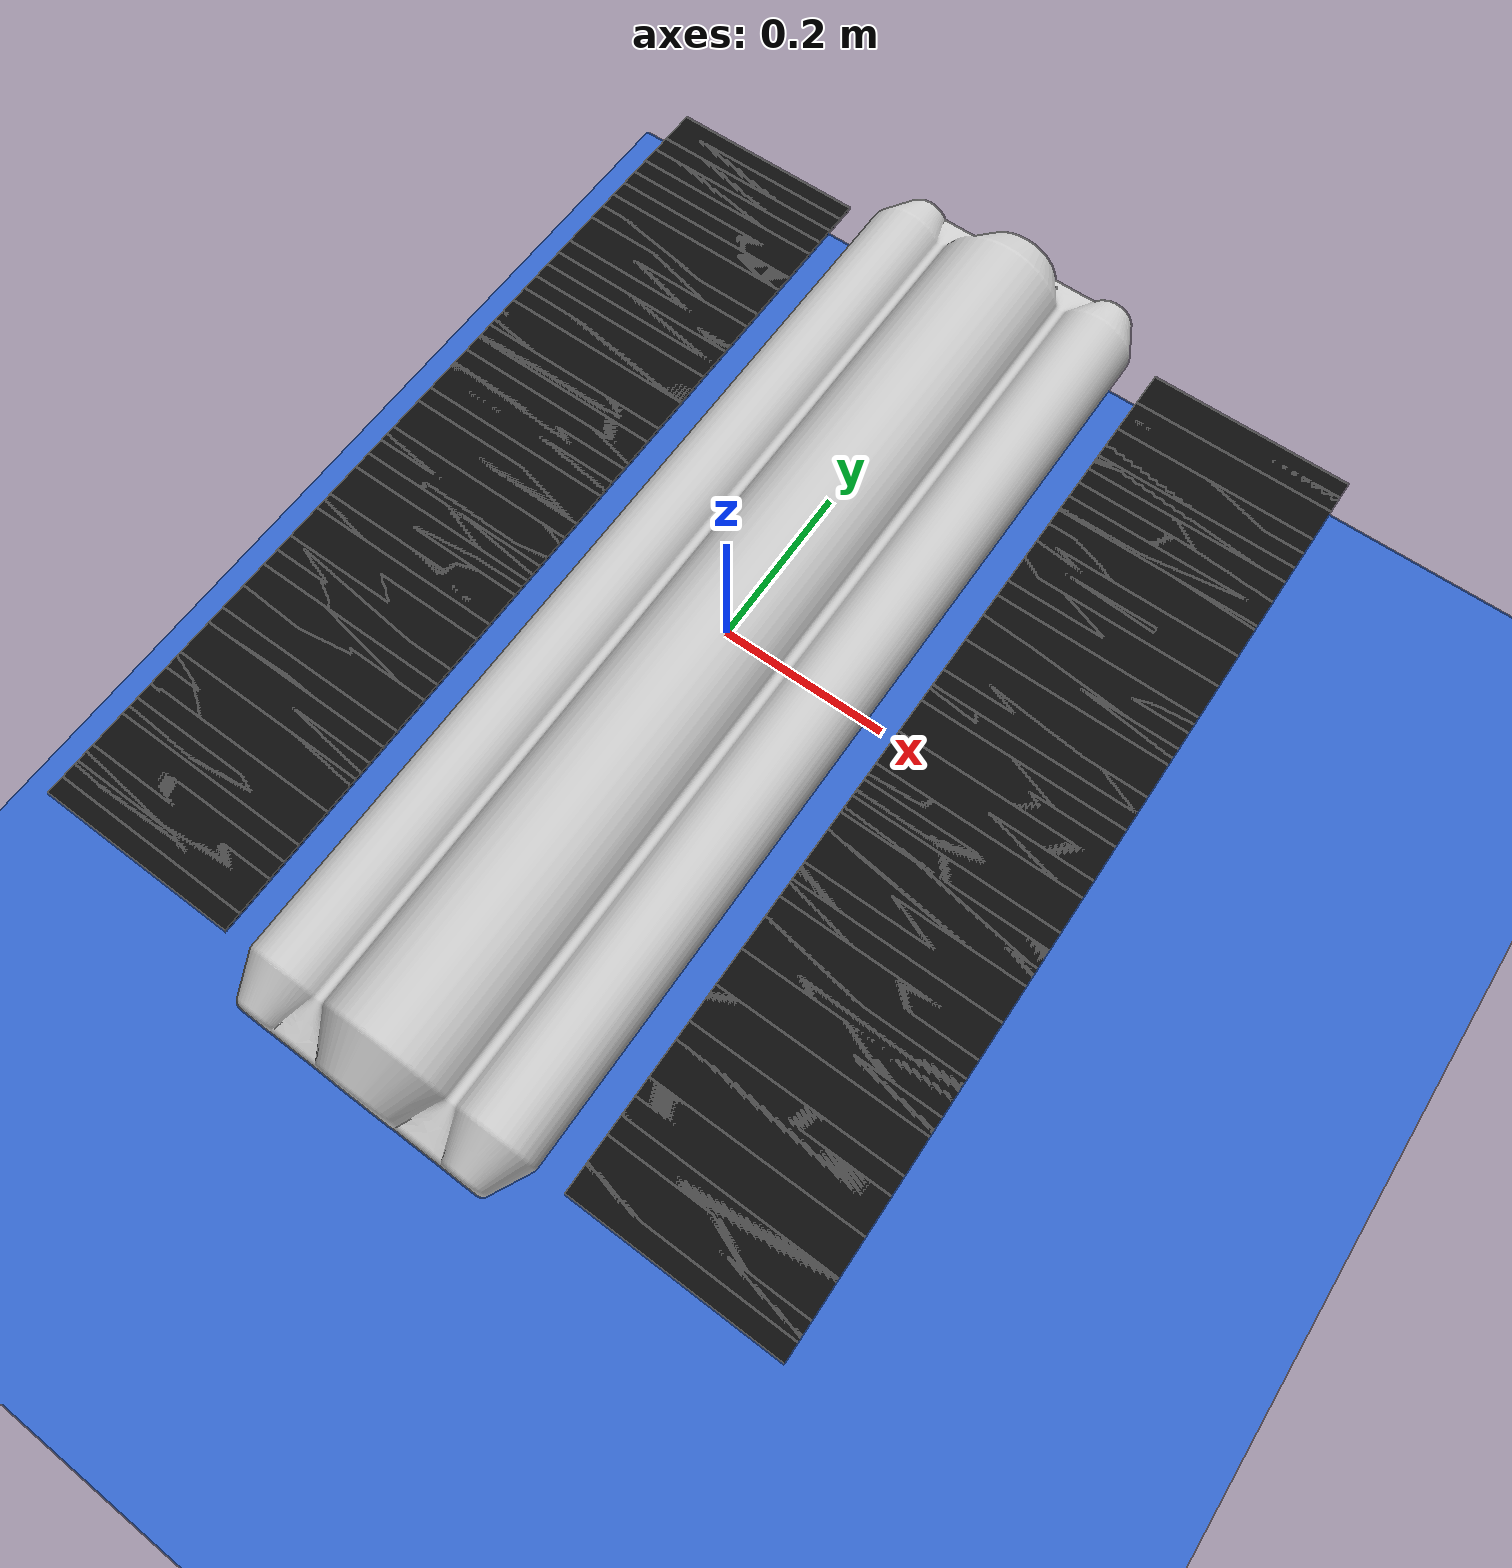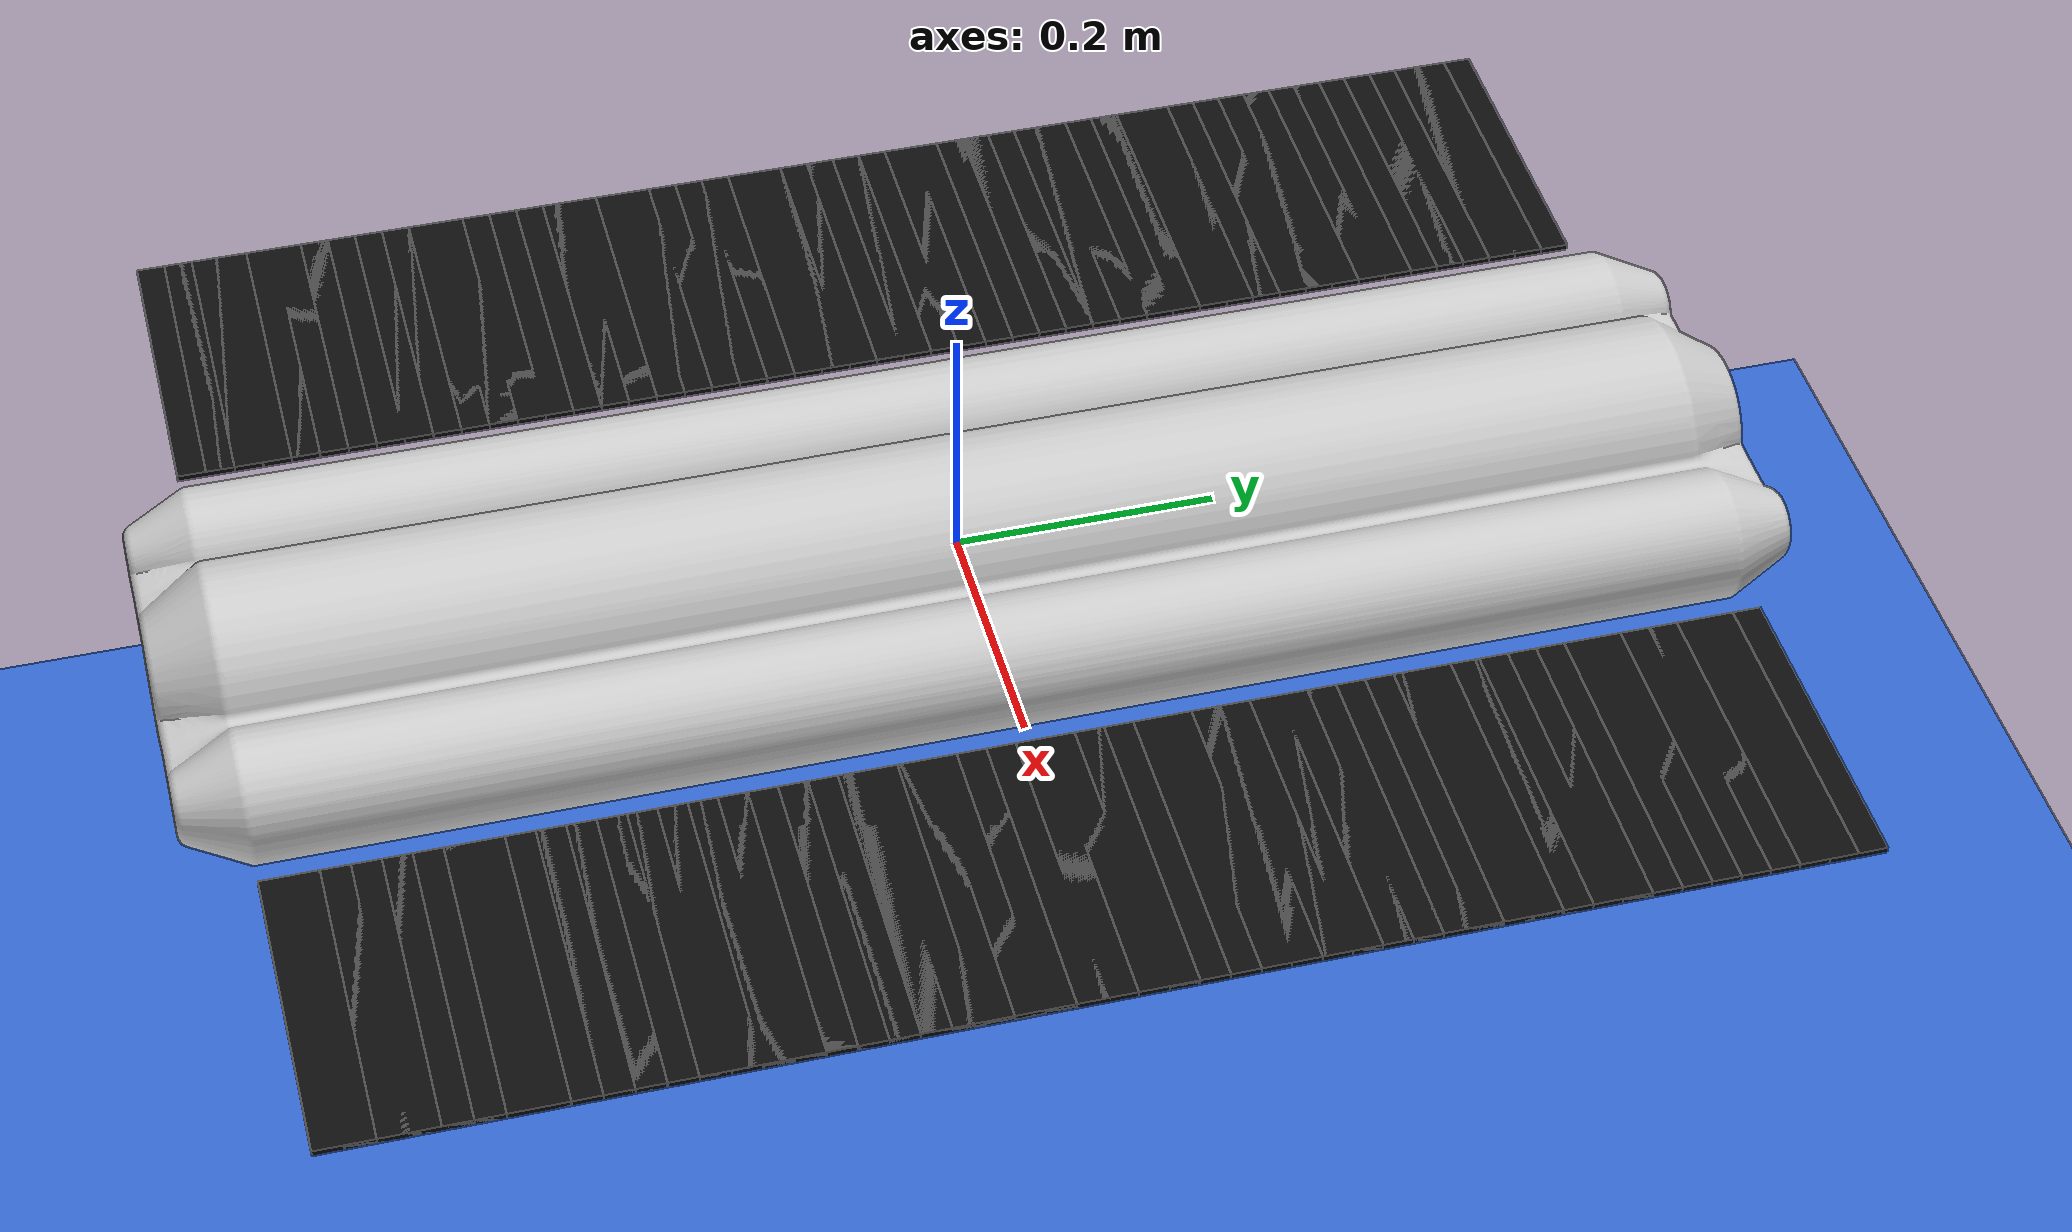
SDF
<?xml version="1.0" ?>
<sdf version="1.9">

	<world name="fish_world">

		<plugin filename="libignition-gazebo-scene-broadcaster-system.so" name="gz::sim::systems::SceneBroadcaster">
		</plugin>

		<physics name="20ms" type="ode">

			<max_step_size>0.020</max_step_size>

			<real_time_factor>1</real_time_factor>

			<real_time_update_rate>50</real_time_update_rate>

		</physics>

		<plugin filename="ignition-gazebo-physics-system" name="ignition::gazebo::systems::Physics">
		</plugin>

		<plugin filename="ignition-gazebo-scene-broadcaster-system" name="ignition::gazebo::systems::SceneBroadcaster">
		</plugin>

		<plugin name="gz::sim::systems::UserCommands" filename="ignition-gazebo-user-commands-system"/>

		<plugin name="gz::sim::systems::Buoyancy" filename="ignition-gazebo-buoyancy-system">

			<uniform_fluid_density>1000</uniform_fluid_density>

		</plugin>

		<plugin filename="ignition-gazebo-imu-system" name="ignition::gazebo::systems::Imu"/>

		<engine>ogre2</engine>

		<camera_pose>8.3 7 7.8 0 0.5 -2.4</camera_pose>

		<gravity>0 0 -9.8</gravity>

		<magnetic_field>6e-06 2.3e-05 -4.2e-05</magnetic_field>

		<atmosphere type="adiabatic"/>

		<light name="sun" type="directional">

			<pose>0 0 10 0 -0 0</pose>

			<cast_shadows>false</cast_shadows>

			<intensity>1</intensity>

			<direction>0 0 -1</direction>

			<diffuse>1 1 1 1</diffuse>

			<specular>0.5 0.5 0.5 1</specular>

			<attenuation>

				<range>1000</range>

				<linear>0.01</linear>

				<constant>0.90000000000000002</constant>

				<quadratic>0.001</quadratic>

			</attenuation>

			<spot>

				<inner_angle>0</inner_angle>

				<outer_angle>0</outer_angle>

				<falloff>0</falloff>

			</spot>

		</light>

		<model name="fish_model">

			<link name="fish_body">

				<pose>0 0 0 1.5708 0 0</pose>

				<sensor name="imu_sensor_1" type="imu">

					<pose>0 0 0 0 0 0</pose>

					<always_on>1</always_on>

					<update_rate>100</update_rate>

					<visualize>true</visualize>

					<topic>/imu_1</topic>

					<imu>

						<angular_velocity>true</angular_velocity>

						<linear_acceleration>true</linear_acceleration>

						<orientation>true</orientation>

					</imu>

				</sensor>

				<sensor name="imu_sensor_2" type="imu">

					<pose>0.2 0 0 0 0 0</pose>

					<always_on>1</always_on>

					<update_rate>100</update_rate>

					<visualize>true</visualize>

					<topic>/imu_2</topic>

					<imu>

						<angular_velocity>true</angular_velocity>

						<linear_acceleration>true</linear_acceleration>

						<orientation>true</orientation>

					</imu>

				</sensor>

				<sensor name="imu_sensor_3" type="imu">

					<pose>0 0.2 0 0 0 0</pose>

					<always_on>1</always_on>

					<update_rate>100</update_rate>

					<visualize>true</visualize>

					<topic>/imu_3</topic>

					<imu>

						<angular_velocity>true</angular_velocity>

						<linear_acceleration>true</linear_acceleration>

						<orientation>true</orientation>

					</imu>

				</sensor>

				<sensor name="imu_sensor_4" type="imu">

					<pose>0 -0.2 0 0 0 0</pose>

					<always_on>1</always_on>

					<update_rate>100</update_rate>

					<visualize>true</visualize>

					<topic>/imu_4</topic>

					<imu>

						<angular_velocity>true</angular_velocity>

						<linear_acceleration>true</linear_acceleration>

						<orientation>true</orientation>

					</imu>

				</sensor>

				<inertial>

					<pose>0 0 0 0 0 0</pose>

					<mass>62.99300000</mass>

					<inertia>

						<ixx>7.49</ixx>

						<ixy>0.00</ixy>

						<ixz>0.00</ixz>

						<iyy>7.49</iyy>

						<iyz>0.00</iyz>

						<izz>0.60</izz>

					</inertia>

				</inertial>

				<collision name="fish_collision">

					<geometry>

						<mesh>

							<uri>
								/home/maycuaaiz/Desktop/FishRobot-ROS/models/hull_mesh.stl</uri>

							<scale>1 1 1</scale>

						</mesh>

					</geometry>

				</collision>

				<visual name="fish_visual">

					<pose>-0.18130304269 -0.08284609487 -0.61094072595 0 0 0</pose>

					<cast_shadows>1</cast_shadows>

					<transparency>0</transparency>

					<geometry>

						<mesh>

							<uri>
								/home/maycuaaiz/Desktop/FishRobot-ROS/models/hull_mesh.stl</uri>

							<scale>1 1 1</scale>

						</mesh>

					</geometry>

					<material>

						<ambient>0.8 0.8 0.8 1</ambient>

						<diffuse>0.8 0.8 0.8 1</diffuse>

						<specular>0.8 0.8 0.8 1</specular>

						<emissive>0 0 0 1</emissive>

					</material>

				</visual>

				<enable_wind>false</enable_wind>

			</link>

			<plugin filename="ignition-gazebo-hydrodynamics-system" name="ignition::gazebo::systems::Hydrodynamics">

				<link_name>fish_body</link_name>

				<xDotU>-7.4019</xDotU>

				<xUU>-0.9576</xUU>

				<xU>-45.8669</xU>

				<yDotV>-13.3689</yDotV>

				<yVV>-0.2</yVV>

				<yV>-13.9664</yV>

				<zDotW>-52.5309</zDotW>

				<zWW>-31.90550</zWW>

				<zW>-56.1710</zW>

				<kDotP>-4.42167</kDotP>

				<kPabsP>-210.158</kPabsP>

				<kP>-104.72</kP>

				<mDotQ>-7.3833</mDotQ>

				<mQabsQ>-190</mQabsQ>

				<mQ>-10</mQ>

				<nDotR>-0.55848</nDotR>

				<nRabsR>-0.2106</nRabsR>

				<nR>-1.0869</nR>

			</plugin>

			<link name="fin_1_1">

				<pose relative_to="fin_1_1_circular">0.0 0.0 -0.200000 3.14 0 0</pose>

				<inertial>

					<mass>0.055000</mass>

				</inertial>

				<visual name="visual">

					<geometry>

						<box>

							<size>0.005000 0.044000 0.250000</size>

						</box>

					</geometry>

					<material>

						<ambient>0.05 0.05 0.05 1</ambient>

						<diffuse>0.05 0.05 0.05 1</diffuse>

						<specular>0.05 0.05 0.05 1</specular>

					</material>

				</visual>

				<collision name="collision">

					<geometry>

						<box>

							<size>0.005000 0.044000 0.250000</size>

						</box>

					</geometry>

				</collision>

			</link>

			<joint name="fin_1_1_joint" type="revolute">

				<pose relative_to="fin_1_1_circular"/>

				<child>fin_1_1</child>

				<parent>fin_1_1_circular</parent>

				<axis>

					<xyz>0 0 1</xyz>

					<limit>

						<lower>-2.08567</lower>

						<upper>2.08567</upper>

						<effort>100.25</effort>

						<velocity>100</velocity>

					</limit>

					<dynamics>

						<damping>15</damping>

						<friction>0</friction>

						<spring_reference>0</spring_reference>

						<spring_stiffness>0</spring_stiffness>

					</dynamics>

				</axis>

			</joint>

			<plugin filename="ignition-gazebo-joint-position-controller-system" name="ignition::gazebo::systems::JointPositionController">

				<joint_name>fin_1_1_joint</joint_name>

				<p_gain>80</p_gain>

				<i_gain>0.5</i_gain>

				<d_gain>0.1</d_gain>

				<i_max>1</i_max>

				<i_min>-1</i_min>

				<cmd_max>100</cmd_max>

				<cmd_min>-100</cmd_min>

			</plugin>

			<link name="fin_1_1_circular">

				<pose relative_to="fin_1_1_axis">0.0 0.0 -0.010000 0 0 0</pose>

				<inertial>

					<mass>0.015205</mass>

				</inertial>

				<visual name="visual">

					<geometry>

						<cylinder>

							<radius>0.022000</radius>

							<length>0.010000</length>

						</cylinder>

					</geometry>

					<material>

						<ambient>1 0.5 0 1</ambient>

						<diffuse>1 0.5 0 1</diffuse>

						<specular>1 0.5 0 1</specular>

					</material>

				</visual>

				<collision name="collision">

					<geometry>

						<cylinder>

							<radius>0.022000</radius>

							<length>0.010000</length>

						</cylinder>

					</geometry>

				</collision>

			</link>

			<joint name="fin_1_1_circular_joint" type="revolute">

				<pose relative_to="fin_1_1_axis"/>

				<child>fin_1_1_circular</child>

				<parent>fin_1_1_axis</parent>

				<axis>

					<xyz>0 1 0</xyz>

					<limit>

						<lower>-2.08567</lower>

						<upper>2.08567</upper>

						<effort>100.25</effort>

						<velocity>100</velocity>

					</limit>

					<dynamics>

						<damping>10</damping>

						<friction>0</friction>

						<spring_reference>0</spring_reference>

						<spring_stiffness>0</spring_stiffness>

					</dynamics>

				</axis>

			</joint>

			<plugin filename="ignition-gazebo-joint-position-controller-system" name="ignition::gazebo::systems::JointPositionController">

				<joint_name>fin_1_1_circular_joint</joint_name>

				<p_gain>80</p_gain>

				<i_gain>1</i_gain>

				<d_gain>0.1</d_gain>

				<i_max>1</i_max>

				<i_min>-1</i_min>

				<cmd_max>100</cmd_max>

				<cmd_min>-100</cmd_min>

			</plugin>

			<link name="fin_1_1_axis">

				<pose relative_to="fish_body">-0.130000 0.000000 0.539000 1.5708 0 1.5708</pose>

				<inertial>

					<mass>0.015205</mass>

				</inertial>

				<collision name="fin_1_axis_collision">

					<geometry>

						<cylinder>

							<radius>0.022000</radius>

							<length>0.010000</length>

						</cylinder>

					</geometry>

					<surface>

						<friction>

							<ode/>

						</friction>

						<bounce/>

						<contact/>

					</surface>

				</collision>

				<visual name="fin_1_axis_visual">

					<geometry>

						<cylinder>

							<radius>0.022000</radius>

							<length>0.010000</length>

						</cylinder>

					</geometry>

					<material>

						<ambient>0.3 0.3 0.3 1</ambient>

						<diffuse>0.7 0.7 0.7 1</diffuse>

						<specular>1 1 1 1</specular>

					</material>

				</visual>

			</link>

			<joint name="fin_1_1_axis_joint" type="fixed">

				<parent>fish_body</parent>

				<child>fin_1_1_axis</child>

				<pose relative_to="fish_body">0.0 0.2 0 0 0 0</pose>

			</joint>

			<plugin name="gz::sim::systems::LiftDrag" filename="ignition-gazebo-lift-drag-system">

				<air_density>1000</air_density>

				<a0>0</a0>

				<alpha_stall>0.611</alpha_stall>

				<cla>0.766</cla>

				<cla_stall>-0.776</cla_stall>

				<cda>1.073</cda>

				<cda_stall>0.883</cda_stall>

				<area>0.01096</area>

				<upward>1.0 0 0</upward>

				<forward>0 1.0 0</forward>

				<link_name>fin_1_1</link_name>

				<cp>0 0 0</cp>

			</plugin>

			<link name="fin_1_2">

				<pose relative_to="fin_1_2_circular">0.0 0.0 -0.200000 3.14 0 0</pose>

				<inertial>

					<mass>0.055000</mass>

				</inertial>

				<visual name="visual">

					<geometry>

						<box>

							<size>0.005000 0.044000 0.250000</size>

						</box>

					</geometry>

					<material>

						<ambient>0.05 0.05 0.05 1</ambient>

						<diffuse>0.05 0.05 0.05 1</diffuse>

						<specular>0.05 0.05 0.05 1</specular>

					</material>

				</visual>

				<collision name="collision">

					<geometry>

						<box>

							<size>0.005000 0.044000 0.250000</size>

						</box>

					</geometry>

				</collision>

			</link>

			<joint name="fin_1_2_joint" type="revolute">

				<pose relative_to="fin_1_2_circular"/>

				<child>fin_1_2</child>

				<parent>fin_1_2_circular</parent>

				<axis>

					<xyz>0 0 1</xyz>

					<limit>

						<lower>-2.08567</lower>

						<upper>2.08567</upper>

						<effort>100.25</effort>

						<velocity>100</velocity>

					</limit>

					<dynamics>

						<damping>15</damping>

						<friction>0</friction>

						<spring_reference>0</spring_reference>

						<spring_stiffness>0</spring_stiffness>

					</dynamics>

				</axis>

			</joint>

			<plugin filename="ignition-gazebo-joint-position-controller-system" name="ignition::gazebo::systems::JointPositionController">

				<joint_name>fin_1_2_joint</joint_name>

				<p_gain>80</p_gain>

				<i_gain>0.5</i_gain>

				<d_gain>0.1</d_gain>

				<i_max>1</i_max>

				<i_min>-1</i_min>

				<cmd_max>100</cmd_max>

				<cmd_min>-100</cmd_min>

			</plugin>

			<link name="fin_1_2_circular">

				<pose relative_to="fin_1_2_axis">0.0 0.0 -0.010000 0 0 0</pose>

				<inertial>

					<mass>0.015205</mass>

				</inertial>

				<visual name="visual">

					<geometry>

						<cylinder>

							<radius>0.022000</radius>

							<length>0.010000</length>

						</cylinder>

					</geometry>

					<material>

						<ambient>1 0.5 0 1</ambient>

						<diffuse>1 0.5 0 1</diffuse>

						<specular>1 0.5 0 1</specular>

					</material>

				</visual>

				<collision name="collision">

					<geometry>

						<cylinder>

							<radius>0.022000</radius>

							<length>0.010000</length>

						</cylinder>

					</geometry>

				</collision>

			</link>

			<joint name="fin_1_2_circular_joint" type="revolute">

				<pose relative_to="fin_1_2_axis"/>

				<child>fin_1_2_circular</child>

				<parent>fin_1_2_axis</parent>

				<axis>

					<xyz>0 1 0</xyz>

					<limit>

						<lower>-2.08567</lower>

						<upper>2.08567</upper>

						<effort>100.25</effort>

						<velocity>100</velocity>

					</limit>

					<dynamics>

						<damping>10</damping>

						<friction>0</friction>

						<spring_reference>0</spring_reference>

						<spring_stiffness>0</spring_stiffness>

					</dynamics>

				</axis>

			</joint>

			<plugin filename="ignition-gazebo-joint-position-controller-system" name="ignition::gazebo::systems::JointPositionController">

				<joint_name>fin_1_2_circular_joint</joint_name>

				<p_gain>80</p_gain>

				<i_gain>1</i_gain>

				<d_gain>0.1</d_gain>

				<i_max>1</i_max>

				<i_min>-1</i_min>

				<cmd_max>100</cmd_max>

				<cmd_min>-100</cmd_min>

			</plugin>

			<link name="fin_1_2_axis">

				<pose relative_to="fish_body">-0.130000 0.000000 0.517000 1.5708 0 1.5708</pose>

				<inertial>

					<mass>0.015205</mass>

				</inertial>

				<collision name="fin_1_axis_collision">

					<geometry>

						<cylinder>

							<radius>0.022000</radius>

							<length>0.010000</length>

						</cylinder>

					</geometry>

					<surface>

						<friction>

							<ode/>

						</friction>

						<bounce/>

						<contact/>

					</surface>

				</collision>

				<visual name="fin_1_axis_visual">

					<geometry>

						<cylinder>

							<radius>0.022000</radius>

							<length>0.010000</length>

						</cylinder>

					</geometry>

					<material>

						<ambient>0.3 0.3 0.3 1</ambient>

						<diffuse>0.7 0.7 0.7 1</diffuse>

						<specular>1 1 1 1</specular>

					</material>

				</visual>

			</link>

			<joint name="fin_1_2_axis_joint" type="fixed">

				<parent>fish_body</parent>

				<child>fin_1_2_axis</child>

				<pose relative_to="fish_body">0.0 0.2 0 0 0 0</pose>

			</joint>

			<plugin name="gz::sim::systems::LiftDrag" filename="ignition-gazebo-lift-drag-system">

				<air_density>1000</air_density>

				<a0>0</a0>

				<alpha_stall>0.611</alpha_stall>

				<cla>0.766</cla>

				<cla_stall>-0.776</cla_stall>

				<cda>1.073</cda>

				<cda_stall>0.883</cda_stall>

				<area>0.01096</area>

				<upward>1.0 0 0</upward>

				<forward>0 1.0 0</forward>

				<link_name>fin_1_2</link_name>

				<cp>0 0 0</cp>

			</plugin>

			<link name="fin_1_3">

				<pose relative_to="fin_1_3_circular">0.0 0.0 -0.200000 3.14 0 0</pose>

				<inertial>

					<mass>0.055000</mass>

				</inertial>

				<visual name="visual">

					<geometry>

						<box>

							<size>0.005000 0.044000 0.250000</size>

						</box>

					</geometry>

					<material>

						<ambient>0.05 0.05 0.05 1</ambient>

						<diffuse>0.05 0.05 0.05 1</diffuse>

						<specular>0.05 0.05 0.05 1</specular>

					</material>

				</visual>

				<collision name="collision">

					<geometry>

						<box>

							<size>0.005000 0.044000 0.250000</size>

						</box>

					</geometry>

				</collision>

			</link>

			<joint name="fin_1_3_joint" type="revolute">

				<pose relative_to="fin_1_3_circular"/>

				<child>fin_1_3</child>

				<parent>fin_1_3_circular</parent>

				<axis>

					<xyz>0 0 1</xyz>

					<limit>

						<lower>-2.08567</lower>

						<upper>2.08567</upper>

						<effort>100.25</effort>

						<velocity>100</velocity>

					</limit>

					<dynamics>

						<damping>15</damping>

						<friction>0</friction>

						<spring_reference>0</spring_reference>

						<spring_stiffness>0</spring_stiffness>

					</dynamics>

				</axis>

			</joint>

			<plugin filename="ignition-gazebo-joint-position-controller-system" name="ignition::gazebo::systems::JointPositionController">

				<joint_name>fin_1_3_joint</joint_name>

				<p_gain>80</p_gain>

				<i_gain>0.5</i_gain>

				<d_gain>0.1</d_gain>

				<i_max>1</i_max>

				<i_min>-1</i_min>

				<cmd_max>100</cmd_max>

				<cmd_min>-100</cmd_min>

			</plugin>

			<link name="fin_1_3_circular">

				<pose relative_to="fin_1_3_axis">0.0 0.0 -0.010000 0 0 0</pose>

				<inertial>

					<mass>0.015205</mass>

				</inertial>

				<visual name="visual">

					<geometry>

						<cylinder>

							<radius>0.022000</radius>

							<length>0.010000</length>

						</cylinder>

					</geometry>

					<material>

						<ambient>1 0.5 0 1</ambient>

						<diffuse>1 0.5 0 1</diffuse>

						<specular>1 0.5 0 1</specular>

					</material>

				</visual>

				<collision name="collision">

					<geometry>

						<cylinder>

							<radius>0.022000</radius>

							<length>0.010000</length>

						</cylinder>

					</geometry>

				</collision>

			</link>

			<joint name="fin_1_3_circular_joint" type="revolute">

				<pose relative_to="fin_1_3_axis"/>

				<child>fin_1_3_circular</child>

				<parent>fin_1_3_axis</parent>

				<axis>

					<xyz>0 1 0</xyz>

					<limit>

						<lower>-2.08567</lower>

						<upper>2.08567</upper>

						<effort>100.25</effort>

						<velocity>100</velocity>

					</limit>

					<dynamics>

						<damping>10</damping>

						<friction>0</friction>

						<spring_reference>0</spring_reference>

						<spring_stiffness>0</spring_stiffness>

					</dynamics>

				</axis>

			</joint>

			<plugin filename="ignition-gazebo-joint-position-controller-system" name="ignition::gazebo::systems::JointPositionController">

				<joint_name>fin_1_3_circular_joint</joint_name>

				<p_gain>80</p_gain>

				<i_gain>1</i_gain>

				<d_gain>0.1</d_gain>

				<i_max>1</i_max>

				<i_min>-1</i_min>

				<cmd_max>100</cmd_max>

				<cmd_min>-100</cmd_min>

			</plugin>

			<link name="fin_1_3_axis">

				<pose relative_to="fish_body">-0.130000 0.000000 0.495000 1.5708 0 1.5708</pose>

				<inertial>

					<mass>0.015205</mass>

				</inertial>

				<collision name="fin_1_axis_collision">

					<geometry>

						<cylinder>

							<radius>0.022000</radius>

							<length>0.010000</length>

						</cylinder>

					</geometry>

					<surface>

						<friction>

							<ode/>

						</friction>

						<bounce/>

						<contact/>

					</surface>

				</collision>

				<visual name="fin_1_axis_visual">

					<geometry>

						<cylinder>

							<radius>0.022000</radius>

							<length>0.010000</length>

						</cylinder>

					</geometry>

					<material>

						<ambient>0.3 0.3 0.3 1</ambient>

						<diffuse>0.7 0.7 0.7 1</diffuse>

						<specular>1 1 1 1</specular>

					</material>

				</visual>

			</link>

			<joint name="fin_1_3_axis_joint" type="fixed">

				<parent>fish_body</parent>

				<child>fin_1_3_axis</child>

				<pose relative_to="fish_body">0.0 0.2 0 0 0 0</pose>

			</joint>

			<plugin name="gz::sim::systems::LiftDrag" filename="ignition-gazebo-lift-drag-system">

				<air_density>1000</air_density>

				<a0>0</a0>

				<alpha_stall>0.611</alpha_stall>

				<cla>0.766</cla>

				<cla_stall>-0.776</cla_stall>

				<cda>1.073</cda>

				<cda_stall>0.883</cda_stall>

				<area>0.01096</area>

				<upward>1.0 0 0</upward>

				<forward>0 1.0 0</forward>

				<link_name>fin_1_3</link_name>

				<cp>0 0 0</cp>

			</plugin>

			<link name="fin_1_4">

				<pose relative_to="fin_1_4_circular">0.0 0.0 -0.200000 3.14 0 0</pose>

				<inertial>

					<mass>0.055000</mass>

				</inertial>

				<visual name="visual">

					<geometry>

						<box>

							<size>0.005000 0.044000 0.250000</size>

						</box>

					</geometry>

					<material>

						<ambient>0.05 0.05 0.05 1</ambient>

						<diffuse>0.05 0.05 0.05 1</diffuse>

						<specular>0.05 0.05 0.05 1</specular>

					</material>

				</visual>

				<collision name="collision">

					<geometry>

						<box>

							<size>0.005000 0.044000 0.250000</size>

						</box>

					</geometry>

				</collision>

			</link>

			<joint name="fin_1_4_joint" type="revolute">

				<pose relative_to="fin_1_4_circular"/>

				<child>fin_1_4</child>

				<parent>fin_1_4_circular</parent>

				<axis>

					<xyz>0 0 1</xyz>

					<limit>

						<lower>-2.08567</lower>

						<upper>2.08567</upper>

						<effort>100.25</effort>

						<velocity>100</velocity>

					</limit>

					<dynamics>

						<damping>15</damping>

						<friction>0</friction>

						<spring_reference>0</spring_reference>

						<spring_stiffness>0</spring_stiffness>

					</dynamics>

				</axis>

			</joint>

			<plugin filename="ignition-gazebo-joint-position-controller-system" name="ignition::gazebo::systems::JointPositionController">

				<joint_name>fin_1_4_joint</joint_name>

				<p_gain>80</p_gain>

				<i_gain>0.5</i_gain>

				<d_gain>0.1</d_gain>

				<i_max>1</i_max>

				<i_min>-1</i_min>

				<cmd_max>100</cmd_max>

				<cmd_min>-100</cmd_min>

			</plugin>

			<link name="fin_1_4_circular">

				<pose relative_to="fin_1_4_axis">0.0 0.0 -0.010000 0 0 0</pose>

				<inertial>

					<mass>0.015205</mass>

				</inertial>

				<visual name="visual">

					<geometry>

						<cylinder>

							<radius>0.022000</radius>

							<length>0.010000</length>

						</cylinder>

					</geometry>

					<material>

						<ambient>1 0.5 0 1</ambient>

						<diffuse>1 0.5 0 1</diffuse>

						<specular>1 0.5 0 1</specular>

					</material>

				</visual>

				<collision name="collision">

					<geometry>

						<cylinder>

							<radius>0.022000</radius>

							<length>0.010000</length>

						</cylinder>

					</geometry>

				</collision>

			</link>

			<joint name="fin_1_4_circular_joint" type="revolute">

				<pose relative_to="fin_1_4_axis"/>

				<child>fin_1_4_circular</child>

				<parent>fin_1_4_axis</parent>

				<axis>

					<xyz>0 1 0</xyz>

					<limit>

						<lower>-2.08567</lower>

						<upper>2.08567</upper>

						<effort>100.25</effort>

						<velocity>100</velocity>

					</limit>

					<dynamics>

						<damping>10</damping>

						<friction>0</friction>

						<spring_reference>0</spring_reference>

						<spring_stiffness>0</spring_stiffness>

					</dynamics>

				</axis>

			</joint>

			<plugin filename="ignition-gazebo-joint-position-controller-system" name="ignition::gazebo::systems::JointPositionController">

				<joint_name>fin_1_4_circular_joint</joint_name>

				<p_gain>80</p_gain>

				<i_gain>1</i_gain>

				<d_gain>0.1</d_gain>

				<i_max>1</i_max>

				<i_min>-1</i_min>

				<cmd_max>100</cmd_max>

				<cmd_min>-100</cmd_min>

			</plugin>

			<link name="fin_1_4_axis">

				<pose relative_to="fish_body">-0.130000 0.000000 0.473000 1.5708 0 1.5708</pose>

				<inertial>

					<mass>0.015205</mass>

				</inertial>

				<collision name="fin_1_axis_collision">

					<geometry>

						<cylinder>

							<radius>0.022000</radius>

							<length>0.010000</length>

						</cylinder>

					</geometry>

					<surface>

						<friction>

							<ode/>

						</friction>

						<bounce/>

						<contact/>

					</surface>

				</collision>

				<visual name="fin_1_axis_visual">

					<geometry>

						<cylinder>

							<radius>0.022000</radius>

							<length>0.010000</length>

						</cylinder>

					</geometry>

					<material>

						<ambient>0.3 0.3 0.3 1</ambient>

						<diffuse>0.7 0.7 0.7 1</diffuse>

						<specular>1 1 1 1</specular>

					</material>

				</visual>

			</link>

			<joint name="fin_1_4_axis_joint" type="fixed">

				<parent>fish_body</parent>

				<child>fin_1_4_axis</child>

				<pose relative_to="fish_body">0.0 0.2 0 0 0 0</pose>

			</joint>

			<plugin name="gz::sim::systems::LiftDrag" filename="ignition-gazebo-lift-drag-system">

				<air_density>1000</air_density>

				<a0>0</a0>

				<alpha_stall>0.611</alpha_stall>

				<cla>0.766</cla>

				<cla_stall>-0.776</cla_stall>

				<cda>1.073</cda>

				<cda_stall>0.883</cda_stall>

				<area>0.01096</area>

				<upward>1.0 0 0</upward>

				<forward>0 1.0 0</forward>

				<link_name>fin_1_4</link_name>

				<cp>0 0 0</cp>

			</plugin>

			<link name="fin_1_5">

				<pose relative_to="fin_1_5_circular">0.0 0.0 -0.200000 3.14 0 0</pose>

				<inertial>

					<mass>0.055000</mass>

				</inertial>

				<visual name="visual">

					<geometry>

						<box>

							<size>0.005000 0.044000 0.250000</size>

						</box>

					</geometry>

					<material>

						<ambient>0.05 0.05 0.05 1</ambient>

						<diffuse>0.05 0.05 0.05 1</diffuse>

						<specular>0.05 0.05 0.05 1</specular>

					</material>

				</visual>

				<collision name="collision">

					<geometry>

						<box>

							<size>0.005000 0.044000 0.250000</size>

						</box>

					</geometry>

				</collision>

			</link>

			<joint name="fin_1_5_joint" type="revolute">

				<pose relative_to="fin_1_5_circular"/>

				<child>fin_1_5</child>

				<parent>fin_1_5_circular</parent>

				<axis>

					<xyz>0 0 1</xyz>

					<limit>

						<lower>-2.08567</lower>

						<upper>2.08567</upper>

						<effort>100.25</effort>

						<velocity>100</velocity>

					</limit>

					<dynamics>

						<damping>15</damping>

						<friction>0</friction>

						<spring_reference>0</spring_reference>

						<spring_stiffness>0</spring_stiffness>

					</dynamics>

				</axis>

			</joint>

			<plugin filename="ignition-gazebo-joint-position-controller-system" name="ignition::gazebo::systems::JointPositionController">

				<joint_name>fin_1_5_joint</joint_name>

				<p_gain>80</p_gain>

				<i_gain>0.5</i_gain>

				<d_gain>0.1</d_gain>

				<i_max>1</i_max>

				<i_min>-1</i_min>

				<cmd_max>100</cmd_max>

				<cmd_min>-100</cmd_min>

			</plugin>

			<link name="fin_1_5_circular">

				<pose relative_to="fin_1_5_axis">0.0 0.0 -0.010000 0 0 0</pose>

				<inertial>

					<mass>0.015205</mass>

				</inertial>

				<visual name="visual">

					<geometry>

						<cylinder>

							<radius>0.022000</radius>

							<length>0.010000</length>

						</cylinder>

					</geometry>

					<material>

						<ambient>1 0.5 0 1</ambient>

						<diffuse>1 0.5 0 1</diffuse>

						<specular>1 0.5 0 1</specular>

					</material>

				</visual>

				<collision name="collision">

					<geometry>

						<cylinder>

							<radius>0.022000</radius>

							<length>0.010000</length>

						</cylinder>

					</geometry>

				</collision>

			</link>

			<joint name="fin_1_5_circular_joint" type="revolute">

				<pose relative_to="fin_1_5_axis"/>

				<child>fin_1_5_circular</child>

				<parent>fin_1_5_axis</parent>

				<axis>

					<xyz>0 1 0</xyz>

					<limit>

						<lower>-2.08567</lower>

						<upper>2.08567</upper>

						<effort>100.25</effort>

						<velocity>100</velocity>

					</limit>

					<dynamics>

						<damping>10</damping>

						<friction>0</friction>

						<spring_reference>0</spring_reference>

						<spring_stiffness>0</spring_stiffness>

					</dynamics>

				</axis>

			</joint>

			<plugin filename="ignition-gazebo-joint-position-controller-system" name="ignition::gazebo::systems::JointPositionController">

				<joint_name>fin_1_5_circular_joint</joint_name>

				<p_gain>80</p_gain>

				<i_gain>1</i_gain>

				<d_gain>0.1</d_gain>

				<i_max>1</i_max>

				<i_min>-1</i_min>

				<cmd_max>100</cmd_max>

				<cmd_min>-100</cmd_min>

			</plugin>

			<link name="fin_1_5_axis">

				<pose relative_to="fish_body">-0.130000 0.000000 0.451000 1.5708 0 1.5708</pose>

				<inertial>

					<mass>0.015205</mass>

				</inertial>

				<collision name="fin_1_axis_collision">

					<geometry>

						<cylinder>

							<radius>0.022000</radius>

							<length>0.010000</length>

						</cylinder>

					</geometry>

					<surface>

						<friction>

							<ode/>

						</friction>

						<bounce/>

						<contact/>

					</surface>

				</collision>

				<visual name="fin_1_axis_visual">

					<geometry>

						<cylinder>

							<radius>0.022000</radius>

							<length>0.010000</length>

						</cylinder>

					</geometry>

					<material>

						<ambient>0.3 0.3 0.3 1</ambient>

						<diffuse>0.7 0.7 0.7 1</diffuse>

						<specular>1 1 1 1</specular>

					</material>

				</visual>

			</link>

			<joint name="fin_1_5_axis_joint" type="fixed">

				<parent>fish_body</parent>

				<child>fin_1_5_axis</child>

				<pose relative_to="fish_body">0.0 0.2 0 0 0 0</pose>

			</joint>

			<plugin name="gz::sim::systems::LiftDrag" filename="ignition-gazebo-lift-drag-system">

				<air_density>1000</air_density>

				<a0>0</a0>

				<alpha_stall>0.611</alpha_stall>

				<cla>0.766</cla>

				<cla_stall>-0.776</cla_stall>

				<cda>1.073</cda>

				<cda_stall>0.883</cda_stall>

				<area>0.01096</area>

				<upward>1.0 0 0</upward>

				<forward>0 1.0 0</forward>

				<link_name>fin_1_5</link_name>

				<cp>0 0 0</cp>

			</plugin>

			<link name="fin_1_6">

				<pose relative_to="fin_1_6_circular">0.0 0.0 -0.200000 3.14 0 0</pose>

				<inertial>

					<mass>0.055000</mass>

				</inertial>

				<visual name="visual">

					<geometry>

						<box>

							<size>0.005000 0.044000 0.250000</size>

						</box>

					</geometry>

					<material>

						<ambient>0.05 0.05 0.05 1</ambient>

						<diffuse>0.05 0.05 0.05 1</diffuse>

						<specular>0.05 0.05 0.05 1</specular>

					</material>

				</visual>

				<collision name="collision">

					<geometry>

						<box>

							<size>0.005000 0.044000 0.250000</size>

						</box>

					</geometry>

				</collision>

			</link>

			<joint name="fin_1_6_joint" type="revolute">

				<pose relative_to="fin_1_6_circular"/>

				<child>fin_1_6</child>

				<parent>fin_1_6_circular</parent>

				<axis>

					<xyz>0 0 1</xyz>

					<limit>

						<lower>-2.08567</lower>

						<upper>2.08567</upper>

						<effort>100.25</effort>

						<velocity>100</velocity>

					</limit>

					<dynamics>

						<damping>15</damping>

						<friction>0</friction>

						<spring_reference>0</spring_reference>

						<spring_stiffness>0</spring_stiffness>

					</dynamics>

				</axis>

			</joint>

			<plugin filename="ignition-gazebo-joint-position-controller-system" name="ignition::gazebo::systems::JointPositionController">

				<joint_name>fin_1_6_joint</joint_name>

				<p_gain>80</p_gain>

				<i_gain>0.5</i_gain>

				<d_gain>0.1</d_gain>

				<i_max>1</i_max>

				<i_min>-1</i_min>

				<cmd_max>100</cmd_max>

				<cmd_min>-100</cmd_min>

			</plugin>

			<link name="fin_1_6_circular">

				<pose relative_to="fin_1_6_axis">0.0 0.0 -0.010000 0 0 0</pose>

				<inertial>

					<mass>0.015205</mass>

				</inertial>

				<visual name="visual">

					<geometry>

						<cylinder>

							<radius>0.022000</radius>

							<length>0.010000</length>

						</cylinder>

					</geometry>

					<material>

						<ambient>1 0.5 0 1</ambient>

						<diffuse>1 0.5 0 1</diffuse>

						<specular>1 0.5 0 1</specular>

					</material>

				</visual>

				<collision name="collision">

					<geometry>

						<cylinder>

							<radius>0.022000</radius>

							<length>0.010000</length>

						</cylinder>

					</geometry>

				</collision>

			</link>

			<joint name="fin_1_6_circular_joint" type="revolute">

				<pose relative_to="fin_1_6_axis"/>

				<child>fin_1_6_circular</child>

				<parent>fin_1_6_axis</parent>

				<axis>

					<xyz>0 1 0</xyz>

					<limit>

						<lower>-2.08567</lower>

						<upper>2.08567</upper>

						<effort>100.25</effort>

						<velocity>100</velocity>

					</limit>

					<dynamics>

						<damping>10</damping>

						<friction>0</friction>

						<spring_reference>0</spring_reference>

						<spring_stiffness>0</spring_stiffness>

					</dynamics>

				</axis>

			</joint>

			<plugin filename="ignition-gazebo-joint-position-controller-system" name="ignition::gazebo::systems::JointPositionController">

				<joint_name>fin_1_6_circular_joint</joint_name>

				<p_gain>80</p_gain>

				<i_gain>1</i_gain>

				<d_gain>0.1</d_gain>

				<i_max>1</i_max>

				<i_min>-1</i_min>

				<cmd_max>100</cmd_max>

				<cmd_min>-100</cmd_min>

			</plugin>

			<link name="fin_1_6_axis">

				<pose relative_to="fish_body">-0.130000 0.000000 0.429000 1.5708 0 1.5708</pose>

				<inertial>

					<mass>0.015205</mass>

				</inertial>

				<collision name="fin_1_axis_collision">

					<geometry>

						<cylinder>

							<radius>0.022000</radius>

							<length>0.010000</length>

						</cylinder>

					</geometry>

					<surface>

						<friction>

							<ode/>

						</friction>

						<bounce/>

						<contact/>

					</surface>

				</collision>

				<visual name="fin_1_axis_visual">

					<geometry>

						<cylinder>

							<radius>0.022000</radius>

							<length>0.010000</length>

						</cylinder>

					</geometry>

					<material>

						<ambient>0.3 0.3 0.3 1</ambient>

						<diffuse>0.7 0.7 0.7 1</diffuse>

						<specular>1 1 1 1</specular>

					</material>

				</visual>

			</link>

			<joint name="fin_1_6_axis_joint" type="fixed">

				<parent>fish_body</parent>

				<child>fin_1_6_axis</child>

				<pose relative_to="fish_body">0.0 0.2 0 0 0 0</pose>

			</joint>

			<plugin name="gz::sim::systems::LiftDrag" filename="ignition-gazebo-lift-drag-system">

				<air_density>1000</air_density>

				<a0>0</a0>

				<alpha_stall>0.611</alpha_stall>

				<cla>0.766</cla>

				<cla_stall>-0.776</cla_stall>

				<cda>1.073</cda>

				<cda_stall>0.883</cda_stall>

				<area>0.01096</area>

				<upward>1.0 0 0</upward>

				<forward>0 1.0 0</forward>

				<link_name>fin_1_6</link_name>

				<cp>0 0 0</cp>

			</plugin>

			<link name="fin_1_7">

				<pose relative_to="fin_1_7_circular">0.0 0.0 -0.200000 3.14 0 0</pose>

				<inertial>

					<mass>0.055000</mass>

				</inertial>

				<visual name="visual">

					<geometry>

						<box>

							<size>0.005000 0.044000 0.250000</size>

						</box>

					</geometry>

					<material>

						<ambient>0.05 0.05 0.05 1</ambient>

						<diffuse>0.05 0.05 0.05 1</diffuse>

						<specular>0.05 0.05 0.05 1</specular>

					</material>

				</visual>

				<collision name="collision">

					<geometry>

						<box>

							<size>0.005000 0.044000 0.250000</size>

						</box>

					</geometry>

				</collision>

			</link>

			<joint name="fin_1_7_joint" type="revolute">

				<pose relative_to="fin_1_7_circular"/>

				<child>fin_1_7</child>

				<parent>fin_1_7_circular</parent>

				<axis>

					<xyz>0 0 1</xyz>

					<limit>

						<lower>-2.08567</lower>

						<upper>2.08567</upper>

						<effort>100.25</effort>

						<velocity>100</velocity>

					</limit>

					<dynamics>

						<damping>15</damping>

						<friction>0</friction>

						<spring_reference>0</spring_reference>

						<spring_stiffness>0</spring_stiffness>

					</dynamics>

				</axis>

			</joint>

			<plugin filename="ignition-gazebo-joint-position-controller-system" name="ignition::gazebo::systems::JointPositionController">

				<joint_name>fin_1_7_joint</joint_name>

				<p_gain>80</p_gain>

				<i_gain>0.5</i_gain>

				<d_gain>0.1</d_gain>

				<i_max>1</i_max>

				<i_min>-1</i_min>

				<cmd_max>100</cmd_max>

				<cmd_min>-100</cmd_min>

			</plugin>

			<link name="fin_1_7_circular">

				<pose relative_to="fin_1_7_axis">0.0 0.0 -0.010000 0 0 0</pose>

				<inertial>

					<mass>0.015205</mass>

				</inertial>

				<visual name="visual">

					<geometry>

						<cylinder>

							<radius>0.022000</radius>

							<length>0.010000</length>

						</cylinder>

					</geometry>

					<material>

						<ambient>1 0.5 0 1</ambient>

						<diffuse>1 0.5 0 1</diffuse>

						<specular>1 0.5 0 1</specular>

					</material>

				</visual>

				<collision name="collision">

					<geometry>

						<cylinder>

							<radius>0.022000</radius>

							<length>0.010000</length>

						</cylinder>

					</geometry>

				</collision>

			</link>

			<joint name="fin_1_7_circular_joint" type="revolute">

				<pose relative_to="fin_1_7_axis"/>

				<child>fin_1_7_circular</child>

				<parent>fin_1_7_axis</parent>

				<axis>

					<xyz>0 1 0</xyz>

					<limit>

						<lower>-2.08567</lower>

						<upper>2.08567</upper>

						<effort>100.25</effort>

						<velocity>100</velocity>

					</limit>

					<dynamics>

						<damping>10</damping>

						<friction>0</friction>

						<spring_reference>0</spring_reference>

						<spring_stiffness>0</spring_stiffness>

					</dynamics>

				</axis>

			</joint>

			<plugin filename="ignition-gazebo-joint-position-controller-system" name="ignition::gazebo::systems::JointPositionController">

				<joint_name>fin_1_7_circular_joint</joint_name>

				<p_gain>80</p_gain>

				<i_gain>1</i_gain>

				<d_gain>0.1</d_gain>

				<i_max>1</i_max>

				<i_min>-1</i_min>

				<cmd_max>100</cmd_max>

				<cmd_min>-100</cmd_min>

			</plugin>

			<link name="fin_1_7_axis">

				<pose relative_to="fish_body">-0.130000 0.000000 0.407000 1.5708 0 1.5708</pose>

				<inertial>

					<mass>0.015205</mass>

				</inertial>

				<collision name="fin_1_axis_collision">

					<geometry>

						<cylinder>

							<radius>0.022000</radius>

							<length>0.010000</length>

						</cylinder>

					</geometry>

					<surface>

						<friction>

							<ode/>

						</friction>

						<bounce/>

						<contact/>

					</surface>

				</collision>

				<visual name="fin_1_axis_visual">

					<geometry>

						<cylinder>

							<radius>0.022000</radius>

							<length>0.010000</length>

						</cylinder>

					</geometry>

					<material>

						<ambient>0.3 0.3 0.3 1</ambient>

						<diffuse>0.7 0.7 0.7 1</diffuse>

						<specular>1 1 1 1</specular>

					</material>

				</visual>

			</link>

			<joint name="fin_1_7_axis_joint" type="fixed">

				<parent>fish_body</parent>

				<child>fin_1_7_axis</child>

				<pose relative_to="fish_body">0.0 0.2 0 0 0 0</pose>

			</joint>

			<plugin name="gz::sim::systems::LiftDrag" filename="ignition-gazebo-lift-drag-system">

				<air_density>1000</air_density>

				<a0>0</a0>

				<alpha_stall>0.611</alpha_stall>

				<cla>0.766</cla>

				<cla_stall>-0.776</cla_stall>

				<cda>1.073</cda>

				<cda_stall>0.883</cda_stall>

				<area>0.01096</area>

				<upward>1.0 0 0</upward>

				<forward>0 1.0 0</forward>

				<link_name>fin_1_7</link_name>

				<cp>0 0 0</cp>

			</plugin>

			<link name="fin_1_8">

				<pose relative_to="fin_1_8_circular">0.0 0.0 -0.200000 3.14 0 0</pose>

				<inertial>

					<mass>0.055000</mass>

				</inertial>

				<visual name="visual">

					<geometry>

						<box>

							<size>0.005000 0.044000 0.250000</size>

						</box>

					</geometry>

					<material>

						<ambient>0.05 0.05 0.05 1</ambient>

						<diffuse>0.05 0.05 0.05 1</diffuse>

						<specular>0.05 0.05 0.05 1</specular>

					</material>

				</visual>

				<collision name="collision">

					<geometry>

						<box>

							<size>0.005000 0.044000 0.250000</size>

						</box>

					</geometry>

				</collision>

			</link>

			<joint name="fin_1_8_joint" type="revolute">

				<pose relative_to="fin_1_8_circular"/>

				<child>fin_1_8</child>

				<parent>fin_1_8_circular</parent>

				<axis>

					<xyz>0 0 1</xyz>

					<limit>

						<lower>-2.08567</lower>

						<upper>2.08567</upper>

						<effort>100.25</effort>

						<velocity>100</velocity>

					</limit>

					<dynamics>

						<damping>15</damping>

						<friction>0</friction>

						<spring_reference>0</spring_reference>

						<spring_stiffness>0</spring_stiffness>

					</dynamics>

				</axis>

			</joint>

			<plugin filename="ignition-gazebo-joint-position-controller-system" name="ignition::gazebo::systems::JointPositionController">

				<joint_name>fin_1_8_joint</joint_name>

				<p_gain>80</p_gain>

				<i_gain>0.5</i_gain>

				<d_gain>0.1</d_gain>

				<i_max>1</i_max>

				<i_min>-1</i_min>

				<cmd_max>100</cmd_max>

				<cmd_min>-100</cmd_min>

			</plugin>

			<link name="fin_1_8_circular">

				<pose relative_to="fin_1_8_axis">0.0 0.0 -0.010000 0 0 0</pose>

				<inertial>

					<mass>0.015205</mass>

				</inertial>

				<visual name="visual">

					<geometry>

						<cylinder>

							<radius>0.022000</radius>

							<length>0.010000</length>

						</cylinder>

					</geometry>

					<material>

						<ambient>1 0.5 0 1</ambient>

						<diffuse>1 0.5 0 1</diffuse>

						<specular>1 0.5 0 1</specular>

					</material>

				</visual>

				<collision name="collision">

					<geometry>

						<cylinder>

							<radius>0.022000</radius>

							<length>0.010000</length>

						</cylinder>

					</geometry>

				</collision>

			</link>

			<joint name="fin_1_8_circular_joint" type="revolute">

				<pose relative_to="fin_1_8_axis"/>

				<child>fin_1_8_circular</child>

				<parent>fin_1_8_axis</parent>

				<axis>

					<xyz>0 1 0</xyz>

					<limit>

						<lower>-2.08567</lower>

						<upper>2.08567</upper>

						<effort>100.25</effort>

						<velocity>100</velocity>

					</limit>

					<dynamics>

						<damping>10</damping>

						<friction>0</friction>

						<spring_reference>0</spring_reference>

						<spring_stiffness>0</spring_stiffness>

					</dynamics>

				</axis>

			</joint>

			<plugin filename="ignition-gazebo-joint-position-controller-system" name="ignition::gazebo::systems::JointPositionController">

				<joint_name>fin_1_8_circular_joint</joint_name>

				<p_gain>80</p_gain>

				<i_gain>1</i_gain>

				<d_gain>0.1</d_gain>

				<i_max>1</i_max>

				<i_min>-1</i_min>

				<cmd_max>100</cmd_max>

				<cmd_min>-100</cmd_min>

			</plugin>

			<link name="fin_1_8_axis">

				<pose relative_to="fish_body">-0.130000 0.000000 0.385000 1.5708 0 1.5708</pose>

				<inertial>

					<mass>0.015205</mass>

				</inertial>

				<collision name="fin_1_axis_collision">

					<geometry>

						<cylinder>

							<radius>0.022000</radius>

							<length>0.010000</length>

						</cylinder>

					</geometry>

					<surface>

						<friction>

							<ode/>

						</friction>

						<bounce/>

						<contact/>

					</surface>

				</collision>

				<visual name="fin_1_axis_visual">

					<geometry>

						<cylinder>

							<radius>0.022000</radius>

							<length>0.010000</length>

						</cylinder>

					</geometry>

					<material>

						<ambient>0.3 0.3 0.3 1</ambient>

						<diffuse>0.7 0.7 0.7 1</diffuse>

						<specular>1 1 1 1</specular>

					</material>

				</visual>

			</link>

			<joint name="fin_1_8_axis_joint" type="fixed">

				<parent>fish_body</parent>

				<child>fin_1_8_axis</child>

				<pose relative_to="fish_body">0.0 0.2 0 0 0 0</pose>

			</joint>

			<plugin name="gz::sim::systems::LiftDrag" filename="ignition-gazebo-lift-drag-system">

				<air_density>1000</air_density>

				<a0>0</a0>

				<alpha_stall>0.611</alpha_stall>

				<cla>0.766</cla>

				<cla_stall>-0.776</cla_stall>

				<cda>1.073</cda>

				<cda_stall>0.883</cda_stall>

				<area>0.01096</area>

				<upward>1.0 0 0</upward>

				<forward>0 1.0 0</forward>

				<link_name>fin_1_8</link_name>

				<cp>0 0 0</cp>

			</plugin>

			<link name="fin_1_9">

				<pose relative_to="fin_1_9_circular">0.0 0.0 -0.200000 3.14 0 0</pose>

				<inertial>

					<mass>0.055000</mass>

				</inertial>

				<visual name="visual">

					<geometry>

						<box>

							<size>0.005000 0.044000 0.250000</size>

						</box>

					</geometry>

					<material>

						<ambient>0.05 0.05 0.05 1</ambient>

						<diffuse>0.05 0.05 0.05 1</diffuse>

						<specular>0.05 0.05 0.05 1</specular>

					</material>

				</visual>

				<collision name="collision">

					<geometry>

						<box>

							<size>0.005000 0.044000 0.250000</size>

						</box>

					</geometry>

				</collision>

			</link>

			<joint name="fin_1_9_joint" type="revolute">

				<pose relative_to="fin_1_9_circular"/>

				<child>fin_1_9</child>

				<parent>fin_1_9_circular</parent>

				<axis>

					<xyz>0 0 1</xyz>

					<limit>

						<lower>-2.08567</lower>

						<upper>2.08567</upper>

						<effort>100.25</effort>

						<velocity>100</velocity>

					</limit>

					<dynamics>

						<damping>15</damping>

						<friction>0</friction>

						<spring_reference>0</spring_reference>

						<spring_stiffness>0</spring_stiffness>

					</dynamics>

				</axis>

			</joint>

			<plugin filename="ignition-gazebo-joint-position-controller-system" name="ignition::gazebo::systems::JointPositionController">

				<joint_name>fin_1_9_joint</joint_name>

				<p_gain>80</p_gain>

				<i_gain>0.5</i_gain>

				<d_gain>0.1</d_gain>

				<i_max>1</i_max>

				<i_min>-1</i_min>

				<cmd_max>100</cmd_max>

				<cmd_min>-100</cmd_min>

			</plugin>

			<link name="fin_1_9_circular">

				<pose relative_to="fin_1_9_axis">0.0 0.0 -0.010000 0 0 0</pose>

				<inertial>

					<mass>0.015205</mass>

				</inertial>

				<visual name="visual">

					<geometry>

						<cylinder>

							<radius>0.022000</radius>

							<length>0.010000</length>

						</cylinder>

					</geometry>

					<material>

						<ambient>1 0.5 0 1</ambient>

						<diffuse>1 0.5 0 1</diffuse>

						<specular>1 0.5 0 1</specular>

					</material>

				</visual>

				<collision name="collision">

					<geometry>

						<cylinder>

							<radius>0.022000</radius>

							<length>0.010000</length>

						</cylinder>

					</geometry>

				</collision>

			</link>

			<joint name="fin_1_9_circular_joint" type="revolute">

				<pose relative_to="fin_1_9_axis"/>

				<child>fin_1_9_circular</child>

				<parent>fin_1_9_axis</parent>

				<axis>

					<xyz>0 1 0</xyz>

					<limit>

						<lower>-2.08567</lower>

						<upper>2.08567</upper>

						<effort>100.25</effort>

						<velocity>100</velocity>

					</limit>

					<dynamics>

						<damping>10</damping>

						<friction>0</friction>

						<spring_reference>0</spring_reference>

						<spring_stiffness>0</spring_stiffness>

					</dynamics>

				</axis>

			</joint>

			<plugin filename="ignition-gazebo-joint-position-controller-system" name="ignition::gazebo::systems::JointPositionController">

				<joint_name>fin_1_9_circular_joint</joint_name>

				<p_gain>80</p_gain>

				<i_gain>1</i_gain>

				<d_gain>0.1</d_gain>

				<i_max>1</i_max>

				<i_min>-1</i_min>

				<cmd_max>100</cmd_max>

				<cmd_min>-100</cmd_min>

			</plugin>

			<link name="fin_1_9_axis">

				<pose relative_to="fish_body">-0.130000 0.000000 0.363000 1.5708 0 1.5708</pose>

				<inertial>

					<mass>0.015205</mass>

				</inertial>

				<collision name="fin_1_axis_collision">

					<geometry>

						<cylinder>

							<radius>0.022000</radius>

							<length>0.010000</length>

						</cylinder>

					</geometry>

					<surface>

						<friction>

							<ode/>

						</friction>

						<bounce/>

						<contact/>

					</surface>

				</collision>

				<visual name="fin_1_axis_visual">

					<geometry>

						<cylinder>

							<radius>0.022000</radius>

							<length>0.010000</length>

						</cylinder>

					</geometry>

					<material>

						<ambient>0.3 0.3 0.3 1</ambient>

						<diffuse>0.7 0.7 0.7 1</diffuse>

						<specular>1 1 1 1</specular>

					</material>

				</visual>

			</link>

			<joint name="fin_1_9_axis_joint" type="fixed">

				<parent>fish_body</parent>

				<child>fin_1_9_axis</child>

				<pose relative_to="fish_body">0.0 0.2 0 0 0 0</pose>

			</joint>

			<plugin name="gz::sim::systems::LiftDrag" filename="ignition-gazebo-lift-drag-system">

				<air_density>1000</air_density>

				<a0>0</a0>

				<alpha_stall>0.611</alpha_stall>

				<cla>0.766</cla>

				<cla_stall>-0.776</cla_stall>

				<cda>1.073</cda>

				<cda_stall>0.883</cda_stall>

				<area>0.01096</area>

				<upward>1.0 0 0</upward>

				<forward>0 1.0 0</forward>

				<link_name>fin_1_9</link_name>

				<cp>0 0 0</cp>

			</plugin>

			<link name="fin_1_10">

				<pose relative_to="fin_1_10_circular">0.0 0.0 -0.200000 3.14 0 0</pose>

				<inertial>

					<mass>0.055000</mass>

				</inertial>

				<visual name="visual">

					<geometry>

						<box>

							<size>0.005000 0.044000 0.250000</size>

						</box>

					</geometry>

					<material>

						<ambient>0.05 0.05 0.05 1</ambient>

						<diffuse>0.05 0.05 0.05 1</diffuse>

						<specular>0.05 0.05 0.05 1</specular>

					</material>

				</visual>

				<collision name="collision">

					<geometry>

						<box>

							<size>0.005000 0.044000 0.250000</size>

						</box>

					</geometry>

				</collision>

			</link>

			<joint name="fin_1_10_joint" type="revolute">

				<pose relative_to="fin_1_10_circular"/>

				<child>fin_1_10</child>

				<parent>fin_1_10_circular</parent>

				<axis>

					<xyz>0 0 1</xyz>

					<limit>

						<lower>-2.08567</lower>

						<upper>2.08567</upper>

						<effort>100.25</effort>

						<velocity>100</velocity>

					</limit>

					<dynamics>

						<damping>15</damping>

						<friction>0</friction>

						<spring_reference>0</spring_reference>

						<spring_stiffness>0</spring_stiffness>

					</dynamics>

				</axis>

			</joint>

			<plugin filename="ignition-gazebo-joint-position-controller-system" name="ignition::gazebo::systems::JointPositionController">

				<joint_name>fin_1_10_joint</joint_name>

				<p_gain>80</p_gain>

				<i_gain>0.5</i_gain>

				<d_gain>0.1</d_gain>

				<i_max>1</i_max>

				<i_min>-1</i_min>

				<cmd_max>100</cmd_max>

				<cmd_min>-100</cmd_min>

			</plugin>

			<link name="fin_1_10_circular">

				<pose relative_to="fin_1_10_axis">0.0 0.0 -0.010000 0 0 0</pose>

				<inertial>

					<mass>0.015205</mass>

				</inertial>

				<visual name="visual">

					<geometry>

						<cylinder>

							<radius>0.022000</radius>

							<length>0.010000</length>

						</cylinder>

					</geometry>

					<material>

						<ambient>1 0.5 0 1</ambient>

						<diffuse>1 0.5 0 1</diffuse>

						<specular>1 0.5 0 1</specular>

					</material>

				</visual>

				<collision name="collision">

					<geometry>

						<cylinder>

							<radius>0.022000</radius>

							<length>0.010000</length>

						</cylinder>

					</geometry>

				</collision>

			</link>

			<joint name="fin_1_10_circular_joint" type="revolute">

				<pose relative_to="fin_1_10_axis"/>

				<child>fin_1_10_circular</child>

				<parent>fin_1_10_axis</parent>

				<axis>

					<xyz>0 1 0</xyz>

					<limit>

						<lower>-2.08567</lower>

						<upper>2.08567</upper>

						<effort>100.25</effort>

						<velocity>100</velocity>

					</limit>

					<dynamics>

						<damping>10</damping>

						<friction>0</friction>

						<spring_reference>0</spring_reference>

						<spring_stiffness>0</spring_stiffness>

					</dynamics>

				</axis>

			</joint>

			<plugin filename="ignition-gazebo-joint-position-controller-system" name="ignition::gazebo::systems::JointPositionController">

				<joint_name>fin_1_10_circular_joint</joint_name>

				<p_gain>80</p_gain>

				<i_gain>1</i_gain>

				<d_gain>0.1</d_gain>

				<i_max>1</i_max>

				<i_min>-1</i_min>

				<cmd_max>100</cmd_max>

				<cmd_min>-100</cmd_min>

			</plugin>

			<link name="fin_1_10_axis">

				<pose relative_to="fish_body">-0.130000 0.000000 0.341000 1.5708 0 1.5708</pose>

				<inertial>

					<mass>0.015205</mass>

				</inertial>

				<collision name="fin_1_axis_collision">

					<geometry>

						<cylinder>

							<radius>0.022000</radius>

							<length>0.010000</length>

						</cylinder>

					</geometry>

					<surface>

						<friction>

							<ode/>

						</friction>

						<bounce/>

						<contact/>

					</surface>

				</collision>

				<visual name="fin_1_axis_visual">

					<geometry>

						<cylinder>

							<radius>0.022000</radius>

							<length>0.010000</length>

						</cylinder>

					</geometry>

					<material>

						<ambient>0.3 0.3 0.3 1</ambient>

						<diffuse>0.7 0.7 0.7 1</diffuse>

						<specular>1 1 1 1</specular>

					</material>

				</visual>

			</link>

			<joint name="fin_1_10_axis_joint" type="fixed">

				<parent>fish_body</parent>

				<child>fin_1_10_axis</child>

				<pose relative_to="fish_body">0.0 0.2 0 0 0 0</pose>

			</joint>

			<plugin name="gz::sim::systems::LiftDrag" filename="ignition-gazebo-lift-drag-system">

				<air_density>1000</air_density>

				<a0>0</a0>

				<alpha_stall>0.611</alpha_stall>

				<cla>0.766</cla>

				<cla_stall>-0.776</cla_stall>

				<cda>1.073</cda>

				<cda_stall>0.883</cda_stall>

				<area>0.01096</area>

				<upward>1.0 0 0</upward>

				<forward>0 1.0 0</forward>

				<link_name>fin_1_10</link_name>

				<cp>0 0 0</cp>

			</plugin>

			<link name="fin_1_11">

				<pose relative_to="fin_1_11_circular">0.0 0.0 -0.200000 3.14 0 0</pose>

				<inertial>

					<mass>0.055000</mass>

				</inertial>

				<visual name="visual">

					<geometry>

						<box>

							<size>0.005000 0.044000 0.250000</size>

						</box>

					</geometry>

					<material>

						<ambient>0.05 0.05 0.05 1</ambient>

						<diffuse>0.05 0.05 0.05 1</diffuse>

						<specular>0.05 0.05 0.05 1</specular>

					</material>

				</visual>

				<collision name="collision">

					<geometry>

						<box>

							<size>0.005000 0.044000 0.250000</size>

						</box>

					</geometry>

				</collision>

			</link>

			<joint name="fin_1_11_joint" type="revolute">

				<pose relative_to="fin_1_11_circular"/>

				<child>fin_1_11</child>

				<parent>fin_1_11_circular</parent>

				<axis>

					<xyz>0 0 1</xyz>

					<limit>

						<lower>-2.08567</lower>

						<upper>2.08567</upper>

						<effort>100.25</effort>

						<velocity>100</velocity>

					</limit>

					<dynamics>

						<damping>15</damping>

						<friction>0</friction>

						<spring_reference>0</spring_reference>

						<spring_stiffness>0</spring_stiffness>

					</dynamics>

				</axis>

			</joint>

			<plugin filename="ignition-gazebo-joint-position-controller-system" name="ignition::gazebo::systems::JointPositionController">

				<joint_name>fin_1_11_joint</joint_name>

				<p_gain>80</p_gain>

				<i_gain>0.5</i_gain>

				<d_gain>0.1</d_gain>

				<i_max>1</i_max>

				<i_min>-1</i_min>

				<cmd_max>100</cmd_max>

				<cmd_min>-100</cmd_min>

			</plugin>

			<link name="fin_1_11_circular">

				<pose relative_to="fin_1_11_axis">0.0 0.0 -0.010000 0 0 0</pose>

				<inertial>

					<mass>0.015205</mass>

				</inertial>

				<visual name="visual">

					<geometry>

						<cylinder>

							<radius>0.022000</radius>

							<length>0.010000</length>

						</cylinder>

					</geometry>

					<material>

						<ambient>1 0.5 0 1</ambient>

						<diffuse>1 0.5 0 1</diffuse>

						<specular>1 0.5 0 1</specular>

					</material>

				</visual>

				<collision name="collision">

					<geometry>

						<cylinder>

							<radius>0.022000</radius>

							<length>0.010000</length>

						</cylinder>

					</geometry>

				</collision>

			</link>

			<joint name="fin_1_11_circular_joint" type="revolute">

				<pose relative_to="fin_1_11_axis"/>

				<child>fin_1_11_circular</child>

				<parent>fin_1_11_axis</parent>

				<axis>

					<xyz>0 1 0</xyz>

					<limit>

						<lower>-2.08567</lower>

						<upper>2.08567</upper>

						<effort>100.25</effort>

						<velocity>100</velocity>

					</limit>

					<dynamics>

						<damping>10</damping>

						<friction>0</friction>

						<spring_reference>0</spring_reference>

						<spring_stiffness>0</spring_stiffness>

					</dynamics>

				</axis>

			</joint>

			<plugin filename="ignition-gazebo-joint-position-controller-system" name="ignition::gazebo::systems::JointPositionController">

				<joint_name>fin_1_11_circular_joint</joint_name>

				<p_gain>80</p_gain>

				<i_gain>1</i_gain>

				<d_gain>0.1</d_gain>

				<i_max>1</i_max>

				<i_min>-1</i_min>

				<cmd_max>100</cmd_max>

				<cmd_min>-100</cmd_min>

			</plugin>

			<link name="fin_1_11_axis">

				<pose relative_to="fish_body">-0.130000 0.000000 0.319000 1.5708 0 1.5708</pose>

				<inertial>

					<mass>0.015205</mass>

				</inertial>

				<collision name="fin_1_axis_collision">

					<geometry>

						<cylinder>

							<radius>0.022000</radius>

							<length>0.010000</length>

						</cylinder>

					</geometry>

					<surface>

						<friction>

							<ode/>

						</friction>

						<bounce/>

						<contact/>

					</surface>

				</collision>

				<visual name="fin_1_axis_visual">

					<geometry>

						<cylinder>

							<radius>0.022000</radius>

							<length>0.010000</length>

						</cylinder>

					</geometry>

					<material>

						<ambient>0.3 0.3 0.3 1</ambient>

						<diffuse>0.7 0.7 0.7 1</diffuse>

						<specular>1 1 1 1</specular>

					</material>

				</visual>

			</link>

			<joint name="fin_1_11_axis_joint" type="fixed">

				<parent>fish_body</parent>

				<child>fin_1_11_axis</child>

				<pose relative_to="fish_body">0.0 0.2 0 0 0 0</pose>

			</joint>

			<plugin name="gz::sim::systems::LiftDrag" filename="ignition-gazebo-lift-drag-system">

				<air_density>1000</air_density>

				<a0>0</a0>

				<alpha_stall>0.611</alpha_stall>

				<cla>0.766</cla>

				<cla_stall>-0.776</cla_stall>

				<cda>1.073</cda>

				<cda_stall>0.883</cda_stall>

				<area>0.01096</area>

				<upward>1.0 0 0</upward>

				<forward>0 1.0 0</forward>

				<link_name>fin_1_11</link_name>

				<cp>0 0 0</cp>

			</plugin>

			<link name="fin_1_12">

				<pose relative_to="fin_1_12_circular">0.0 0.0 -0.200000 3.14 0 0</pose>

				<inertial>

					<mass>0.055000</mass>

				</inertial>

				<visual name="visual">

					<geometry>

						<box>

							<size>0.005000 0.044000 0.250000</size>

						</box>

					</geometry>

					<material>

						<ambient>0.05 0.05 0.05 1</ambient>

						<diffuse>0.05 0.05 0.05 1</diffuse>

						<specular>0.05 0.05 0.05 1</specular>

					</material>

				</visual>

				<collision name="collision">

					<geometry>

						<box>

							<size>0.005000 0.044000 0.250000</size>

						</box>

					</geometry>

				</collision>

			</link>

			<joint name="fin_1_12_joint" type="revolute">

				<pose relative_to="fin_1_12_circular"/>

				<child>fin_1_12</child>

				<parent>fin_1_12_circular</parent>

				<axis>

					<xyz>0 0 1</xyz>

					<limit>

						<lower>-2.08567</lower>

						<upper>2.08567</upper>

						<effort>100.25</effort>

						<velocity>100</velocity>

					</limit>

					<dynamics>

						<damping>15</damping>

						<friction>0</friction>

						<spring_reference>0</spring_reference>

						<spring_stiffness>0</spring_stiffness>

					</dynamics>

				</axis>

			</joint>

			<plugin filename="ignition-gazebo-joint-position-controller-system" name="ignition::gazebo::systems::JointPositionController">

				<joint_name>fin_1_12_joint</joint_name>

				<p_gain>80</p_gain>

				<i_gain>0.5</i_gain>

				<d_gain>0.1</d_gain>

				<i_max>1</i_max>

				<i_min>-1</i_min>

				<cmd_max>100</cmd_max>

				<cmd_min>-100</cmd_min>

			</plugin>

			<link name="fin_1_12_circular">

				<pose relative_to="fin_1_12_axis">0.0 0.0 -0.010000 0 0 0</pose>

				<inertial>

					<mass>0.015205</mass>

				</inertial>

				<visual name="visual">

					<geometry>

						<cylinder>

							<radius>0.022000</radius>

							<length>0.010000</length>

						</cylinder>

					</geometry>

					<material>

						<ambient>1 0.5 0 1</ambient>

						<diffuse>1 0.5 0 1</diffuse>

						<specular>1 0.5 0 1</specular>

					</material>

				</visual>

				<collision name="collision">

					<geometry>

						<cylinder>

							<radius>0.022000</radius>

							<length>0.010000</length>

						</cylinder>

					</geometry>

				</collision>

			</link>

			<joint name="fin_1_12_circular_joint" type="revolute">

				<pose relative_to="fin_1_12_axis"/>

				<child>fin_1_12_circular</child>

				<parent>fin_1_12_axis</parent>

				<axis>

					<xyz>0 1 0</xyz>

					<limit>

						<lower>-2.08567</lower>

						<upper>2.08567</upper>

						<effort>100.25</effort>

						<velocity>100</velocity>

					</limit>

					<dynamics>

						<damping>10</damping>

						<friction>0</friction>

						<spring_reference>0</spring_reference>

						<spring_stiffness>0</spring_stiffness>

					</dynamics>

				</axis>

			</joint>

			<plugin filename="ignition-gazebo-joint-position-controller-system" name="ignition::gazebo::systems::JointPositionController">

				<joint_name>fin_1_12_circular_joint</joint_name>

				<p_gain>80</p_gain>

				<i_gain>1</i_gain>

				<d_gain>0.1</d_gain>

				<i_max>1</i_max>

				<i_min>-1</i_min>

				<cmd_max>100</cmd_max>

				<cmd_min>-100</cmd_min>

			</plugin>

			<link name="fin_1_12_axis">

				<pose relative_to="fish_body">-0.130000 0.000000 0.297000 1.5708 0 1.5708</pose>

				<inertial>

					<mass>0.015205</mass>

				</inertial>

				<collision name="fin_1_axis_collision">

					<geometry>

						<cylinder>

							<radius>0.022000</radius>

							<length>0.010000</length>

						</cylinder>

					</geometry>

					<surface>

						<friction>

							<ode/>

						</friction>

						<bounce/>

						<contact/>

					</surface>

				</collision>

				<visual name="fin_1_axis_visual">

					<geometry>

						<cylinder>

							<radius>0.022000</radius>

							<length>0.010000</length>

						</cylinder>

					</geometry>

					<material>

						<ambient>0.3 0.3 0.3 1</ambient>

						<diffuse>0.7 0.7 0.7 1</diffuse>

						<specular>1 1 1 1</specular>

					</material>

				</visual>

			</link>

			<joint name="fin_1_12_axis_joint" type="fixed">

				<parent>fish_body</parent>

				<child>fin_1_12_axis</child>

				<pose relative_to="fish_body">0.0 0.2 0 0 0 0</pose>

			</joint>

			<plugin name="gz::sim::systems::LiftDrag" filename="ignition-gazebo-lift-drag-system">

				<air_density>1000</air_density>

				<a0>0</a0>

				<alpha_stall>0.611</alpha_stall>

				<cla>0.766</cla>

				<cla_stall>-0.776</cla_stall>

				<cda>1.073</cda>

				<cda_stall>0.883</cda_stall>

				<area>0.01096</area>

				<upward>1.0 0 0</upward>

				<forward>0 1.0 0</forward>

				<link_name>fin_1_12</link_name>

				<cp>0 0 0</cp>

			</plugin>

			<link name="fin_1_13">

				<pose relative_to="fin_1_13_circular">0.0 0.0 -0.200000 3.14 0 0</pose>

				<inertial>

					<mass>0.055000</mass>

				</inertial>

				<visual name="visual">

					<geometry>

						<box>

							<size>0.005000 0.044000 0.250000</size>

						</box>

					</geometry>

					<material>

						<ambient>0.05 0.05 0.05 1</ambient>

						<diffuse>0.05 0.05 0.05 1</diffuse>

						<specular>0.05 0.05 0.05 1</specular>

					</material>

				</visual>

				<collision name="collision">

					<geometry>

						<box>

							<size>0.005000 0.044000 0.250000</size>

						</box>

					</geometry>

				</collision>

			</link>

			<joint name="fin_1_13_joint" type="revolute">

				<pose relative_to="fin_1_13_circular"/>

				<child>fin_1_13</child>

				<parent>fin_1_13_circular</parent>

				<axis>

					<xyz>0 0 1</xyz>

					<limit>

						<lower>-2.08567</lower>

						<upper>2.08567</upper>

						<effort>100.25</effort>

						<velocity>100</velocity>

					</limit>

					<dynamics>

						<damping>15</damping>

						<friction>0</friction>

						<spring_reference>0</spring_reference>

						<spring_stiffness>0</spring_stiffness>

					</dynamics>

				</axis>

			</joint>

			<plugin filename="ignition-gazebo-joint-position-controller-system" name="ignition::gazebo::systems::JointPositionController">

				<joint_name>fin_1_13_joint</joint_name>

				<p_gain>80</p_gain>

				<i_gain>0.5</i_gain>

				<d_gain>0.1</d_gain>

				<i_max>1</i_max>

				<i_min>-1</i_min>

				<cmd_max>100</cmd_max>

				<cmd_min>-100</cmd_min>

			</plugin>

			<link name="fin_1_13_circular">

				<pose relative_to="fin_1_13_axis">0.0 0.0 -0.010000 0 0 0</pose>

				<inertial>

					<mass>0.015205</mass>

				</inertial>

				<visual name="visual">

					<geometry>

						<cylinder>

							<radius>0.022000</radius>

							<length>0.010000</length>

						</cylinder>

					</geometry>

					<material>

						<ambient>1 0.5 0 1</ambient>

						<diffuse>1 0.5 0 1</diffuse>

						<specular>1 0.5 0 1</specular>

					</material>

				</visual>

				<collision name="collision">

					<geometry>

						<cylinder>

							<radius>0.022000</radius>

							<length>0.010000</length>

						</cylinder>

					</geometry>

				</collision>

			</link>

			<joint name="fin_1_13_circular_joint" type="revolute">

				<pose relative_to="fin_1_13_axis"/>

				<child>fin_1_13_circular</child>

				<parent>fin_1_13_axis</parent>

				<axis>

					<xyz>0 1 0</xyz>

					<limit>

						<lower>-2.08567</lower>

						<upper>2.08567</upper>

						<effort>100.25</effort>

						<velocity>100</velocity>

					</limit>

					<dynamics>

						<damping>10</damping>

						<friction>0</friction>

						<spring_reference>0</spring_reference>

						<spring_stiffness>0</spring_stiffness>

					</dynamics>

				</axis>

			</joint>

			<plugin filename="ignition-gazebo-joint-position-controller-system" name="ignition::gazebo::systems::JointPositionController">

				<joint_name>fin_1_13_circular_joint</joint_name>

				<p_gain>80</p_gain>

				<i_gain>1</i_gain>

				<d_gain>0.1</d_gain>

				<i_max>1</i_max>

				<i_min>-1</i_min>

				<cmd_max>100</cmd_max>

				<cmd_min>-100</cmd_min>

			</plugin>

			<link name="fin_1_13_axis">

				<pose relative_to="fish_body">-0.130000 0.000000 0.275000 1.5708 0 1.5708</pose>

				<inertial>

					<mass>0.015205</mass>

				</inertial>

				<collision name="fin_1_axis_collision">

					<geometry>

						<cylinder>

							<radius>0.022000</radius>

							<length>0.010000</length>

						</cylinder>

					</geometry>

					<surface>

						<friction>

							<ode/>

						</friction>

						<bounce/>

						<contact/>

					</surface>

				</collision>

				<visual name="fin_1_axis_visual">

					<geometry>

						<cylinder>

							<radius>0.022000</radius>

							<length>0.010000</length>

						</cylinder>

					</geometry>

					<material>

						<ambient>0.3 0.3 0.3 1</ambient>

						<diffuse>0.7 0.7 0.7 1</diffuse>

						<specular>1 1 1 1</specular>

					</material>

				</visual>

			</link>

			<joint name="fin_1_13_axis_joint" type="fixed">

				<parent>fish_body</parent>

				<child>fin_1_13_axis</child>

				<pose relative_to="fish_body">0.0 0.2 0 0 0 0</pose>

			</joint>

			<plugin name="gz::sim::systems::LiftDrag" filename="ignition-gazebo-lift-drag-system">

				<air_density>1000</air_density>

				<a0>0</a0>

				<alpha_stall>0.611</alpha_stall>

				<cla>0.766</cla>

				<cla_stall>-0.776</cla_stall>

				<cda>1.073</cda>

				<cda_stall>0.883</cda_stall>

				<area>0.01096</area>

				<upward>1.0 0 0</upward>

				<forward>0 1.0 0</forward>

				<link_name>fin_1_13</link_name>

				<cp>0 0 0</cp>

			</plugin>

			<link name="fin_1_14">

				<pose relative_to="fin_1_14_circular">0.0 0.0 -0.200000 3.14 0 0</pose>

				<inertial>

					<mass>0.055000</mass>

				</inertial>

				<visual name="visual">

					<geometry>

						<box>

							<size>0.005000 0.044000 0.250000</size>

						</box>

					</geometry>

					<material>

						<ambient>0.05 0.05 0.05 1</ambient>

						<diffuse>0.05 0.05 0.05 1</diffuse>

						<specular>0.05 0.05 0.05 1</specular>

					</material>

				</visual>

				<collision name="collision">

					<geometry>

						<box>

							<size>0.005000 0.044000 0.250000</size>

						</box>

					</geometry>

				</collision>

			</link>

			<joint name="fin_1_14_joint" type="revolute">

				<pose relative_to="fin_1_14_circular"/>

				<child>fin_1_14</child>

				<parent>fin_1_14_circular</parent>

				<axis>

					<xyz>0 0 1</xyz>

					<limit>

						<lower>-2.08567</lower>

						<upper>2.08567</upper>

						<effort>100.25</effort>

						<velocity>100</velocity>

					</limit>

					<dynamics>

						<damping>15</damping>

						<friction>0</friction>

						<spring_reference>0</spring_reference>

						<spring_stiffness>0</spring_stiffness>

					</dynamics>

				</axis>

			</joint>

			<plugin filename="ignition-gazebo-joint-position-controller-system" name="ignition::gazebo::systems::JointPositionController">

				<joint_name>fin_1_14_joint</joint_name>

				<p_gain>80</p_gain>

				<i_gain>0.5</i_gain>

				<d_gain>0.1</d_gain>

				<i_max>1</i_max>

				<i_min>-1</i_min>

				<cmd_max>100</cmd_max>

				<cmd_min>-100</cmd_min>

			</plugin>

			<link name="fin_1_14_circular">

				<pose relative_to="fin_1_14_axis">0.0 0.0 -0.010000 0 0 0</pose>

				<inertial>

					<mass>0.015205</mass>

				</inertial>

				<visual name="visual">

					<geometry>

						<cylinder>

							<radius>0.022000</radius>

							<length>0.010000</length>

						</cylinder>

					</geometry>

					<material>

						<ambient>1 0.5 0 1</ambient>

						<diffuse>1 0.5 0 1</diffuse>

						<specular>1 0.5 0 1</specular>

					</material>

				</visual>

				<collision name="collision">

					<geometry>

						<cylinder>

							<radius>0.022000</radius>

							<length>0.010000</length>

						</cylinder>

					</geometry>

				</collision>

			</link>

			<joint name="fin_1_14_circular_joint" type="revolute">

				<pose relative_to="fin_1_14_axis"/>

				<child>fin_1_14_circular</child>

				<parent>fin_1_14_axis</parent>

				<axis>

					<xyz>0 1 0</xyz>

					<limit>

						<lower>-2.08567</lower>

						<upper>2.08567</upper>

						<effort>100.25</effort>

						<velocity>100</velocity>

					</limit>

					<dynamics>

						<damping>10</damping>

						<friction>0</friction>

						<spring_reference>0</spring_reference>

						<spring_stiffness>0</spring_stiffness>

					</dynamics>

				</axis>

			</joint>

			<plugin filename="ignition-gazebo-joint-position-controller-system" name="ignition::gazebo::systems::JointPositionController">

				<joint_name>fin_1_14_circular_joint</joint_name>

				<p_gain>80</p_gain>

				<i_gain>1</i_gain>

				<d_gain>0.1</d_gain>

				<i_max>1</i_max>

				<i_min>-1</i_min>

				<cmd_max>100</cmd_max>

				<cmd_min>-100</cmd_min>

			</plugin>

			<link name="fin_1_14_axis">

				<pose relative_to="fish_body">-0.130000 0.000000 0.253000 1.5708 0 1.5708</pose>

				<inertial>

					<mass>0.015205</mass>

				</inertial>

				<collision name="fin_1_axis_collision">

					<geometry>

						<cylinder>

							<radius>0.022000</radius>

							<length>0.010000</length>

						</cylinder>

					</geometry>

					<surface>

						<friction>

							<ode/>

						</friction>

						<bounce/>

						<contact/>

					</surface>

				</collision>

				<visual name="fin_1_axis_visual">

					<geometry>

						<cylinder>

							<radius>0.022000</radius>

							<length>0.010000</length>

						</cylinder>

					</geometry>

					<material>

						<ambient>0.3 0.3 0.3 1</ambient>

						<diffuse>0.7 0.7 0.7 1</diffuse>

						<specular>1 1 1 1</specular>

					</material>

				</visual>

			</link>

			<joint name="fin_1_14_axis_joint" type="fixed">

				<parent>fish_body</parent>

				<child>fin_1_14_axis</child>

				<pose relative_to="fish_body">0.0 0.2 0 0 0 0</pose>

			</joint>

			<plugin name="gz::sim::systems::LiftDrag" filename="ignition-gazebo-lift-drag-system">

				<air_density>1000</air_density>

				<a0>0</a0>

				<alpha_stall>0.611</alpha_stall>

				<cla>0.766</cla>

				<cla_stall>-0.776</cla_stall>

				<cda>1.073</cda>

				<cda_stall>0.883</cda_stall>

				<area>0.01096</area>

				<upward>1.0 0 0</upward>

				<forward>0 1.0 0</forward>

				<link_name>fin_1_14</link_name>

				<cp>0 0 0</cp>

			</plugin>

			<link name="fin_1_15">

				<pose relative_to="fin_1_15_circular">0.0 0.0 -0.200000 3.14 0 0</pose>

				<inertial>

					<mass>0.055000</mass>

				</inertial>

				<visual name="visual">

					<geometry>

						<box>

							<size>0.005000 0.044000 0.250000</size>

						</box>

					</geometry>

					<material>

						<ambient>0.05 0.05 0.05 1</ambient>

						<diffuse>0.05 0.05 0.05 1</diffuse>

						<specular>0.05 0.05 0.05 1</specular>

					</material>

				</visual>

				<collision name="collision">

					<geometry>

						<box>

							<size>0.005000 0.044000 0.250000</size>

						</box>

					</geometry>

				</collision>

			</link>

			<joint name="fin_1_15_joint" type="revolute">

				<pose relative_to="fin_1_15_circular"/>

				<child>fin_1_15</child>

				<parent>fin_1_15_circular</parent>

				<axis>

					<xyz>0 0 1</xyz>

					<limit>

						<lower>-2.08567</lower>

						<upper>2.08567</upper>

						<effort>100.25</effort>

						<velocity>100</velocity>

					</limit>

					<dynamics>

						<damping>15</damping>

						<friction>0</friction>

						<spring_reference>0</spring_reference>

						<spring_stiffness>0</spring_stiffness>

					</dynamics>

				</axis>

			</joint>

			<plugin filename="ignition-gazebo-joint-position-controller-system" name="ignition::gazebo::systems::JointPositionController">

				<joint_name>fin_1_15_joint</joint_name>

				<p_gain>80</p_gain>

				<i_gain>0.5</i_gain>

				<d_gain>0.1</d_gain>

				<i_max>1</i_max>

				<i_min>-1</i_min>

				<cmd_max>100</cmd_max>

				<cmd_min>-100</cmd_min>

			</plugin>

			<link name="fin_1_15_circular">

				<pose relative_to="fin_1_15_axis">0.0 0.0 -0.010000 0 0 0</pose>

				<inertial>

					<mass>0.015205</mass>

				</inertial>

				<visual name="visual">

					<geometry>

						<cylinder>

							<radius>0.022000</radius>

							<length>0.010000</length>

						</cylinder>

					</geometry>

					<material>

						<ambient>1 0.5 0 1</ambient>

						<diffuse>1 0.5 0 1</diffuse>

						<specular>1 0.5 0 1</specular>

					</material>

				</visual>

				<collision name="collision">

					<geometry>

						<cylinder>

							<radius>0.022000</radius>

							<length>0.010000</length>

						</cylinder>

					</geometry>

				</collision>

			</link>

			<joint name="fin_1_15_circular_joint" type="revolute">

				<pose relative_to="fin_1_15_axis"/>

				<child>fin_1_15_circular</child>

				<parent>fin_1_15_axis</parent>

				<axis>

					<xyz>0 1 0</xyz>

					<limit>

						<lower>-2.08567</lower>

						<upper>2.08567</upper>

						<effort>100.25</effort>

						<velocity>100</velocity>

					</limit>

					<dynamics>

						<damping>10</damping>

						<friction>0</friction>

						<spring_reference>0</spring_reference>

						<spring_stiffness>0</spring_stiffness>

					</dynamics>

				</axis>

			</joint>

			<plugin filename="ignition-gazebo-joint-position-controller-system" name="ignition::gazebo::systems::JointPositionController">

				<joint_name>fin_1_15_circular_joint</joint_name>

				<p_gain>80</p_gain>

				<i_gain>1</i_gain>

				<d_gain>0.1</d_gain>

				<i_max>1</i_max>

				<i_min>-1</i_min>

				<cmd_max>100</cmd_max>

				<cmd_min>-100</cmd_min>

			</plugin>

			<link name="fin_1_15_axis">

				<pose relative_to="fish_body">-0.130000 0.000000 0.231000 1.5708 0 1.5708</pose>

				<inertial>

					<mass>0.015205</mass>

				</inertial>

				<collision name="fin_1_axis_collision">

					<geometry>

						<cylinder>

							<radius>0.022000</radius>

							<length>0.010000</length>

						</cylinder>

					</geometry>

					<surface>

						<friction>

							<ode/>

						</friction>

						<bounce/>

						<contact/>

					</surface>

				</collision>

				<visual name="fin_1_axis_visual">

					<geometry>

						<cylinder>

							<radius>0.022000</radius>

							<length>0.010000</length>

						</cylinder>

					</geometry>

					<material>

						<ambient>0.3 0.3 0.3 1</ambient>

						<diffuse>0.7 0.7 0.7 1</diffuse>

						<specular>1 1 1 1</specular>

					</material>

				</visual>

			</link>

			<joint name="fin_1_15_axis_joint" type="fixed">

				<parent>fish_body</parent>

				<child>fin_1_15_axis</child>

				<pose relative_to="fish_body">0.0 0.2 0 0 0 0</pose>

			</joint>

			<plugin name="gz::sim::systems::LiftDrag" filename="ignition-gazebo-lift-drag-system">

				<air_density>1000</air_density>

				<a0>0</a0>

				<alpha_stall>0.611</alpha_stall>

				<cla>0.766</cla>

				<cla_stall>-0.776</cla_stall>

				<cda>1.073</cda>

				<cda_stall>0.883</cda_stall>

				<area>0.01096</area>

				<upward>1.0 0 0</upward>

				<forward>0 1.0 0</forward>

				<link_name>fin_1_15</link_name>

				<cp>0 0 0</cp>

			</plugin>

			<link name="fin_1_16">

				<pose relative_to="fin_1_16_circular">0.0 0.0 -0.200000 3.14 0 0</pose>

				<inertial>

					<mass>0.055000</mass>

				</inertial>

				<visual name="visual">

					<geometry>

						<box>

							<size>0.005000 0.044000 0.250000</size>

						</box>

					</geometry>

					<material>

						<ambient>0.05 0.05 0.05 1</ambient>

						<diffuse>0.05 0.05 0.05 1</diffuse>

						<specular>0.05 0.05 0.05 1</specular>

					</material>

				</visual>

				<collision name="collision">

					<geometry>

						<box>

							<size>0.005000 0.044000 0.250000</size>

						</box>

					</geometry>

				</collision>

			</link>

			<joint name="fin_1_16_joint" type="revolute">

				<pose relative_to="fin_1_16_circular"/>

				<child>fin_1_16</child>

				<parent>fin_1_16_circular</parent>

				<axis>

					<xyz>0 0 1</xyz>

					<limit>

						<lower>-2.08567</lower>

						<upper>2.08567</upper>

						<effort>100.25</effort>

						<velocity>100</velocity>

					</limit>

					<dynamics>

						<damping>15</damping>

						<friction>0</friction>

						<spring_reference>0</spring_reference>

						<spring_stiffness>0</spring_stiffness>

					</dynamics>

				</axis>

			</joint>

			<plugin filename="ignition-gazebo-joint-position-controller-system" name="ignition::gazebo::systems::JointPositionController">

				<joint_name>fin_1_16_joint</joint_name>

				<p_gain>80</p_gain>

				<i_gain>0.5</i_gain>

				<d_gain>0.1</d_gain>

				<i_max>1</i_max>

				<i_min>-1</i_min>

				<cmd_max>100</cmd_max>

				<cmd_min>-100</cmd_min>

			</plugin>

			<link name="fin_1_16_circular">

				<pose relative_to="fin_1_16_axis">0.0 0.0 -0.010000 0 0 0</pose>

				<inertial>

					<mass>0.015205</mass>

				</inertial>

				<visual name="visual">

					<geometry>

						<cylinder>

							<radius>0.022000</radius>

							<length>0.010000</length>

						</cylinder>

					</geometry>

					<material>

						<ambient>1 0.5 0 1</ambient>

						<diffuse>1 0.5 0 1</diffuse>

						<specular>1 0.5 0 1</specular>

					</material>

				</visual>

				<collision name="collision">

					<geometry>

						<cylinder>

							<radius>0.022000</radius>

							<length>0.010000</length>

						</cylinder>

					</geometry>

				</collision>

			</link>

			<joint name="fin_1_16_circular_joint" type="revolute">

				<pose relative_to="fin_1_16_axis"/>

				<child>fin_1_16_circular</child>

				<parent>fin_1_16_axis</parent>

				<axis>

					<xyz>0 1 0</xyz>

					<limit>

						<lower>-2.08567</lower>

						<upper>2.08567</upper>

						<effort>100.25</effort>

						<velocity>100</velocity>

					</limit>

					<dynamics>

						<damping>10</damping>

						<friction>0</friction>

						<spring_reference>0</spring_reference>

						<spring_stiffness>0</spring_stiffness>

					</dynamics>

				</axis>

			</joint>

			<plugin filename="ignition-gazebo-joint-position-controller-system" name="ignition::gazebo::systems::JointPositionController">

				<joint_name>fin_1_16_circular_joint</joint_name>

				<p_gain>80</p_gain>

				<i_gain>1</i_gain>

				<d_gain>0.1</d_gain>

				<i_max>1</i_max>

				<i_min>-1</i_min>

				<cmd_max>100</cmd_max>

				<cmd_min>-100</cmd_min>

			</plugin>

			<link name="fin_1_16_axis">

				<pose relative_to="fish_body">-0.130000 0.000000 0.209000 1.5708 0 1.5708</pose>

				<inertial>

					<mass>0.015205</mass>

				</inertial>

				<collision name="fin_1_axis_collision">

					<geometry>

						<cylinder>

							<radius>0.022000</radius>

							<length>0.010000</length>

						</cylinder>

					</geometry>

					<surface>

						<friction>

							<ode/>

						</friction>

						<bounce/>

						<contact/>

					</surface>

				</collision>

				<visual name="fin_1_axis_visual">

					<geometry>

						<cylinder>

							<radius>0.022000</radius>

							<length>0.010000</length>

						</cylinder>

					</geometry>

					<material>

						<ambient>0.3 0.3 0.3 1</ambient>

						<diffuse>0.7 0.7 0.7 1</diffuse>

						<specular>1 1 1 1</specular>

					</material>

				</visual>

			</link>

			<joint name="fin_1_16_axis_joint" type="fixed">

				<parent>fish_body</parent>

				<child>fin_1_16_axis</child>

				<pose relative_to="fish_body">0.0 0.2 0 0 0 0</pose>

			</joint>

			<plugin name="gz::sim::systems::LiftDrag" filename="ignition-gazebo-lift-drag-system">

				<air_density>1000</air_density>

				<a0>0</a0>

				<alpha_stall>0.611</alpha_stall>

				<cla>0.766</cla>

				<cla_stall>-0.776</cla_stall>

				<cda>1.073</cda>

				<cda_stall>0.883</cda_stall>

				<area>0.01096</area>

				<upward>1.0 0 0</upward>

				<forward>0 1.0 0</forward>

				<link_name>fin_1_16</link_name>

				<cp>0 0 0</cp>

			</plugin>

			<link name="fin_1_17">

				<pose relative_to="fin_1_17_circular">0.0 0.0 -0.200000 3.14 0 0</pose>

				<inertial>

					<mass>0.055000</mass>

				</inertial>

				<visual name="visual">

					<geometry>

						<box>

							<size>0.005000 0.044000 0.250000</size>

						</box>

					</geometry>

					<material>

						<ambient>0.05 0.05 0.05 1</ambient>

						<diffuse>0.05 0.05 0.05 1</diffuse>

						<specular>0.05 0.05 0.05 1</specular>

					</material>

				</visual>

				<collision name="collision">

					<geometry>

						<box>

							<size>0.005000 0.044000 0.250000</size>

						</box>

					</geometry>

				</collision>

			</link>

			<joint name="fin_1_17_joint" type="revolute">

				<pose relative_to="fin_1_17_circular"/>

				<child>fin_1_17</child>

				<parent>fin_1_17_circular</parent>

				<axis>

					<xyz>0 0 1</xyz>

					<limit>

						<lower>-2.08567</lower>

						<upper>2.08567</upper>

						<effort>100.25</effort>

						<velocity>100</velocity>

					</limit>

					<dynamics>

						<damping>15</damping>

						<friction>0</friction>

						<spring_reference>0</spring_reference>

						<spring_stiffness>0</spring_stiffness>

					</dynamics>

				</axis>

			</joint>

			<plugin filename="ignition-gazebo-joint-position-controller-system" name="ignition::gazebo::systems::JointPositionController">

				<joint_name>fin_1_17_joint</joint_name>

				<p_gain>80</p_gain>

				<i_gain>0.5</i_gain>

				<d_gain>0.1</d_gain>

				<i_max>1</i_max>

				<i_min>-1</i_min>

				<cmd_max>100</cmd_max>

				<cmd_min>-100</cmd_min>

			</plugin>

			<link name="fin_1_17_circular">

				<pose relative_to="fin_1_17_axis">0.0 0.0 -0.010000 0 0 0</pose>

				<inertial>

					<mass>0.015205</mass>

				</inertial>

				<visual name="visual">

					<geometry>

						<cylinder>

							<radius>0.022000</radius>

							<length>0.010000</length>

						</cylinder>

					</geometry>

					<material>

						<ambient>1 0.5 0 1</ambient>

						<diffuse>1 0.5 0 1</diffuse>

						<specular>1 0.5 0 1</specular>

					</material>

				</visual>

				<collision name="collision">

					<geometry>

						<cylinder>

							<radius>0.022000</radius>

							<length>0.010000</length>

						</cylinder>

					</geometry>

				</collision>

			</link>

			<joint name="fin_1_17_circular_joint" type="revolute">

				<pose relative_to="fin_1_17_axis"/>

				<child>fin_1_17_circular</child>

				<parent>fin_1_17_axis</parent>

				<axis>

					<xyz>0 1 0</xyz>

					<limit>

						<lower>-2.08567</lower>

						<upper>2.08567</upper>

						<effort>100.25</effort>

						<velocity>100</velocity>

					</limit>

					<dynamics>

						<damping>10</damping>

						<friction>0</friction>

						<spring_reference>0</spring_reference>

						<spring_stiffness>0</spring_stiffness>

					</dynamics>

				</axis>

			</joint>

			<plugin filename="ignition-gazebo-joint-position-controller-system" name="ignition::gazebo::systems::JointPositionController">

				<joint_name>fin_1_17_circular_joint</joint_name>

				<p_gain>80</p_gain>

				<i_gain>1</i_gain>

				<d_gain>0.1</d_gain>

				<i_max>1</i_max>

				<i_min>-1</i_min>

				<cmd_max>100</cmd_max>

				<cmd_min>-100</cmd_min>

			</plugin>

			<link name="fin_1_17_axis">

				<pose relative_to="fish_body">-0.130000 0.000000 0.187000 1.5708 0 1.5708</pose>

				<inertial>

					<mass>0.015205</mass>

				</inertial>

				<collision name="fin_1_axis_collision">

					<geometry>

						<cylinder>

							<radius>0.022000</radius>

							<length>0.010000</length>

						</cylinder>

					</geometry>

					<surface>

						<friction>

							<ode/>

						</friction>

						<bounce/>

						<contact/>

					</surface>

				</collision>

				<visual name="fin_1_axis_visual">

					<geometry>

						<cylinder>

							<radius>0.022000</radius>

							<length>0.010000</length>

						</cylinder>

					</geometry>

					<material>

						<ambient>0.3 0.3 0.3 1</ambient>

						<diffuse>0.7 0.7 0.7 1</diffuse>

						<specular>1 1 1 1</specular>

					</material>

				</visual>

			</link>

			<joint name="fin_1_17_axis_joint" type="fixed">

				<parent>fish_body</parent>

				<child>fin_1_17_axis</child>

				<pose relative_to="fish_body">0.0 0.2 0 0 0 0</pose>

			</joint>

			<plugin name="gz::sim::systems::LiftDrag" filename="ignition-gazebo-lift-drag-system">

				<air_density>1000</air_density>

				<a0>0</a0>

				<alpha_stall>0.611</alpha_stall>

				<cla>0.766</cla>

				<cla_stall>-0.776</cla_stall>

				<cda>1.073</cda>

				<cda_stall>0.883</cda_stall>

				<area>0.01096</area>

				<upward>1.0 0 0</upward>

				<forward>0 1.0 0</forward>

				<link_name>fin_1_17</link_name>

				<cp>0 0 0</cp>

			</plugin>

			<link name="fin_1_18">

				<pose relative_to="fin_1_18_circular">0.0 0.0 -0.200000 3.14 0 0</pose>

				<inertial>

					<mass>0.055000</mass>

				</inertial>

				<visual name="visual">

					<geometry>

						<box>

							<size>0.005000 0.044000 0.250000</size>

						</box>

					</geometry>

					<material>

						<ambient>0.05 0.05 0.05 1</ambient>

						<diffuse>0.05 0.05 0.05 1</diffuse>

						<specular>0.05 0.05 0.05 1</specular>

					</material>

				</visual>

				<collision name="collision">

					<geometry>

						<box>

							<size>0.005000 0.044000 0.250000</size>

						</box>

					</geometry>

				</collision>

			</link>

			<joint name="fin_1_18_joint" type="revolute">

				<pose relative_to="fin_1_18_circular"/>

				<child>fin_1_18</child>

				<parent>fin_1_18_circular</parent>

				<axis>

					<xyz>0 0 1</xyz>

					<limit>

						<lower>-2.08567</lower>

						<upper>2.08567</upper>

						<effort>100.25</effort>

						<velocity>100</velocity>

					</limit>

					<dynamics>

						<damping>15</damping>

						<friction>0</friction>

						<spring_reference>0</spring_reference>

						<spring_stiffness>0</spring_stiffness>

					</dynamics>

				</axis>

			</joint>

			<plugin filename="ignition-gazebo-joint-position-controller-system" name="ignition::gazebo::systems::JointPositionController">

				<joint_name>fin_1_18_joint</joint_name>

				<p_gain>80</p_gain>

				<i_gain>0.5</i_gain>

				<d_gain>0.1</d_gain>

				<i_max>1</i_max>

				<i_min>-1</i_min>

				<cmd_max>100</cmd_max>

				<cmd_min>-100</cmd_min>

			</plugin>

			<link name="fin_1_18_circular">

				<pose relative_to="fin_1_18_axis">0.0 0.0 -0.010000 0 0 0</pose>

				<inertial>

					<mass>0.015205</mass>

				</inertial>

				<visual name="visual">

					<geometry>

						<cylinder>

							<radius>0.022000</radius>

							<length>0.010000</length>

						</cylinder>

					</geometry>

					<material>

						<ambient>1 0.5 0 1</ambient>

						<diffuse>1 0.5 0 1</diffuse>

						<specular>1 0.5 0 1</specular>

					</material>

				</visual>

				<collision name="collision">

					<geometry>

						<cylinder>

							<radius>0.022000</radius>

							<length>0.010000</length>

						</cylinder>

					</geometry>

				</collision>

			</link>

			<joint name="fin_1_18_circular_joint" type="revolute">

				<pose relative_to="fin_1_18_axis"/>

				<child>fin_1_18_circular</child>

				<parent>fin_1_18_axis</parent>

				<axis>

					<xyz>0 1 0</xyz>

					<limit>

						<lower>-2.08567</lower>

						<upper>2.08567</upper>

						<effort>100.25</effort>

						<velocity>100</velocity>

					</limit>

					<dynamics>

						<damping>10</damping>

						<friction>0</friction>

						<spring_reference>0</spring_reference>

						<spring_stiffness>0</spring_stiffness>

					</dynamics>

				</axis>

			</joint>

			<plugin filename="ignition-gazebo-joint-position-controller-system" name="ignition::gazebo::systems::JointPositionController">

				<joint_name>fin_1_18_circular_joint</joint_name>

				<p_gain>80</p_gain>

				<i_gain>1</i_gain>

				<d_gain>0.1</d_gain>

				<i_max>1</i_max>

				<i_min>-1</i_min>

				<cmd_max>100</cmd_max>

				<cmd_min>-100</cmd_min>

			</plugin>

			<link name="fin_1_18_axis">

				<pose relative_to="fish_body">-0.130000 0.000000 0.165000 1.5708 0 1.5708</pose>

				<inertial>

					<mass>0.015205</mass>

				</inertial>

				<collision name="fin_1_axis_collision">

					<geometry>

						<cylinder>

							<radius>0.022000</radius>

							<length>0.010000</length>

						</cylinder>

					</geometry>

					<surface>

						<friction>

							<ode/>

						</friction>

						<bounce/>

						<contact/>

					</surface>

				</collision>

				<visual name="fin_1_axis_visual">

					<geometry>

						<cylinder>

							<radius>0.022000</radius>

							<length>0.010000</length>

						</cylinder>

					</geometry>

					<material>

						<ambient>0.3 0.3 0.3 1</ambient>

						<diffuse>0.7 0.7 0.7 1</diffuse>

						<specular>1 1 1 1</specular>

					</material>

				</visual>

			</link>

			<joint name="fin_1_18_axis_joint" type="fixed">

				<parent>fish_body</parent>

				<child>fin_1_18_axis</child>

				<pose relative_to="fish_body">0.0 0.2 0 0 0 0</pose>

			</joint>

			<plugin name="gz::sim::systems::LiftDrag" filename="ignition-gazebo-lift-drag-system">

				<air_density>1000</air_density>

				<a0>0</a0>

				<alpha_stall>0.611</alpha_stall>

				<cla>0.766</cla>

				<cla_stall>-0.776</cla_stall>

				<cda>1.073</cda>

				<cda_stall>0.883</cda_stall>

				<area>0.01096</area>

				<upward>1.0 0 0</upward>

				<forward>0 1.0 0</forward>

				<link_name>fin_1_18</link_name>

				<cp>0 0 0</cp>

			</plugin>

			<link name="fin_1_19">

				<pose relative_to="fin_1_19_circular">0.0 0.0 -0.200000 3.14 0 0</pose>

				<inertial>

					<mass>0.055000</mass>

				</inertial>

				<visual name="visual">

					<geometry>

						<box>

							<size>0.005000 0.044000 0.250000</size>

						</box>

					</geometry>

					<material>

						<ambient>0.05 0.05 0.05 1</ambient>

						<diffuse>0.05 0.05 0.05 1</diffuse>

						<specular>0.05 0.05 0.05 1</specular>

					</material>

				</visual>

				<collision name="collision">

					<geometry>

						<box>

							<size>0.005000 0.044000 0.250000</size>

						</box>

					</geometry>

				</collision>

			</link>

			<joint name="fin_1_19_joint" type="revolute">

				<pose relative_to="fin_1_19_circular"/>

				<child>fin_1_19</child>

				<parent>fin_1_19_circular</parent>

				<axis>

					<xyz>0 0 1</xyz>

					<limit>

						<lower>-2.08567</lower>

						<upper>2.08567</upper>

						<effort>100.25</effort>

						<velocity>100</velocity>

					</limit>

					<dynamics>

						<damping>15</damping>

						<friction>0</friction>

						<spring_reference>0</spring_reference>

						<spring_stiffness>0</spring_stiffness>

					</dynamics>

				</axis>

			</joint>

			<plugin filename="ignition-gazebo-joint-position-controller-system" name="ignition::gazebo::systems::JointPositionController">

				<joint_name>fin_1_19_joint</joint_name>

				<p_gain>80</p_gain>

				<i_gain>0.5</i_gain>

				<d_gain>0.1</d_gain>

				<i_max>1</i_max>

				<i_min>-1</i_min>

				<cmd_max>100</cmd_max>

				<cmd_min>-100</cmd_min>

			</plugin>

			<link name="fin_1_19_circular">

				<pose relative_to="fin_1_19_axis">0.0 0.0 -0.010000 0 0 0</pose>

				<inertial>

					<mass>0.015205</mass>

				</inertial>

				<visual name="visual">

					<geometry>

						<cylinder>

							<radius>0.022000</radius>

							<length>0.010000</length>

						</cylinder>

					</geometry>

					<material>

						<ambient>1 0.5 0 1</ambient>

						<diffuse>1 0.5 0 1</diffuse>

						<specular>1 0.5 0 1</specular>

					</material>

				</visual>

				<collision name="collision">

					<geometry>

						<cylinder>

							<radius>0.022000</radius>

							<length>0.010000</length>

						</cylinder>

					</geometry>

				</collision>

			</link>

			<joint name="fin_1_19_circular_joint" type="revolute">

				<pose relative_to="fin_1_19_axis"/>

				<child>fin_1_19_circular</child>

				<parent>fin_1_19_axis</parent>

				<axis>

					<xyz>0 1 0</xyz>

					<limit>

						<lower>-2.08567</lower>

						<upper>2.08567</upper>

						<effort>100.25</effort>

						<velocity>100</velocity>

					</limit>

					<dynamics>

						<damping>10</damping>

						<friction>0</friction>

						<spring_reference>0</spring_reference>

						<spring_stiffness>0</spring_stiffness>

					</dynamics>

				</axis>

			</joint>

			<plugin filename="ignition-gazebo-joint-position-controller-system" name="ignition::gazebo::systems::JointPositionController">

				<joint_name>fin_1_19_circular_joint</joint_name>

				<p_gain>80</p_gain>

				<i_gain>1</i_gain>

				<d_gain>0.1</d_gain>

				<i_max>1</i_max>

				<i_min>-1</i_min>

				<cmd_max>100</cmd_max>

				<cmd_min>-100</cmd_min>

			</plugin>

			<link name="fin_1_19_axis">

				<pose relative_to="fish_body">-0.130000 0.000000 0.143000 1.5708 0 1.5708</pose>

				<inertial>

					<mass>0.015205</mass>

				</inertial>

				<collision name="fin_1_axis_collision">

					<geometry>

						<cylinder>

							<radius>0.022000</radius>

							<length>0.010000</length>

						</cylinder>

					</geometry>

					<surface>

						<friction>

							<ode/>

						</friction>

						<bounce/>

						<contact/>

					</surface>

				</collision>

				<visual name="fin_1_axis_visual">

					<geometry>

						<cylinder>

							<radius>0.022000</radius>

							<length>0.010000</length>

						</cylinder>

					</geometry>

					<material>

						<ambient>0.3 0.3 0.3 1</ambient>

						<diffuse>0.7 0.7 0.7 1</diffuse>

						<specular>1 1 1 1</specular>

					</material>

				</visual>

			</link>

			<joint name="fin_1_19_axis_joint" type="fixed">

				<parent>fish_body</parent>

				<child>fin_1_19_axis</child>

				<pose relative_to="fish_body">0.0 0.2 0 0 0 0</pose>

			</joint>

			<plugin name="gz::sim::systems::LiftDrag" filename="ignition-gazebo-lift-drag-system">

				<air_density>1000</air_density>

				<a0>0</a0>

				<alpha_stall>0.611</alpha_stall>

				<cla>0.766</cla>

				<cla_stall>-0.776</cla_stall>

				<cda>1.073</cda>

				<cda_stall>0.883</cda_stall>

				<area>0.01096</area>

				<upward>1.0 0 0</upward>

				<forward>0 1.0 0</forward>

				<link_name>fin_1_19</link_name>

				<cp>0 0 0</cp>

			</plugin>

			<link name="fin_1_20">

				<pose relative_to="fin_1_20_circular">0.0 0.0 -0.200000 3.14 0 0</pose>

				<inertial>

					<mass>0.055000</mass>

				</inertial>

				<visual name="visual">

					<geometry>

						<box>

							<size>0.005000 0.044000 0.250000</size>

						</box>

					</geometry>

					<material>

						<ambient>0.05 0.05 0.05 1</ambient>

						<diffuse>0.05 0.05 0.05 1</diffuse>

						<specular>0.05 0.05 0.05 1</specular>

					</material>

				</visual>

				<collision name="collision">

					<geometry>

						<box>

							<size>0.005000 0.044000 0.250000</size>

						</box>

					</geometry>

				</collision>

			</link>

			<joint name="fin_1_20_joint" type="revolute">

				<pose relative_to="fin_1_20_circular"/>

				<child>fin_1_20</child>

				<parent>fin_1_20_circular</parent>

				<axis>

					<xyz>0 0 1</xyz>

					<limit>

						<lower>-2.08567</lower>

						<upper>2.08567</upper>

						<effort>100.25</effort>

						<velocity>100</velocity>

					</limit>

					<dynamics>

						<damping>15</damping>

						<friction>0</friction>

						<spring_reference>0</spring_reference>

						<spring_stiffness>0</spring_stiffness>

					</dynamics>

				</axis>

			</joint>

			<plugin filename="ignition-gazebo-joint-position-controller-system" name="ignition::gazebo::systems::JointPositionController">

				<joint_name>fin_1_20_joint</joint_name>

				<p_gain>80</p_gain>

				<i_gain>0.5</i_gain>

				<d_gain>0.1</d_gain>

				<i_max>1</i_max>

				<i_min>-1</i_min>

				<cmd_max>100</cmd_max>

				<cmd_min>-100</cmd_min>

			</plugin>

			<link name="fin_1_20_circular">

				<pose relative_to="fin_1_20_axis">0.0 0.0 -0.010000 0 0 0</pose>

				<inertial>

					<mass>0.015205</mass>

				</inertial>

				<visual name="visual">

					<geometry>

						<cylinder>

							<radius>0.022000</radius>

							<length>0.010000</length>

						</cylinder>

					</geometry>

					<material>

						<ambient>1 0.5 0 1</ambient>

						<diffuse>1 0.5 0 1</diffuse>

						<specular>1 0.5 0 1</specular>

					</material>

				</visual>

				<collision name="collision">

					<geometry>

						<cylinder>

							<radius>0.022000</radius>

							<length>0.010000</length>

						</cylinder>

					</geometry>

				</collision>

			</link>

			<joint name="fin_1_20_circular_joint" type="revolute">

				<pose relative_to="fin_1_20_axis"/>

				<child>fin_1_20_circular</child>

				<parent>fin_1_20_axis</parent>

				<axis>

					<xyz>0 1 0</xyz>

					<limit>

						<lower>-2.08567</lower>

						<upper>2.08567</upper>

						<effort>100.25</effort>

						<velocity>100</velocity>

					</limit>

					<dynamics>

						<damping>10</damping>

						<friction>0</friction>

						<spring_reference>0</spring_reference>

						<spring_stiffness>0</spring_stiffness>

					</dynamics>

				</axis>

			</joint>

			<plugin filename="ignition-gazebo-joint-position-controller-system" name="ignition::gazebo::systems::JointPositionController">

				<joint_name>fin_1_20_circular_joint</joint_name>

				<p_gain>80</p_gain>

				<i_gain>1</i_gain>

				<d_gain>0.1</d_gain>

				<i_max>1</i_max>

				<i_min>-1</i_min>

				<cmd_max>100</cmd_max>

				<cmd_min>-100</cmd_min>

			</plugin>

			<link name="fin_1_20_axis">

				<pose relative_to="fish_body">-0.130000 0.000000 0.121000 1.5708 0 1.5708</pose>

				<inertial>

					<mass>0.015205</mass>

				</inertial>

				<collision name="fin_1_axis_collision">

					<geometry>

						<cylinder>

							<radius>0.022000</radius>

							<length>0.010000</length>

						</cylinder>

					</geometry>

					<surface>

						<friction>

							<ode/>

						</friction>

						<bounce/>

						<contact/>

					</surface>

				</collision>

				<visual name="fin_1_axis_visual">

					<geometry>

						<cylinder>

							<radius>0.022000</radius>

							<length>0.010000</length>

						</cylinder>

					</geometry>

					<material>

						<ambient>0.3 0.3 0.3 1</ambient>

						<diffuse>0.7 0.7 0.7 1</diffuse>

						<specular>1 1 1 1</specular>

					</material>

				</visual>

			</link>

			<joint name="fin_1_20_axis_joint" type="fixed">

				<parent>fish_body</parent>

				<child>fin_1_20_axis</child>

				<pose relative_to="fish_body">0.0 0.2 0 0 0 0</pose>

			</joint>

			<plugin name="gz::sim::systems::LiftDrag" filename="ignition-gazebo-lift-drag-system">

				<air_density>1000</air_density>

				<a0>0</a0>

				<alpha_stall>0.611</alpha_stall>

				<cla>0.766</cla>

				<cla_stall>-0.776</cla_stall>

				<cda>1.073</cda>

				<cda_stall>0.883</cda_stall>

				<area>0.01096</area>

				<upward>1.0 0 0</upward>

				<forward>0 1.0 0</forward>

				<link_name>fin_1_20</link_name>

				<cp>0 0 0</cp>

			</plugin>

			<link name="fin_1_21">

				<pose relative_to="fin_1_21_circular">0.0 0.0 -0.200000 3.14 0 0</pose>

				<inertial>

					<mass>0.055000</mass>

				</inertial>

				<visual name="visual">

					<geometry>

						<box>

							<size>0.005000 0.044000 0.250000</size>

						</box>

					</geometry>

					<material>

						<ambient>0.05 0.05 0.05 1</ambient>

						<diffuse>0.05 0.05 0.05 1</diffuse>

						<specular>0.05 0.05 0.05 1</specular>

					</material>

				</visual>

				<collision name="collision">

					<geometry>

						<box>

							<size>0.005000 0.044000 0.250000</size>

						</box>

					</geometry>

				</collision>

			</link>

			<joint name="fin_1_21_joint" type="revolute">

				<pose relative_to="fin_1_21_circular"/>

				<child>fin_1_21</child>

				<parent>fin_1_21_circular</parent>

				<axis>

					<xyz>0 0 1</xyz>

					<limit>

						<lower>-2.08567</lower>

						<upper>2.08567</upper>

						<effort>100.25</effort>

						<velocity>100</velocity>

					</limit>

					<dynamics>

						<damping>15</damping>

						<friction>0</friction>

						<spring_reference>0</spring_reference>

						<spring_stiffness>0</spring_stiffness>

					</dynamics>

				</axis>

			</joint>

			<plugin filename="ignition-gazebo-joint-position-controller-system" name="ignition::gazebo::systems::JointPositionController">

				<joint_name>fin_1_21_joint</joint_name>

				<p_gain>80</p_gain>

				<i_gain>0.5</i_gain>

				<d_gain>0.1</d_gain>

				<i_max>1</i_max>

				<i_min>-1</i_min>

				<cmd_max>100</cmd_max>

				<cmd_min>-100</cmd_min>

			</plugin>

			<link name="fin_1_21_circular">

				<pose relative_to="fin_1_21_axis">0.0 0.0 -0.010000 0 0 0</pose>

				<inertial>

					<mass>0.015205</mass>

				</inertial>

				<visual name="visual">

					<geometry>

						<cylinder>

							<radius>0.022000</radius>

							<length>0.010000</length>

						</cylinder>

					</geometry>

					<material>

						<ambient>1 0.5 0 1</ambient>

						<diffuse>1 0.5 0 1</diffuse>

						<specular>1 0.5 0 1</specular>

					</material>

				</visual>

				<collision name="collision">

					<geometry>

						<cylinder>

							<radius>0.022000</radius>

							<length>0.010000</length>

						</cylinder>

					</geometry>

				</collision>

			</link>

			<joint name="fin_1_21_circular_joint" type="revolute">

				<pose relative_to="fin_1_21_axis"/>

				<child>fin_1_21_circular</child>

				<parent>fin_1_21_axis</parent>

				<axis>

					<xyz>0 1 0</xyz>

					<limit>

						<lower>-2.08567</lower>

						<upper>2.08567</upper>

						<effort>100.25</effort>

						<velocity>100</velocity>

					</limit>

					<dynamics>

						<damping>10</damping>

						<friction>0</friction>

						<spring_reference>0</spring_reference>

						<spring_stiffness>0</spring_stiffness>

					</dynamics>

				</axis>

			</joint>

			<plugin filename="ignition-gazebo-joint-position-controller-system" name="ignition::gazebo::systems::JointPositionController">

				<joint_name>fin_1_21_circular_joint</joint_name>

				<p_gain>80</p_gain>

				<i_gain>1</i_gain>

				<d_gain>0.1</d_gain>

				<i_max>1</i_max>

				<i_min>-1</i_min>

				<cmd_max>100</cmd_max>

				<cmd_min>-100</cmd_min>

			</plugin>

			<link name="fin_1_21_axis">

				<pose relative_to="fish_body">-0.130000 0.000000 0.099000 1.5708 0 1.5708</pose>

				<inertial>

					<mass>0.015205</mass>

				</inertial>

				<collision name="fin_1_axis_collision">

					<geometry>

						<cylinder>

							<radius>0.022000</radius>

							<length>0.010000</length>

						</cylinder>

					</geometry>

					<surface>

						<friction>

							<ode/>

						</friction>

						<bounce/>

						<contact/>

					</surface>

				</collision>

				<visual name="fin_1_axis_visual">

					<geometry>

						<cylinder>

							<radius>0.022000</radius>

							<length>0.010000</length>

						</cylinder>

					</geometry>

					<material>

						<ambient>0.3 0.3 0.3 1</ambient>

						<diffuse>0.7 0.7 0.7 1</diffuse>

						<specular>1 1 1 1</specular>

					</material>

				</visual>

			</link>

			<joint name="fin_1_21_axis_joint" type="fixed">

				<parent>fish_body</parent>

				<child>fin_1_21_axis</child>

				<pose relative_to="fish_body">0.0 0.2 0 0 0 0</pose>

			</joint>

			<plugin name="gz::sim::systems::LiftDrag" filename="ignition-gazebo-lift-drag-system">

				<air_density>1000</air_density>

				<a0>0</a0>

				<alpha_stall>0.611</alpha_stall>

				<cla>0.766</cla>

				<cla_stall>-0.776</cla_stall>

				<cda>1.073</cda>

				<cda_stall>0.883</cda_stall>

				<area>0.01096</area>

				<upward>1.0 0 0</upward>

				<forward>0 1.0 0</forward>

				<link_name>fin_1_21</link_name>

				<cp>0 0 0</cp>

			</plugin>

			<link name="fin_1_22">

				<pose relative_to="fin_1_22_circular">0.0 0.0 -0.200000 3.14 0 0</pose>

				<inertial>

					<mass>0.055000</mass>

				</inertial>

				<visual name="visual">

					<geometry>

						<box>

							<size>0.005000 0.044000 0.250000</size>

						</box>

					</geometry>

					<material>

						<ambient>0.05 0.05 0.05 1</ambient>

						<diffuse>0.05 0.05 0.05 1</diffuse>

						<specular>0.05 0.05 0.05 1</specular>

					</material>

				</visual>

				<collision name="collision">

					<geometry>

						<box>

							<size>0.005000 0.044000 0.250000</size>

						</box>

					</geometry>

				</collision>

			</link>

			<joint name="fin_1_22_joint" type="revolute">

				<pose relative_to="fin_1_22_circular"/>

				<child>fin_1_22</child>

				<parent>fin_1_22_circular</parent>

				<axis>

					<xyz>0 0 1</xyz>

					<limit>

						<lower>-2.08567</lower>

						<upper>2.08567</upper>

						<effort>100.25</effort>

						<velocity>100</velocity>

					</limit>

					<dynamics>

						<damping>15</damping>

						<friction>0</friction>

						<spring_reference>0</spring_reference>

						<spring_stiffness>0</spring_stiffness>

					</dynamics>

				</axis>

			</joint>

			<plugin filename="ignition-gazebo-joint-position-controller-system" name="ignition::gazebo::systems::JointPositionController">

				<joint_name>fin_1_22_joint</joint_name>

				<p_gain>80</p_gain>

				<i_gain>0.5</i_gain>

				<d_gain>0.1</d_gain>

				<i_max>1</i_max>

				<i_min>-1</i_min>

				<cmd_max>100</cmd_max>

				<cmd_min>-100</cmd_min>

			</plugin>

			<link name="fin_1_22_circular">

				<pose relative_to="fin_1_22_axis">0.0 0.0 -0.010000 0 0 0</pose>

				<inertial>

					<mass>0.015205</mass>

				</inertial>

				<visual name="visual">

					<geometry>

						<cylinder>

							<radius>0.022000</radius>

							<length>0.010000</length>

						</cylinder>

					</geometry>

					<material>

						<ambient>1 0.5 0 1</ambient>

						<diffuse>1 0.5 0 1</diffuse>

						<specular>1 0.5 0 1</specular>

					</material>

				</visual>

				<collision name="collision">

					<geometry>

						<cylinder>

							<radius>0.022000</radius>

							<length>0.010000</length>

						</cylinder>

					</geometry>

				</collision>

			</link>

			<joint name="fin_1_22_circular_joint" type="revolute">

				<pose relative_to="fin_1_22_axis"/>

				<child>fin_1_22_circular</child>

				<parent>fin_1_22_axis</parent>

				<axis>

					<xyz>0 1 0</xyz>

					<limit>

						<lower>-2.08567</lower>

						<upper>2.08567</upper>

						<effort>100.25</effort>

						<velocity>100</velocity>

					</limit>

					<dynamics>

						<damping>10</damping>

						<friction>0</friction>

						<spring_reference>0</spring_reference>

						<spring_stiffness>0</spring_stiffness>

					</dynamics>

				</axis>

			</joint>

			<plugin filename="ignition-gazebo-joint-position-controller-system" name="ignition::gazebo::systems::JointPositionController">

				<joint_name>fin_1_22_circular_joint</joint_name>

				<p_gain>80</p_gain>

				<i_gain>1</i_gain>

				<d_gain>0.1</d_gain>

				<i_max>1</i_max>

				<i_min>-1</i_min>

				<cmd_max>100</cmd_max>

				<cmd_min>-100</cmd_min>

			</plugin>

			<link name="fin_1_22_axis">

				<pose relative_to="fish_body">-0.130000 0.000000 0.077000 1.5708 0 1.5708</pose>

				<inertial>

					<mass>0.015205</mass>

				</inertial>

				<collision name="fin_1_axis_collision">

					<geometry>

						<cylinder>

							<radius>0.022000</radius>

							<length>0.010000</length>

						</cylinder>

					</geometry>

					<surface>

						<friction>

							<ode/>

						</friction>

						<bounce/>

						<contact/>

					</surface>

				</collision>

				<visual name="fin_1_axis_visual">

					<geometry>

						<cylinder>

							<radius>0.022000</radius>

							<length>0.010000</length>

						</cylinder>

					</geometry>

					<material>

						<ambient>0.3 0.3 0.3 1</ambient>

						<diffuse>0.7 0.7 0.7 1</diffuse>

						<specular>1 1 1 1</specular>

					</material>

				</visual>

			</link>

			<joint name="fin_1_22_axis_joint" type="fixed">

				<parent>fish_body</parent>

				<child>fin_1_22_axis</child>

				<pose relative_to="fish_body">0.0 0.2 0 0 0 0</pose>

			</joint>

			<plugin name="gz::sim::systems::LiftDrag" filename="ignition-gazebo-lift-drag-system">

				<air_density>1000</air_density>

				<a0>0</a0>

				<alpha_stall>0.611</alpha_stall>

				<cla>0.766</cla>

				<cla_stall>-0.776</cla_stall>

				<cda>1.073</cda>

				<cda_stall>0.883</cda_stall>

				<area>0.01096</area>

				<upward>1.0 0 0</upward>

				<forward>0 1.0 0</forward>

				<link_name>fin_1_22</link_name>

				<cp>0 0 0</cp>

			</plugin>

			<link name="fin_1_23">

				<pose relative_to="fin_1_23_circular">0.0 0.0 -0.200000 3.14 0 0</pose>

				<inertial>

					<mass>0.055000</mass>

				</inertial>

				<visual name="visual">

					<geometry>

						<box>

							<size>0.005000 0.044000 0.250000</size>

						</box>

					</geometry>

					<material>

						<ambient>0.05 0.05 0.05 1</ambient>

						<diffuse>0.05 0.05 0.05 1</diffuse>

						<specular>0.05 0.05 0.05 1</specular>

					</material>

				</visual>

				<collision name="collision">

					<geometry>

						<box>

							<size>0.005000 0.044000 0.250000</size>

						</box>

					</geometry>

				</collision>

			</link>

			<joint name="fin_1_23_joint" type="revolute">

				<pose relative_to="fin_1_23_circular"/>

				<child>fin_1_23</child>

				<parent>fin_1_23_circular</parent>

				<axis>

					<xyz>0 0 1</xyz>

					<limit>

						<lower>-2.08567</lower>

						<upper>2.08567</upper>

						<effort>100.25</effort>

						<velocity>100</velocity>

					</limit>

					<dynamics>

						<damping>15</damping>

						<friction>0</friction>

						<spring_reference>0</spring_reference>

						<spring_stiffness>0</spring_stiffness>

					</dynamics>

				</axis>

			</joint>

			<plugin filename="ignition-gazebo-joint-position-controller-system" name="ignition::gazebo::systems::JointPositionController">

				<joint_name>fin_1_23_joint</joint_name>

				<p_gain>80</p_gain>

				<i_gain>0.5</i_gain>

				<d_gain>0.1</d_gain>

				<i_max>1</i_max>

				<i_min>-1</i_min>

				<cmd_max>100</cmd_max>

				<cmd_min>-100</cmd_min>

			</plugin>

			<link name="fin_1_23_circular">

				<pose relative_to="fin_1_23_axis">0.0 0.0 -0.010000 0 0 0</pose>

				<inertial>

					<mass>0.015205</mass>

				</inertial>

				<visual name="visual">

					<geometry>

						<cylinder>

							<radius>0.022000</radius>

							<length>0.010000</length>

						</cylinder>

					</geometry>

					<material>

						<ambient>1 0.5 0 1</ambient>

						<diffuse>1 0.5 0 1</diffuse>

						<specular>1 0.5 0 1</specular>

					</material>

				</visual>

				<collision name="collision">

					<geometry>

						<cylinder>

							<radius>0.022000</radius>

							<length>0.010000</length>

						</cylinder>

					</geometry>

				</collision>

			</link>

			<joint name="fin_1_23_circular_joint" type="revolute">

				<pose relative_to="fin_1_23_axis"/>

				<child>fin_1_23_circular</child>

				<parent>fin_1_23_axis</parent>

				<axis>

					<xyz>0 1 0</xyz>

					<limit>

						<lower>-2.08567</lower>

						<upper>2.08567</upper>

						<effort>100.25</effort>

						<velocity>100</velocity>

					</limit>

					<dynamics>

						<damping>10</damping>

						<friction>0</friction>

						<spring_reference>0</spring_reference>

						<spring_stiffness>0</spring_stiffness>

					</dynamics>

				</axis>

			</joint>

			<plugin filename="ignition-gazebo-joint-position-controller-system" name="ignition::gazebo::systems::JointPositionController">

				<joint_name>fin_1_23_circular_joint</joint_name>

				<p_gain>80</p_gain>

				<i_gain>1</i_gain>

				<d_gain>0.1</d_gain>

				<i_max>1</i_max>

				<i_min>-1</i_min>

				<cmd_max>100</cmd_max>

				<cmd_min>-100</cmd_min>

			</plugin>

			<link name="fin_1_23_axis">

				<pose relative_to="fish_body">-0.130000 0.000000 0.055000 1.5708 0 1.5708</pose>

				<inertial>

					<mass>0.015205</mass>

				</inertial>

				<collision name="fin_1_axis_collision">

					<geometry>

						<cylinder>

							<radius>0.022000</radius>

							<length>0.010000</length>

						</cylinder>

					</geometry>

					<surface>

						<friction>

							<ode/>

						</friction>

						<bounce/>

						<contact/>

					</surface>

				</collision>

				<visual name="fin_1_axis_visual">

					<geometry>

						<cylinder>

							<radius>0.022000</radius>

							<length>0.010000</length>

						</cylinder>

					</geometry>

					<material>

						<ambient>0.3 0.3 0.3 1</ambient>

						<diffuse>0.7 0.7 0.7 1</diffuse>

						<specular>1 1 1 1</specular>

					</material>

				</visual>

			</link>

			<joint name="fin_1_23_axis_joint" type="fixed">

				<parent>fish_body</parent>

				<child>fin_1_23_axis</child>

				<pose relative_to="fish_body">0.0 0.2 0 0 0 0</pose>

			</joint>

			<plugin name="gz::sim::systems::LiftDrag" filename="ignition-gazebo-lift-drag-system">

				<air_density>1000</air_density>

				<a0>0</a0>

				<alpha_stall>0.611</alpha_stall>

				<cla>0.766</cla>

				<cla_stall>-0.776</cla_stall>

				<cda>1.073</cda>

				<cda_stall>0.883</cda_stall>

				<area>0.01096</area>

				<upward>1.0 0 0</upward>

				<forward>0 1.0 0</forward>

				<link_name>fin_1_23</link_name>

				<cp>0 0 0</cp>

			</plugin>

			<link name="fin_1_24">

				<pose relative_to="fin_1_24_circular">0.0 0.0 -0.200000 3.14 0 0</pose>

				<inertial>

					<mass>0.055000</mass>

				</inertial>

				<visual name="visual">

					<geometry>

						<box>

							<size>0.005000 0.044000 0.250000</size>

						</box>

					</geometry>

					<material>

						<ambient>0.05 0.05 0.05 1</ambient>

						<diffuse>0.05 0.05 0.05 1</diffuse>

						<specular>0.05 0.05 0.05 1</specular>

					</material>

				</visual>

				<collision name="collision">

					<geometry>

						<box>

							<size>0.005000 0.044000 0.250000</size>

						</box>

					</geometry>

				</collision>

			</link>

			<joint name="fin_1_24_joint" type="revolute">

				<pose relative_to="fin_1_24_circular"/>

				<child>fin_1_24</child>

				<parent>fin_1_24_circular</parent>

				<axis>

					<xyz>0 0 1</xyz>

					<limit>

						<lower>-2.08567</lower>

						<upper>2.08567</upper>

						<effort>100.25</effort>

						<velocity>100</velocity>

					</limit>

					<dynamics>

						<damping>15</damping>

						<friction>0</friction>

						<spring_reference>0</spring_reference>

						<spring_stiffness>0</spring_stiffness>

					</dynamics>

				</axis>

			</joint>

			<plugin filename="ignition-gazebo-joint-position-controller-system" name="ignition::gazebo::systems::JointPositionController">

				<joint_name>fin_1_24_joint</joint_name>

				<p_gain>80</p_gain>

				<i_gain>0.5</i_gain>

				<d_gain>0.1</d_gain>

				<i_max>1</i_max>

				<i_min>-1</i_min>

				<cmd_max>100</cmd_max>

				<cmd_min>-100</cmd_min>

			</plugin>

			<link name="fin_1_24_circular">

				<pose relative_to="fin_1_24_axis">0.0 0.0 -0.010000 0 0 0</pose>

				<inertial>

					<mass>0.015205</mass>

				</inertial>

				<visual name="visual">

					<geometry>

						<cylinder>

							<radius>0.022000</radius>

							<length>0.010000</length>

						</cylinder>

					</geometry>

					<material>

						<ambient>1 0.5 0 1</ambient>

						<diffuse>1 0.5 0 1</diffuse>

						<specular>1 0.5 0 1</specular>

					</material>

				</visual>

				<collision name="collision">

					<geometry>

						<cylinder>

							<radius>0.022000</radius>

							<length>0.010000</length>

						</cylinder>

					</geometry>

				</collision>

			</link>

			<joint name="fin_1_24_circular_joint" type="revolute">

				<pose relative_to="fin_1_24_axis"/>

				<child>fin_1_24_circular</child>

				<parent>fin_1_24_axis</parent>

				<axis>

					<xyz>0 1 0</xyz>

					<limit>

						<lower>-2.08567</lower>

						<upper>2.08567</upper>

						<effort>100.25</effort>

						<velocity>100</velocity>

					</limit>

					<dynamics>

						<damping>10</damping>

						<friction>0</friction>

						<spring_reference>0</spring_reference>

						<spring_stiffness>0</spring_stiffness>

					</dynamics>

				</axis>

			</joint>

			<plugin filename="ignition-gazebo-joint-position-controller-system" name="ignition::gazebo::systems::JointPositionController">

				<joint_name>fin_1_24_circular_joint</joint_name>

				<p_gain>80</p_gain>

				<i_gain>1</i_gain>

				<d_gain>0.1</d_gain>

				<i_max>1</i_max>

				<i_min>-1</i_min>

				<cmd_max>100</cmd_max>

				<cmd_min>-100</cmd_min>

			</plugin>

			<link name="fin_1_24_axis">

				<pose relative_to="fish_body">-0.130000 0.000000 0.033000 1.5708 0 1.5708</pose>

				<inertial>

					<mass>0.015205</mass>

				</inertial>

				<collision name="fin_1_axis_collision">

					<geometry>

						<cylinder>

							<radius>0.022000</radius>

							<length>0.010000</length>

						</cylinder>

					</geometry>

					<surface>

						<friction>

							<ode/>

						</friction>

						<bounce/>

						<contact/>

					</surface>

				</collision>

				<visual name="fin_1_axis_visual">

					<geometry>

						<cylinder>

							<radius>0.022000</radius>

							<length>0.010000</length>

						</cylinder>

					</geometry>

					<material>

						<ambient>0.3 0.3 0.3 1</ambient>

						<diffuse>0.7 0.7 0.7 1</diffuse>

						<specular>1 1 1 1</specular>

					</material>

				</visual>

			</link>

			<joint name="fin_1_24_axis_joint" type="fixed">

				<parent>fish_body</parent>

				<child>fin_1_24_axis</child>

				<pose relative_to="fish_body">0.0 0.2 0 0 0 0</pose>

			</joint>

			<plugin name="gz::sim::systems::LiftDrag" filename="ignition-gazebo-lift-drag-system">

				<air_density>1000</air_density>

				<a0>0</a0>

				<alpha_stall>0.611</alpha_stall>

				<cla>0.766</cla>

				<cla_stall>-0.776</cla_stall>

				<cda>1.073</cda>

				<cda_stall>0.883</cda_stall>

				<area>0.01096</area>

				<upward>1.0 0 0</upward>

				<forward>0 1.0 0</forward>

				<link_name>fin_1_24</link_name>

				<cp>0 0 0</cp>

			</plugin>

			<link name="fin_1_25">

				<pose relative_to="fin_1_25_circular">0.0 0.0 -0.200000 3.14 0 0</pose>

				<inertial>

					<mass>0.055000</mass>

				</inertial>

				<visual name="visual">

					<geometry>

						<box>

							<size>0.005000 0.044000 0.250000</size>

						</box>

					</geometry>

					<material>

						<ambient>0.05 0.05 0.05 1</ambient>

						<diffuse>0.05 0.05 0.05 1</diffuse>

						<specular>0.05 0.05 0.05 1</specular>

					</material>

				</visual>

				<collision name="collision">

					<geometry>

						<box>

							<size>0.005000 0.044000 0.250000</size>

						</box>

					</geometry>

				</collision>

			</link>

			<joint name="fin_1_25_joint" type="revolute">

				<pose relative_to="fin_1_25_circular"/>

				<child>fin_1_25</child>

				<parent>fin_1_25_circular</parent>

				<axis>

					<xyz>0 0 1</xyz>

					<limit>

						<lower>-2.08567</lower>

						<upper>2.08567</upper>

						<effort>100.25</effort>

						<velocity>100</velocity>

					</limit>

					<dynamics>

						<damping>15</damping>

						<friction>0</friction>

						<spring_reference>0</spring_reference>

						<spring_stiffness>0</spring_stiffness>

					</dynamics>

				</axis>

			</joint>

			<plugin filename="ignition-gazebo-joint-position-controller-system" name="ignition::gazebo::systems::JointPositionController">

				<joint_name>fin_1_25_joint</joint_name>

				<p_gain>80</p_gain>

				<i_gain>0.5</i_gain>

				<d_gain>0.1</d_gain>

				<i_max>1</i_max>

				<i_min>-1</i_min>

				<cmd_max>100</cmd_max>

				<cmd_min>-100</cmd_min>

			</plugin>

			<link name="fin_1_25_circular">

				<pose relative_to="fin_1_25_axis">0.0 0.0 -0.010000 0 0 0</pose>

				<inertial>

					<mass>0.015205</mass>

				</inertial>

				<visual name="visual">

					<geometry>

						<cylinder>

							<radius>0.022000</radius>

							<length>0.010000</length>

						</cylinder>

					</geometry>

					<material>

						<ambient>1 0.5 0 1</ambient>

						<diffuse>1 0.5 0 1</diffuse>

						<specular>1 0.5 0 1</specular>

					</material>

				</visual>

				<collision name="collision">

					<geometry>

						<cylinder>

							<radius>0.022000</radius>

							<length>0.010000</length>

						</cylinder>

					</geometry>

				</collision>

			</link>

			<joint name="fin_1_25_circular_joint" type="revolute">

				<pose relative_to="fin_1_25_axis"/>

				<child>fin_1_25_circular</child>

				<parent>fin_1_25_axis</parent>

				<axis>

					<xyz>0 1 0</xyz>

					<limit>

						<lower>-2.08567</lower>

						<upper>2.08567</upper>

						<effort>100.25</effort>

						<velocity>100</velocity>

					</limit>

					<dynamics>

						<damping>10</damping>

						<friction>0</friction>

						<spring_reference>0</spring_reference>

						<spring_stiffness>0</spring_stiffness>

					</dynamics>

				</axis>

			</joint>

			<plugin filename="ignition-gazebo-joint-position-controller-system" name="ignition::gazebo::systems::JointPositionController">

				<joint_name>fin_1_25_circular_joint</joint_name>

				<p_gain>80</p_gain>

				<i_gain>1</i_gain>

				<d_gain>0.1</d_gain>

				<i_max>1</i_max>

				<i_min>-1</i_min>

				<cmd_max>100</cmd_max>

				<cmd_min>-100</cmd_min>

			</plugin>

			<link name="fin_1_25_axis">

				<pose relative_to="fish_body">-0.130000 0.000000 0.011000 1.5708 0 1.5708</pose>

				<inertial>

					<mass>0.015205</mass>

				</inertial>

				<collision name="fin_1_axis_collision">

					<geometry>

						<cylinder>

							<radius>0.022000</radius>

							<length>0.010000</length>

						</cylinder>

					</geometry>

					<surface>

						<friction>

							<ode/>

						</friction>

						<bounce/>

						<contact/>

					</surface>

				</collision>

				<visual name="fin_1_axis_visual">

					<geometry>

						<cylinder>

							<radius>0.022000</radius>

							<length>0.010000</length>

						</cylinder>

					</geometry>

					<material>

						<ambient>0.3 0.3 0.3 1</ambient>

						<diffuse>0.7 0.7 0.7 1</diffuse>

						<specular>1 1 1 1</specular>

					</material>

				</visual>

			</link>

			<joint name="fin_1_25_axis_joint" type="fixed">

				<parent>fish_body</parent>

				<child>fin_1_25_axis</child>

				<pose relative_to="fish_body">0.0 0.2 0 0 0 0</pose>

			</joint>

			<plugin name="gz::sim::systems::LiftDrag" filename="ignition-gazebo-lift-drag-system">

				<air_density>1000</air_density>

				<a0>0</a0>

				<alpha_stall>0.611</alpha_stall>

				<cla>0.766</cla>

				<cla_stall>-0.776</cla_stall>

				<cda>1.073</cda>

				<cda_stall>0.883</cda_stall>

				<area>0.01096</area>

				<upward>1.0 0 0</upward>

				<forward>0 1.0 0</forward>

				<link_name>fin_1_25</link_name>

				<cp>0 0 0</cp>

			</plugin>

			<link name="fin_1_26">

				<pose relative_to="fin_1_26_circular">0.0 0.0 -0.200000 3.14 0 0</pose>

				<inertial>

					<mass>0.055000</mass>

				</inertial>

				<visual name="visual">

					<geometry>

						<box>

							<size>0.005000 0.044000 0.250000</size>

						</box>

					</geometry>

					<material>

						<ambient>0.05 0.05 0.05 1</ambient>

						<diffuse>0.05 0.05 0.05 1</diffuse>

						<specular>0.05 0.05 0.05 1</specular>

					</material>

				</visual>

				<collision name="collision">

					<geometry>

						<box>

							<size>0.005000 0.044000 0.250000</size>

						</box>

					</geometry>

				</collision>

			</link>

			<joint name="fin_1_26_joint" type="revolute">

				<pose relative_to="fin_1_26_circular"/>

				<child>fin_1_26</child>

				<parent>fin_1_26_circular</parent>

				<axis>

					<xyz>0 0 1</xyz>

					<limit>

						<lower>-2.08567</lower>

						<upper>2.08567</upper>

						<effort>100.25</effort>

						<velocity>100</velocity>

					</limit>

					<dynamics>

						<damping>15</damping>

						<friction>0</friction>

						<spring_reference>0</spring_reference>

						<spring_stiffness>0</spring_stiffness>

					</dynamics>

				</axis>

			</joint>

			<plugin filename="ignition-gazebo-joint-position-controller-system" name="ignition::gazebo::systems::JointPositionController">

				<joint_name>fin_1_26_joint</joint_name>

				<p_gain>80</p_gain>

				<i_gain>0.5</i_gain>

				<d_gain>0.1</d_gain>

				<i_max>1</i_max>

				<i_min>-1</i_min>

				<cmd_max>100</cmd_max>

				<cmd_min>-100</cmd_min>

			</plugin>

			<link name="fin_1_26_circular">

				<pose relative_to="fin_1_26_axis">0.0 0.0 -0.010000 0 0 0</pose>

				<inertial>

					<mass>0.015205</mass>

				</inertial>

				<visual name="visual">

					<geometry>

						<cylinder>

							<radius>0.022000</radius>

							<length>0.010000</length>

						</cylinder>

					</geometry>

					<material>

						<ambient>1 0.5 0 1</ambient>

						<diffuse>1 0.5 0 1</diffuse>

						<specular>1 0.5 0 1</specular>

					</material>

				</visual>

				<collision name="collision">

					<geometry>

						<cylinder>

							<radius>0.022000</radius>

							<length>0.010000</length>

						</cylinder>

					</geometry>

				</collision>

			</link>

			<joint name="fin_1_26_circular_joint" type="revolute">

				<pose relative_to="fin_1_26_axis"/>

				<child>fin_1_26_circular</child>

				<parent>fin_1_26_axis</parent>

				<axis>

					<xyz>0 1 0</xyz>

					<limit>

						<lower>-2.08567</lower>

						<upper>2.08567</upper>

						<effort>100.25</effort>

						<velocity>100</velocity>

					</limit>

					<dynamics>

						<damping>10</damping>

						<friction>0</friction>

						<spring_reference>0</spring_reference>

						<spring_stiffness>0</spring_stiffness>

					</dynamics>

				</axis>

			</joint>

			<plugin filename="ignition-gazebo-joint-position-controller-system" name="ignition::gazebo::systems::JointPositionController">

				<joint_name>fin_1_26_circular_joint</joint_name>

				<p_gain>80</p_gain>

				<i_gain>1</i_gain>

				<d_gain>0.1</d_gain>

				<i_max>1</i_max>

				<i_min>-1</i_min>

				<cmd_max>100</cmd_max>

				<cmd_min>-100</cmd_min>

			</plugin>

			<link name="fin_1_26_axis">

				<pose relative_to="fish_body">-0.130000 0.000000 -0.011000 1.5708 0 1.5708</pose>

				<inertial>

					<mass>0.015205</mass>

				</inertial>

				<collision name="fin_1_axis_collision">

					<geometry>

						<cylinder>

							<radius>0.022000</radius>

							<length>0.010000</length>

						</cylinder>

					</geometry>

					<surface>

						<friction>

							<ode/>

						</friction>

						<bounce/>

						<contact/>

					</surface>

				</collision>

				<visual name="fin_1_axis_visual">

					<geometry>

						<cylinder>

							<radius>0.022000</radius>

							<length>0.010000</length>

						</cylinder>

					</geometry>

					<material>

						<ambient>0.3 0.3 0.3 1</ambient>

						<diffuse>0.7 0.7 0.7 1</diffuse>

						<specular>1 1 1 1</specular>

					</material>

				</visual>

			</link>

			<joint name="fin_1_26_axis_joint" type="fixed">

				<parent>fish_body</parent>

				<child>fin_1_26_axis</child>

				<pose relative_to="fish_body">0.0 0.2 0 0 0 0</pose>

			</joint>

			<plugin name="gz::sim::systems::LiftDrag" filename="ignition-gazebo-lift-drag-system">

				<air_density>1000</air_density>

				<a0>0</a0>

				<alpha_stall>0.611</alpha_stall>

				<cla>0.766</cla>

				<cla_stall>-0.776</cla_stall>

				<cda>1.073</cda>

				<cda_stall>0.883</cda_stall>

				<area>0.01096</area>

				<upward>1.0 0 0</upward>

				<forward>0 1.0 0</forward>

				<link_name>fin_1_26</link_name>

				<cp>0 0 0</cp>

			</plugin>

			<link name="fin_1_27">

				<pose relative_to="fin_1_27_circular">0.0 0.0 -0.200000 3.14 0 0</pose>

				<inertial>

					<mass>0.055000</mass>

				</inertial>

				<visual name="visual">

					<geometry>

						<box>

							<size>0.005000 0.044000 0.250000</size>

						</box>

					</geometry>

					<material>

						<ambient>0.05 0.05 0.05 1</ambient>

						<diffuse>0.05 0.05 0.05 1</diffuse>

						<specular>0.05 0.05 0.05 1</specular>

					</material>

				</visual>

				<collision name="collision">

					<geometry>

						<box>

							<size>0.005000 0.044000 0.250000</size>

						</box>

					</geometry>

				</collision>

			</link>

			<joint name="fin_1_27_joint" type="revolute">

				<pose relative_to="fin_1_27_circular"/>

				<child>fin_1_27</child>

				<parent>fin_1_27_circular</parent>

				<axis>

					<xyz>0 0 1</xyz>

					<limit>

						<lower>-2.08567</lower>

						<upper>2.08567</upper>

						<effort>100.25</effort>

						<velocity>100</velocity>

					</limit>

					<dynamics>

						<damping>15</damping>

						<friction>0</friction>

						<spring_reference>0</spring_reference>

						<spring_stiffness>0</spring_stiffness>

					</dynamics>

				</axis>

			</joint>

			<plugin filename="ignition-gazebo-joint-position-controller-system" name="ignition::gazebo::systems::JointPositionController">

				<joint_name>fin_1_27_joint</joint_name>

				<p_gain>80</p_gain>

				<i_gain>0.5</i_gain>

				<d_gain>0.1</d_gain>

				<i_max>1</i_max>

				<i_min>-1</i_min>

				<cmd_max>100</cmd_max>

				<cmd_min>-100</cmd_min>

			</plugin>

			<link name="fin_1_27_circular">

				<pose relative_to="fin_1_27_axis">0.0 0.0 -0.010000 0 0 0</pose>

				<inertial>

					<mass>0.015205</mass>

				</inertial>

				<visual name="visual">

					<geometry>

						<cylinder>

							<radius>0.022000</radius>

							<length>0.010000</length>

						</cylinder>

					</geometry>

					<material>

						<ambient>1 0.5 0 1</ambient>

						<diffuse>1 0.5 0 1</diffuse>

						<specular>1 0.5 0 1</specular>

					</material>

				</visual>

				<collision name="collision">

					<geometry>

						<cylinder>

							<radius>0.022000</radius>

							<length>0.010000</length>

						</cylinder>

					</geometry>

				</collision>

			</link>

			<joint name="fin_1_27_circular_joint" type="revolute">

				<pose relative_to="fin_1_27_axis"/>

				<child>fin_1_27_circular</child>

				<parent>fin_1_27_axis</parent>

				<axis>

					<xyz>0 1 0</xyz>

					<limit>

						<lower>-2.08567</lower>

						<upper>2.08567</upper>

						<effort>100.25</effort>

						<velocity>100</velocity>

					</limit>

					<dynamics>

						<damping>10</damping>

						<friction>0</friction>

						<spring_reference>0</spring_reference>

						<spring_stiffness>0</spring_stiffness>

					</dynamics>

				</axis>

			</joint>

			<plugin filename="ignition-gazebo-joint-position-controller-system" name="ignition::gazebo::systems::JointPositionController">

				<joint_name>fin_1_27_circular_joint</joint_name>

				<p_gain>80</p_gain>

				<i_gain>1</i_gain>

				<d_gain>0.1</d_gain>

				<i_max>1</i_max>

				<i_min>-1</i_min>

				<cmd_max>100</cmd_max>

				<cmd_min>-100</cmd_min>

			</plugin>

			<link name="fin_1_27_axis">

				<pose relative_to="fish_body">-0.130000 0.000000 -0.033000 1.5708 0 1.5708</pose>

				<inertial>

					<mass>0.015205</mass>

				</inertial>

				<collision name="fin_1_axis_collision">

					<geometry>

						<cylinder>

							<radius>0.022000</radius>

							<length>0.010000</length>

						</cylinder>

					</geometry>

					<surface>

						<friction>

							<ode/>

						</friction>

						<bounce/>

						<contact/>

					</surface>

				</collision>

				<visual name="fin_1_axis_visual">

					<geometry>

						<cylinder>

							<radius>0.022000</radius>

							<length>0.010000</length>

						</cylinder>

					</geometry>

					<material>

						<ambient>0.3 0.3 0.3 1</ambient>

						<diffuse>0.7 0.7 0.7 1</diffuse>

						<specular>1 1 1 1</specular>

					</material>

				</visual>

			</link>

			<joint name="fin_1_27_axis_joint" type="fixed">

				<parent>fish_body</parent>

				<child>fin_1_27_axis</child>

				<pose relative_to="fish_body">0.0 0.2 0 0 0 0</pose>

			</joint>

			<plugin name="gz::sim::systems::LiftDrag" filename="ignition-gazebo-lift-drag-system">

				<air_density>1000</air_density>

				<a0>0</a0>

				<alpha_stall>0.611</alpha_stall>

				<cla>0.766</cla>

				<cla_stall>-0.776</cla_stall>

				<cda>1.073</cda>

				<cda_stall>0.883</cda_stall>

				<area>0.01096</area>

				<upward>1.0 0 0</upward>

				<forward>0 1.0 0</forward>

				<link_name>fin_1_27</link_name>

				<cp>0 0 0</cp>

			</plugin>

			<link name="fin_1_28">

				<pose relative_to="fin_1_28_circular">0.0 0.0 -0.200000 3.14 0 0</pose>

				<inertial>

					<mass>0.055000</mass>

				</inertial>

				<visual name="visual">

					<geometry>

						<box>

							<size>0.005000 0.044000 0.250000</size>

						</box>

					</geometry>

					<material>

						<ambient>0.05 0.05 0.05 1</ambient>

						<diffuse>0.05 0.05 0.05 1</diffuse>

						<specular>0.05 0.05 0.05 1</specular>

					</material>

				</visual>

				<collision name="collision">

					<geometry>

						<box>

							<size>0.005000 0.044000 0.250000</size>

						</box>

					</geometry>

				</collision>

			</link>

			<joint name="fin_1_28_joint" type="revolute">

				<pose relative_to="fin_1_28_circular"/>

				<child>fin_1_28</child>

				<parent>fin_1_28_circular</parent>

				<axis>

					<xyz>0 0 1</xyz>

					<limit>

						<lower>-2.08567</lower>

						<upper>2.08567</upper>

						<effort>100.25</effort>

						<velocity>100</velocity>

					</limit>

					<dynamics>

						<damping>15</damping>

						<friction>0</friction>

						<spring_reference>0</spring_reference>

						<spring_stiffness>0</spring_stiffness>

					</dynamics>

				</axis>

			</joint>

			<plugin filename="ignition-gazebo-joint-position-controller-system" name="ignition::gazebo::systems::JointPositionController">

				<joint_name>fin_1_28_joint</joint_name>

				<p_gain>80</p_gain>

				<i_gain>0.5</i_gain>

				<d_gain>0.1</d_gain>

				<i_max>1</i_max>

				<i_min>-1</i_min>

				<cmd_max>100</cmd_max>

				<cmd_min>-100</cmd_min>

			</plugin>

			<link name="fin_1_28_circular">

				<pose relative_to="fin_1_28_axis">0.0 0.0 -0.010000 0 0 0</pose>

				<inertial>

					<mass>0.015205</mass>

				</inertial>

				<visual name="visual">

					<geometry>

						<cylinder>

							<radius>0.022000</radius>

							<length>0.010000</length>

						</cylinder>

					</geometry>

					<material>

						<ambient>1 0.5 0 1</ambient>

						<diffuse>1 0.5 0 1</diffuse>

						<specular>1 0.5 0 1</specular>

					</material>

				</visual>

				<collision name="collision">

					<geometry>

						<cylinder>

							<radius>0.022000</radius>

							<length>0.010000</length>

						</cylinder>

					</geometry>

				</collision>

			</link>

			<joint name="fin_1_28_circular_joint" type="revolute">

				<pose relative_to="fin_1_28_axis"/>

				<child>fin_1_28_circular</child>

				<parent>fin_1_28_axis</parent>

				<axis>

					<xyz>0 1 0</xyz>

					<limit>

						<lower>-2.08567</lower>

						<upper>2.08567</upper>

						<effort>100.25</effort>

						<velocity>100</velocity>

					</limit>

					<dynamics>

						<damping>10</damping>

						<friction>0</friction>

						<spring_reference>0</spring_reference>

						<spring_stiffness>0</spring_stiffness>

					</dynamics>

				</axis>

			</joint>

			<plugin filename="ignition-gazebo-joint-position-controller-system" name="ignition::gazebo::systems::JointPositionController">

				<joint_name>fin_1_28_circular_joint</joint_name>

				<p_gain>80</p_gain>

				<i_gain>1</i_gain>

				<d_gain>0.1</d_gain>

				<i_max>1</i_max>

				<i_min>-1</i_min>

				<cmd_max>100</cmd_max>

				<cmd_min>-100</cmd_min>

			</plugin>

			<link name="fin_1_28_axis">

				<pose relative_to="fish_body">-0.130000 0.000000 -0.055000 1.5708 0 1.5708</pose>

				<inertial>

					<mass>0.015205</mass>

				</inertial>

				<collision name="fin_1_axis_collision">

					<geometry>

						<cylinder>

							<radius>0.022000</radius>

							<length>0.010000</length>

						</cylinder>

					</geometry>

					<surface>

						<friction>

							<ode/>

						</friction>

						<bounce/>

						<contact/>

					</surface>

				</collision>

				<visual name="fin_1_axis_visual">

					<geometry>

						<cylinder>

							<radius>0.022000</radius>

							<length>0.010000</length>

						</cylinder>

					</geometry>

					<material>

						<ambient>0.3 0.3 0.3 1</ambient>

						<diffuse>0.7 0.7 0.7 1</diffuse>

						<specular>1 1 1 1</specular>

					</material>

				</visual>

			</link>

			<joint name="fin_1_28_axis_joint" type="fixed">

				<parent>fish_body</parent>

				<child>fin_1_28_axis</child>

				<pose relative_to="fish_body">0.0 0.2 0 0 0 0</pose>

			</joint>

			<plugin name="gz::sim::systems::LiftDrag" filename="ignition-gazebo-lift-drag-system">

				<air_density>1000</air_density>

				<a0>0</a0>

				<alpha_stall>0.611</alpha_stall>

				<cla>0.766</cla>

				<cla_stall>-0.776</cla_stall>

				<cda>1.073</cda>

				<cda_stall>0.883</cda_stall>

				<area>0.01096</area>

				<upward>1.0 0 0</upward>

				<forward>0 1.0 0</forward>

				<link_name>fin_1_28</link_name>

				<cp>0 0 0</cp>

			</plugin>

			<link name="fin_1_29">

				<pose relative_to="fin_1_29_circular">0.0 0.0 -0.200000 3.14 0 0</pose>

				<inertial>

					<mass>0.055000</mass>

				</inertial>

				<visual name="visual">

					<geometry>

						<box>

							<size>0.005000 0.044000 0.250000</size>

						</box>

					</geometry>

					<material>

						<ambient>0.05 0.05 0.05 1</ambient>

						<diffuse>0.05 0.05 0.05 1</diffuse>

						<specular>0.05 0.05 0.05 1</specular>

					</material>

				</visual>

				<collision name="collision">

					<geometry>

						<box>

							<size>0.005000 0.044000 0.250000</size>

						</box>

					</geometry>

				</collision>

			</link>

			<joint name="fin_1_29_joint" type="revolute">

				<pose relative_to="fin_1_29_circular"/>

				<child>fin_1_29</child>

				<parent>fin_1_29_circular</parent>

				<axis>

					<xyz>0 0 1</xyz>

					<limit>

						<lower>-2.08567</lower>

						<upper>2.08567</upper>

						<effort>100.25</effort>

						<velocity>100</velocity>

					</limit>

					<dynamics>

						<damping>15</damping>

						<friction>0</friction>

						<spring_reference>0</spring_reference>

						<spring_stiffness>0</spring_stiffness>

					</dynamics>

				</axis>

			</joint>

			<plugin filename="ignition-gazebo-joint-position-controller-system" name="ignition::gazebo::systems::JointPositionController">

				<joint_name>fin_1_29_joint</joint_name>

				<p_gain>80</p_gain>

				<i_gain>0.5</i_gain>

				<d_gain>0.1</d_gain>

				<i_max>1</i_max>

				<i_min>-1</i_min>

				<cmd_max>100</cmd_max>

				<cmd_min>-100</cmd_min>

			</plugin>

			<link name="fin_1_29_circular">

				<pose relative_to="fin_1_29_axis">0.0 0.0 -0.010000 0 0 0</pose>

				<inertial>

					<mass>0.015205</mass>

				</inertial>

				<visual name="visual">

					<geometry>

						<cylinder>

							<radius>0.022000</radius>

							<length>0.010000</length>

						</cylinder>

					</geometry>

					<material>

						<ambient>1 0.5 0 1</ambient>

						<diffuse>1 0.5 0 1</diffuse>

						<specular>1 0.5 0 1</specular>

					</material>

				</visual>

				<collision name="collision">

					<geometry>

						<cylinder>

							<radius>0.022000</radius>

							<length>0.010000</length>

						</cylinder>

					</geometry>

				</collision>

			</link>

			<joint name="fin_1_29_circular_joint" type="revolute">

				<pose relative_to="fin_1_29_axis"/>

				<child>fin_1_29_circular</child>

				<parent>fin_1_29_axis</parent>

				<axis>

					<xyz>0 1 0</xyz>

					<limit>

						<lower>-2.08567</lower>

						<upper>2.08567</upper>

						<effort>100.25</effort>

						<velocity>100</velocity>

					</limit>

					<dynamics>

						<damping>10</damping>

						<friction>0</friction>

						<spring_reference>0</spring_reference>

						<spring_stiffness>0</spring_stiffness>

					</dynamics>

				</axis>

			</joint>

			<plugin filename="ignition-gazebo-joint-position-controller-system" name="ignition::gazebo::systems::JointPositionController">

				<joint_name>fin_1_29_circular_joint</joint_name>

				<p_gain>80</p_gain>

				<i_gain>1</i_gain>

				<d_gain>0.1</d_gain>

				<i_max>1</i_max>

				<i_min>-1</i_min>

				<cmd_max>100</cmd_max>

				<cmd_min>-100</cmd_min>

			</plugin>

			<link name="fin_1_29_axis">

				<pose relative_to="fish_body">-0.130000 0.000000 -0.077000 1.5708 0 1.5708</pose>

				<inertial>

					<mass>0.015205</mass>

				</inertial>

				<collision name="fin_1_axis_collision">

					<geometry>

						<cylinder>

							<radius>0.022000</radius>

							<length>0.010000</length>

						</cylinder>

					</geometry>

					<surface>

						<friction>

							<ode/>

						</friction>

						<bounce/>

						<contact/>

					</surface>

				</collision>

				<visual name="fin_1_axis_visual">

					<geometry>

						<cylinder>

							<radius>0.022000</radius>

							<length>0.010000</length>

						</cylinder>

					</geometry>

					<material>

						<ambient>0.3 0.3 0.3 1</ambient>

						<diffuse>0.7 0.7 0.7 1</diffuse>

						<specular>1 1 1 1</specular>

					</material>

				</visual>

			</link>

			<joint name="fin_1_29_axis_joint" type="fixed">

				<parent>fish_body</parent>

				<child>fin_1_29_axis</child>

				<pose relative_to="fish_body">0.0 0.2 0 0 0 0</pose>

			</joint>

			<plugin name="gz::sim::systems::LiftDrag" filename="ignition-gazebo-lift-drag-system">

				<air_density>1000</air_density>

				<a0>0</a0>

				<alpha_stall>0.611</alpha_stall>

				<cla>0.766</cla>

				<cla_stall>-0.776</cla_stall>

				<cda>1.073</cda>

				<cda_stall>0.883</cda_stall>

				<area>0.01096</area>

				<upward>1.0 0 0</upward>

				<forward>0 1.0 0</forward>

				<link_name>fin_1_29</link_name>

				<cp>0 0 0</cp>

			</plugin>

			<link name="fin_1_30">

				<pose relative_to="fin_1_30_circular">0.0 0.0 -0.200000 3.14 0 0</pose>

				<inertial>

					<mass>0.055000</mass>

				</inertial>

				<visual name="visual">

					<geometry>

						<box>

							<size>0.005000 0.044000 0.250000</size>

						</box>

					</geometry>

					<material>

						<ambient>0.05 0.05 0.05 1</ambient>

						<diffuse>0.05 0.05 0.05 1</diffuse>

						<specular>0.05 0.05 0.05 1</specular>

					</material>

				</visual>

				<collision name="collision">

					<geometry>

						<box>

							<size>0.005000 0.044000 0.250000</size>

						</box>

					</geometry>

				</collision>

			</link>

			<joint name="fin_1_30_joint" type="revolute">

				<pose relative_to="fin_1_30_circular"/>

				<child>fin_1_30</child>

				<parent>fin_1_30_circular</parent>

				<axis>

					<xyz>0 0 1</xyz>

					<limit>

						<lower>-2.08567</lower>

						<upper>2.08567</upper>

						<effort>100.25</effort>

						<velocity>100</velocity>

					</limit>

					<dynamics>

						<damping>15</damping>

						<friction>0</friction>

						<spring_reference>0</spring_reference>

						<spring_stiffness>0</spring_stiffness>

					</dynamics>

				</axis>

			</joint>

			<plugin filename="ignition-gazebo-joint-position-controller-system" name="ignition::gazebo::systems::JointPositionController">

				<joint_name>fin_1_30_joint</joint_name>

				<p_gain>80</p_gain>

				<i_gain>0.5</i_gain>

				<d_gain>0.1</d_gain>

				<i_max>1</i_max>

				<i_min>-1</i_min>

				<cmd_max>100</cmd_max>

				<cmd_min>-100</cmd_min>

			</plugin>

			<link name="fin_1_30_circular">

				<pose relative_to="fin_1_30_axis">0.0 0.0 -0.010000 0 0 0</pose>

				<inertial>

					<mass>0.015205</mass>

				</inertial>

				<visual name="visual">

					<geometry>

						<cylinder>

							<radius>0.022000</radius>

							<length>0.010000</length>

						</cylinder>

					</geometry>

					<material>

						<ambient>1 0.5 0 1</ambient>

						<diffuse>1 0.5 0 1</diffuse>

						<specular>1 0.5 0 1</specular>

					</material>

				</visual>

				<collision name="collision">

					<geometry>

						<cylinder>

							<radius>0.022000</radius>

							<length>0.010000</length>

						</cylinder>

					</geometry>

				</collision>

			</link>

			<joint name="fin_1_30_circular_joint" type="revolute">

				<pose relative_to="fin_1_30_axis"/>

				<child>fin_1_30_circular</child>

				<parent>fin_1_30_axis</parent>

				<axis>

					<xyz>0 1 0</xyz>

					<limit>

						<lower>-2.08567</lower>

						<upper>2.08567</upper>

						<effort>100.25</effort>

						<velocity>100</velocity>

					</limit>

					<dynamics>

						<damping>10</damping>

						<friction>0</friction>

						<spring_reference>0</spring_reference>

						<spring_stiffness>0</spring_stiffness>

					</dynamics>

				</axis>

			</joint>

			<plugin filename="ignition-gazebo-joint-position-controller-system" name="ignition::gazebo::systems::JointPositionController">

				<joint_name>fin_1_30_circular_joint</joint_name>

				<p_gain>80</p_gain>

				<i_gain>1</i_gain>

				<d_gain>0.1</d_gain>

				<i_max>1</i_max>

				<i_min>-1</i_min>

				<cmd_max>100</cmd_max>

				<cmd_min>-100</cmd_min>

			</plugin>

			<link name="fin_1_30_axis">

				<pose relative_to="fish_body">-0.130000 0.000000 -0.099000 1.5708 0 1.5708</pose>

				<inertial>

					<mass>0.015205</mass>

				</inertial>

				<collision name="fin_1_axis_collision">

					<geometry>

						<cylinder>

							<radius>0.022000</radius>

							<length>0.010000</length>

						</cylinder>

					</geometry>

					<surface>

						<friction>

							<ode/>

						</friction>

						<bounce/>

						<contact/>

					</surface>

				</collision>

				<visual name="fin_1_axis_visual">

					<geometry>

						<cylinder>

							<radius>0.022000</radius>

							<length>0.010000</length>

						</cylinder>

					</geometry>

					<material>

						<ambient>0.3 0.3 0.3 1</ambient>

						<diffuse>0.7 0.7 0.7 1</diffuse>

						<specular>1 1 1 1</specular>

					</material>

				</visual>

			</link>

			<joint name="fin_1_30_axis_joint" type="fixed">

				<parent>fish_body</parent>

				<child>fin_1_30_axis</child>

				<pose relative_to="fish_body">0.0 0.2 0 0 0 0</pose>

			</joint>

			<plugin name="gz::sim::systems::LiftDrag" filename="ignition-gazebo-lift-drag-system">

				<air_density>1000</air_density>

				<a0>0</a0>

				<alpha_stall>0.611</alpha_stall>

				<cla>0.766</cla>

				<cla_stall>-0.776</cla_stall>

				<cda>1.073</cda>

				<cda_stall>0.883</cda_stall>

				<area>0.01096</area>

				<upward>1.0 0 0</upward>

				<forward>0 1.0 0</forward>

				<link_name>fin_1_30</link_name>

				<cp>0 0 0</cp>

			</plugin>

			<link name="fin_1_31">

				<pose relative_to="fin_1_31_circular">0.0 0.0 -0.200000 3.14 0 0</pose>

				<inertial>

					<mass>0.055000</mass>

				</inertial>

				<visual name="visual">

					<geometry>

						<box>

							<size>0.005000 0.044000 0.250000</size>

						</box>

					</geometry>

					<material>

						<ambient>0.05 0.05 0.05 1</ambient>

						<diffuse>0.05 0.05 0.05 1</diffuse>

						<specular>0.05 0.05 0.05 1</specular>

					</material>

				</visual>

				<collision name="collision">

					<geometry>

						<box>

							<size>0.005000 0.044000 0.250000</size>

						</box>

					</geometry>

				</collision>

			</link>

			<joint name="fin_1_31_joint" type="revolute">

				<pose relative_to="fin_1_31_circular"/>

				<child>fin_1_31</child>

				<parent>fin_1_31_circular</parent>

				<axis>

					<xyz>0 0 1</xyz>

					<limit>

						<lower>-2.08567</lower>

						<upper>2.08567</upper>

						<effort>100.25</effort>

						<velocity>100</velocity>

					</limit>

					<dynamics>

						<damping>15</damping>

						<friction>0</friction>

						<spring_reference>0</spring_reference>

						<spring_stiffness>0</spring_stiffness>

					</dynamics>

				</axis>

			</joint>

			<plugin filename="ignition-gazebo-joint-position-controller-system" name="ignition::gazebo::systems::JointPositionController">

				<joint_name>fin_1_31_joint</joint_name>

				<p_gain>80</p_gain>

				<i_gain>0.5</i_gain>

				<d_gain>0.1</d_gain>

				<i_max>1</i_max>

				<i_min>-1</i_min>

				<cmd_max>100</cmd_max>

				<cmd_min>-100</cmd_min>

			</plugin>

			<link name="fin_1_31_circular">

				<pose relative_to="fin_1_31_axis">0.0 0.0 -0.010000 0 0 0</pose>

				<inertial>

					<mass>0.015205</mass>

				</inertial>

				<visual name="visual">

					<geometry>

						<cylinder>

							<radius>0.022000</radius>

							<length>0.010000</length>

						</cylinder>

					</geometry>

					<material>

						<ambient>1 0.5 0 1</ambient>

						<diffuse>1 0.5 0 1</diffuse>

						<specular>1 0.5 0 1</specular>

					</material>

				</visual>

				<collision name="collision">

					<geometry>

						<cylinder>

							<radius>0.022000</radius>

							<length>0.010000</length>

						</cylinder>

					</geometry>

				</collision>

			</link>

			<joint name="fin_1_31_circular_joint" type="revolute">

				<pose relative_to="fin_1_31_axis"/>

				<child>fin_1_31_circular</child>

				<parent>fin_1_31_axis</parent>

				<axis>

					<xyz>0 1 0</xyz>

					<limit>

						<lower>-2.08567</lower>

						<upper>2.08567</upper>

						<effort>100.25</effort>

						<velocity>100</velocity>

					</limit>

					<dynamics>

						<damping>10</damping>

						<friction>0</friction>

						<spring_reference>0</spring_reference>

						<spring_stiffness>0</spring_stiffness>

					</dynamics>

				</axis>

			</joint>

			<plugin filename="ignition-gazebo-joint-position-controller-system" name="ignition::gazebo::systems::JointPositionController">

				<joint_name>fin_1_31_circular_joint</joint_name>

				<p_gain>80</p_gain>

				<i_gain>1</i_gain>

				<d_gain>0.1</d_gain>

				<i_max>1</i_max>

				<i_min>-1</i_min>

				<cmd_max>100</cmd_max>

				<cmd_min>-100</cmd_min>

			</plugin>

			<link name="fin_1_31_axis">

				<pose relative_to="fish_body">-0.130000 0.000000 -0.121000 1.5708 0 1.5708</pose>

				<inertial>

					<mass>0.015205</mass>

				</inertial>

				<collision name="fin_1_axis_collision">

					<geometry>

						<cylinder>

							<radius>0.022000</radius>

							<length>0.010000</length>

						</cylinder>

					</geometry>

					<surface>

						<friction>

							<ode/>

						</friction>

						<bounce/>

						<contact/>

					</surface>

				</collision>

				<visual name="fin_1_axis_visual">

					<geometry>

						<cylinder>

							<radius>0.022000</radius>

							<length>0.010000</length>

						</cylinder>

					</geometry>

					<material>

						<ambient>0.3 0.3 0.3 1</ambient>

						<diffuse>0.7 0.7 0.7 1</diffuse>

						<specular>1 1 1 1</specular>

					</material>

				</visual>

			</link>

			<joint name="fin_1_31_axis_joint" type="fixed">

				<parent>fish_body</parent>

				<child>fin_1_31_axis</child>

				<pose relative_to="fish_body">0.0 0.2 0 0 0 0</pose>

			</joint>

			<plugin name="gz::sim::systems::LiftDrag" filename="ignition-gazebo-lift-drag-system">

				<air_density>1000</air_density>

				<a0>0</a0>

				<alpha_stall>0.611</alpha_stall>

				<cla>0.766</cla>

				<cla_stall>-0.776</cla_stall>

				<cda>1.073</cda>

				<cda_stall>0.883</cda_stall>

				<area>0.01096</area>

				<upward>1.0 0 0</upward>

				<forward>0 1.0 0</forward>

				<link_name>fin_1_31</link_name>

				<cp>0 0 0</cp>

			</plugin>

			<link name="fin_1_32">

				<pose relative_to="fin_1_32_circular">0.0 0.0 -0.200000 3.14 0 0</pose>

				<inertial>

					<mass>0.055000</mass>

				</inertial>

				<visual name="visual">

					<geometry>

						<box>

							<size>0.005000 0.044000 0.250000</size>

						</box>

					</geometry>

					<material>

						<ambient>0.05 0.05 0.05 1</ambient>

						<diffuse>0.05 0.05 0.05 1</diffuse>

						<specular>0.05 0.05 0.05 1</specular>

					</material>

				</visual>

				<collision name="collision">

					<geometry>

						<box>

							<size>0.005000 0.044000 0.250000</size>

						</box>

					</geometry>

				</collision>

			</link>

			<joint name="fin_1_32_joint" type="revolute">

				<pose relative_to="fin_1_32_circular"/>

				<child>fin_1_32</child>

				<parent>fin_1_32_circular</parent>

				<axis>

					<xyz>0 0 1</xyz>

					<limit>

						<lower>-2.08567</lower>

						<upper>2.08567</upper>

						<effort>100.25</effort>

						<velocity>100</velocity>

					</limit>

					<dynamics>

						<damping>15</damping>

						<friction>0</friction>

						<spring_reference>0</spring_reference>

						<spring_stiffness>0</spring_stiffness>

					</dynamics>

				</axis>

			</joint>

			<plugin filename="ignition-gazebo-joint-position-controller-system" name="ignition::gazebo::systems::JointPositionController">

				<joint_name>fin_1_32_joint</joint_name>

				<p_gain>80</p_gain>

				<i_gain>0.5</i_gain>

				<d_gain>0.1</d_gain>

				<i_max>1</i_max>

				<i_min>-1</i_min>

				<cmd_max>100</cmd_max>

				<cmd_min>-100</cmd_min>

			</plugin>

			<link name="fin_1_32_circular">

				<pose relative_to="fin_1_32_axis">0.0 0.0 -0.010000 0 0 0</pose>

				<inertial>

					<mass>0.015205</mass>

				</inertial>

				<visual name="visual">

					<geometry>

						<cylinder>

							<radius>0.022000</radius>

							<length>0.010000</length>

						</cylinder>

					</geometry>

					<material>

						<ambient>1 0.5 0 1</ambient>

						<diffuse>1 0.5 0 1</diffuse>

						<specular>1 0.5 0 1</specular>

					</material>

				</visual>

				<collision name="collision">

					<geometry>

						<cylinder>

							<radius>0.022000</radius>

							<length>0.010000</length>

						</cylinder>

					</geometry>

				</collision>

			</link>

			<joint name="fin_1_32_circular_joint" type="revolute">

				<pose relative_to="fin_1_32_axis"/>

				<child>fin_1_32_circular</child>

				<parent>fin_1_32_axis</parent>

				<axis>

					<xyz>0 1 0</xyz>

					<limit>

						<lower>-2.08567</lower>

						<upper>2.08567</upper>

						<effort>100.25</effort>

						<velocity>100</velocity>

					</limit>

					<dynamics>

						<damping>10</damping>

						<friction>0</friction>

						<spring_reference>0</spring_reference>

						<spring_stiffness>0</spring_stiffness>

					</dynamics>

				</axis>

			</joint>

			<plugin filename="ignition-gazebo-joint-position-controller-system" name="ignition::gazebo::systems::JointPositionController">

				<joint_name>fin_1_32_circular_joint</joint_name>

				<p_gain>80</p_gain>

				<i_gain>1</i_gain>

				<d_gain>0.1</d_gain>

				<i_max>1</i_max>

				<i_min>-1</i_min>

				<cmd_max>100</cmd_max>

				<cmd_min>-100</cmd_min>

			</plugin>

			<link name="fin_1_32_axis">

				<pose relative_to="fish_body">-0.130000 0.000000 -0.143000 1.5708 0 1.5708</pose>

				<inertial>

					<mass>0.015205</mass>

				</inertial>

				<collision name="fin_1_axis_collision">

					<geometry>

						<cylinder>

							<radius>0.022000</radius>

							<length>0.010000</length>

						</cylinder>

					</geometry>

					<surface>

						<friction>

							<ode/>

						</friction>

						<bounce/>

						<contact/>

					</surface>

				</collision>

				<visual name="fin_1_axis_visual">

					<geometry>

						<cylinder>

							<radius>0.022000</radius>

							<length>0.010000</length>

						</cylinder>

					</geometry>

					<material>

						<ambient>0.3 0.3 0.3 1</ambient>

						<diffuse>0.7 0.7 0.7 1</diffuse>

						<specular>1 1 1 1</specular>

					</material>

				</visual>

			</link>

			<joint name="fin_1_32_axis_joint" type="fixed">

				<parent>fish_body</parent>

				<child>fin_1_32_axis</child>

				<pose relative_to="fish_body">0.0 0.2 0 0 0 0</pose>

			</joint>

			<plugin name="gz::sim::systems::LiftDrag" filename="ignition-gazebo-lift-drag-system">

				<air_density>1000</air_density>

				<a0>0</a0>

				<alpha_stall>0.611</alpha_stall>

				<cla>0.766</cla>

				<cla_stall>-0.776</cla_stall>

				<cda>1.073</cda>

				<cda_stall>0.883</cda_stall>

				<area>0.01096</area>

				<upward>1.0 0 0</upward>

				<forward>0 1.0 0</forward>

				<link_name>fin_1_32</link_name>

				<cp>0 0 0</cp>

			</plugin>

			<link name="fin_1_33">

				<pose relative_to="fin_1_33_circular">0.0 0.0 -0.200000 3.14 0 0</pose>

				<inertial>

					<mass>0.055000</mass>

				</inertial>

				<visual name="visual">

					<geometry>

						<box>

							<size>0.005000 0.044000 0.250000</size>

						</box>

					</geometry>

					<material>

						<ambient>0.05 0.05 0.05 1</ambient>

						<diffuse>0.05 0.05 0.05 1</diffuse>

						<specular>0.05 0.05 0.05 1</specular>

					</material>

				</visual>

				<collision name="collision">

					<geometry>

						<box>

							<size>0.005000 0.044000 0.250000</size>

						</box>

					</geometry>

				</collision>

			</link>

			<joint name="fin_1_33_joint" type="revolute">

				<pose relative_to="fin_1_33_circular"/>

				<child>fin_1_33</child>

				<parent>fin_1_33_circular</parent>

				<axis>

					<xyz>0 0 1</xyz>

					<limit>

						<lower>-2.08567</lower>

						<upper>2.08567</upper>

						<effort>100.25</effort>

						<velocity>100</velocity>

					</limit>

					<dynamics>

						<damping>15</damping>

						<friction>0</friction>

						<spring_reference>0</spring_reference>

						<spring_stiffness>0</spring_stiffness>

					</dynamics>

				</axis>

			</joint>

			<plugin filename="ignition-gazebo-joint-position-controller-system" name="ignition::gazebo::systems::JointPositionController">

				<joint_name>fin_1_33_joint</joint_name>

				<p_gain>80</p_gain>

				<i_gain>0.5</i_gain>

				<d_gain>0.1</d_gain>

				<i_max>1</i_max>

				<i_min>-1</i_min>

				<cmd_max>100</cmd_max>

				<cmd_min>-100</cmd_min>

			</plugin>

			<link name="fin_1_33_circular">

				<pose relative_to="fin_1_33_axis">0.0 0.0 -0.010000 0 0 0</pose>

				<inertial>

					<mass>0.015205</mass>

				</inertial>

				<visual name="visual">

					<geometry>

						<cylinder>

							<radius>0.022000</radius>

							<length>0.010000</length>

						</cylinder>

					</geometry>

					<material>

						<ambient>1 0.5 0 1</ambient>

						<diffuse>1 0.5 0 1</diffuse>

						<specular>1 0.5 0 1</specular>

					</material>

				</visual>

				<collision name="collision">

					<geometry>

						<cylinder>

							<radius>0.022000</radius>

							<length>0.010000</length>

						</cylinder>

					</geometry>

				</collision>

			</link>

			<joint name="fin_1_33_circular_joint" type="revolute">

				<pose relative_to="fin_1_33_axis"/>

				<child>fin_1_33_circular</child>

				<parent>fin_1_33_axis</parent>

				<axis>

					<xyz>0 1 0</xyz>

					<limit>

						<lower>-2.08567</lower>

						<upper>2.08567</upper>

						<effort>100.25</effort>

						<velocity>100</velocity>

					</limit>

					<dynamics>

						<damping>10</damping>

						<friction>0</friction>

						<spring_reference>0</spring_reference>

						<spring_stiffness>0</spring_stiffness>

					</dynamics>

				</axis>

			</joint>

			<plugin filename="ignition-gazebo-joint-position-controller-system" name="ignition::gazebo::systems::JointPositionController">

				<joint_name>fin_1_33_circular_joint</joint_name>

				<p_gain>80</p_gain>

				<i_gain>1</i_gain>

				<d_gain>0.1</d_gain>

				<i_max>1</i_max>

				<i_min>-1</i_min>

				<cmd_max>100</cmd_max>

				<cmd_min>-100</cmd_min>

			</plugin>

			<link name="fin_1_33_axis">

				<pose relative_to="fish_body">-0.130000 0.000000 -0.165000 1.5708 0 1.5708</pose>

				<inertial>

					<mass>0.015205</mass>

				</inertial>

				<collision name="fin_1_axis_collision">

					<geometry>

						<cylinder>

							<radius>0.022000</radius>

							<length>0.010000</length>

						</cylinder>

					</geometry>

					<surface>

						<friction>

							<ode/>

						</friction>

						<bounce/>

						<contact/>

					</surface>

				</collision>

				<visual name="fin_1_axis_visual">

					<geometry>

						<cylinder>

							<radius>0.022000</radius>

							<length>0.010000</length>

						</cylinder>

					</geometry>

					<material>

						<ambient>0.3 0.3 0.3 1</ambient>

						<diffuse>0.7 0.7 0.7 1</diffuse>

						<specular>1 1 1 1</specular>

					</material>

				</visual>

			</link>

			<joint name="fin_1_33_axis_joint" type="fixed">

				<parent>fish_body</parent>

				<child>fin_1_33_axis</child>

				<pose relative_to="fish_body">0.0 0.2 0 0 0 0</pose>

			</joint>

			<plugin name="gz::sim::systems::LiftDrag" filename="ignition-gazebo-lift-drag-system">

				<air_density>1000</air_density>

				<a0>0</a0>

				<alpha_stall>0.611</alpha_stall>

				<cla>0.766</cla>

				<cla_stall>-0.776</cla_stall>

				<cda>1.073</cda>

				<cda_stall>0.883</cda_stall>

				<area>0.01096</area>

				<upward>1.0 0 0</upward>

				<forward>0 1.0 0</forward>

				<link_name>fin_1_33</link_name>

				<cp>0 0 0</cp>

			</plugin>

			<link name="fin_1_34">

				<pose relative_to="fin_1_34_circular">0.0 0.0 -0.200000 3.14 0 0</pose>

				<inertial>

					<mass>0.055000</mass>

				</inertial>

				<visual name="visual">

					<geometry>

						<box>

							<size>0.005000 0.044000 0.250000</size>

						</box>

					</geometry>

					<material>

						<ambient>0.05 0.05 0.05 1</ambient>

						<diffuse>0.05 0.05 0.05 1</diffuse>

						<specular>0.05 0.05 0.05 1</specular>

					</material>

				</visual>

				<collision name="collision">

					<geometry>

						<box>

							<size>0.005000 0.044000 0.250000</size>

						</box>

					</geometry>

				</collision>

			</link>

			<joint name="fin_1_34_joint" type="revolute">

				<pose relative_to="fin_1_34_circular"/>

				<child>fin_1_34</child>

				<parent>fin_1_34_circular</parent>

				<axis>

					<xyz>0 0 1</xyz>

					<limit>

						<lower>-2.08567</lower>

						<upper>2.08567</upper>

						<effort>100.25</effort>

						<velocity>100</velocity>

					</limit>

					<dynamics>

						<damping>15</damping>

						<friction>0</friction>

						<spring_reference>0</spring_reference>

						<spring_stiffness>0</spring_stiffness>

					</dynamics>

				</axis>

			</joint>

			<plugin filename="ignition-gazebo-joint-position-controller-system" name="ignition::gazebo::systems::JointPositionController">

				<joint_name>fin_1_34_joint</joint_name>

				<p_gain>80</p_gain>

				<i_gain>0.5</i_gain>

				<d_gain>0.1</d_gain>

				<i_max>1</i_max>

				<i_min>-1</i_min>

				<cmd_max>100</cmd_max>

				<cmd_min>-100</cmd_min>

			</plugin>

			<link name="fin_1_34_circular">

				<pose relative_to="fin_1_34_axis">0.0 0.0 -0.010000 0 0 0</pose>

				<inertial>

					<mass>0.015205</mass>

				</inertial>

				<visual name="visual">

					<geometry>

						<cylinder>

							<radius>0.022000</radius>

							<length>0.010000</length>

						</cylinder>

					</geometry>

					<material>

						<ambient>1 0.5 0 1</ambient>

						<diffuse>1 0.5 0 1</diffuse>

						<specular>1 0.5 0 1</specular>

					</material>

				</visual>

				<collision name="collision">

					<geometry>

						<cylinder>

							<radius>0.022000</radius>

							<length>0.010000</length>

						</cylinder>

					</geometry>

				</collision>

			</link>

			<joint name="fin_1_34_circular_joint" type="revolute">

				<pose relative_to="fin_1_34_axis"/>

				<child>fin_1_34_circular</child>

				<parent>fin_1_34_axis</parent>

				<axis>

					<xyz>0 1 0</xyz>

					<limit>

						<lower>-2.08567</lower>

						<upper>2.08567</upper>

						<effort>100.25</effort>

						<velocity>100</velocity>

					</limit>

					<dynamics>

						<damping>10</damping>

						<friction>0</friction>

						<spring_reference>0</spring_reference>

						<spring_stiffness>0</spring_stiffness>

					</dynamics>

				</axis>

			</joint>

			<plugin filename="ignition-gazebo-joint-position-controller-system" name="ignition::gazebo::systems::JointPositionController">

				<joint_name>fin_1_34_circular_joint</joint_name>

				<p_gain>80</p_gain>

				<i_gain>1</i_gain>

				<d_gain>0.1</d_gain>

				<i_max>1</i_max>

				<i_min>-1</i_min>

				<cmd_max>100</cmd_max>

				<cmd_min>-100</cmd_min>

			</plugin>

			<link name="fin_1_34_axis">

				<pose relative_to="fish_body">-0.130000 0.000000 -0.187000 1.5708 0 1.5708</pose>

				<inertial>

					<mass>0.015205</mass>

				</inertial>

				<collision name="fin_1_axis_collision">

					<geometry>

						<cylinder>

							<radius>0.022000</radius>

							<length>0.010000</length>

						</cylinder>

					</geometry>

					<surface>

						<friction>

							<ode/>

						</friction>

						<bounce/>

						<contact/>

					</surface>

				</collision>

				<visual name="fin_1_axis_visual">

					<geometry>

						<cylinder>

							<radius>0.022000</radius>

							<length>0.010000</length>

						</cylinder>

					</geometry>

					<material>

						<ambient>0.3 0.3 0.3 1</ambient>

						<diffuse>0.7 0.7 0.7 1</diffuse>

						<specular>1 1 1 1</specular>

					</material>

				</visual>

			</link>

			<joint name="fin_1_34_axis_joint" type="fixed">

				<parent>fish_body</parent>

				<child>fin_1_34_axis</child>

				<pose relative_to="fish_body">0.0 0.2 0 0 0 0</pose>

			</joint>

			<plugin name="gz::sim::systems::LiftDrag" filename="ignition-gazebo-lift-drag-system">

				<air_density>1000</air_density>

				<a0>0</a0>

				<alpha_stall>0.611</alpha_stall>

				<cla>0.766</cla>

				<cla_stall>-0.776</cla_stall>

				<cda>1.073</cda>

				<cda_stall>0.883</cda_stall>

				<area>0.01096</area>

				<upward>1.0 0 0</upward>

				<forward>0 1.0 0</forward>

				<link_name>fin_1_34</link_name>

				<cp>0 0 0</cp>

			</plugin>

			<link name="fin_1_35">

				<pose relative_to="fin_1_35_circular">0.0 0.0 -0.200000 3.14 0 0</pose>

				<inertial>

					<mass>0.055000</mass>

				</inertial>

				<visual name="visual">

					<geometry>

						<box>

							<size>0.005000 0.044000 0.250000</size>

						</box>

					</geometry>

					<material>

						<ambient>0.05 0.05 0.05 1</ambient>

						<diffuse>0.05 0.05 0.05 1</diffuse>

						<specular>0.05 0.05 0.05 1</specular>

					</material>

				</visual>

				<collision name="collision">

					<geometry>

						<box>

							<size>0.005000 0.044000 0.250000</size>

						</box>

					</geometry>

				</collision>

			</link>

			<joint name="fin_1_35_joint" type="revolute">

				<pose relative_to="fin_1_35_circular"/>

				<child>fin_1_35</child>

				<parent>fin_1_35_circular</parent>

				<axis>

					<xyz>0 0 1</xyz>

					<limit>

						<lower>-2.08567</lower>

						<upper>2.08567</upper>

						<effort>100.25</effort>

						<velocity>100</velocity>

					</limit>

					<dynamics>

						<damping>15</damping>

						<friction>0</friction>

						<spring_reference>0</spring_reference>

						<spring_stiffness>0</spring_stiffness>

					</dynamics>

				</axis>

			</joint>

			<plugin filename="ignition-gazebo-joint-position-controller-system" name="ignition::gazebo::systems::JointPositionController">

				<joint_name>fin_1_35_joint</joint_name>

				<p_gain>80</p_gain>

				<i_gain>0.5</i_gain>

				<d_gain>0.1</d_gain>

				<i_max>1</i_max>

				<i_min>-1</i_min>

				<cmd_max>100</cmd_max>

				<cmd_min>-100</cmd_min>

			</plugin>

			<link name="fin_1_35_circular">

				<pose relative_to="fin_1_35_axis">0.0 0.0 -0.010000 0 0 0</pose>

				<inertial>

					<mass>0.015205</mass>

				</inertial>

				<visual name="visual">

					<geometry>

						<cylinder>

							<radius>0.022000</radius>

							<length>0.010000</length>

						</cylinder>

					</geometry>

					<material>

						<ambient>1 0.5 0 1</ambient>

						<diffuse>1 0.5 0 1</diffuse>

						<specular>1 0.5 0 1</specular>

					</material>

				</visual>

				<collision name="collision">

					<geometry>

						<cylinder>

							<radius>0.022000</radius>

							<length>0.010000</length>

						</cylinder>

					</geometry>

				</collision>

			</link>

			<joint name="fin_1_35_circular_joint" type="revolute">

				<pose relative_to="fin_1_35_axis"/>

				<child>fin_1_35_circular</child>

				<parent>fin_1_35_axis</parent>

				<axis>

					<xyz>0 1 0</xyz>

					<limit>

						<lower>-2.08567</lower>

						<upper>2.08567</upper>

						<effort>100.25</effort>

						<velocity>100</velocity>

					</limit>

					<dynamics>

						<damping>10</damping>

						<friction>0</friction>

						<spring_reference>0</spring_reference>

						<spring_stiffness>0</spring_stiffness>

					</dynamics>

				</axis>

			</joint>

			<plugin filename="ignition-gazebo-joint-position-controller-system" name="ignition::gazebo::systems::JointPositionController">

				<joint_name>fin_1_35_circular_joint</joint_name>

				<p_gain>80</p_gain>

				<i_gain>1</i_gain>

				<d_gain>0.1</d_gain>

				<i_max>1</i_max>

				<i_min>-1</i_min>

				<cmd_max>100</cmd_max>

				<cmd_min>-100</cmd_min>

			</plugin>

			<link name="fin_1_35_axis">

				<pose relative_to="fish_body">-0.130000 0.000000 -0.209000 1.5708 0 1.5708</pose>

				<inertial>

					<mass>0.015205</mass>

				</inertial>

				<collision name="fin_1_axis_collision">

					<geometry>

						<cylinder>

							<radius>0.022000</radius>

							<length>0.010000</length>

						</cylinder>

					</geometry>

					<surface>

						<friction>

							<ode/>

						</friction>

						<bounce/>

						<contact/>

					</surface>

				</collision>

				<visual name="fin_1_axis_visual">

					<geometry>

						<cylinder>

							<radius>0.022000</radius>

							<length>0.010000</length>

						</cylinder>

					</geometry>

					<material>

						<ambient>0.3 0.3 0.3 1</ambient>

						<diffuse>0.7 0.7 0.7 1</diffuse>

						<specular>1 1 1 1</specular>

					</material>

				</visual>

			</link>

			<joint name="fin_1_35_axis_joint" type="fixed">

				<parent>fish_body</parent>

				<child>fin_1_35_axis</child>

				<pose relative_to="fish_body">0.0 0.2 0 0 0 0</pose>

			</joint>

			<plugin name="gz::sim::systems::LiftDrag" filename="ignition-gazebo-lift-drag-system">

				<air_density>1000</air_density>

				<a0>0</a0>

				<alpha_stall>0.611</alpha_stall>

				<cla>0.766</cla>

				<cla_stall>-0.776</cla_stall>

				<cda>1.073</cda>

				<cda_stall>0.883</cda_stall>

				<area>0.01096</area>

				<upward>1.0 0 0</upward>

				<forward>0 1.0 0</forward>

				<link_name>fin_1_35</link_name>

				<cp>0 0 0</cp>

			</plugin>

			<link name="fin_1_36">

				<pose relative_to="fin_1_36_circular">0.0 0.0 -0.200000 3.14 0 0</pose>

				<inertial>

					<mass>0.055000</mass>

				</inertial>

				<visual name="visual">

					<geometry>

						<box>

							<size>0.005000 0.044000 0.250000</size>

						</box>

					</geometry>

					<material>

						<ambient>0.05 0.05 0.05 1</ambient>

						<diffuse>0.05 0.05 0.05 1</diffuse>

						<specular>0.05 0.05 0.05 1</specular>

					</material>

				</visual>

				<collision name="collision">

					<geometry>

						<box>

							<size>0.005000 0.044000 0.250000</size>

						</box>

					</geometry>

				</collision>

			</link>

			<joint name="fin_1_36_joint" type="revolute">

				<pose relative_to="fin_1_36_circular"/>

				<child>fin_1_36</child>

				<parent>fin_1_36_circular</parent>

				<axis>

					<xyz>0 0 1</xyz>

					<limit>

						<lower>-2.08567</lower>

						<upper>2.08567</upper>

						<effort>100.25</effort>

						<velocity>100</velocity>

					</limit>

					<dynamics>

						<damping>15</damping>

						<friction>0</friction>

						<spring_reference>0</spring_reference>

						<spring_stiffness>0</spring_stiffness>

					</dynamics>

				</axis>

			</joint>

			<plugin filename="ignition-gazebo-joint-position-controller-system" name="ignition::gazebo::systems::JointPositionController">

				<joint_name>fin_1_36_joint</joint_name>

				<p_gain>80</p_gain>

				<i_gain>0.5</i_gain>

				<d_gain>0.1</d_gain>

				<i_max>1</i_max>

				<i_min>-1</i_min>

				<cmd_max>100</cmd_max>

				<cmd_min>-100</cmd_min>

			</plugin>

			<link name="fin_1_36_circular">

				<pose relative_to="fin_1_36_axis">0.0 0.0 -0.010000 0 0 0</pose>

				<inertial>

					<mass>0.015205</mass>

				</inertial>

				<visual name="visual">

					<geometry>

						<cylinder>

							<radius>0.022000</radius>

							<length>0.010000</length>

						</cylinder>

					</geometry>

					<material>

						<ambient>1 0.5 0 1</ambient>

						<diffuse>1 0.5 0 1</diffuse>

						<specular>1 0.5 0 1</specular>

					</material>

				</visual>

				<collision name="collision">

					<geometry>

						<cylinder>

							<radius>0.022000</radius>

							<length>0.010000</length>

						</cylinder>

					</geometry>

				</collision>

			</link>

			<joint name="fin_1_36_circular_joint" type="revolute">

				<pose relative_to="fin_1_36_axis"/>

				<child>fin_1_36_circular</child>

				<parent>fin_1_36_axis</parent>

				<axis>

					<xyz>0 1 0</xyz>

					<limit>

						<lower>-2.08567</lower>

						<upper>2.08567</upper>

						<effort>100.25</effort>

						<velocity>100</velocity>

					</limit>

					<dynamics>

						<damping>10</damping>

						<friction>0</friction>

						<spring_reference>0</spring_reference>

						<spring_stiffness>0</spring_stiffness>

					</dynamics>

				</axis>

			</joint>

			<plugin filename="ignition-gazebo-joint-position-controller-system" name="ignition::gazebo::systems::JointPositionController">

				<joint_name>fin_1_36_circular_joint</joint_name>

				<p_gain>80</p_gain>

				<i_gain>1</i_gain>

				<d_gain>0.1</d_gain>

				<i_max>1</i_max>

				<i_min>-1</i_min>

				<cmd_max>100</cmd_max>

				<cmd_min>-100</cmd_min>

			</plugin>

			<link name="fin_1_36_axis">

				<pose relative_to="fish_body">-0.130000 0.000000 -0.231000 1.5708 0 1.5708</pose>

				<inertial>

					<mass>0.015205</mass>

				</inertial>

				<collision name="fin_1_axis_collision">

					<geometry>

						<cylinder>

							<radius>0.022000</radius>

							<length>0.010000</length>

						</cylinder>

					</geometry>

					<surface>

						<friction>

							<ode/>

						</friction>

						<bounce/>

						<contact/>

					</surface>

				</collision>

				<visual name="fin_1_axis_visual">

					<geometry>

						<cylinder>

							<radius>0.022000</radius>

							<length>0.010000</length>

						</cylinder>

					</geometry>

					<material>

						<ambient>0.3 0.3 0.3 1</ambient>

						<diffuse>0.7 0.7 0.7 1</diffuse>

						<specular>1 1 1 1</specular>

					</material>

				</visual>

			</link>

			<joint name="fin_1_36_axis_joint" type="fixed">

				<parent>fish_body</parent>

				<child>fin_1_36_axis</child>

				<pose relative_to="fish_body">0.0 0.2 0 0 0 0</pose>

			</joint>

			<plugin name="gz::sim::systems::LiftDrag" filename="ignition-gazebo-lift-drag-system">

				<air_density>1000</air_density>

				<a0>0</a0>

				<alpha_stall>0.611</alpha_stall>

				<cla>0.766</cla>

				<cla_stall>-0.776</cla_stall>

				<cda>1.073</cda>

				<cda_stall>0.883</cda_stall>

				<area>0.01096</area>

				<upward>1.0 0 0</upward>

				<forward>0 1.0 0</forward>

				<link_name>fin_1_36</link_name>

				<cp>0 0 0</cp>

			</plugin>

			<link name="fin_1_37">

				<pose relative_to="fin_1_37_circular">0.0 0.0 -0.200000 3.14 0 0</pose>

				<inertial>

					<mass>0.055000</mass>

				</inertial>

				<visual name="visual">

					<geometry>

						<box>

							<size>0.005000 0.044000 0.250000</size>

						</box>

					</geometry>

					<material>

						<ambient>0.05 0.05 0.05 1</ambient>

						<diffuse>0.05 0.05 0.05 1</diffuse>

						<specular>0.05 0.05 0.05 1</specular>

					</material>

				</visual>

				<collision name="collision">

					<geometry>

						<box>

							<size>0.005000 0.044000 0.250000</size>

						</box>

					</geometry>

				</collision>

			</link>

			<joint name="fin_1_37_joint" type="revolute">

				<pose relative_to="fin_1_37_circular"/>

				<child>fin_1_37</child>

				<parent>fin_1_37_circular</parent>

				<axis>

					<xyz>0 0 1</xyz>

					<limit>

						<lower>-2.08567</lower>

						<upper>2.08567</upper>

						<effort>100.25</effort>

						<velocity>100</velocity>

					</limit>

					<dynamics>

						<damping>15</damping>

						<friction>0</friction>

						<spring_reference>0</spring_reference>

						<spring_stiffness>0</spring_stiffness>

					</dynamics>

				</axis>

			</joint>

			<plugin filename="ignition-gazebo-joint-position-controller-system" name="ignition::gazebo::systems::JointPositionController">

				<joint_name>fin_1_37_joint</joint_name>

				<p_gain>80</p_gain>

				<i_gain>0.5</i_gain>

				<d_gain>0.1</d_gain>

				<i_max>1</i_max>

				<i_min>-1</i_min>

				<cmd_max>100</cmd_max>

				<cmd_min>-100</cmd_min>

			</plugin>

			<link name="fin_1_37_circular">

				<pose relative_to="fin_1_37_axis">0.0 0.0 -0.010000 0 0 0</pose>

				<inertial>

					<mass>0.015205</mass>

				</inertial>

				<visual name="visual">

					<geometry>

						<cylinder>

							<radius>0.022000</radius>

							<length>0.010000</length>

						</cylinder>

					</geometry>

					<material>

						<ambient>1 0.5 0 1</ambient>

						<diffuse>1 0.5 0 1</diffuse>

						<specular>1 0.5 0 1</specular>

					</material>

				</visual>

				<collision name="collision">

					<geometry>

						<cylinder>

							<radius>0.022000</radius>

							<length>0.010000</length>

						</cylinder>

					</geometry>

				</collision>

			</link>

			<joint name="fin_1_37_circular_joint" type="revolute">

				<pose relative_to="fin_1_37_axis"/>

				<child>fin_1_37_circular</child>

				<parent>fin_1_37_axis</parent>

				<axis>

					<xyz>0 1 0</xyz>

					<limit>

						<lower>-2.08567</lower>

						<upper>2.08567</upper>

						<effort>100.25</effort>

						<velocity>100</velocity>

					</limit>

					<dynamics>

						<damping>10</damping>

						<friction>0</friction>

						<spring_reference>0</spring_reference>

						<spring_stiffness>0</spring_stiffness>

					</dynamics>

				</axis>

			</joint>

			<plugin filename="ignition-gazebo-joint-position-controller-system" name="ignition::gazebo::systems::JointPositionController">

				<joint_name>fin_1_37_circular_joint</joint_name>

				<p_gain>80</p_gain>

				<i_gain>1</i_gain>

				<d_gain>0.1</d_gain>

				<i_max>1</i_max>

				<i_min>-1</i_min>

				<cmd_max>100</cmd_max>

				<cmd_min>-100</cmd_min>

			</plugin>

			<link name="fin_1_37_axis">

				<pose relative_to="fish_body">-0.130000 0.000000 -0.253000 1.5708 0 1.5708</pose>

				<inertial>

					<mass>0.015205</mass>

				</inertial>

				<collision name="fin_1_axis_collision">

					<geometry>

						<cylinder>

							<radius>0.022000</radius>

							<length>0.010000</length>

						</cylinder>

					</geometry>

					<surface>

						<friction>

							<ode/>

						</friction>

						<bounce/>

						<contact/>

					</surface>

				</collision>

				<visual name="fin_1_axis_visual">

					<geometry>

						<cylinder>

							<radius>0.022000</radius>

							<length>0.010000</length>

						</cylinder>

					</geometry>

					<material>

						<ambient>0.3 0.3 0.3 1</ambient>

						<diffuse>0.7 0.7 0.7 1</diffuse>

						<specular>1 1 1 1</specular>

					</material>

				</visual>

			</link>

			<joint name="fin_1_37_axis_joint" type="fixed">

				<parent>fish_body</parent>

				<child>fin_1_37_axis</child>

				<pose relative_to="fish_body">0.0 0.2 0 0 0 0</pose>

			</joint>

			<plugin name="gz::sim::systems::LiftDrag" filename="ignition-gazebo-lift-drag-system">

				<air_density>1000</air_density>

				<a0>0</a0>

				<alpha_stall>0.611</alpha_stall>

				<cla>0.766</cla>

				<cla_stall>-0.776</cla_stall>

				<cda>1.073</cda>

				<cda_stall>0.883</cda_stall>

				<area>0.01096</area>

				<upward>1.0 0 0</upward>

				<forward>0 1.0 0</forward>

				<link_name>fin_1_37</link_name>

				<cp>0 0 0</cp>

			</plugin>

			<link name="fin_1_38">

				<pose relative_to="fin_1_38_circular">0.0 0.0 -0.200000 3.14 0 0</pose>

				<inertial>

					<mass>0.055000</mass>

				</inertial>

				<visual name="visual">

					<geometry>

						<box>

							<size>0.005000 0.044000 0.250000</size>

						</box>

					</geometry>

					<material>

						<ambient>0.05 0.05 0.05 1</ambient>

						<diffuse>0.05 0.05 0.05 1</diffuse>

						<specular>0.05 0.05 0.05 1</specular>

					</material>

				</visual>

				<collision name="collision">

					<geometry>

						<box>

							<size>0.005000 0.044000 0.250000</size>

						</box>

					</geometry>

				</collision>

			</link>

			<joint name="fin_1_38_joint" type="revolute">

				<pose relative_to="fin_1_38_circular"/>

				<child>fin_1_38</child>

				<parent>fin_1_38_circular</parent>

				<axis>

					<xyz>0 0 1</xyz>

					<limit>

						<lower>-2.08567</lower>

						<upper>2.08567</upper>

						<effort>100.25</effort>

						<velocity>100</velocity>

					</limit>

					<dynamics>

						<damping>15</damping>

						<friction>0</friction>

						<spring_reference>0</spring_reference>

						<spring_stiffness>0</spring_stiffness>

					</dynamics>

				</axis>

			</joint>

			<plugin filename="ignition-gazebo-joint-position-controller-system" name="ignition::gazebo::systems::JointPositionController">

				<joint_name>fin_1_38_joint</joint_name>

				<p_gain>80</p_gain>

				<i_gain>0.5</i_gain>

				<d_gain>0.1</d_gain>

				<i_max>1</i_max>

				<i_min>-1</i_min>

				<cmd_max>100</cmd_max>

				<cmd_min>-100</cmd_min>

			</plugin>

			<link name="fin_1_38_circular">

				<pose relative_to="fin_1_38_axis">0.0 0.0 -0.010000 0 0 0</pose>

				<inertial>

					<mass>0.015205</mass>

				</inertial>

				<visual name="visual">

					<geometry>

						<cylinder>

							<radius>0.022000</radius>

							<length>0.010000</length>

						</cylinder>

					</geometry>

					<material>

						<ambient>1 0.5 0 1</ambient>

						<diffuse>1 0.5 0 1</diffuse>

						<specular>1 0.5 0 1</specular>

					</material>

				</visual>

				<collision name="collision">

					<geometry>

						<cylinder>

							<radius>0.022000</radius>

							<length>0.010000</length>

						</cylinder>

					</geometry>

				</collision>

			</link>

			<joint name="fin_1_38_circular_joint" type="revolute">

				<pose relative_to="fin_1_38_axis"/>

				<child>fin_1_38_circular</child>

				<parent>fin_1_38_axis</parent>

				<axis>

					<xyz>0 1 0</xyz>

					<limit>

						<lower>-2.08567</lower>

						<upper>2.08567</upper>

						<effort>100.25</effort>

						<velocity>100</velocity>

					</limit>

					<dynamics>

						<damping>10</damping>

						<friction>0</friction>

						<spring_reference>0</spring_reference>

						<spring_stiffness>0</spring_stiffness>

					</dynamics>

				</axis>

			</joint>

			<plugin filename="ignition-gazebo-joint-position-controller-system" name="ignition::gazebo::systems::JointPositionController">

				<joint_name>fin_1_38_circular_joint</joint_name>

				<p_gain>80</p_gain>

				<i_gain>1</i_gain>

				<d_gain>0.1</d_gain>

				<i_max>1</i_max>

				<i_min>-1</i_min>

				<cmd_max>100</cmd_max>

				<cmd_min>-100</cmd_min>

			</plugin>

			<link name="fin_1_38_axis">

				<pose relative_to="fish_body">-0.130000 0.000000 -0.275000 1.5708 0 1.5708</pose>

				<inertial>

					<mass>0.015205</mass>

				</inertial>

				<collision name="fin_1_axis_collision">

					<geometry>

						<cylinder>

							<radius>0.022000</radius>

							<length>0.010000</length>

						</cylinder>

					</geometry>

					<surface>

						<friction>

							<ode/>

						</friction>

						<bounce/>

						<contact/>

					</surface>

				</collision>

				<visual name="fin_1_axis_visual">

					<geometry>

						<cylinder>

							<radius>0.022000</radius>

							<length>0.010000</length>

						</cylinder>

					</geometry>

					<material>

						<ambient>0.3 0.3 0.3 1</ambient>

						<diffuse>0.7 0.7 0.7 1</diffuse>

						<specular>1 1 1 1</specular>

					</material>

				</visual>

			</link>

			<joint name="fin_1_38_axis_joint" type="fixed">

				<parent>fish_body</parent>

				<child>fin_1_38_axis</child>

				<pose relative_to="fish_body">0.0 0.2 0 0 0 0</pose>

			</joint>

			<plugin name="gz::sim::systems::LiftDrag" filename="ignition-gazebo-lift-drag-system">

				<air_density>1000</air_density>

				<a0>0</a0>

				<alpha_stall>0.611</alpha_stall>

				<cla>0.766</cla>

				<cla_stall>-0.776</cla_stall>

				<cda>1.073</cda>

				<cda_stall>0.883</cda_stall>

				<area>0.01096</area>

				<upward>1.0 0 0</upward>

				<forward>0 1.0 0</forward>

				<link_name>fin_1_38</link_name>

				<cp>0 0 0</cp>

			</plugin>

			<link name="fin_1_39">

				<pose relative_to="fin_1_39_circular">0.0 0.0 -0.200000 3.14 0 0</pose>

				<inertial>

					<mass>0.055000</mass>

				</inertial>

				<visual name="visual">

					<geometry>

						<box>

							<size>0.005000 0.044000 0.250000</size>

						</box>

					</geometry>

					<material>

						<ambient>0.05 0.05 0.05 1</ambient>

						<diffuse>0.05 0.05 0.05 1</diffuse>

						<specular>0.05 0.05 0.05 1</specular>

					</material>

				</visual>

				<collision name="collision">

					<geometry>

						<box>

							<size>0.005000 0.044000 0.250000</size>

						</box>

					</geometry>

				</collision>

			</link>

			<joint name="fin_1_39_joint" type="revolute">

				<pose relative_to="fin_1_39_circular"/>

				<child>fin_1_39</child>

				<parent>fin_1_39_circular</parent>

				<axis>

					<xyz>0 0 1</xyz>

					<limit>

						<lower>-2.08567</lower>

						<upper>2.08567</upper>

						<effort>100.25</effort>

						<velocity>100</velocity>

					</limit>

					<dynamics>

						<damping>15</damping>

						<friction>0</friction>

						<spring_reference>0</spring_reference>

						<spring_stiffness>0</spring_stiffness>

					</dynamics>

				</axis>

			</joint>

			<plugin filename="ignition-gazebo-joint-position-controller-system" name="ignition::gazebo::systems::JointPositionController">

				<joint_name>fin_1_39_joint</joint_name>

				<p_gain>80</p_gain>

				<i_gain>0.5</i_gain>

				<d_gain>0.1</d_gain>

				<i_max>1</i_max>

				<i_min>-1</i_min>

				<cmd_max>100</cmd_max>

				<cmd_min>-100</cmd_min>

			</plugin>

			<link name="fin_1_39_circular">

				<pose relative_to="fin_1_39_axis">0.0 0.0 -0.010000 0 0 0</pose>

				<inertial>

					<mass>0.015205</mass>

				</inertial>

				<visual name="visual">

					<geometry>

						<cylinder>

							<radius>0.022000</radius>

							<length>0.010000</length>

						</cylinder>

					</geometry>

					<material>

						<ambient>1 0.5 0 1</ambient>

						<diffuse>1 0.5 0 1</diffuse>

						<specular>1 0.5 0 1</specular>

					</material>

				</visual>

				<collision name="collision">

					<geometry>

						<cylinder>

							<radius>0.022000</radius>

							<length>0.010000</length>

						</cylinder>

					</geometry>

				</collision>

			</link>

			<joint name="fin_1_39_circular_joint" type="revolute">

				<pose relative_to="fin_1_39_axis"/>

				<child>fin_1_39_circular</child>

				<parent>fin_1_39_axis</parent>

				<axis>

					<xyz>0 1 0</xyz>

					<limit>

						<lower>-2.08567</lower>

						<upper>2.08567</upper>

						<effort>100.25</effort>

						<velocity>100</velocity>

					</limit>

					<dynamics>

						<damping>10</damping>

						<friction>0</friction>

						<spring_reference>0</spring_reference>

						<spring_stiffness>0</spring_stiffness>

					</dynamics>

				</axis>

			</joint>

			<plugin filename="ignition-gazebo-joint-position-controller-system" name="ignition::gazebo::systems::JointPositionController">

				<joint_name>fin_1_39_circular_joint</joint_name>

				<p_gain>80</p_gain>

				<i_gain>1</i_gain>

				<d_gain>0.1</d_gain>

				<i_max>1</i_max>

				<i_min>-1</i_min>

				<cmd_max>100</cmd_max>

				<cmd_min>-100</cmd_min>

			</plugin>

			<link name="fin_1_39_axis">

				<pose relative_to="fish_body">-0.130000 0.000000 -0.297000 1.5708 0 1.5708</pose>

				<inertial>

					<mass>0.015205</mass>

				</inertial>

				<collision name="fin_1_axis_collision">

					<geometry>

						<cylinder>

							<radius>0.022000</radius>

							<length>0.010000</length>

						</cylinder>

					</geometry>

					<surface>

						<friction>

							<ode/>

						</friction>

						<bounce/>

						<contact/>

					</surface>

				</collision>

				<visual name="fin_1_axis_visual">

					<geometry>

						<cylinder>

							<radius>0.022000</radius>

							<length>0.010000</length>

						</cylinder>

					</geometry>

					<material>

						<ambient>0.3 0.3 0.3 1</ambient>

						<diffuse>0.7 0.7 0.7 1</diffuse>

						<specular>1 1 1 1</specular>

					</material>

				</visual>

			</link>

			<joint name="fin_1_39_axis_joint" type="fixed">

				<parent>fish_body</parent>

				<child>fin_1_39_axis</child>

				<pose relative_to="fish_body">0.0 0.2 0 0 0 0</pose>

			</joint>

			<plugin name="gz::sim::systems::LiftDrag" filename="ignition-gazebo-lift-drag-system">

				<air_density>1000</air_density>

				<a0>0</a0>

				<alpha_stall>0.611</alpha_stall>

				<cla>0.766</cla>

				<cla_stall>-0.776</cla_stall>

				<cda>1.073</cda>

				<cda_stall>0.883</cda_stall>

				<area>0.01096</area>

				<upward>1.0 0 0</upward>

				<forward>0 1.0 0</forward>

				<link_name>fin_1_39</link_name>

				<cp>0 0 0</cp>

			</plugin>

			<link name="fin_1_40">

				<pose relative_to="fin_1_40_circular">0.0 0.0 -0.200000 3.14 0 0</pose>

				<inertial>

					<mass>0.055000</mass>

				</inertial>

				<visual name="visual">

					<geometry>

						<box>

							<size>0.005000 0.044000 0.250000</size>

						</box>

					</geometry>

					<material>

						<ambient>0.05 0.05 0.05 1</ambient>

						<diffuse>0.05 0.05 0.05 1</diffuse>

						<specular>0.05 0.05 0.05 1</specular>

					</material>

				</visual>

				<collision name="collision">

					<geometry>

						<box>

							<size>0.005000 0.044000 0.250000</size>

						</box>

					</geometry>

				</collision>

			</link>

			<joint name="fin_1_40_joint" type="revolute">

				<pose relative_to="fin_1_40_circular"/>

				<child>fin_1_40</child>

				<parent>fin_1_40_circular</parent>

				<axis>

					<xyz>0 0 1</xyz>

					<limit>

						<lower>-2.08567</lower>

						<upper>2.08567</upper>

						<effort>100.25</effort>

						<velocity>100</velocity>

					</limit>

					<dynamics>

						<damping>15</damping>

						<friction>0</friction>

						<spring_reference>0</spring_reference>

						<spring_stiffness>0</spring_stiffness>

					</dynamics>

				</axis>

			</joint>

			<plugin filename="ignition-gazebo-joint-position-controller-system" name="ignition::gazebo::systems::JointPositionController">

				<joint_name>fin_1_40_joint</joint_name>

				<p_gain>80</p_gain>

				<i_gain>0.5</i_gain>

				<d_gain>0.1</d_gain>

				<i_max>1</i_max>

				<i_min>-1</i_min>

				<cmd_max>100</cmd_max>

				<cmd_min>-100</cmd_min>

			</plugin>

			<link name="fin_1_40_circular">

				<pose relative_to="fin_1_40_axis">0.0 0.0 -0.010000 0 0 0</pose>

				<inertial>

					<mass>0.015205</mass>

				</inertial>

				<visual name="visual">

					<geometry>

						<cylinder>

							<radius>0.022000</radius>

							<length>0.010000</length>

						</cylinder>

					</geometry>

					<material>

						<ambient>1 0.5 0 1</ambient>

						<diffuse>1 0.5 0 1</diffuse>

						<specular>1 0.5 0 1</specular>

					</material>

				</visual>

				<collision name="collision">

					<geometry>

						<cylinder>

							<radius>0.022000</radius>

							<length>0.010000</length>

						</cylinder>

					</geometry>

				</collision>

			</link>

			<joint name="fin_1_40_circular_joint" type="revolute">

				<pose relative_to="fin_1_40_axis"/>

				<child>fin_1_40_circular</child>

				<parent>fin_1_40_axis</parent>

				<axis>

					<xyz>0 1 0</xyz>

					<limit>

						<lower>-2.08567</lower>

						<upper>2.08567</upper>

						<effort>100.25</effort>

						<velocity>100</velocity>

					</limit>

					<dynamics>

						<damping>10</damping>

						<friction>0</friction>

						<spring_reference>0</spring_reference>

						<spring_stiffness>0</spring_stiffness>

					</dynamics>

				</axis>

			</joint>

			<plugin filename="ignition-gazebo-joint-position-controller-system" name="ignition::gazebo::systems::JointPositionController">

				<joint_name>fin_1_40_circular_joint</joint_name>

				<p_gain>80</p_gain>

				<i_gain>1</i_gain>

				<d_gain>0.1</d_gain>

				<i_max>1</i_max>

				<i_min>-1</i_min>

				<cmd_max>100</cmd_max>

				<cmd_min>-100</cmd_min>

			</plugin>

			<link name="fin_1_40_axis">

				<pose relative_to="fish_body">-0.130000 0.000000 -0.319000 1.5708 0 1.5708</pose>

				<inertial>

					<mass>0.015205</mass>

				</inertial>

				<collision name="fin_1_axis_collision">

					<geometry>

						<cylinder>

							<radius>0.022000</radius>

							<length>0.010000</length>

						</cylinder>

					</geometry>

					<surface>

						<friction>

							<ode/>

						</friction>

						<bounce/>

						<contact/>

					</surface>

				</collision>

				<visual name="fin_1_axis_visual">

					<geometry>

						<cylinder>

							<radius>0.022000</radius>

							<length>0.010000</length>

						</cylinder>

					</geometry>

					<material>

						<ambient>0.3 0.3 0.3 1</ambient>

						<diffuse>0.7 0.7 0.7 1</diffuse>

						<specular>1 1 1 1</specular>

					</material>

				</visual>

			</link>

			<joint name="fin_1_40_axis_joint" type="fixed">

				<parent>fish_body</parent>

				<child>fin_1_40_axis</child>

				<pose relative_to="fish_body">0.0 0.2 0 0 0 0</pose>

			</joint>

			<plugin name="gz::sim::systems::LiftDrag" filename="ignition-gazebo-lift-drag-system">

				<air_density>1000</air_density>

				<a0>0</a0>

				<alpha_stall>0.611</alpha_stall>

				<cla>0.766</cla>

				<cla_stall>-0.776</cla_stall>

				<cda>1.073</cda>

				<cda_stall>0.883</cda_stall>

				<area>0.01096</area>

				<upward>1.0 0 0</upward>

				<forward>0 1.0 0</forward>

				<link_name>fin_1_40</link_name>

				<cp>0 0 0</cp>

			</plugin>

			<link name="fin_1_41">

				<pose relative_to="fin_1_41_circular">0.0 0.0 -0.200000 3.14 0 0</pose>

				<inertial>

					<mass>0.055000</mass>

				</inertial>

				<visual name="visual">

					<geometry>

						<box>

							<size>0.005000 0.044000 0.250000</size>

						</box>

					</geometry>

					<material>

						<ambient>0.05 0.05 0.05 1</ambient>

						<diffuse>0.05 0.05 0.05 1</diffuse>

						<specular>0.05 0.05 0.05 1</specular>

					</material>

				</visual>

				<collision name="collision">

					<geometry>

						<box>

							<size>0.005000 0.044000 0.250000</size>

						</box>

					</geometry>

				</collision>

			</link>

			<joint name="fin_1_41_joint" type="revolute">

				<pose relative_to="fin_1_41_circular"/>

				<child>fin_1_41</child>

				<parent>fin_1_41_circular</parent>

				<axis>

					<xyz>0 0 1</xyz>

					<limit>

						<lower>-2.08567</lower>

						<upper>2.08567</upper>

						<effort>100.25</effort>

						<velocity>100</velocity>

					</limit>

					<dynamics>

						<damping>15</damping>

						<friction>0</friction>

						<spring_reference>0</spring_reference>

						<spring_stiffness>0</spring_stiffness>

					</dynamics>

				</axis>

			</joint>

			<plugin filename="ignition-gazebo-joint-position-controller-system" name="ignition::gazebo::systems::JointPositionController">

				<joint_name>fin_1_41_joint</joint_name>

				<p_gain>80</p_gain>

				<i_gain>0.5</i_gain>

				<d_gain>0.1</d_gain>

				<i_max>1</i_max>

				<i_min>-1</i_min>

				<cmd_max>100</cmd_max>

				<cmd_min>-100</cmd_min>

			</plugin>

			<link name="fin_1_41_circular">

				<pose relative_to="fin_1_41_axis">0.0 0.0 -0.010000 0 0 0</pose>

				<inertial>

					<mass>0.015205</mass>

				</inertial>

				<visual name="visual">

					<geometry>

						<cylinder>

							<radius>0.022000</radius>

							<length>0.010000</length>

						</cylinder>

					</geometry>

					<material>

						<ambient>1 0.5 0 1</ambient>

						<diffuse>1 0.5 0 1</diffuse>

						<specular>1 0.5 0 1</specular>

					</material>

				</visual>

				<collision name="collision">

					<geometry>

						<cylinder>

							<radius>0.022000</radius>

							<length>0.010000</length>

						</cylinder>

					</geometry>

				</collision>

			</link>

			<joint name="fin_1_41_circular_joint" type="revolute">

				<pose relative_to="fin_1_41_axis"/>

				<child>fin_1_41_circular</child>

				<parent>fin_1_41_axis</parent>

				<axis>

					<xyz>0 1 0</xyz>

					<limit>

						<lower>-2.08567</lower>

						<upper>2.08567</upper>

						<effort>100.25</effort>

						<velocity>100</velocity>

					</limit>

					<dynamics>

						<damping>10</damping>

						<friction>0</friction>

						<spring_reference>0</spring_reference>

						<spring_stiffness>0</spring_stiffness>

					</dynamics>

				</axis>

			</joint>

			<plugin filename="ignition-gazebo-joint-position-controller-system" name="ignition::gazebo::systems::JointPositionController">

				<joint_name>fin_1_41_circular_joint</joint_name>

				<p_gain>80</p_gain>

				<i_gain>1</i_gain>

				<d_gain>0.1</d_gain>

				<i_max>1</i_max>

				<i_min>-1</i_min>

				<cmd_max>100</cmd_max>

				<cmd_min>-100</cmd_min>

			</plugin>

			<link name="fin_1_41_axis">

				<pose relative_to="fish_body">-0.130000 0.000000 -0.341000 1.5708 0 1.5708</pose>

				<inertial>

					<mass>0.015205</mass>

				</inertial>

				<collision name="fin_1_axis_collision">

					<geometry>

						<cylinder>

							<radius>0.022000</radius>

							<length>0.010000</length>

						</cylinder>

					</geometry>

					<surface>

						<friction>

							<ode/>

						</friction>

						<bounce/>

						<contact/>

					</surface>

				</collision>

				<visual name="fin_1_axis_visual">

					<geometry>

						<cylinder>

							<radius>0.022000</radius>

							<length>0.010000</length>

						</cylinder>

					</geometry>

					<material>

						<ambient>0.3 0.3 0.3 1</ambient>

						<diffuse>0.7 0.7 0.7 1</diffuse>

						<specular>1 1 1 1</specular>

					</material>

				</visual>

			</link>

			<joint name="fin_1_41_axis_joint" type="fixed">

				<parent>fish_body</parent>

				<child>fin_1_41_axis</child>

				<pose relative_to="fish_body">0.0 0.2 0 0 0 0</pose>

			</joint>

			<plugin name="gz::sim::systems::LiftDrag" filename="ignition-gazebo-lift-drag-system">

				<air_density>1000</air_density>

				<a0>0</a0>

				<alpha_stall>0.611</alpha_stall>

				<cla>0.766</cla>

				<cla_stall>-0.776</cla_stall>

				<cda>1.073</cda>

				<cda_stall>0.883</cda_stall>

				<area>0.01096</area>

				<upward>1.0 0 0</upward>

				<forward>0 1.0 0</forward>

				<link_name>fin_1_41</link_name>

				<cp>0 0 0</cp>

			</plugin>

			<link name="fin_1_42">

				<pose relative_to="fin_1_42_circular">0.0 0.0 -0.200000 3.14 0 0</pose>

				<inertial>

					<mass>0.055000</mass>

				</inertial>

				<visual name="visual">

					<geometry>

						<box>

							<size>0.005000 0.044000 0.250000</size>

						</box>

					</geometry>

					<material>

						<ambient>0.05 0.05 0.05 1</ambient>

						<diffuse>0.05 0.05 0.05 1</diffuse>

						<specular>0.05 0.05 0.05 1</specular>

					</material>

				</visual>

				<collision name="collision">

					<geometry>

						<box>

							<size>0.005000 0.044000 0.250000</size>

						</box>

					</geometry>

				</collision>

			</link>

			<joint name="fin_1_42_joint" type="revolute">

				<pose relative_to="fin_1_42_circular"/>

				<child>fin_1_42</child>

				<parent>fin_1_42_circular</parent>

				<axis>

					<xyz>0 0 1</xyz>

					<limit>

						<lower>-2.08567</lower>

						<upper>2.08567</upper>

						<effort>100.25</effort>

						<velocity>100</velocity>

					</limit>

					<dynamics>

						<damping>15</damping>

						<friction>0</friction>

						<spring_reference>0</spring_reference>

						<spring_stiffness>0</spring_stiffness>

					</dynamics>

				</axis>

			</joint>

			<plugin filename="ignition-gazebo-joint-position-controller-system" name="ignition::gazebo::systems::JointPositionController">

				<joint_name>fin_1_42_joint</joint_name>

				<p_gain>80</p_gain>

				<i_gain>0.5</i_gain>

				<d_gain>0.1</d_gain>

				<i_max>1</i_max>

				<i_min>-1</i_min>

				<cmd_max>100</cmd_max>

				<cmd_min>-100</cmd_min>

			</plugin>

			<link name="fin_1_42_circular">

				<pose relative_to="fin_1_42_axis">0.0 0.0 -0.010000 0 0 0</pose>

				<inertial>

					<mass>0.015205</mass>

				</inertial>

				<visual name="visual">

					<geometry>

						<cylinder>

							<radius>0.022000</radius>

							<length>0.010000</length>

						</cylinder>

					</geometry>

					<material>

						<ambient>1 0.5 0 1</ambient>

						<diffuse>1 0.5 0 1</diffuse>

						<specular>1 0.5 0 1</specular>

					</material>

				</visual>

				<collision name="collision">

					<geometry>

						<cylinder>

							<radius>0.022000</radius>

							<length>0.010000</length>

						</cylinder>

					</geometry>

				</collision>

			</link>

			<joint name="fin_1_42_circular_joint" type="revolute">

				<pose relative_to="fin_1_42_axis"/>

				<child>fin_1_42_circular</child>

				<parent>fin_1_42_axis</parent>

				<axis>

					<xyz>0 1 0</xyz>

					<limit>

						<lower>-2.08567</lower>

						<upper>2.08567</upper>

						<effort>100.25</effort>

						<velocity>100</velocity>

					</limit>

					<dynamics>

						<damping>10</damping>

						<friction>0</friction>

						<spring_reference>0</spring_reference>

						<spring_stiffness>0</spring_stiffness>

					</dynamics>

				</axis>

			</joint>

			<plugin filename="ignition-gazebo-joint-position-controller-system" name="ignition::gazebo::systems::JointPositionController">

				<joint_name>fin_1_42_circular_joint</joint_name>

				<p_gain>80</p_gain>

				<i_gain>1</i_gain>

				<d_gain>0.1</d_gain>

				<i_max>1</i_max>

				<i_min>-1</i_min>

				<cmd_max>100</cmd_max>

				<cmd_min>-100</cmd_min>

			</plugin>

			<link name="fin_1_42_axis">

				<pose relative_to="fish_body">-0.130000 0.000000 -0.363000 1.5708 0 1.5708</pose>

				<inertial>

					<mass>0.015205</mass>

				</inertial>

				<collision name="fin_1_axis_collision">

					<geometry>

						<cylinder>

							<radius>0.022000</radius>

							<length>0.010000</length>

						</cylinder>

					</geometry>

					<surface>

						<friction>

							<ode/>

						</friction>

						<bounce/>

						<contact/>

					</surface>

				</collision>

				<visual name="fin_1_axis_visual">

					<geometry>

						<cylinder>

							<radius>0.022000</radius>

							<length>0.010000</length>

						</cylinder>

					</geometry>

					<material>

						<ambient>0.3 0.3 0.3 1</ambient>

						<diffuse>0.7 0.7 0.7 1</diffuse>

						<specular>1 1 1 1</specular>

					</material>

				</visual>

			</link>

			<joint name="fin_1_42_axis_joint" type="fixed">

				<parent>fish_body</parent>

				<child>fin_1_42_axis</child>

				<pose relative_to="fish_body">0.0 0.2 0 0 0 0</pose>

			</joint>

			<plugin name="gz::sim::systems::LiftDrag" filename="ignition-gazebo-lift-drag-system">

				<air_density>1000</air_density>

				<a0>0</a0>

				<alpha_stall>0.611</alpha_stall>

				<cla>0.766</cla>

				<cla_stall>-0.776</cla_stall>

				<cda>1.073</cda>

				<cda_stall>0.883</cda_stall>

				<area>0.01096</area>

				<upward>1.0 0 0</upward>

				<forward>0 1.0 0</forward>

				<link_name>fin_1_42</link_name>

				<cp>0 0 0</cp>

			</plugin>

			<link name="fin_1_43">

				<pose relative_to="fin_1_43_circular">0.0 0.0 -0.200000 3.14 0 0</pose>

				<inertial>

					<mass>0.055000</mass>

				</inertial>

				<visual name="visual">

					<geometry>

						<box>

							<size>0.005000 0.044000 0.250000</size>

						</box>

					</geometry>

					<material>

						<ambient>0.05 0.05 0.05 1</ambient>

						<diffuse>0.05 0.05 0.05 1</diffuse>

						<specular>0.05 0.05 0.05 1</specular>

					</material>

				</visual>

				<collision name="collision">

					<geometry>

						<box>

							<size>0.005000 0.044000 0.250000</size>

						</box>

					</geometry>

				</collision>

			</link>

			<joint name="fin_1_43_joint" type="revolute">

				<pose relative_to="fin_1_43_circular"/>

				<child>fin_1_43</child>

				<parent>fin_1_43_circular</parent>

				<axis>

					<xyz>0 0 1</xyz>

					<limit>

						<lower>-2.08567</lower>

						<upper>2.08567</upper>

						<effort>100.25</effort>

						<velocity>100</velocity>

					</limit>

					<dynamics>

						<damping>15</damping>

						<friction>0</friction>

						<spring_reference>0</spring_reference>

						<spring_stiffness>0</spring_stiffness>

					</dynamics>

				</axis>

			</joint>

			<plugin filename="ignition-gazebo-joint-position-controller-system" name="ignition::gazebo::systems::JointPositionController">

				<joint_name>fin_1_43_joint</joint_name>

				<p_gain>80</p_gain>

				<i_gain>0.5</i_gain>

				<d_gain>0.1</d_gain>

				<i_max>1</i_max>

				<i_min>-1</i_min>

				<cmd_max>100</cmd_max>

				<cmd_min>-100</cmd_min>

			</plugin>

			<link name="fin_1_43_circular">

				<pose relative_to="fin_1_43_axis">0.0 0.0 -0.010000 0 0 0</pose>

				<inertial>

					<mass>0.015205</mass>

				</inertial>

				<visual name="visual">

					<geometry>

						<cylinder>

							<radius>0.022000</radius>

							<length>0.010000</length>

						</cylinder>

					</geometry>

					<material>

						<ambient>1 0.5 0 1</ambient>

						<diffuse>1 0.5 0 1</diffuse>

						<specular>1 0.5 0 1</specular>

					</material>

				</visual>

				<collision name="collision">

					<geometry>

						<cylinder>

							<radius>0.022000</radius>

							<length>0.010000</length>

						</cylinder>

					</geometry>

				</collision>

			</link>

			<joint name="fin_1_43_circular_joint" type="revolute">

				<pose relative_to="fin_1_43_axis"/>

				<child>fin_1_43_circular</child>

				<parent>fin_1_43_axis</parent>

				<axis>

					<xyz>0 1 0</xyz>

					<limit>

						<lower>-2.08567</lower>

						<upper>2.08567</upper>

						<effort>100.25</effort>

						<velocity>100</velocity>

					</limit>

					<dynamics>

						<damping>10</damping>

						<friction>0</friction>

						<spring_reference>0</spring_reference>

						<spring_stiffness>0</spring_stiffness>

					</dynamics>

				</axis>

			</joint>

			<plugin filename="ignition-gazebo-joint-position-controller-system" name="ignition::gazebo::systems::JointPositionController">

				<joint_name>fin_1_43_circular_joint</joint_name>

				<p_gain>80</p_gain>

				<i_gain>1</i_gain>

				<d_gain>0.1</d_gain>

				<i_max>1</i_max>

				<i_min>-1</i_min>

				<cmd_max>100</cmd_max>

				<cmd_min>-100</cmd_min>

			</plugin>

			<link name="fin_1_43_axis">

				<pose relative_to="fish_body">-0.130000 0.000000 -0.385000 1.5708 0 1.5708</pose>

				<inertial>

					<mass>0.015205</mass>

				</inertial>

				<collision name="fin_1_axis_collision">

					<geometry>

						<cylinder>

							<radius>0.022000</radius>

							<length>0.010000</length>

						</cylinder>

					</geometry>

					<surface>

						<friction>

							<ode/>

						</friction>

						<bounce/>

						<contact/>

					</surface>

				</collision>

				<visual name="fin_1_axis_visual">

					<geometry>

						<cylinder>

							<radius>0.022000</radius>

							<length>0.010000</length>

						</cylinder>

					</geometry>

					<material>

						<ambient>0.3 0.3 0.3 1</ambient>

						<diffuse>0.7 0.7 0.7 1</diffuse>

						<specular>1 1 1 1</specular>

					</material>

				</visual>

			</link>

			<joint name="fin_1_43_axis_joint" type="fixed">

				<parent>fish_body</parent>

				<child>fin_1_43_axis</child>

				<pose relative_to="fish_body">0.0 0.2 0 0 0 0</pose>

			</joint>

			<plugin name="gz::sim::systems::LiftDrag" filename="ignition-gazebo-lift-drag-system">

				<air_density>1000</air_density>

				<a0>0</a0>

				<alpha_stall>0.611</alpha_stall>

				<cla>0.766</cla>

				<cla_stall>-0.776</cla_stall>

				<cda>1.073</cda>

				<cda_stall>0.883</cda_stall>

				<area>0.01096</area>

				<upward>1.0 0 0</upward>

				<forward>0 1.0 0</forward>

				<link_name>fin_1_43</link_name>

				<cp>0 0 0</cp>

			</plugin>

			<link name="fin_1_44">

				<pose relative_to="fin_1_44_circular">0.0 0.0 -0.200000 3.14 0 0</pose>

				<inertial>

					<mass>0.055000</mass>

				</inertial>

				<visual name="visual">

					<geometry>

						<box>

							<size>0.005000 0.044000 0.250000</size>

						</box>

					</geometry>

					<material>

						<ambient>0.05 0.05 0.05 1</ambient>

						<diffuse>0.05 0.05 0.05 1</diffuse>

						<specular>0.05 0.05 0.05 1</specular>

					</material>

				</visual>

				<collision name="collision">

					<geometry>

						<box>

							<size>0.005000 0.044000 0.250000</size>

						</box>

					</geometry>

				</collision>

			</link>

			<joint name="fin_1_44_joint" type="revolute">

				<pose relative_to="fin_1_44_circular"/>

				<child>fin_1_44</child>

				<parent>fin_1_44_circular</parent>

				<axis>

					<xyz>0 0 1</xyz>

					<limit>

						<lower>-2.08567</lower>

						<upper>2.08567</upper>

						<effort>100.25</effort>

						<velocity>100</velocity>

					</limit>

					<dynamics>

						<damping>15</damping>

						<friction>0</friction>

						<spring_reference>0</spring_reference>

						<spring_stiffness>0</spring_stiffness>

					</dynamics>

				</axis>

			</joint>

			<plugin filename="ignition-gazebo-joint-position-controller-system" name="ignition::gazebo::systems::JointPositionController">

				<joint_name>fin_1_44_joint</joint_name>

				<p_gain>80</p_gain>

				<i_gain>0.5</i_gain>

				<d_gain>0.1</d_gain>

				<i_max>1</i_max>

				<i_min>-1</i_min>

				<cmd_max>100</cmd_max>

				<cmd_min>-100</cmd_min>

			</plugin>

			<link name="fin_1_44_circular">

				<pose relative_to="fin_1_44_axis">0.0 0.0 -0.010000 0 0 0</pose>

				<inertial>

					<mass>0.015205</mass>

				</inertial>

				<visual name="visual">

					<geometry>

						<cylinder>

							<radius>0.022000</radius>

							<length>0.010000</length>

						</cylinder>

					</geometry>

					<material>

						<ambient>1 0.5 0 1</ambient>

						<diffuse>1 0.5 0 1</diffuse>

						<specular>1 0.5 0 1</specular>

					</material>

				</visual>

				<collision name="collision">

					<geometry>

						<cylinder>

							<radius>0.022000</radius>

							<length>0.010000</length>

						</cylinder>

					</geometry>

				</collision>

			</link>

			<joint name="fin_1_44_circular_joint" type="revolute">

				<pose relative_to="fin_1_44_axis"/>

				<child>fin_1_44_circular</child>

				<parent>fin_1_44_axis</parent>

				<axis>

					<xyz>0 1 0</xyz>

					<limit>

						<lower>-2.08567</lower>

						<upper>2.08567</upper>

						<effort>100.25</effort>

						<velocity>100</velocity>

					</limit>

					<dynamics>

						<damping>10</damping>

						<friction>0</friction>

						<spring_reference>0</spring_reference>

						<spring_stiffness>0</spring_stiffness>

					</dynamics>

				</axis>

			</joint>

			<plugin filename="ignition-gazebo-joint-position-controller-system" name="ignition::gazebo::systems::JointPositionController">

				<joint_name>fin_1_44_circular_joint</joint_name>

				<p_gain>80</p_gain>

				<i_gain>1</i_gain>

				<d_gain>0.1</d_gain>

				<i_max>1</i_max>

				<i_min>-1</i_min>

				<cmd_max>100</cmd_max>

				<cmd_min>-100</cmd_min>

			</plugin>

			<link name="fin_1_44_axis">

				<pose relative_to="fish_body">-0.130000 0.000000 -0.407000 1.5708 0 1.5708</pose>

				<inertial>

					<mass>0.015205</mass>

				</inertial>

				<collision name="fin_1_axis_collision">

					<geometry>

						<cylinder>

							<radius>0.022000</radius>

							<length>0.010000</length>

						</cylinder>

					</geometry>

					<surface>

						<friction>

							<ode/>

						</friction>

						<bounce/>

						<contact/>

					</surface>

				</collision>

				<visual name="fin_1_axis_visual">

					<geometry>

						<cylinder>

							<radius>0.022000</radius>

							<length>0.010000</length>

						</cylinder>

					</geometry>

					<material>

						<ambient>0.3 0.3 0.3 1</ambient>

						<diffuse>0.7 0.7 0.7 1</diffuse>

						<specular>1 1 1 1</specular>

					</material>

				</visual>

			</link>

			<joint name="fin_1_44_axis_joint" type="fixed">

				<parent>fish_body</parent>

				<child>fin_1_44_axis</child>

				<pose relative_to="fish_body">0.0 0.2 0 0 0 0</pose>

			</joint>

			<plugin name="gz::sim::systems::LiftDrag" filename="ignition-gazebo-lift-drag-system">

				<air_density>1000</air_density>

				<a0>0</a0>

				<alpha_stall>0.611</alpha_stall>

				<cla>0.766</cla>

				<cla_stall>-0.776</cla_stall>

				<cda>1.073</cda>

				<cda_stall>0.883</cda_stall>

				<area>0.01096</area>

				<upward>1.0 0 0</upward>

				<forward>0 1.0 0</forward>

				<link_name>fin_1_44</link_name>

				<cp>0 0 0</cp>

			</plugin>

			<link name="fin_1_45">

				<pose relative_to="fin_1_45_circular">0.0 0.0 -0.200000 3.14 0 0</pose>

				<inertial>

					<mass>0.055000</mass>

				</inertial>

				<visual name="visual">

					<geometry>

						<box>

							<size>0.005000 0.044000 0.250000</size>

						</box>

					</geometry>

					<material>

						<ambient>0.05 0.05 0.05 1</ambient>

						<diffuse>0.05 0.05 0.05 1</diffuse>

						<specular>0.05 0.05 0.05 1</specular>

					</material>

				</visual>

				<collision name="collision">

					<geometry>

						<box>

							<size>0.005000 0.044000 0.250000</size>

						</box>

					</geometry>

				</collision>

			</link>

			<joint name="fin_1_45_joint" type="revolute">

				<pose relative_to="fin_1_45_circular"/>

				<child>fin_1_45</child>

				<parent>fin_1_45_circular</parent>

				<axis>

					<xyz>0 0 1</xyz>

					<limit>

						<lower>-2.08567</lower>

						<upper>2.08567</upper>

						<effort>100.25</effort>

						<velocity>100</velocity>

					</limit>

					<dynamics>

						<damping>15</damping>

						<friction>0</friction>

						<spring_reference>0</spring_reference>

						<spring_stiffness>0</spring_stiffness>

					</dynamics>

				</axis>

			</joint>

			<plugin filename="ignition-gazebo-joint-position-controller-system" name="ignition::gazebo::systems::JointPositionController">

				<joint_name>fin_1_45_joint</joint_name>

				<p_gain>80</p_gain>

				<i_gain>0.5</i_gain>

				<d_gain>0.1</d_gain>

				<i_max>1</i_max>

				<i_min>-1</i_min>

				<cmd_max>100</cmd_max>

				<cmd_min>-100</cmd_min>

			</plugin>

			<link name="fin_1_45_circular">

				<pose relative_to="fin_1_45_axis">0.0 0.0 -0.010000 0 0 0</pose>

				<inertial>

					<mass>0.015205</mass>

				</inertial>

				<visual name="visual">

					<geometry>

						<cylinder>

							<radius>0.022000</radius>

							<length>0.010000</length>

						</cylinder>

					</geometry>

					<material>

						<ambient>1 0.5 0 1</ambient>

						<diffuse>1 0.5 0 1</diffuse>

						<specular>1 0.5 0 1</specular>

					</material>

				</visual>

				<collision name="collision">

					<geometry>

						<cylinder>

							<radius>0.022000</radius>

							<length>0.010000</length>

						</cylinder>

					</geometry>

				</collision>

			</link>

			<joint name="fin_1_45_circular_joint" type="revolute">

				<pose relative_to="fin_1_45_axis"/>

				<child>fin_1_45_circular</child>

				<parent>fin_1_45_axis</parent>

				<axis>

					<xyz>0 1 0</xyz>

					<limit>

						<lower>-2.08567</lower>

						<upper>2.08567</upper>

						<effort>100.25</effort>

						<velocity>100</velocity>

					</limit>

					<dynamics>

						<damping>10</damping>

						<friction>0</friction>

						<spring_reference>0</spring_reference>

						<spring_stiffness>0</spring_stiffness>

					</dynamics>

				</axis>

			</joint>

			<plugin filename="ignition-gazebo-joint-position-controller-system" name="ignition::gazebo::systems::JointPositionController">

				<joint_name>fin_1_45_circular_joint</joint_name>

				<p_gain>80</p_gain>

				<i_gain>1</i_gain>

				<d_gain>0.1</d_gain>

				<i_max>1</i_max>

				<i_min>-1</i_min>

				<cmd_max>100</cmd_max>

				<cmd_min>-100</cmd_min>

			</plugin>

			<link name="fin_1_45_axis">

				<pose relative_to="fish_body">-0.130000 0.000000 -0.429000 1.5708 0 1.5708</pose>

				<inertial>

					<mass>0.015205</mass>

				</inertial>

				<collision name="fin_1_axis_collision">

					<geometry>

						<cylinder>

							<radius>0.022000</radius>

							<length>0.010000</length>

						</cylinder>

					</geometry>

					<surface>

						<friction>

							<ode/>

						</friction>

						<bounce/>

						<contact/>

					</surface>

				</collision>

				<visual name="fin_1_axis_visual">

					<geometry>

						<cylinder>

							<radius>0.022000</radius>

							<length>0.010000</length>

						</cylinder>

					</geometry>

					<material>

						<ambient>0.3 0.3 0.3 1</ambient>

						<diffuse>0.7 0.7 0.7 1</diffuse>

						<specular>1 1 1 1</specular>

					</material>

				</visual>

			</link>

			<joint name="fin_1_45_axis_joint" type="fixed">

				<parent>fish_body</parent>

				<child>fin_1_45_axis</child>

				<pose relative_to="fish_body">0.0 0.2 0 0 0 0</pose>

			</joint>

			<plugin name="gz::sim::systems::LiftDrag" filename="ignition-gazebo-lift-drag-system">

				<air_density>1000</air_density>

				<a0>0</a0>

				<alpha_stall>0.611</alpha_stall>

				<cla>0.766</cla>

				<cla_stall>-0.776</cla_stall>

				<cda>1.073</cda>

				<cda_stall>0.883</cda_stall>

				<area>0.01096</area>

				<upward>1.0 0 0</upward>

				<forward>0 1.0 0</forward>

				<link_name>fin_1_45</link_name>

				<cp>0 0 0</cp>

			</plugin>

			<link name="fin_1_46">

				<pose relative_to="fin_1_46_circular">0.0 0.0 -0.200000 3.14 0 0</pose>

				<inertial>

					<mass>0.055000</mass>

				</inertial>

				<visual name="visual">

					<geometry>

						<box>

							<size>0.005000 0.044000 0.250000</size>

						</box>

					</geometry>

					<material>

						<ambient>0.05 0.05 0.05 1</ambient>

						<diffuse>0.05 0.05 0.05 1</diffuse>

						<specular>0.05 0.05 0.05 1</specular>

					</material>

				</visual>

				<collision name="collision">

					<geometry>

						<box>

							<size>0.005000 0.044000 0.250000</size>

						</box>

					</geometry>

				</collision>

			</link>

			<joint name="fin_1_46_joint" type="revolute">

				<pose relative_to="fin_1_46_circular"/>

				<child>fin_1_46</child>

				<parent>fin_1_46_circular</parent>

				<axis>

					<xyz>0 0 1</xyz>

					<limit>

						<lower>-2.08567</lower>

						<upper>2.08567</upper>

						<effort>100.25</effort>

						<velocity>100</velocity>

					</limit>

					<dynamics>

						<damping>15</damping>

						<friction>0</friction>

						<spring_reference>0</spring_reference>

						<spring_stiffness>0</spring_stiffness>

					</dynamics>

				</axis>

			</joint>

			<plugin filename="ignition-gazebo-joint-position-controller-system" name="ignition::gazebo::systems::JointPositionController">

				<joint_name>fin_1_46_joint</joint_name>

				<p_gain>80</p_gain>

				<i_gain>0.5</i_gain>

				<d_gain>0.1</d_gain>

				<i_max>1</i_max>

				<i_min>-1</i_min>

				<cmd_max>100</cmd_max>

				<cmd_min>-100</cmd_min>

			</plugin>

			<link name="fin_1_46_circular">

				<pose relative_to="fin_1_46_axis">0.0 0.0 -0.010000 0 0 0</pose>

				<inertial>

					<mass>0.015205</mass>

				</inertial>

				<visual name="visual">

					<geometry>

						<cylinder>

							<radius>0.022000</radius>

							<length>0.010000</length>

						</cylinder>

					</geometry>

					<material>

						<ambient>1 0.5 0 1</ambient>

						<diffuse>1 0.5 0 1</diffuse>

						<specular>1 0.5 0 1</specular>

					</material>

				</visual>

				<collision name="collision">

					<geometry>

						<cylinder>

							<radius>0.022000</radius>

							<length>0.010000</length>

						</cylinder>

					</geometry>

				</collision>

			</link>

			<joint name="fin_1_46_circular_joint" type="revolute">

				<pose relative_to="fin_1_46_axis"/>

				<child>fin_1_46_circular</child>

				<parent>fin_1_46_axis</parent>

				<axis>

					<xyz>0 1 0</xyz>

					<limit>

						<lower>-2.08567</lower>

						<upper>2.08567</upper>

						<effort>100.25</effort>

						<velocity>100</velocity>

					</limit>

					<dynamics>

						<damping>10</damping>

						<friction>0</friction>

						<spring_reference>0</spring_reference>

						<spring_stiffness>0</spring_stiffness>

					</dynamics>

				</axis>

			</joint>

			<plugin filename="ignition-gazebo-joint-position-controller-system" name="ignition::gazebo::systems::JointPositionController">

				<joint_name>fin_1_46_circular_joint</joint_name>

				<p_gain>80</p_gain>

				<i_gain>1</i_gain>

				<d_gain>0.1</d_gain>

				<i_max>1</i_max>

				<i_min>-1</i_min>

				<cmd_max>100</cmd_max>

				<cmd_min>-100</cmd_min>

			</plugin>

			<link name="fin_1_46_axis">

				<pose relative_to="fish_body">-0.130000 0.000000 -0.451000 1.5708 0 1.5708</pose>

				<inertial>

					<mass>0.015205</mass>

				</inertial>

				<collision name="fin_1_axis_collision">

					<geometry>

						<cylinder>

							<radius>0.022000</radius>

							<length>0.010000</length>

						</cylinder>

					</geometry>

					<surface>

						<friction>

							<ode/>

						</friction>

						<bounce/>

						<contact/>

					</surface>

				</collision>

				<visual name="fin_1_axis_visual">

					<geometry>

						<cylinder>

							<radius>0.022000</radius>

							<length>0.010000</length>

						</cylinder>

					</geometry>

					<material>

						<ambient>0.3 0.3 0.3 1</ambient>

						<diffuse>0.7 0.7 0.7 1</diffuse>

						<specular>1 1 1 1</specular>

					</material>

				</visual>

			</link>

			<joint name="fin_1_46_axis_joint" type="fixed">

				<parent>fish_body</parent>

				<child>fin_1_46_axis</child>

				<pose relative_to="fish_body">0.0 0.2 0 0 0 0</pose>

			</joint>

			<plugin name="gz::sim::systems::LiftDrag" filename="ignition-gazebo-lift-drag-system">

				<air_density>1000</air_density>

				<a0>0</a0>

				<alpha_stall>0.611</alpha_stall>

				<cla>0.766</cla>

				<cla_stall>-0.776</cla_stall>

				<cda>1.073</cda>

				<cda_stall>0.883</cda_stall>

				<area>0.01096</area>

				<upward>1.0 0 0</upward>

				<forward>0 1.0 0</forward>

				<link_name>fin_1_46</link_name>

				<cp>0 0 0</cp>

			</plugin>

			<link name="fin_1_47">

				<pose relative_to="fin_1_47_circular">0.0 0.0 -0.200000 3.14 0 0</pose>

				<inertial>

					<mass>0.055000</mass>

				</inertial>

				<visual name="visual">

					<geometry>

						<box>

							<size>0.005000 0.044000 0.250000</size>

						</box>

					</geometry>

					<material>

						<ambient>0.05 0.05 0.05 1</ambient>

						<diffuse>0.05 0.05 0.05 1</diffuse>

						<specular>0.05 0.05 0.05 1</specular>

					</material>

				</visual>

				<collision name="collision">

					<geometry>

						<box>

							<size>0.005000 0.044000 0.250000</size>

						</box>

					</geometry>

				</collision>

			</link>

			<joint name="fin_1_47_joint" type="revolute">

				<pose relative_to="fin_1_47_circular"/>

				<child>fin_1_47</child>

				<parent>fin_1_47_circular</parent>

				<axis>

					<xyz>0 0 1</xyz>

					<limit>

						<lower>-2.08567</lower>

						<upper>2.08567</upper>

						<effort>100.25</effort>

						<velocity>100</velocity>

					</limit>

					<dynamics>

						<damping>15</damping>

						<friction>0</friction>

						<spring_reference>0</spring_reference>

						<spring_stiffness>0</spring_stiffness>

					</dynamics>

				</axis>

			</joint>

			<plugin filename="ignition-gazebo-joint-position-controller-system" name="ignition::gazebo::systems::JointPositionController">

				<joint_name>fin_1_47_joint</joint_name>

				<p_gain>80</p_gain>

				<i_gain>0.5</i_gain>

				<d_gain>0.1</d_gain>

				<i_max>1</i_max>

				<i_min>-1</i_min>

				<cmd_max>100</cmd_max>

				<cmd_min>-100</cmd_min>

			</plugin>

			<link name="fin_1_47_circular">

				<pose relative_to="fin_1_47_axis">0.0 0.0 -0.010000 0 0 0</pose>

				<inertial>

					<mass>0.015205</mass>

				</inertial>

				<visual name="visual">

					<geometry>

						<cylinder>

							<radius>0.022000</radius>

							<length>0.010000</length>

						</cylinder>

					</geometry>

					<material>

						<ambient>1 0.5 0 1</ambient>

						<diffuse>1 0.5 0 1</diffuse>

						<specular>1 0.5 0 1</specular>

					</material>

				</visual>

				<collision name="collision">

					<geometry>

						<cylinder>

							<radius>0.022000</radius>

							<length>0.010000</length>

						</cylinder>

					</geometry>

				</collision>

			</link>

			<joint name="fin_1_47_circular_joint" type="revolute">

				<pose relative_to="fin_1_47_axis"/>

				<child>fin_1_47_circular</child>

				<parent>fin_1_47_axis</parent>

				<axis>

					<xyz>0 1 0</xyz>

					<limit>

						<lower>-2.08567</lower>

						<upper>2.08567</upper>

						<effort>100.25</effort>

						<velocity>100</velocity>

					</limit>

					<dynamics>

						<damping>10</damping>

						<friction>0</friction>

						<spring_reference>0</spring_reference>

						<spring_stiffness>0</spring_stiffness>

					</dynamics>

				</axis>

			</joint>

			<plugin filename="ignition-gazebo-joint-position-controller-system" name="ignition::gazebo::systems::JointPositionController">

				<joint_name>fin_1_47_circular_joint</joint_name>

				<p_gain>80</p_gain>

				<i_gain>1</i_gain>

				<d_gain>0.1</d_gain>

				<i_max>1</i_max>

				<i_min>-1</i_min>

				<cmd_max>100</cmd_max>

				<cmd_min>-100</cmd_min>

			</plugin>

			<link name="fin_1_47_axis">

				<pose relative_to="fish_body">-0.130000 0.000000 -0.473000 1.5708 0 1.5708</pose>

				<inertial>

					<mass>0.015205</mass>

				</inertial>

				<collision name="fin_1_axis_collision">

					<geometry>

						<cylinder>

							<radius>0.022000</radius>

							<length>0.010000</length>

						</cylinder>

					</geometry>

					<surface>

						<friction>

							<ode/>

						</friction>

						<bounce/>

						<contact/>

					</surface>

				</collision>

				<visual name="fin_1_axis_visual">

					<geometry>

						<cylinder>

							<radius>0.022000</radius>

							<length>0.010000</length>

						</cylinder>

					</geometry>

					<material>

						<ambient>0.3 0.3 0.3 1</ambient>

						<diffuse>0.7 0.7 0.7 1</diffuse>

						<specular>1 1 1 1</specular>

					</material>

				</visual>

			</link>

			<joint name="fin_1_47_axis_joint" type="fixed">

				<parent>fish_body</parent>

				<child>fin_1_47_axis</child>

				<pose relative_to="fish_body">0.0 0.2 0 0 0 0</pose>

			</joint>

			<plugin name="gz::sim::systems::LiftDrag" filename="ignition-gazebo-lift-drag-system">

				<air_density>1000</air_density>

				<a0>0</a0>

				<alpha_stall>0.611</alpha_stall>

				<cla>0.766</cla>

				<cla_stall>-0.776</cla_stall>

				<cda>1.073</cda>

				<cda_stall>0.883</cda_stall>

				<area>0.01096</area>

				<upward>1.0 0 0</upward>

				<forward>0 1.0 0</forward>

				<link_name>fin_1_47</link_name>

				<cp>0 0 0</cp>

			</plugin>

			<link name="fin_1_48">

				<pose relative_to="fin_1_48_circular">0.0 0.0 -0.200000 3.14 0 0</pose>

				<inertial>

					<mass>0.055000</mass>

				</inertial>

				<visual name="visual">

					<geometry>

						<box>

							<size>0.005000 0.044000 0.250000</size>

						</box>

					</geometry>

					<material>

						<ambient>0.05 0.05 0.05 1</ambient>

						<diffuse>0.05 0.05 0.05 1</diffuse>

						<specular>0.05 0.05 0.05 1</specular>

					</material>

				</visual>

				<collision name="collision">

					<geometry>

						<box>

							<size>0.005000 0.044000 0.250000</size>

						</box>

					</geometry>

				</collision>

			</link>

			<joint name="fin_1_48_joint" type="revolute">

				<pose relative_to="fin_1_48_circular"/>

				<child>fin_1_48</child>

				<parent>fin_1_48_circular</parent>

				<axis>

					<xyz>0 0 1</xyz>

					<limit>

						<lower>-2.08567</lower>

						<upper>2.08567</upper>

						<effort>100.25</effort>

						<velocity>100</velocity>

					</limit>

					<dynamics>

						<damping>15</damping>

						<friction>0</friction>

						<spring_reference>0</spring_reference>

						<spring_stiffness>0</spring_stiffness>

					</dynamics>

				</axis>

			</joint>

			<plugin filename="ignition-gazebo-joint-position-controller-system" name="ignition::gazebo::systems::JointPositionController">

				<joint_name>fin_1_48_joint</joint_name>

				<p_gain>80</p_gain>

				<i_gain>0.5</i_gain>

				<d_gain>0.1</d_gain>

				<i_max>1</i_max>

				<i_min>-1</i_min>

				<cmd_max>100</cmd_max>

				<cmd_min>-100</cmd_min>

			</plugin>

			<link name="fin_1_48_circular">

				<pose relative_to="fin_1_48_axis">0.0 0.0 -0.010000 0 0 0</pose>

				<inertial>

					<mass>0.015205</mass>

				</inertial>

				<visual name="visual">

					<geometry>

						<cylinder>

							<radius>0.022000</radius>

							<length>0.010000</length>

						</cylinder>

					</geometry>

					<material>

						<ambient>1 0.5 0 1</ambient>

						<diffuse>1 0.5 0 1</diffuse>

						<specular>1 0.5 0 1</specular>

					</material>

				</visual>

				<collision name="collision">

					<geometry>

						<cylinder>

							<radius>0.022000</radius>

							<length>0.010000</length>

						</cylinder>

					</geometry>

				</collision>

			</link>

			<joint name="fin_1_48_circular_joint" type="revolute">

				<pose relative_to="fin_1_48_axis"/>

				<child>fin_1_48_circular</child>

				<parent>fin_1_48_axis</parent>

				<axis>

					<xyz>0 1 0</xyz>

					<limit>

						<lower>-2.08567</lower>

						<upper>2.08567</upper>

						<effort>100.25</effort>

						<velocity>100</velocity>

					</limit>

					<dynamics>

						<damping>10</damping>

						<friction>0</friction>

						<spring_reference>0</spring_reference>

						<spring_stiffness>0</spring_stiffness>

					</dynamics>

				</axis>

			</joint>

			<plugin filename="ignition-gazebo-joint-position-controller-system" name="ignition::gazebo::systems::JointPositionController">

				<joint_name>fin_1_48_circular_joint</joint_name>

				<p_gain>80</p_gain>

				<i_gain>1</i_gain>

				<d_gain>0.1</d_gain>

				<i_max>1</i_max>

				<i_min>-1</i_min>

				<cmd_max>100</cmd_max>

				<cmd_min>-100</cmd_min>

			</plugin>

			<link name="fin_1_48_axis">

				<pose relative_to="fish_body">-0.130000 0.000000 -0.495000 1.5708 0 1.5708</pose>

				<inertial>

					<mass>0.015205</mass>

				</inertial>

				<collision name="fin_1_axis_collision">

					<geometry>

						<cylinder>

							<radius>0.022000</radius>

							<length>0.010000</length>

						</cylinder>

					</geometry>

					<surface>

						<friction>

							<ode/>

						</friction>

						<bounce/>

						<contact/>

					</surface>

				</collision>

				<visual name="fin_1_axis_visual">

					<geometry>

						<cylinder>

							<radius>0.022000</radius>

							<length>0.010000</length>

						</cylinder>

					</geometry>

					<material>

						<ambient>0.3 0.3 0.3 1</ambient>

						<diffuse>0.7 0.7 0.7 1</diffuse>

						<specular>1 1 1 1</specular>

					</material>

				</visual>

			</link>

			<joint name="fin_1_48_axis_joint" type="fixed">

				<parent>fish_body</parent>

				<child>fin_1_48_axis</child>

				<pose relative_to="fish_body">0.0 0.2 0 0 0 0</pose>

			</joint>

			<plugin name="gz::sim::systems::LiftDrag" filename="ignition-gazebo-lift-drag-system">

				<air_density>1000</air_density>

				<a0>0</a0>

				<alpha_stall>0.611</alpha_stall>

				<cla>0.766</cla>

				<cla_stall>-0.776</cla_stall>

				<cda>1.073</cda>

				<cda_stall>0.883</cda_stall>

				<area>0.01096</area>

				<upward>1.0 0 0</upward>

				<forward>0 1.0 0</forward>

				<link_name>fin_1_48</link_name>

				<cp>0 0 0</cp>

			</plugin>

			<link name="fin_1_49">

				<pose relative_to="fin_1_49_circular">0.0 0.0 -0.200000 3.14 0 0</pose>

				<inertial>

					<mass>0.055000</mass>

				</inertial>

				<visual name="visual">

					<geometry>

						<box>

							<size>0.005000 0.044000 0.250000</size>

						</box>

					</geometry>

					<material>

						<ambient>0.05 0.05 0.05 1</ambient>

						<diffuse>0.05 0.05 0.05 1</diffuse>

						<specular>0.05 0.05 0.05 1</specular>

					</material>

				</visual>

				<collision name="collision">

					<geometry>

						<box>

							<size>0.005000 0.044000 0.250000</size>

						</box>

					</geometry>

				</collision>

			</link>

			<joint name="fin_1_49_joint" type="revolute">

				<pose relative_to="fin_1_49_circular"/>

				<child>fin_1_49</child>

				<parent>fin_1_49_circular</parent>

				<axis>

					<xyz>0 0 1</xyz>

					<limit>

						<lower>-2.08567</lower>

						<upper>2.08567</upper>

						<effort>100.25</effort>

						<velocity>100</velocity>

					</limit>

					<dynamics>

						<damping>15</damping>

						<friction>0</friction>

						<spring_reference>0</spring_reference>

						<spring_stiffness>0</spring_stiffness>

					</dynamics>

				</axis>

			</joint>

			<plugin filename="ignition-gazebo-joint-position-controller-system" name="ignition::gazebo::systems::JointPositionController">

				<joint_name>fin_1_49_joint</joint_name>

				<p_gain>80</p_gain>

				<i_gain>0.5</i_gain>

				<d_gain>0.1</d_gain>

				<i_max>1</i_max>

				<i_min>-1</i_min>

				<cmd_max>100</cmd_max>

				<cmd_min>-100</cmd_min>

			</plugin>

			<link name="fin_1_49_circular">

				<pose relative_to="fin_1_49_axis">0.0 0.0 -0.010000 0 0 0</pose>

				<inertial>

					<mass>0.015205</mass>

				</inertial>

				<visual name="visual">

					<geometry>

						<cylinder>

							<radius>0.022000</radius>

							<length>0.010000</length>

						</cylinder>

					</geometry>

					<material>

						<ambient>1 0.5 0 1</ambient>

						<diffuse>1 0.5 0 1</diffuse>

						<specular>1 0.5 0 1</specular>

					</material>

				</visual>

				<collision name="collision">

					<geometry>

						<cylinder>

							<radius>0.022000</radius>

							<length>0.010000</length>

						</cylinder>

					</geometry>

				</collision>

			</link>

			<joint name="fin_1_49_circular_joint" type="revolute">

				<pose relative_to="fin_1_49_axis"/>

				<child>fin_1_49_circular</child>

				<parent>fin_1_49_axis</parent>

				<axis>

					<xyz>0 1 0</xyz>

					<limit>

						<lower>-2.08567</lower>

						<upper>2.08567</upper>

						<effort>100.25</effort>

						<velocity>100</velocity>

					</limit>

					<dynamics>

						<damping>10</damping>

						<friction>0</friction>

						<spring_reference>0</spring_reference>

						<spring_stiffness>0</spring_stiffness>

					</dynamics>

				</axis>

			</joint>

			<plugin filename="ignition-gazebo-joint-position-controller-system" name="ignition::gazebo::systems::JointPositionController">

				<joint_name>fin_1_49_circular_joint</joint_name>

				<p_gain>80</p_gain>

				<i_gain>1</i_gain>

				<d_gain>0.1</d_gain>

				<i_max>1</i_max>

				<i_min>-1</i_min>

				<cmd_max>100</cmd_max>

				<cmd_min>-100</cmd_min>

			</plugin>

			<link name="fin_1_49_axis">

				<pose relative_to="fish_body">-0.130000 0.000000 -0.517000 1.5708 0 1.5708</pose>

				<inertial>

					<mass>0.015205</mass>

				</inertial>

				<collision name="fin_1_axis_collision">

					<geometry>

						<cylinder>

							<radius>0.022000</radius>

							<length>0.010000</length>

						</cylinder>

					</geometry>

					<surface>

						<friction>

							<ode/>

						</friction>

						<bounce/>

						<contact/>

					</surface>

				</collision>

				<visual name="fin_1_axis_visual">

					<geometry>

						<cylinder>

							<radius>0.022000</radius>

							<length>0.010000</length>

						</cylinder>

					</geometry>

					<material>

						<ambient>0.3 0.3 0.3 1</ambient>

						<diffuse>0.7 0.7 0.7 1</diffuse>

						<specular>1 1 1 1</specular>

					</material>

				</visual>

			</link>

			<joint name="fin_1_49_axis_joint" type="fixed">

				<parent>fish_body</parent>

				<child>fin_1_49_axis</child>

				<pose relative_to="fish_body">0.0 0.2 0 0 0 0</pose>

			</joint>

			<plugin name="gz::sim::systems::LiftDrag" filename="ignition-gazebo-lift-drag-system">

				<air_density>1000</air_density>

				<a0>0</a0>

				<alpha_stall>0.611</alpha_stall>

				<cla>0.766</cla>

				<cla_stall>-0.776</cla_stall>

				<cda>1.073</cda>

				<cda_stall>0.883</cda_stall>

				<area>0.01096</area>

				<upward>1.0 0 0</upward>

				<forward>0 1.0 0</forward>

				<link_name>fin_1_49</link_name>

				<cp>0 0 0</cp>

			</plugin>

			<link name="fin_1_50">

				<pose relative_to="fin_1_50_circular">0.0 0.0 -0.200000 3.14 0 0</pose>

				<inertial>

					<mass>0.055000</mass>

				</inertial>

				<visual name="visual">

					<geometry>

						<box>

							<size>0.005000 0.044000 0.250000</size>

						</box>

					</geometry>

					<material>

						<ambient>0.05 0.05 0.05 1</ambient>

						<diffuse>0.05 0.05 0.05 1</diffuse>

						<specular>0.05 0.05 0.05 1</specular>

					</material>

				</visual>

				<collision name="collision">

					<geometry>

						<box>

							<size>0.005000 0.044000 0.250000</size>

						</box>

					</geometry>

				</collision>

			</link>

			<joint name="fin_1_50_joint" type="revolute">

				<pose relative_to="fin_1_50_circular"/>

				<child>fin_1_50</child>

				<parent>fin_1_50_circular</parent>

				<axis>

					<xyz>0 0 1</xyz>

					<limit>

						<lower>-2.08567</lower>

						<upper>2.08567</upper>

						<effort>100.25</effort>

						<velocity>100</velocity>

					</limit>

					<dynamics>

						<damping>15</damping>

						<friction>0</friction>

						<spring_reference>0</spring_reference>

						<spring_stiffness>0</spring_stiffness>

					</dynamics>

				</axis>

			</joint>

			<plugin filename="ignition-gazebo-joint-position-controller-system" name="ignition::gazebo::systems::JointPositionController">

				<joint_name>fin_1_50_joint</joint_name>

				<p_gain>80</p_gain>

				<i_gain>0.5</i_gain>

				<d_gain>0.1</d_gain>

				<i_max>1</i_max>

				<i_min>-1</i_min>

				<cmd_max>100</cmd_max>

				<cmd_min>-100</cmd_min>

			</plugin>

			<link name="fin_1_50_circular">

				<pose relative_to="fin_1_50_axis">0.0 0.0 -0.010000 0 0 0</pose>

				<inertial>

					<mass>0.015205</mass>

				</inertial>

				<visual name="visual">

					<geometry>

						<cylinder>

							<radius>0.022000</radius>

							<length>0.010000</length>

						</cylinder>

					</geometry>

					<material>

						<ambient>1 0.5 0 1</ambient>

						<diffuse>1 0.5 0 1</diffuse>

						<specular>1 0.5 0 1</specular>

					</material>

				</visual>

				<collision name="collision">

					<geometry>

						<cylinder>

							<radius>0.022000</radius>

							<length>0.010000</length>

						</cylinder>

					</geometry>

				</collision>

			</link>

			<joint name="fin_1_50_circular_joint" type="revolute">

				<pose relative_to="fin_1_50_axis"/>

				<child>fin_1_50_circular</child>

				<parent>fin_1_50_axis</parent>

				<axis>

					<xyz>0 1 0</xyz>

					<limit>

						<lower>-2.08567</lower>

						<upper>2.08567</upper>

						<effort>100.25</effort>

						<velocity>100</velocity>

					</limit>

					<dynamics>

						<damping>10</damping>

						<friction>0</friction>

						<spring_reference>0</spring_reference>

						<spring_stiffness>0</spring_stiffness>

					</dynamics>

				</axis>

			</joint>

			<plugin filename="ignition-gazebo-joint-position-controller-system" name="ignition::gazebo::systems::JointPositionController">

				<joint_name>fin_1_50_circular_joint</joint_name>

				<p_gain>80</p_gain>

				<i_gain>1</i_gain>

				<d_gain>0.1</d_gain>

				<i_max>1</i_max>

				<i_min>-1</i_min>

				<cmd_max>100</cmd_max>

				<cmd_min>-100</cmd_min>

			</plugin>

			<link name="fin_1_50_axis">

				<pose relative_to="fish_body">-0.130000 0.000000 -0.539000 1.5708 0 1.5708</pose>

				<inertial>

					<mass>0.015205</mass>

				</inertial>

				<collision name="fin_1_axis_collision">

					<geometry>

						<cylinder>

							<radius>0.022000</radius>

							<length>0.010000</length>

						</cylinder>

					</geometry>

					<surface>

						<friction>

							<ode/>

						</friction>

						<bounce/>

						<contact/>

					</surface>

				</collision>

				<visual name="fin_1_axis_visual">

					<geometry>

						<cylinder>

							<radius>0.022000</radius>

							<length>0.010000</length>

						</cylinder>

					</geometry>

					<material>

						<ambient>0.3 0.3 0.3 1</ambient>

						<diffuse>0.7 0.7 0.7 1</diffuse>

						<specular>1 1 1 1</specular>

					</material>

				</visual>

			</link>

			<joint name="fin_1_50_axis_joint" type="fixed">

				<parent>fish_body</parent>

				<child>fin_1_50_axis</child>

				<pose relative_to="fish_body">0.0 0.2 0 0 0 0</pose>

			</joint>

			<plugin name="gz::sim::systems::LiftDrag" filename="ignition-gazebo-lift-drag-system">

				<air_density>1000</air_density>

				<a0>0</a0>

				<alpha_stall>0.611</alpha_stall>

				<cla>0.766</cla>

				<cla_stall>-0.776</cla_stall>

				<cda>1.073</cda>

				<cda_stall>0.883</cda_stall>

				<area>0.01096</area>

				<upward>1.0 0 0</upward>

				<forward>0 1.0 0</forward>

				<link_name>fin_1_50</link_name>

				<cp>0 0 0</cp>

			</plugin>

			<link name="fin_2_1">

				<pose relative_to="fin_2_1_circular">0.0 0.0 0.200000 0 0 0</pose>

				<inertial>

					<mass>0.055000</mass>

				</inertial>

				<visual name="visual">

					<geometry>

						<box>

							<size>0.005000 0.044000 0.250000</size>

						</box>

					</geometry>

					<material>

						<ambient>0.05 0.05 0.05 1</ambient>

						<diffuse>0.05 0.05 0.05 1</diffuse>

						<specular>0.05 0.05 0.05 1</specular>

					</material>

				</visual>

				<collision name="collision">

					<geometry>

						<box>

							<size>0.005000 0.044000 0.250000</size>

						</box>

					</geometry>

				</collision>

			</link>

			<joint name="fin_2_1_joint" type="revolute">

				<pose relative_to="fin_2_1_circular"/>

				<child>fin_2_1</child>

				<parent>fin_2_1_circular</parent>

				<axis>

					<xyz>0 0 1</xyz>

					<limit>

						<lower>-2.08567</lower>

						<upper>2.08567</upper>

						<effort>100.25</effort>

						<velocity>100</velocity>

					</limit>

					<dynamics>

						<damping>15</damping>

						<friction>0</friction>

						<spring_reference>0</spring_reference>

						<spring_stiffness>0</spring_stiffness>

					</dynamics>

				</axis>

			</joint>

			<plugin filename="ignition-gazebo-joint-position-controller-system" name="ignition::gazebo::systems::JointPositionController">

				<joint_name>fin_2_1_joint</joint_name>

				<p_gain>80</p_gain>

				<i_gain>0.5</i_gain>

				<d_gain>0.1</d_gain>

				<i_max>1</i_max>

				<i_min>-1</i_min>

				<cmd_max>100</cmd_max>

				<cmd_min>-100</cmd_min>

			</plugin>

			<link name="fin_2_1_circular">

				<pose relative_to="fin_2_1_axis">0.0 0.0 0.010000 0 0 0</pose>

				<inertial>

					<mass>0.015205</mass>

				</inertial>

				<visual name="visual">

					<geometry>

						<cylinder>

							<radius>0.022000</radius>

							<length>0.010000</length>

						</cylinder>

					</geometry>

					<material>

						<ambient>1 0.5 0 1</ambient>

						<diffuse>1 0.5 0 1</diffuse>

						<specular>1 0.5 0 1</specular>

					</material>

				</visual>

				<collision name="collision">

					<geometry>

						<cylinder>

							<radius>0.022000</radius>

							<length>0.010000</length>

						</cylinder>

					</geometry>

				</collision>

			</link>

			<joint name="fin_2_1_circular_joint" type="revolute">

				<pose relative_to="fin_2_1_axis"/>

				<child>fin_2_1_circular</child>

				<parent>fin_2_1_axis</parent>

				<axis>

					<xyz>0 1 0</xyz>

					<limit>

						<lower>-2.08567</lower>

						<upper>2.08567</upper>

						<effort>100.25</effort>

						<velocity>100</velocity>

					</limit>

					<dynamics>

						<damping>10</damping>

						<friction>0</friction>

						<spring_reference>0</spring_reference>

						<spring_stiffness>0</spring_stiffness>

					</dynamics>

				</axis>

			</joint>

			<plugin filename="ignition-gazebo-joint-position-controller-system" name="ignition::gazebo::systems::JointPositionController">

				<joint_name>fin_2_1_circular_joint</joint_name>

				<p_gain>80</p_gain>

				<i_gain>1</i_gain>

				<d_gain>0.1</d_gain>

				<i_max>1</i_max>

				<i_min>-1</i_min>

				<cmd_max>100</cmd_max>

				<cmd_min>-100</cmd_min>

			</plugin>

			<link name="fin_2_1_axis">

				<pose relative_to="fish_body">0.130000 0.000000 0.539000 1.5708 0 1.5708</pose>

				<inertial>

					<mass>0.015205</mass>

				</inertial>

				<collision name="fin_1_axis_collision">

					<geometry>

						<cylinder>

							<radius>0.022000</radius>

							<length>0.010000</length>

						</cylinder>

					</geometry>

					<surface>

						<friction>

							<ode/>

						</friction>

						<bounce/>

						<contact/>

					</surface>

				</collision>

				<visual name="fin_1_axis_visual">

					<geometry>

						<cylinder>

							<radius>0.022000</radius>

							<length>0.010000</length>

						</cylinder>

					</geometry>

					<material>

						<ambient>0.3 0.3 0.3 1</ambient>

						<diffuse>0.7 0.7 0.7 1</diffuse>

						<specular>1 1 1 1</specular>

					</material>

				</visual>

			</link>

			<joint name="fin_2_1_axis_joint" type="fixed">

				<parent>fish_body</parent>

				<child>fin_2_1_axis</child>

				<pose relative_to="fish_body">0.0 0.2 0 0 0 0</pose>

			</joint>

			<plugin name="gz::sim::systems::LiftDrag" filename="ignition-gazebo-lift-drag-system">

				<air_density>1000</air_density>

				<a0>0</a0>

				<alpha_stall>0.611</alpha_stall>

				<cla>0.766</cla>

				<cla_stall>-0.776</cla_stall>

				<cda>1.073</cda>

				<cda_stall>0.883</cda_stall>

				<area>0.01096</area>

				<upward>1.0 0 0</upward>

				<forward>0 -1.0 0</forward>

				<link_name>fin_2_1</link_name>

				<cp>0 0 0</cp>

			</plugin>

			<link name="fin_2_2">

				<pose relative_to="fin_2_2_circular">0.0 0.0 0.200000 0 0 0</pose>

				<inertial>

					<mass>0.055000</mass>

				</inertial>

				<visual name="visual">

					<geometry>

						<box>

							<size>0.005000 0.044000 0.250000</size>

						</box>

					</geometry>

					<material>

						<ambient>0.05 0.05 0.05 1</ambient>

						<diffuse>0.05 0.05 0.05 1</diffuse>

						<specular>0.05 0.05 0.05 1</specular>

					</material>

				</visual>

				<collision name="collision">

					<geometry>

						<box>

							<size>0.005000 0.044000 0.250000</size>

						</box>

					</geometry>

				</collision>

			</link>

			<joint name="fin_2_2_joint" type="revolute">

				<pose relative_to="fin_2_2_circular"/>

				<child>fin_2_2</child>

				<parent>fin_2_2_circular</parent>

				<axis>

					<xyz>0 0 1</xyz>

					<limit>

						<lower>-2.08567</lower>

						<upper>2.08567</upper>

						<effort>100.25</effort>

						<velocity>100</velocity>

					</limit>

					<dynamics>

						<damping>15</damping>

						<friction>0</friction>

						<spring_reference>0</spring_reference>

						<spring_stiffness>0</spring_stiffness>

					</dynamics>

				</axis>

			</joint>

			<plugin filename="ignition-gazebo-joint-position-controller-system" name="ignition::gazebo::systems::JointPositionController">

				<joint_name>fin_2_2_joint</joint_name>

				<p_gain>80</p_gain>

				<i_gain>0.5</i_gain>

				<d_gain>0.1</d_gain>

				<i_max>1</i_max>

				<i_min>-1</i_min>

				<cmd_max>100</cmd_max>

				<cmd_min>-100</cmd_min>

			</plugin>

			<link name="fin_2_2_circular">

				<pose relative_to="fin_2_2_axis">0.0 0.0 0.010000 0 0 0</pose>

				<inertial>

					<mass>0.015205</mass>

				</inertial>

				<visual name="visual">

					<geometry>

						<cylinder>

							<radius>0.022000</radius>

							<length>0.010000</length>

						</cylinder>

					</geometry>

					<material>

						<ambient>1 0.5 0 1</ambient>

						<diffuse>1 0.5 0 1</diffuse>

						<specular>1 0.5 0 1</specular>

					</material>

				</visual>

				<collision name="collision">

					<geometry>

						<cylinder>

							<radius>0.022000</radius>

							<length>0.010000</length>

						</cylinder>

					</geometry>

				</collision>

			</link>

			<joint name="fin_2_2_circular_joint" type="revolute">

				<pose relative_to="fin_2_2_axis"/>

				<child>fin_2_2_circular</child>

				<parent>fin_2_2_axis</parent>

				<axis>

					<xyz>0 1 0</xyz>

					<limit>

						<lower>-2.08567</lower>

						<upper>2.08567</upper>

						<effort>100.25</effort>

						<velocity>100</velocity>

					</limit>

					<dynamics>

						<damping>10</damping>

						<friction>0</friction>

						<spring_reference>0</spring_reference>

						<spring_stiffness>0</spring_stiffness>

					</dynamics>

				</axis>

			</joint>

			<plugin filename="ignition-gazebo-joint-position-controller-system" name="ignition::gazebo::systems::JointPositionController">

				<joint_name>fin_2_2_circular_joint</joint_name>

				<p_gain>80</p_gain>

				<i_gain>1</i_gain>

				<d_gain>0.1</d_gain>

				<i_max>1</i_max>

				<i_min>-1</i_min>

				<cmd_max>100</cmd_max>

				<cmd_min>-100</cmd_min>

			</plugin>

			<link name="fin_2_2_axis">

				<pose relative_to="fish_body">0.130000 0.000000 0.517000 1.5708 0 1.5708</pose>

				<inertial>

					<mass>0.015205</mass>

				</inertial>

				<collision name="fin_1_axis_collision">

					<geometry>

						<cylinder>

							<radius>0.022000</radius>

							<length>0.010000</length>

						</cylinder>

					</geometry>

					<surface>

						<friction>

							<ode/>

						</friction>

						<bounce/>

						<contact/>

					</surface>

				</collision>

				<visual name="fin_1_axis_visual">

					<geometry>

						<cylinder>

							<radius>0.022000</radius>

							<length>0.010000</length>

						</cylinder>

					</geometry>

					<material>

						<ambient>0.3 0.3 0.3 1</ambient>

						<diffuse>0.7 0.7 0.7 1</diffuse>

						<specular>1 1 1 1</specular>

					</material>

				</visual>

			</link>

			<joint name="fin_2_2_axis_joint" type="fixed">

				<parent>fish_body</parent>

				<child>fin_2_2_axis</child>

				<pose relative_to="fish_body">0.0 0.2 0 0 0 0</pose>

			</joint>

			<plugin name="gz::sim::systems::LiftDrag" filename="ignition-gazebo-lift-drag-system">

				<air_density>1000</air_density>

				<a0>0</a0>

				<alpha_stall>0.611</alpha_stall>

				<cla>0.766</cla>

				<cla_stall>-0.776</cla_stall>

				<cda>1.073</cda>

				<cda_stall>0.883</cda_stall>

				<area>0.01096</area>

				<upward>1.0 0 0</upward>

				<forward>0 -1.0 0</forward>

				<link_name>fin_2_2</link_name>

				<cp>0 0 0</cp>

			</plugin>

			<link name="fin_2_3">

				<pose relative_to="fin_2_3_circular">0.0 0.0 0.200000 0 0 0</pose>

				<inertial>

					<mass>0.055000</mass>

				</inertial>

				<visual name="visual">

					<geometry>

						<box>

							<size>0.005000 0.044000 0.250000</size>

						</box>

					</geometry>

					<material>

						<ambient>0.05 0.05 0.05 1</ambient>

						<diffuse>0.05 0.05 0.05 1</diffuse>

						<specular>0.05 0.05 0.05 1</specular>

					</material>

				</visual>

				<collision name="collision">

					<geometry>

						<box>

							<size>0.005000 0.044000 0.250000</size>

						</box>

					</geometry>

				</collision>

			</link>

			<joint name="fin_2_3_joint" type="revolute">

				<pose relative_to="fin_2_3_circular"/>

				<child>fin_2_3</child>

				<parent>fin_2_3_circular</parent>

				<axis>

					<xyz>0 0 1</xyz>

					<limit>

						<lower>-2.08567</lower>

						<upper>2.08567</upper>

						<effort>100.25</effort>

						<velocity>100</velocity>

					</limit>

					<dynamics>

						<damping>15</damping>

						<friction>0</friction>

						<spring_reference>0</spring_reference>

						<spring_stiffness>0</spring_stiffness>

					</dynamics>

				</axis>

			</joint>

			<plugin filename="ignition-gazebo-joint-position-controller-system" name="ignition::gazebo::systems::JointPositionController">

				<joint_name>fin_2_3_joint</joint_name>

				<p_gain>80</p_gain>

				<i_gain>0.5</i_gain>

				<d_gain>0.1</d_gain>

				<i_max>1</i_max>

				<i_min>-1</i_min>

				<cmd_max>100</cmd_max>

				<cmd_min>-100</cmd_min>

			</plugin>

			<link name="fin_2_3_circular">

				<pose relative_to="fin_2_3_axis">0.0 0.0 0.010000 0 0 0</pose>

				<inertial>

					<mass>0.015205</mass>

				</inertial>

				<visual name="visual">

					<geometry>

						<cylinder>

							<radius>0.022000</radius>

							<length>0.010000</length>

						</cylinder>

					</geometry>

					<material>

						<ambient>1 0.5 0 1</ambient>

						<diffuse>1 0.5 0 1</diffuse>

						<specular>1 0.5 0 1</specular>

					</material>

				</visual>

				<collision name="collision">

					<geometry>

						<cylinder>

							<radius>0.022000</radius>

							<length>0.010000</length>

						</cylinder>

					</geometry>

				</collision>

			</link>

			<joint name="fin_2_3_circular_joint" type="revolute">

				<pose relative_to="fin_2_3_axis"/>

				<child>fin_2_3_circular</child>

				<parent>fin_2_3_axis</parent>

				<axis>

					<xyz>0 1 0</xyz>

					<limit>

						<lower>-2.08567</lower>

						<upper>2.08567</upper>

						<effort>100.25</effort>

						<velocity>100</velocity>

					</limit>

					<dynamics>

						<damping>10</damping>

						<friction>0</friction>

						<spring_reference>0</spring_reference>

						<spring_stiffness>0</spring_stiffness>

					</dynamics>

				</axis>

			</joint>

			<plugin filename="ignition-gazebo-joint-position-controller-system" name="ignition::gazebo::systems::JointPositionController">

				<joint_name>fin_2_3_circular_joint</joint_name>

				<p_gain>80</p_gain>

				<i_gain>1</i_gain>

				<d_gain>0.1</d_gain>

				<i_max>1</i_max>

				<i_min>-1</i_min>

				<cmd_max>100</cmd_max>

				<cmd_min>-100</cmd_min>

			</plugin>

			<link name="fin_2_3_axis">

				<pose relative_to="fish_body">0.130000 0.000000 0.495000 1.5708 0 1.5708</pose>

				<inertial>

					<mass>0.015205</mass>

				</inertial>

				<collision name="fin_1_axis_collision">

					<geometry>

						<cylinder>

							<radius>0.022000</radius>

							<length>0.010000</length>

						</cylinder>

					</geometry>

					<surface>

						<friction>

							<ode/>

						</friction>

						<bounce/>

						<contact/>

					</surface>

				</collision>

				<visual name="fin_1_axis_visual">

					<geometry>

						<cylinder>

							<radius>0.022000</radius>

							<length>0.010000</length>

						</cylinder>

					</geometry>

					<material>

						<ambient>0.3 0.3 0.3 1</ambient>

						<diffuse>0.7 0.7 0.7 1</diffuse>

						<specular>1 1 1 1</specular>

					</material>

				</visual>

			</link>

			<joint name="fin_2_3_axis_joint" type="fixed">

				<parent>fish_body</parent>

				<child>fin_2_3_axis</child>

				<pose relative_to="fish_body">0.0 0.2 0 0 0 0</pose>

			</joint>

			<plugin name="gz::sim::systems::LiftDrag" filename="ignition-gazebo-lift-drag-system">

				<air_density>1000</air_density>

				<a0>0</a0>

				<alpha_stall>0.611</alpha_stall>

				<cla>0.766</cla>

				<cla_stall>-0.776</cla_stall>

				<cda>1.073</cda>

				<cda_stall>0.883</cda_stall>

				<area>0.01096</area>

				<upward>1.0 0 0</upward>

				<forward>0 -1.0 0</forward>

				<link_name>fin_2_3</link_name>

				<cp>0 0 0</cp>

			</plugin>

			<link name="fin_2_4">

				<pose relative_to="fin_2_4_circular">0.0 0.0 0.200000 0 0 0</pose>

				<inertial>

					<mass>0.055000</mass>

				</inertial>

				<visual name="visual">

					<geometry>

						<box>

							<size>0.005000 0.044000 0.250000</size>

						</box>

					</geometry>

					<material>

						<ambient>0.05 0.05 0.05 1</ambient>

						<diffuse>0.05 0.05 0.05 1</diffuse>

						<specular>0.05 0.05 0.05 1</specular>

					</material>

				</visual>

				<collision name="collision">

					<geometry>

						<box>

							<size>0.005000 0.044000 0.250000</size>

						</box>

					</geometry>

				</collision>

			</link>

			<joint name="fin_2_4_joint" type="revolute">

				<pose relative_to="fin_2_4_circular"/>

				<child>fin_2_4</child>

				<parent>fin_2_4_circular</parent>

				<axis>

					<xyz>0 0 1</xyz>

					<limit>

						<lower>-2.08567</lower>

						<upper>2.08567</upper>

						<effort>100.25</effort>

						<velocity>100</velocity>

					</limit>

					<dynamics>

						<damping>15</damping>

						<friction>0</friction>

						<spring_reference>0</spring_reference>

						<spring_stiffness>0</spring_stiffness>

					</dynamics>

				</axis>

			</joint>

			<plugin filename="ignition-gazebo-joint-position-controller-system" name="ignition::gazebo::systems::JointPositionController">

				<joint_name>fin_2_4_joint</joint_name>

				<p_gain>80</p_gain>

				<i_gain>0.5</i_gain>

				<d_gain>0.1</d_gain>

				<i_max>1</i_max>

				<i_min>-1</i_min>

				<cmd_max>100</cmd_max>

				<cmd_min>-100</cmd_min>

			</plugin>

			<link name="fin_2_4_circular">

				<pose relative_to="fin_2_4_axis">0.0 0.0 0.010000 0 0 0</pose>

				<inertial>

					<mass>0.015205</mass>

				</inertial>

				<visual name="visual">

					<geometry>

						<cylinder>

							<radius>0.022000</radius>

							<length>0.010000</length>

						</cylinder>

					</geometry>

					<material>

						<ambient>1 0.5 0 1</ambient>

						<diffuse>1 0.5 0 1</diffuse>

						<specular>1 0.5 0 1</specular>

					</material>

				</visual>

				<collision name="collision">

					<geometry>

						<cylinder>

							<radius>0.022000</radius>

							<length>0.010000</length>

						</cylinder>

					</geometry>

				</collision>

			</link>

			<joint name="fin_2_4_circular_joint" type="revolute">

				<pose relative_to="fin_2_4_axis"/>

				<child>fin_2_4_circular</child>

				<parent>fin_2_4_axis</parent>

				<axis>

					<xyz>0 1 0</xyz>

					<limit>

						<lower>-2.08567</lower>

						<upper>2.08567</upper>

						<effort>100.25</effort>

						<velocity>100</velocity>

					</limit>

					<dynamics>

						<damping>10</damping>

						<friction>0</friction>

						<spring_reference>0</spring_reference>

						<spring_stiffness>0</spring_stiffness>

					</dynamics>

				</axis>

			</joint>

			<plugin filename="ignition-gazebo-joint-position-controller-system" name="ignition::gazebo::systems::JointPositionController">

				<joint_name>fin_2_4_circular_joint</joint_name>

				<p_gain>80</p_gain>

				<i_gain>1</i_gain>

				<d_gain>0.1</d_gain>

				<i_max>1</i_max>

				<i_min>-1</i_min>

				<cmd_max>100</cmd_max>

				<cmd_min>-100</cmd_min>

			</plugin>

			<link name="fin_2_4_axis">

				<pose relative_to="fish_body">0.130000 0.000000 0.473000 1.5708 0 1.5708</pose>

				<inertial>

					<mass>0.015205</mass>

				</inertial>

				<collision name="fin_1_axis_collision">

					<geometry>

						<cylinder>

							<radius>0.022000</radius>

							<length>0.010000</length>

						</cylinder>

					</geometry>

					<surface>

						<friction>

							<ode/>

						</friction>

						<bounce/>

						<contact/>

					</surface>

				</collision>

				<visual name="fin_1_axis_visual">

					<geometry>

						<cylinder>

							<radius>0.022000</radius>

							<length>0.010000</length>

						</cylinder>

					</geometry>

					<material>

						<ambient>0.3 0.3 0.3 1</ambient>

						<diffuse>0.7 0.7 0.7 1</diffuse>

						<specular>1 1 1 1</specular>

					</material>

				</visual>

			</link>

			<joint name="fin_2_4_axis_joint" type="fixed">

				<parent>fish_body</parent>

				<child>fin_2_4_axis</child>

				<pose relative_to="fish_body">0.0 0.2 0 0 0 0</pose>

			</joint>

			<plugin name="gz::sim::systems::LiftDrag" filename="ignition-gazebo-lift-drag-system">

				<air_density>1000</air_density>

				<a0>0</a0>

				<alpha_stall>0.611</alpha_stall>

				<cla>0.766</cla>

				<cla_stall>-0.776</cla_stall>

				<cda>1.073</cda>

				<cda_stall>0.883</cda_stall>

				<area>0.01096</area>

				<upward>1.0 0 0</upward>

				<forward>0 -1.0 0</forward>

				<link_name>fin_2_4</link_name>

				<cp>0 0 0</cp>

			</plugin>

			<link name="fin_2_5">

				<pose relative_to="fin_2_5_circular">0.0 0.0 0.200000 0 0 0</pose>

				<inertial>

					<mass>0.055000</mass>

				</inertial>

				<visual name="visual">

					<geometry>

						<box>

							<size>0.005000 0.044000 0.250000</size>

						</box>

					</geometry>

					<material>

						<ambient>0.05 0.05 0.05 1</ambient>

						<diffuse>0.05 0.05 0.05 1</diffuse>

						<specular>0.05 0.05 0.05 1</specular>

					</material>

				</visual>

				<collision name="collision">

					<geometry>

						<box>

							<size>0.005000 0.044000 0.250000</size>

						</box>

					</geometry>

				</collision>

			</link>

			<joint name="fin_2_5_joint" type="revolute">

				<pose relative_to="fin_2_5_circular"/>

				<child>fin_2_5</child>

				<parent>fin_2_5_circular</parent>

				<axis>

					<xyz>0 0 1</xyz>

					<limit>

						<lower>-2.08567</lower>

						<upper>2.08567</upper>

						<effort>100.25</effort>

						<velocity>100</velocity>

					</limit>

					<dynamics>

						<damping>15</damping>

						<friction>0</friction>

						<spring_reference>0</spring_reference>

						<spring_stiffness>0</spring_stiffness>

					</dynamics>

				</axis>

			</joint>

			<plugin filename="ignition-gazebo-joint-position-controller-system" name="ignition::gazebo::systems::JointPositionController">

				<joint_name>fin_2_5_joint</joint_name>

				<p_gain>80</p_gain>

				<i_gain>0.5</i_gain>

				<d_gain>0.1</d_gain>

				<i_max>1</i_max>

				<i_min>-1</i_min>

				<cmd_max>100</cmd_max>

				<cmd_min>-100</cmd_min>

			</plugin>

			<link name="fin_2_5_circular">

				<pose relative_to="fin_2_5_axis">0.0 0.0 0.010000 0 0 0</pose>

				<inertial>

					<mass>0.015205</mass>

				</inertial>

				<visual name="visual">

					<geometry>

						<cylinder>

							<radius>0.022000</radius>

							<length>0.010000</length>

						</cylinder>

					</geometry>

					<material>

						<ambient>1 0.5 0 1</ambient>

						<diffuse>1 0.5 0 1</diffuse>

						<specular>1 0.5 0 1</specular>

					</material>

				</visual>

				<collision name="collision">

					<geometry>

						<cylinder>

							<radius>0.022000</radius>

							<length>0.010000</length>

						</cylinder>

					</geometry>

				</collision>

			</link>

			<joint name="fin_2_5_circular_joint" type="revolute">

				<pose relative_to="fin_2_5_axis"/>

				<child>fin_2_5_circular</child>

				<parent>fin_2_5_axis</parent>

				<axis>

					<xyz>0 1 0</xyz>

					<limit>

						<lower>-2.08567</lower>

						<upper>2.08567</upper>

						<effort>100.25</effort>

						<velocity>100</velocity>

					</limit>

					<dynamics>

						<damping>10</damping>

						<friction>0</friction>

						<spring_reference>0</spring_reference>

						<spring_stiffness>0</spring_stiffness>

					</dynamics>

				</axis>

			</joint>

			<plugin filename="ignition-gazebo-joint-position-controller-system" name="ignition::gazebo::systems::JointPositionController">

				<joint_name>fin_2_5_circular_joint</joint_name>

				<p_gain>80</p_gain>

				<i_gain>1</i_gain>

				<d_gain>0.1</d_gain>

				<i_max>1</i_max>

				<i_min>-1</i_min>

				<cmd_max>100</cmd_max>

				<cmd_min>-100</cmd_min>

			</plugin>

			<link name="fin_2_5_axis">

				<pose relative_to="fish_body">0.130000 0.000000 0.451000 1.5708 0 1.5708</pose>

				<inertial>

					<mass>0.015205</mass>

				</inertial>

				<collision name="fin_1_axis_collision">

					<geometry>

						<cylinder>

							<radius>0.022000</radius>

							<length>0.010000</length>

						</cylinder>

					</geometry>

					<surface>

						<friction>

							<ode/>

						</friction>

						<bounce/>

						<contact/>

					</surface>

				</collision>

				<visual name="fin_1_axis_visual">

					<geometry>

						<cylinder>

							<radius>0.022000</radius>

							<length>0.010000</length>

						</cylinder>

					</geometry>

					<material>

						<ambient>0.3 0.3 0.3 1</ambient>

						<diffuse>0.7 0.7 0.7 1</diffuse>

						<specular>1 1 1 1</specular>

					</material>

				</visual>

			</link>

			<joint name="fin_2_5_axis_joint" type="fixed">

				<parent>fish_body</parent>

				<child>fin_2_5_axis</child>

				<pose relative_to="fish_body">0.0 0.2 0 0 0 0</pose>

			</joint>

			<plugin name="gz::sim::systems::LiftDrag" filename="ignition-gazebo-lift-drag-system">

				<air_density>1000</air_density>

				<a0>0</a0>

				<alpha_stall>0.611</alpha_stall>

				<cla>0.766</cla>

				<cla_stall>-0.776</cla_stall>

				<cda>1.073</cda>

				<cda_stall>0.883</cda_stall>

				<area>0.01096</area>

				<upward>1.0 0 0</upward>

				<forward>0 -1.0 0</forward>

				<link_name>fin_2_5</link_name>

				<cp>0 0 0</cp>

			</plugin>

			<link name="fin_2_6">

				<pose relative_to="fin_2_6_circular">0.0 0.0 0.200000 0 0 0</pose>

				<inertial>

					<mass>0.055000</mass>

				</inertial>

				<visual name="visual">

					<geometry>

						<box>

							<size>0.005000 0.044000 0.250000</size>

						</box>

					</geometry>

					<material>

						<ambient>0.05 0.05 0.05 1</ambient>

						<diffuse>0.05 0.05 0.05 1</diffuse>

						<specular>0.05 0.05 0.05 1</specular>

					</material>

				</visual>

				<collision name="collision">

					<geometry>

						<box>

							<size>0.005000 0.044000 0.250000</size>

						</box>

					</geometry>

				</collision>

			</link>

			<joint name="fin_2_6_joint" type="revolute">

				<pose relative_to="fin_2_6_circular"/>

				<child>fin_2_6</child>

				<parent>fin_2_6_circular</parent>

				<axis>

					<xyz>0 0 1</xyz>

					<limit>

						<lower>-2.08567</lower>

						<upper>2.08567</upper>

						<effort>100.25</effort>

						<velocity>100</velocity>

					</limit>

					<dynamics>

						<damping>15</damping>

						<friction>0</friction>

						<spring_reference>0</spring_reference>

						<spring_stiffness>0</spring_stiffness>

					</dynamics>

				</axis>

			</joint>

			<plugin filename="ignition-gazebo-joint-position-controller-system" name="ignition::gazebo::systems::JointPositionController">

				<joint_name>fin_2_6_joint</joint_name>

				<p_gain>80</p_gain>

				<i_gain>0.5</i_gain>

				<d_gain>0.1</d_gain>

				<i_max>1</i_max>

				<i_min>-1</i_min>

				<cmd_max>100</cmd_max>

				<cmd_min>-100</cmd_min>

			</plugin>

			<link name="fin_2_6_circular">

				<pose relative_to="fin_2_6_axis">0.0 0.0 0.010000 0 0 0</pose>

				<inertial>

					<mass>0.015205</mass>

				</inertial>

				<visual name="visual">

					<geometry>

						<cylinder>

							<radius>0.022000</radius>

							<length>0.010000</length>

						</cylinder>

					</geometry>

					<material>

						<ambient>1 0.5 0 1</ambient>

						<diffuse>1 0.5 0 1</diffuse>

						<specular>1 0.5 0 1</specular>

					</material>

				</visual>

				<collision name="collision">

					<geometry>

						<cylinder>

							<radius>0.022000</radius>

							<length>0.010000</length>

						</cylinder>

					</geometry>

				</collision>

			</link>

			<joint name="fin_2_6_circular_joint" type="revolute">

				<pose relative_to="fin_2_6_axis"/>

				<child>fin_2_6_circular</child>

				<parent>fin_2_6_axis</parent>

				<axis>

					<xyz>0 1 0</xyz>

					<limit>

						<lower>-2.08567</lower>

						<upper>2.08567</upper>

						<effort>100.25</effort>

						<velocity>100</velocity>

					</limit>

					<dynamics>

						<damping>10</damping>

						<friction>0</friction>

						<spring_reference>0</spring_reference>

						<spring_stiffness>0</spring_stiffness>

					</dynamics>

				</axis>

			</joint>

			<plugin filename="ignition-gazebo-joint-position-controller-system" name="ignition::gazebo::systems::JointPositionController">

				<joint_name>fin_2_6_circular_joint</joint_name>

				<p_gain>80</p_gain>

				<i_gain>1</i_gain>

				<d_gain>0.1</d_gain>

				<i_max>1</i_max>

				<i_min>-1</i_min>

				<cmd_max>100</cmd_max>

				<cmd_min>-100</cmd_min>

			</plugin>

			<link name="fin_2_6_axis">

				<pose relative_to="fish_body">0.130000 0.000000 0.429000 1.5708 0 1.5708</pose>

				<inertial>

					<mass>0.015205</mass>

				</inertial>

				<collision name="fin_1_axis_collision">

					<geometry>

						<cylinder>

							<radius>0.022000</radius>

							<length>0.010000</length>

						</cylinder>

					</geometry>

					<surface>

						<friction>

							<ode/>

						</friction>

						<bounce/>

						<contact/>

					</surface>

				</collision>

				<visual name="fin_1_axis_visual">

					<geometry>

						<cylinder>

							<radius>0.022000</radius>

							<length>0.010000</length>

						</cylinder>

					</geometry>

					<material>

						<ambient>0.3 0.3 0.3 1</ambient>

						<diffuse>0.7 0.7 0.7 1</diffuse>

						<specular>1 1 1 1</specular>

					</material>

				</visual>

			</link>

			<joint name="fin_2_6_axis_joint" type="fixed">

				<parent>fish_body</parent>

				<child>fin_2_6_axis</child>

				<pose relative_to="fish_body">0.0 0.2 0 0 0 0</pose>

			</joint>

			<plugin name="gz::sim::systems::LiftDrag" filename="ignition-gazebo-lift-drag-system">

				<air_density>1000</air_density>

				<a0>0</a0>

				<alpha_stall>0.611</alpha_stall>

				<cla>0.766</cla>

				<cla_stall>-0.776</cla_stall>

				<cda>1.073</cda>

				<cda_stall>0.883</cda_stall>

				<area>0.01096</area>

				<upward>1.0 0 0</upward>

				<forward>0 -1.0 0</forward>

				<link_name>fin_2_6</link_name>

				<cp>0 0 0</cp>

			</plugin>

			<link name="fin_2_7">

				<pose relative_to="fin_2_7_circular">0.0 0.0 0.200000 0 0 0</pose>

				<inertial>

					<mass>0.055000</mass>

				</inertial>

				<visual name="visual">

					<geometry>

						<box>

							<size>0.005000 0.044000 0.250000</size>

						</box>

					</geometry>

					<material>

						<ambient>0.05 0.05 0.05 1</ambient>

						<diffuse>0.05 0.05 0.05 1</diffuse>

						<specular>0.05 0.05 0.05 1</specular>

					</material>

				</visual>

				<collision name="collision">

					<geometry>

						<box>

							<size>0.005000 0.044000 0.250000</size>

						</box>

					</geometry>

				</collision>

			</link>

			<joint name="fin_2_7_joint" type="revolute">

				<pose relative_to="fin_2_7_circular"/>

				<child>fin_2_7</child>

				<parent>fin_2_7_circular</parent>

				<axis>

					<xyz>0 0 1</xyz>

					<limit>

						<lower>-2.08567</lower>

						<upper>2.08567</upper>

						<effort>100.25</effort>

						<velocity>100</velocity>

					</limit>

					<dynamics>

						<damping>15</damping>

						<friction>0</friction>

						<spring_reference>0</spring_reference>

						<spring_stiffness>0</spring_stiffness>

					</dynamics>

				</axis>

			</joint>

			<plugin filename="ignition-gazebo-joint-position-controller-system" name="ignition::gazebo::systems::JointPositionController">

				<joint_name>fin_2_7_joint</joint_name>

				<p_gain>80</p_gain>

				<i_gain>0.5</i_gain>

				<d_gain>0.1</d_gain>

				<i_max>1</i_max>

				<i_min>-1</i_min>

				<cmd_max>100</cmd_max>

				<cmd_min>-100</cmd_min>

			</plugin>

			<link name="fin_2_7_circular">

				<pose relative_to="fin_2_7_axis">0.0 0.0 0.010000 0 0 0</pose>

				<inertial>

					<mass>0.015205</mass>

				</inertial>

				<visual name="visual">

					<geometry>

						<cylinder>

							<radius>0.022000</radius>

							<length>0.010000</length>

						</cylinder>

					</geometry>

					<material>

						<ambient>1 0.5 0 1</ambient>

						<diffuse>1 0.5 0 1</diffuse>

						<specular>1 0.5 0 1</specular>

					</material>

				</visual>

				<collision name="collision">

					<geometry>

						<cylinder>

							<radius>0.022000</radius>

							<length>0.010000</length>

						</cylinder>

					</geometry>

				</collision>

			</link>

			<joint name="fin_2_7_circular_joint" type="revolute">

				<pose relative_to="fin_2_7_axis"/>

				<child>fin_2_7_circular</child>

				<parent>fin_2_7_axis</parent>

				<axis>

					<xyz>0 1 0</xyz>

					<limit>

						<lower>-2.08567</lower>

						<upper>2.08567</upper>

						<effort>100.25</effort>

						<velocity>100</velocity>

					</limit>

					<dynamics>

						<damping>10</damping>

						<friction>0</friction>

						<spring_reference>0</spring_reference>

						<spring_stiffness>0</spring_stiffness>

					</dynamics>

				</axis>

			</joint>

			<plugin filename="ignition-gazebo-joint-position-controller-system" name="ignition::gazebo::systems::JointPositionController">

				<joint_name>fin_2_7_circular_joint</joint_name>

				<p_gain>80</p_gain>

				<i_gain>1</i_gain>

				<d_gain>0.1</d_gain>

				<i_max>1</i_max>

				<i_min>-1</i_min>

				<cmd_max>100</cmd_max>

				<cmd_min>-100</cmd_min>

			</plugin>

			<link name="fin_2_7_axis">

				<pose relative_to="fish_body">0.130000 0.000000 0.407000 1.5708 0 1.5708</pose>

				<inertial>

					<mass>0.015205</mass>

				</inertial>

				<collision name="fin_1_axis_collision">

					<geometry>

						<cylinder>

							<radius>0.022000</radius>

							<length>0.010000</length>

						</cylinder>

					</geometry>

					<surface>

						<friction>

							<ode/>

						</friction>

						<bounce/>

						<contact/>

					</surface>

				</collision>

				<visual name="fin_1_axis_visual">

					<geometry>

						<cylinder>

							<radius>0.022000</radius>

							<length>0.010000</length>

						</cylinder>

					</geometry>

					<material>

						<ambient>0.3 0.3 0.3 1</ambient>

						<diffuse>0.7 0.7 0.7 1</diffuse>

						<specular>1 1 1 1</specular>

					</material>

				</visual>

			</link>

			<joint name="fin_2_7_axis_joint" type="fixed">

				<parent>fish_body</parent>

				<child>fin_2_7_axis</child>

				<pose relative_to="fish_body">0.0 0.2 0 0 0 0</pose>

			</joint>

			<plugin name="gz::sim::systems::LiftDrag" filename="ignition-gazebo-lift-drag-system">

				<air_density>1000</air_density>

				<a0>0</a0>

				<alpha_stall>0.611</alpha_stall>

				<cla>0.766</cla>

				<cla_stall>-0.776</cla_stall>

				<cda>1.073</cda>

				<cda_stall>0.883</cda_stall>

				<area>0.01096</area>

				<upward>1.0 0 0</upward>

				<forward>0 -1.0 0</forward>

				<link_name>fin_2_7</link_name>

				<cp>0 0 0</cp>

			</plugin>

			<link name="fin_2_8">

				<pose relative_to="fin_2_8_circular">0.0 0.0 0.200000 0 0 0</pose>

				<inertial>

					<mass>0.055000</mass>

				</inertial>

				<visual name="visual">

					<geometry>

						<box>

							<size>0.005000 0.044000 0.250000</size>

						</box>

					</geometry>

					<material>

						<ambient>0.05 0.05 0.05 1</ambient>

						<diffuse>0.05 0.05 0.05 1</diffuse>

						<specular>0.05 0.05 0.05 1</specular>

					</material>

				</visual>

				<collision name="collision">

					<geometry>

						<box>

							<size>0.005000 0.044000 0.250000</size>

						</box>

					</geometry>

				</collision>

			</link>

			<joint name="fin_2_8_joint" type="revolute">

				<pose relative_to="fin_2_8_circular"/>

				<child>fin_2_8</child>

				<parent>fin_2_8_circular</parent>

				<axis>

					<xyz>0 0 1</xyz>

					<limit>

						<lower>-2.08567</lower>

						<upper>2.08567</upper>

						<effort>100.25</effort>

						<velocity>100</velocity>

					</limit>

					<dynamics>

						<damping>15</damping>

						<friction>0</friction>

						<spring_reference>0</spring_reference>

						<spring_stiffness>0</spring_stiffness>

					</dynamics>

				</axis>

			</joint>

			<plugin filename="ignition-gazebo-joint-position-controller-system" name="ignition::gazebo::systems::JointPositionController">

				<joint_name>fin_2_8_joint</joint_name>

				<p_gain>80</p_gain>

				<i_gain>0.5</i_gain>

				<d_gain>0.1</d_gain>

				<i_max>1</i_max>

				<i_min>-1</i_min>

				<cmd_max>100</cmd_max>

				<cmd_min>-100</cmd_min>

			</plugin>

			<link name="fin_2_8_circular">

				<pose relative_to="fin_2_8_axis">0.0 0.0 0.010000 0 0 0</pose>

				<inertial>

					<mass>0.015205</mass>

				</inertial>

				<visual name="visual">

					<geometry>

						<cylinder>

							<radius>0.022000</radius>

							<length>0.010000</length>

						</cylinder>

					</geometry>

					<material>

						<ambient>1 0.5 0 1</ambient>

						<diffuse>1 0.5 0 1</diffuse>

						<specular>1 0.5 0 1</specular>

					</material>

				</visual>

				<collision name="collision">

					<geometry>

						<cylinder>

							<radius>0.022000</radius>

							<length>0.010000</length>

						</cylinder>

					</geometry>

				</collision>

			</link>

			<joint name="fin_2_8_circular_joint" type="revolute">

				<pose relative_to="fin_2_8_axis"/>

				<child>fin_2_8_circular</child>

				<parent>fin_2_8_axis</parent>

				<axis>

					<xyz>0 1 0</xyz>

					<limit>

						<lower>-2.08567</lower>

						<upper>2.08567</upper>

						<effort>100.25</effort>

						<velocity>100</velocity>

					</limit>

					<dynamics>

						<damping>10</damping>

						<friction>0</friction>

						<spring_reference>0</spring_reference>

						<spring_stiffness>0</spring_stiffness>

					</dynamics>

				</axis>

			</joint>

			<plugin filename="ignition-gazebo-joint-position-controller-system" name="ignition::gazebo::systems::JointPositionController">

				<joint_name>fin_2_8_circular_joint</joint_name>

				<p_gain>80</p_gain>

				<i_gain>1</i_gain>

				<d_gain>0.1</d_gain>

				<i_max>1</i_max>

				<i_min>-1</i_min>

				<cmd_max>100</cmd_max>

				<cmd_min>-100</cmd_min>

			</plugin>

			<link name="fin_2_8_axis">

				<pose relative_to="fish_body">0.130000 0.000000 0.385000 1.5708 0 1.5708</pose>

				<inertial>

					<mass>0.015205</mass>

				</inertial>

				<collision name="fin_1_axis_collision">

					<geometry>

						<cylinder>

							<radius>0.022000</radius>

							<length>0.010000</length>

						</cylinder>

					</geometry>

					<surface>

						<friction>

							<ode/>

						</friction>

						<bounce/>

						<contact/>

					</surface>

				</collision>

				<visual name="fin_1_axis_visual">

					<geometry>

						<cylinder>

							<radius>0.022000</radius>

							<length>0.010000</length>

						</cylinder>

					</geometry>

					<material>

						<ambient>0.3 0.3 0.3 1</ambient>

						<diffuse>0.7 0.7 0.7 1</diffuse>

						<specular>1 1 1 1</specular>

					</material>

				</visual>

			</link>

			<joint name="fin_2_8_axis_joint" type="fixed">

				<parent>fish_body</parent>

				<child>fin_2_8_axis</child>

				<pose relative_to="fish_body">0.0 0.2 0 0 0 0</pose>

			</joint>

			<plugin name="gz::sim::systems::LiftDrag" filename="ignition-gazebo-lift-drag-system">

				<air_density>1000</air_density>

				<a0>0</a0>

				<alpha_stall>0.611</alpha_stall>

				<cla>0.766</cla>

				<cla_stall>-0.776</cla_stall>

				<cda>1.073</cda>

				<cda_stall>0.883</cda_stall>

				<area>0.01096</area>

				<upward>1.0 0 0</upward>

				<forward>0 -1.0 0</forward>

				<link_name>fin_2_8</link_name>

				<cp>0 0 0</cp>

			</plugin>

			<link name="fin_2_9">

				<pose relative_to="fin_2_9_circular">0.0 0.0 0.200000 0 0 0</pose>

				<inertial>

					<mass>0.055000</mass>

				</inertial>

				<visual name="visual">

					<geometry>

						<box>

							<size>0.005000 0.044000 0.250000</size>

						</box>

					</geometry>

					<material>

						<ambient>0.05 0.05 0.05 1</ambient>

						<diffuse>0.05 0.05 0.05 1</diffuse>

						<specular>0.05 0.05 0.05 1</specular>

					</material>

				</visual>

				<collision name="collision">

					<geometry>

						<box>

							<size>0.005000 0.044000 0.250000</size>

						</box>

					</geometry>

				</collision>

			</link>

			<joint name="fin_2_9_joint" type="revolute">

				<pose relative_to="fin_2_9_circular"/>

				<child>fin_2_9</child>

				<parent>fin_2_9_circular</parent>

				<axis>

					<xyz>0 0 1</xyz>

					<limit>

						<lower>-2.08567</lower>

						<upper>2.08567</upper>

						<effort>100.25</effort>

						<velocity>100</velocity>

					</limit>

					<dynamics>

						<damping>15</damping>

						<friction>0</friction>

						<spring_reference>0</spring_reference>

						<spring_stiffness>0</spring_stiffness>

					</dynamics>

				</axis>

			</joint>

			<plugin filename="ignition-gazebo-joint-position-controller-system" name="ignition::gazebo::systems::JointPositionController">

				<joint_name>fin_2_9_joint</joint_name>

				<p_gain>80</p_gain>

				<i_gain>0.5</i_gain>

				<d_gain>0.1</d_gain>

				<i_max>1</i_max>

				<i_min>-1</i_min>

				<cmd_max>100</cmd_max>

				<cmd_min>-100</cmd_min>

			</plugin>

			<link name="fin_2_9_circular">

				<pose relative_to="fin_2_9_axis">0.0 0.0 0.010000 0 0 0</pose>

				<inertial>

					<mass>0.015205</mass>

				</inertial>

				<visual name="visual">

					<geometry>

						<cylinder>

							<radius>0.022000</radius>

							<length>0.010000</length>

						</cylinder>

					</geometry>

					<material>

						<ambient>1 0.5 0 1</ambient>

						<diffuse>1 0.5 0 1</diffuse>

						<specular>1 0.5 0 1</specular>

					</material>

				</visual>

				<collision name="collision">

					<geometry>

						<cylinder>

							<radius>0.022000</radius>

							<length>0.010000</length>

						</cylinder>

					</geometry>

				</collision>

			</link>

			<joint name="fin_2_9_circular_joint" type="revolute">

				<pose relative_to="fin_2_9_axis"/>

				<child>fin_2_9_circular</child>

				<parent>fin_2_9_axis</parent>

				<axis>

					<xyz>0 1 0</xyz>

					<limit>

						<lower>-2.08567</lower>

						<upper>2.08567</upper>

						<effort>100.25</effort>

						<velocity>100</velocity>

					</limit>

					<dynamics>

						<damping>10</damping>

						<friction>0</friction>

						<spring_reference>0</spring_reference>

						<spring_stiffness>0</spring_stiffness>

					</dynamics>

				</axis>

			</joint>

			<plugin filename="ignition-gazebo-joint-position-controller-system" name="ignition::gazebo::systems::JointPositionController">

				<joint_name>fin_2_9_circular_joint</joint_name>

				<p_gain>80</p_gain>

				<i_gain>1</i_gain>

				<d_gain>0.1</d_gain>

				<i_max>1</i_max>

				<i_min>-1</i_min>

				<cmd_max>100</cmd_max>

				<cmd_min>-100</cmd_min>

			</plugin>

			<link name="fin_2_9_axis">

				<pose relative_to="fish_body">0.130000 0.000000 0.363000 1.5708 0 1.5708</pose>

				<inertial>

					<mass>0.015205</mass>

				</inertial>

				<collision name="fin_1_axis_collision">

					<geometry>

						<cylinder>

							<radius>0.022000</radius>

							<length>0.010000</length>

						</cylinder>

					</geometry>

					<surface>

						<friction>

							<ode/>

						</friction>

						<bounce/>

						<contact/>

					</surface>

				</collision>

				<visual name="fin_1_axis_visual">

					<geometry>

						<cylinder>

							<radius>0.022000</radius>

							<length>0.010000</length>

						</cylinder>

					</geometry>

					<material>

						<ambient>0.3 0.3 0.3 1</ambient>

						<diffuse>0.7 0.7 0.7 1</diffuse>

						<specular>1 1 1 1</specular>

					</material>

				</visual>

			</link>

			<joint name="fin_2_9_axis_joint" type="fixed">

				<parent>fish_body</parent>

				<child>fin_2_9_axis</child>

				<pose relative_to="fish_body">0.0 0.2 0 0 0 0</pose>

			</joint>

			<plugin name="gz::sim::systems::LiftDrag" filename="ignition-gazebo-lift-drag-system">

				<air_density>1000</air_density>

				<a0>0</a0>

				<alpha_stall>0.611</alpha_stall>

				<cla>0.766</cla>

				<cla_stall>-0.776</cla_stall>

				<cda>1.073</cda>

				<cda_stall>0.883</cda_stall>

				<area>0.01096</area>

				<upward>1.0 0 0</upward>

				<forward>0 -1.0 0</forward>

				<link_name>fin_2_9</link_name>

				<cp>0 0 0</cp>

			</plugin>

			<link name="fin_2_10">

				<pose relative_to="fin_2_10_circular">0.0 0.0 0.200000 0 0 0</pose>

				<inertial>

					<mass>0.055000</mass>

				</inertial>

				<visual name="visual">

					<geometry>

						<box>

							<size>0.005000 0.044000 0.250000</size>

						</box>

					</geometry>

					<material>

						<ambient>0.05 0.05 0.05 1</ambient>

						<diffuse>0.05 0.05 0.05 1</diffuse>

						<specular>0.05 0.05 0.05 1</specular>

					</material>

				</visual>

				<collision name="collision">

					<geometry>

						<box>

							<size>0.005000 0.044000 0.250000</size>

						</box>

					</geometry>

				</collision>

			</link>

			<joint name="fin_2_10_joint" type="revolute">

				<pose relative_to="fin_2_10_circular"/>

				<child>fin_2_10</child>

				<parent>fin_2_10_circular</parent>

				<axis>

					<xyz>0 0 1</xyz>

					<limit>

						<lower>-2.08567</lower>

						<upper>2.08567</upper>

						<effort>100.25</effort>

						<velocity>100</velocity>

					</limit>

					<dynamics>

						<damping>15</damping>

						<friction>0</friction>

						<spring_reference>0</spring_reference>

						<spring_stiffness>0</spring_stiffness>

					</dynamics>

				</axis>

			</joint>

			<plugin filename="ignition-gazebo-joint-position-controller-system" name="ignition::gazebo::systems::JointPositionController">

				<joint_name>fin_2_10_joint</joint_name>

				<p_gain>80</p_gain>

				<i_gain>0.5</i_gain>

				<d_gain>0.1</d_gain>

				<i_max>1</i_max>

				<i_min>-1</i_min>

				<cmd_max>100</cmd_max>

				<cmd_min>-100</cmd_min>

			</plugin>

			<link name="fin_2_10_circular">

				<pose relative_to="fin_2_10_axis">0.0 0.0 0.010000 0 0 0</pose>

				<inertial>

					<mass>0.015205</mass>

				</inertial>

				<visual name="visual">

					<geometry>

						<cylinder>

							<radius>0.022000</radius>

							<length>0.010000</length>

						</cylinder>

					</geometry>

					<material>

						<ambient>1 0.5 0 1</ambient>

						<diffuse>1 0.5 0 1</diffuse>

						<specular>1 0.5 0 1</specular>

					</material>

				</visual>

				<collision name="collision">

					<geometry>

						<cylinder>

							<radius>0.022000</radius>

							<length>0.010000</length>

						</cylinder>

					</geometry>

				</collision>

			</link>

			<joint name="fin_2_10_circular_joint" type="revolute">

				<pose relative_to="fin_2_10_axis"/>

				<child>fin_2_10_circular</child>

				<parent>fin_2_10_axis</parent>

				<axis>

					<xyz>0 1 0</xyz>

					<limit>

						<lower>-2.08567</lower>

						<upper>2.08567</upper>

						<effort>100.25</effort>

						<velocity>100</velocity>

					</limit>

					<dynamics>

						<damping>10</damping>

						<friction>0</friction>

						<spring_reference>0</spring_reference>

						<spring_stiffness>0</spring_stiffness>

					</dynamics>

				</axis>

			</joint>

			<plugin filename="ignition-gazebo-joint-position-controller-system" name="ignition::gazebo::systems::JointPositionController">

				<joint_name>fin_2_10_circular_joint</joint_name>

				<p_gain>80</p_gain>

				<i_gain>1</i_gain>

				<d_gain>0.1</d_gain>

				<i_max>1</i_max>

				<i_min>-1</i_min>

				<cmd_max>100</cmd_max>

				<cmd_min>-100</cmd_min>

			</plugin>

			<link name="fin_2_10_axis">

				<pose relative_to="fish_body">0.130000 0.000000 0.341000 1.5708 0 1.5708</pose>

				<inertial>

					<mass>0.015205</mass>

				</inertial>

				<collision name="fin_1_axis_collision">

					<geometry>

						<cylinder>

							<radius>0.022000</radius>

							<length>0.010000</length>

						</cylinder>

					</geometry>

					<surface>

						<friction>

							<ode/>

						</friction>

						<bounce/>

						<contact/>

					</surface>

				</collision>

				<visual name="fin_1_axis_visual">

					<geometry>

						<cylinder>

							<radius>0.022000</radius>

							<length>0.010000</length>

						</cylinder>

					</geometry>

					<material>

						<ambient>0.3 0.3 0.3 1</ambient>

						<diffuse>0.7 0.7 0.7 1</diffuse>

						<specular>1 1 1 1</specular>

					</material>

				</visual>

			</link>

			<joint name="fin_2_10_axis_joint" type="fixed">

				<parent>fish_body</parent>

				<child>fin_2_10_axis</child>

				<pose relative_to="fish_body">0.0 0.2 0 0 0 0</pose>

			</joint>

			<plugin name="gz::sim::systems::LiftDrag" filename="ignition-gazebo-lift-drag-system">

				<air_density>1000</air_density>

				<a0>0</a0>

				<alpha_stall>0.611</alpha_stall>

				<cla>0.766</cla>

				<cla_stall>-0.776</cla_stall>

				<cda>1.073</cda>

				<cda_stall>0.883</cda_stall>

				<area>0.01096</area>

				<upward>1.0 0 0</upward>

				<forward>0 -1.0 0</forward>

				<link_name>fin_2_10</link_name>

				<cp>0 0 0</cp>

			</plugin>

			<link name="fin_2_11">

				<pose relative_to="fin_2_11_circular">0.0 0.0 0.200000 0 0 0</pose>

				<inertial>

					<mass>0.055000</mass>

				</inertial>

				<visual name="visual">

					<geometry>

						<box>

							<size>0.005000 0.044000 0.250000</size>

						</box>

					</geometry>

					<material>

						<ambient>0.05 0.05 0.05 1</ambient>

						<diffuse>0.05 0.05 0.05 1</diffuse>

						<specular>0.05 0.05 0.05 1</specular>

					</material>

				</visual>

				<collision name="collision">

					<geometry>

						<box>

							<size>0.005000 0.044000 0.250000</size>

						</box>

					</geometry>

				</collision>

			</link>

			<joint name="fin_2_11_joint" type="revolute">

				<pose relative_to="fin_2_11_circular"/>

				<child>fin_2_11</child>

				<parent>fin_2_11_circular</parent>

				<axis>

					<xyz>0 0 1</xyz>

					<limit>

						<lower>-2.08567</lower>

						<upper>2.08567</upper>

						<effort>100.25</effort>

						<velocity>100</velocity>

					</limit>

					<dynamics>

						<damping>15</damping>

						<friction>0</friction>

						<spring_reference>0</spring_reference>

						<spring_stiffness>0</spring_stiffness>

					</dynamics>

				</axis>

			</joint>

			<plugin filename="ignition-gazebo-joint-position-controller-system" name="ignition::gazebo::systems::JointPositionController">

				<joint_name>fin_2_11_joint</joint_name>

				<p_gain>80</p_gain>

				<i_gain>0.5</i_gain>

				<d_gain>0.1</d_gain>

				<i_max>1</i_max>

				<i_min>-1</i_min>

				<cmd_max>100</cmd_max>

				<cmd_min>-100</cmd_min>

			</plugin>

			<link name="fin_2_11_circular">

				<pose relative_to="fin_2_11_axis">0.0 0.0 0.010000 0 0 0</pose>

				<inertial>

					<mass>0.015205</mass>

				</inertial>

				<visual name="visual">

					<geometry>

						<cylinder>

							<radius>0.022000</radius>

							<length>0.010000</length>

						</cylinder>

					</geometry>

					<material>

						<ambient>1 0.5 0 1</ambient>

						<diffuse>1 0.5 0 1</diffuse>

						<specular>1 0.5 0 1</specular>

					</material>

				</visual>

				<collision name="collision">

					<geometry>

						<cylinder>

							<radius>0.022000</radius>

							<length>0.010000</length>

						</cylinder>

					</geometry>

				</collision>

			</link>

			<joint name="fin_2_11_circular_joint" type="revolute">

				<pose relative_to="fin_2_11_axis"/>

				<child>fin_2_11_circular</child>

				<parent>fin_2_11_axis</parent>

				<axis>

					<xyz>0 1 0</xyz>

					<limit>

						<lower>-2.08567</lower>

						<upper>2.08567</upper>

						<effort>100.25</effort>

						<velocity>100</velocity>

					</limit>

					<dynamics>

						<damping>10</damping>

						<friction>0</friction>

						<spring_reference>0</spring_reference>

						<spring_stiffness>0</spring_stiffness>

					</dynamics>

				</axis>

			</joint>

			<plugin filename="ignition-gazebo-joint-position-controller-system" name="ignition::gazebo::systems::JointPositionController">

				<joint_name>fin_2_11_circular_joint</joint_name>

				<p_gain>80</p_gain>

				<i_gain>1</i_gain>

				<d_gain>0.1</d_gain>

				<i_max>1</i_max>

				<i_min>-1</i_min>

				<cmd_max>100</cmd_max>

				<cmd_min>-100</cmd_min>

			</plugin>

			<link name="fin_2_11_axis">

				<pose relative_to="fish_body">0.130000 0.000000 0.319000 1.5708 0 1.5708</pose>

				<inertial>

					<mass>0.015205</mass>

				</inertial>

				<collision name="fin_1_axis_collision">

					<geometry>

						<cylinder>

							<radius>0.022000</radius>

							<length>0.010000</length>

						</cylinder>

					</geometry>

					<surface>

						<friction>

							<ode/>

						</friction>

						<bounce/>

						<contact/>

					</surface>

				</collision>

				<visual name="fin_1_axis_visual">

					<geometry>

						<cylinder>

							<radius>0.022000</radius>

							<length>0.010000</length>

						</cylinder>

					</geometry>

					<material>

						<ambient>0.3 0.3 0.3 1</ambient>

						<diffuse>0.7 0.7 0.7 1</diffuse>

						<specular>1 1 1 1</specular>

					</material>

				</visual>

			</link>

			<joint name="fin_2_11_axis_joint" type="fixed">

				<parent>fish_body</parent>

				<child>fin_2_11_axis</child>

				<pose relative_to="fish_body">0.0 0.2 0 0 0 0</pose>

			</joint>

			<plugin name="gz::sim::systems::LiftDrag" filename="ignition-gazebo-lift-drag-system">

				<air_density>1000</air_density>

				<a0>0</a0>

				<alpha_stall>0.611</alpha_stall>

				<cla>0.766</cla>

				<cla_stall>-0.776</cla_stall>

				<cda>1.073</cda>

				<cda_stall>0.883</cda_stall>

				<area>0.01096</area>

				<upward>1.0 0 0</upward>

				<forward>0 -1.0 0</forward>

				<link_name>fin_2_11</link_name>

				<cp>0 0 0</cp>

			</plugin>

			<link name="fin_2_12">

				<pose relative_to="fin_2_12_circular">0.0 0.0 0.200000 0 0 0</pose>

				<inertial>

					<mass>0.055000</mass>

				</inertial>

				<visual name="visual">

					<geometry>

						<box>

							<size>0.005000 0.044000 0.250000</size>

						</box>

					</geometry>

					<material>

						<ambient>0.05 0.05 0.05 1</ambient>

						<diffuse>0.05 0.05 0.05 1</diffuse>

						<specular>0.05 0.05 0.05 1</specular>

					</material>

				</visual>

				<collision name="collision">

					<geometry>

						<box>

							<size>0.005000 0.044000 0.250000</size>

						</box>

					</geometry>

				</collision>

			</link>

			<joint name="fin_2_12_joint" type="revolute">

				<pose relative_to="fin_2_12_circular"/>

				<child>fin_2_12</child>

				<parent>fin_2_12_circular</parent>

				<axis>

					<xyz>0 0 1</xyz>

					<limit>

						<lower>-2.08567</lower>

						<upper>2.08567</upper>

						<effort>100.25</effort>

						<velocity>100</velocity>

					</limit>

					<dynamics>

						<damping>15</damping>

						<friction>0</friction>

						<spring_reference>0</spring_reference>

						<spring_stiffness>0</spring_stiffness>

					</dynamics>

				</axis>

			</joint>

			<plugin filename="ignition-gazebo-joint-position-controller-system" name="ignition::gazebo::systems::JointPositionController">

				<joint_name>fin_2_12_joint</joint_name>

				<p_gain>80</p_gain>

				<i_gain>0.5</i_gain>

				<d_gain>0.1</d_gain>

				<i_max>1</i_max>

				<i_min>-1</i_min>

				<cmd_max>100</cmd_max>

				<cmd_min>-100</cmd_min>

			</plugin>

			<link name="fin_2_12_circular">

				<pose relative_to="fin_2_12_axis">0.0 0.0 0.010000 0 0 0</pose>

				<inertial>

					<mass>0.015205</mass>

				</inertial>

				<visual name="visual">

					<geometry>

						<cylinder>

							<radius>0.022000</radius>

							<length>0.010000</length>

						</cylinder>

					</geometry>

					<material>

						<ambient>1 0.5 0 1</ambient>

						<diffuse>1 0.5 0 1</diffuse>

						<specular>1 0.5 0 1</specular>

					</material>

				</visual>

				<collision name="collision">

					<geometry>

						<cylinder>

							<radius>0.022000</radius>

							<length>0.010000</length>

						</cylinder>

					</geometry>

				</collision>

			</link>

			<joint name="fin_2_12_circular_joint" type="revolute">

				<pose relative_to="fin_2_12_axis"/>

				<child>fin_2_12_circular</child>

				<parent>fin_2_12_axis</parent>

				<axis>

					<xyz>0 1 0</xyz>

					<limit>

						<lower>-2.08567</lower>

						<upper>2.08567</upper>

						<effort>100.25</effort>

						<velocity>100</velocity>

					</limit>

					<dynamics>

						<damping>10</damping>

						<friction>0</friction>

						<spring_reference>0</spring_reference>

						<spring_stiffness>0</spring_stiffness>

					</dynamics>

				</axis>

			</joint>

			<plugin filename="ignition-gazebo-joint-position-controller-system" name="ignition::gazebo::systems::JointPositionController">

				<joint_name>fin_2_12_circular_joint</joint_name>

				<p_gain>80</p_gain>

				<i_gain>1</i_gain>

				<d_gain>0.1</d_gain>

				<i_max>1</i_max>

				<i_min>-1</i_min>

				<cmd_max>100</cmd_max>

				<cmd_min>-100</cmd_min>

			</plugin>

			<link name="fin_2_12_axis">

				<pose relative_to="fish_body">0.130000 0.000000 0.297000 1.5708 0 1.5708</pose>

				<inertial>

					<mass>0.015205</mass>

				</inertial>

				<collision name="fin_1_axis_collision">

					<geometry>

						<cylinder>

							<radius>0.022000</radius>

							<length>0.010000</length>

						</cylinder>

					</geometry>

					<surface>

						<friction>

							<ode/>

						</friction>

						<bounce/>

						<contact/>

					</surface>

				</collision>

				<visual name="fin_1_axis_visual">

					<geometry>

						<cylinder>

							<radius>0.022000</radius>

							<length>0.010000</length>

						</cylinder>

					</geometry>

					<material>

						<ambient>0.3 0.3 0.3 1</ambient>

						<diffuse>0.7 0.7 0.7 1</diffuse>

						<specular>1 1 1 1</specular>

					</material>

				</visual>

			</link>

			<joint name="fin_2_12_axis_joint" type="fixed">

				<parent>fish_body</parent>

				<child>fin_2_12_axis</child>

				<pose relative_to="fish_body">0.0 0.2 0 0 0 0</pose>

			</joint>

			<plugin name="gz::sim::systems::LiftDrag" filename="ignition-gazebo-lift-drag-system">

				<air_density>1000</air_density>

				<a0>0</a0>

				<alpha_stall>0.611</alpha_stall>

				<cla>0.766</cla>

				<cla_stall>-0.776</cla_stall>

				<cda>1.073</cda>

				<cda_stall>0.883</cda_stall>

				<area>0.01096</area>

				<upward>1.0 0 0</upward>

				<forward>0 -1.0 0</forward>

				<link_name>fin_2_12</link_name>

				<cp>0 0 0</cp>

			</plugin>

			<link name="fin_2_13">

				<pose relative_to="fin_2_13_circular">0.0 0.0 0.200000 0 0 0</pose>

				<inertial>

					<mass>0.055000</mass>

				</inertial>

				<visual name="visual">

					<geometry>

						<box>

							<size>0.005000 0.044000 0.250000</size>

						</box>

					</geometry>

					<material>

						<ambient>0.05 0.05 0.05 1</ambient>

						<diffuse>0.05 0.05 0.05 1</diffuse>

						<specular>0.05 0.05 0.05 1</specular>

					</material>

				</visual>

				<collision name="collision">

					<geometry>

						<box>

							<size>0.005000 0.044000 0.250000</size>

						</box>

					</geometry>

				</collision>

			</link>

			<joint name="fin_2_13_joint" type="revolute">

				<pose relative_to="fin_2_13_circular"/>

				<child>fin_2_13</child>

				<parent>fin_2_13_circular</parent>

				<axis>

					<xyz>0 0 1</xyz>

					<limit>

						<lower>-2.08567</lower>

						<upper>2.08567</upper>

						<effort>100.25</effort>

						<velocity>100</velocity>

					</limit>

					<dynamics>

						<damping>15</damping>

						<friction>0</friction>

						<spring_reference>0</spring_reference>

						<spring_stiffness>0</spring_stiffness>

					</dynamics>

				</axis>

			</joint>

			<plugin filename="ignition-gazebo-joint-position-controller-system" name="ignition::gazebo::systems::JointPositionController">

				<joint_name>fin_2_13_joint</joint_name>

				<p_gain>80</p_gain>

				<i_gain>0.5</i_gain>

				<d_gain>0.1</d_gain>

				<i_max>1</i_max>

				<i_min>-1</i_min>

				<cmd_max>100</cmd_max>

				<cmd_min>-100</cmd_min>

			</plugin>

			<link name="fin_2_13_circular">

				<pose relative_to="fin_2_13_axis">0.0 0.0 0.010000 0 0 0</pose>

				<inertial>

					<mass>0.015205</mass>

				</inertial>

				<visual name="visual">

					<geometry>

						<cylinder>

							<radius>0.022000</radius>

							<length>0.010000</length>

						</cylinder>

					</geometry>

					<material>

						<ambient>1 0.5 0 1</ambient>

						<diffuse>1 0.5 0 1</diffuse>

						<specular>1 0.5 0 1</specular>

					</material>

				</visual>

				<collision name="collision">

					<geometry>

						<cylinder>

							<radius>0.022000</radius>

							<length>0.010000</length>

						</cylinder>

					</geometry>

				</collision>

			</link>

			<joint name="fin_2_13_circular_joint" type="revolute">

				<pose relative_to="fin_2_13_axis"/>

				<child>fin_2_13_circular</child>

				<parent>fin_2_13_axis</parent>

				<axis>

					<xyz>0 1 0</xyz>

					<limit>

						<lower>-2.08567</lower>

						<upper>2.08567</upper>

						<effort>100.25</effort>

						<velocity>100</velocity>

					</limit>

					<dynamics>

						<damping>10</damping>

						<friction>0</friction>

						<spring_reference>0</spring_reference>

						<spring_stiffness>0</spring_stiffness>

					</dynamics>

				</axis>

			</joint>

			<plugin filename="ignition-gazebo-joint-position-controller-system" name="ignition::gazebo::systems::JointPositionController">

				<joint_name>fin_2_13_circular_joint</joint_name>

				<p_gain>80</p_gain>

				<i_gain>1</i_gain>

				<d_gain>0.1</d_gain>

				<i_max>1</i_max>

				<i_min>-1</i_min>

				<cmd_max>100</cmd_max>

				<cmd_min>-100</cmd_min>

			</plugin>

			<link name="fin_2_13_axis">

				<pose relative_to="fish_body">0.130000 0.000000 0.275000 1.5708 0 1.5708</pose>

				<inertial>

					<mass>0.015205</mass>

				</inertial>

				<collision name="fin_1_axis_collision">

					<geometry>

						<cylinder>

							<radius>0.022000</radius>

							<length>0.010000</length>

						</cylinder>

					</geometry>

					<surface>

						<friction>

							<ode/>

						</friction>

						<bounce/>

						<contact/>

					</surface>

				</collision>

				<visual name="fin_1_axis_visual">

					<geometry>

						<cylinder>

							<radius>0.022000</radius>

							<length>0.010000</length>

						</cylinder>

					</geometry>

					<material>

						<ambient>0.3 0.3 0.3 1</ambient>

						<diffuse>0.7 0.7 0.7 1</diffuse>

						<specular>1 1 1 1</specular>

					</material>

				</visual>

			</link>

			<joint name="fin_2_13_axis_joint" type="fixed">

				<parent>fish_body</parent>

				<child>fin_2_13_axis</child>

				<pose relative_to="fish_body">0.0 0.2 0 0 0 0</pose>

			</joint>

			<plugin name="gz::sim::systems::LiftDrag" filename="ignition-gazebo-lift-drag-system">

				<air_density>1000</air_density>

				<a0>0</a0>

				<alpha_stall>0.611</alpha_stall>

				<cla>0.766</cla>

				<cla_stall>-0.776</cla_stall>

				<cda>1.073</cda>

				<cda_stall>0.883</cda_stall>

				<area>0.01096</area>

				<upward>1.0 0 0</upward>

				<forward>0 -1.0 0</forward>

				<link_name>fin_2_13</link_name>

				<cp>0 0 0</cp>

			</plugin>

			<link name="fin_2_14">

				<pose relative_to="fin_2_14_circular">0.0 0.0 0.200000 0 0 0</pose>

				<inertial>

					<mass>0.055000</mass>

				</inertial>

				<visual name="visual">

					<geometry>

						<box>

							<size>0.005000 0.044000 0.250000</size>

						</box>

					</geometry>

					<material>

						<ambient>0.05 0.05 0.05 1</ambient>

						<diffuse>0.05 0.05 0.05 1</diffuse>

						<specular>0.05 0.05 0.05 1</specular>

					</material>

				</visual>

				<collision name="collision">

					<geometry>

						<box>

							<size>0.005000 0.044000 0.250000</size>

						</box>

					</geometry>

				</collision>

			</link>

			<joint name="fin_2_14_joint" type="revolute">

				<pose relative_to="fin_2_14_circular"/>

				<child>fin_2_14</child>

				<parent>fin_2_14_circular</parent>

				<axis>

					<xyz>0 0 1</xyz>

					<limit>

						<lower>-2.08567</lower>

						<upper>2.08567</upper>

						<effort>100.25</effort>

						<velocity>100</velocity>

					</limit>

					<dynamics>

						<damping>15</damping>

						<friction>0</friction>

						<spring_reference>0</spring_reference>

						<spring_stiffness>0</spring_stiffness>

					</dynamics>

				</axis>

			</joint>

			<plugin filename="ignition-gazebo-joint-position-controller-system" name="ignition::gazebo::systems::JointPositionController">

				<joint_name>fin_2_14_joint</joint_name>

				<p_gain>80</p_gain>

				<i_gain>0.5</i_gain>

				<d_gain>0.1</d_gain>

				<i_max>1</i_max>

				<i_min>-1</i_min>

				<cmd_max>100</cmd_max>

				<cmd_min>-100</cmd_min>

			</plugin>

			<link name="fin_2_14_circular">

				<pose relative_to="fin_2_14_axis">0.0 0.0 0.010000 0 0 0</pose>

				<inertial>

					<mass>0.015205</mass>

				</inertial>

				<visual name="visual">

					<geometry>

						<cylinder>

							<radius>0.022000</radius>

							<length>0.010000</length>

						</cylinder>

					</geometry>

					<material>

						<ambient>1 0.5 0 1</ambient>

						<diffuse>1 0.5 0 1</diffuse>

						<specular>1 0.5 0 1</specular>

					</material>

				</visual>

				<collision name="collision">

					<geometry>

						<cylinder>

							<radius>0.022000</radius>

							<length>0.010000</length>

						</cylinder>

					</geometry>

				</collision>

			</link>

			<joint name="fin_2_14_circular_joint" type="revolute">

				<pose relative_to="fin_2_14_axis"/>

				<child>fin_2_14_circular</child>

				<parent>fin_2_14_axis</parent>

				<axis>

					<xyz>0 1 0</xyz>

					<limit>

						<lower>-2.08567</lower>

						<upper>2.08567</upper>

						<effort>100.25</effort>

						<velocity>100</velocity>

					</limit>

					<dynamics>

						<damping>10</damping>

						<friction>0</friction>

						<spring_reference>0</spring_reference>

						<spring_stiffness>0</spring_stiffness>

					</dynamics>

				</axis>

			</joint>

			<plugin filename="ignition-gazebo-joint-position-controller-system" name="ignition::gazebo::systems::JointPositionController">

				<joint_name>fin_2_14_circular_joint</joint_name>

				<p_gain>80</p_gain>

				<i_gain>1</i_gain>

				<d_gain>0.1</d_gain>

				<i_max>1</i_max>

				<i_min>-1</i_min>

				<cmd_max>100</cmd_max>

				<cmd_min>-100</cmd_min>

			</plugin>

			<link name="fin_2_14_axis">

				<pose relative_to="fish_body">0.130000 0.000000 0.253000 1.5708 0 1.5708</pose>

				<inertial>

					<mass>0.015205</mass>

				</inertial>

				<collision name="fin_1_axis_collision">

					<geometry>

						<cylinder>

							<radius>0.022000</radius>

							<length>0.010000</length>

						</cylinder>

					</geometry>

					<surface>

						<friction>

							<ode/>

						</friction>

						<bounce/>

						<contact/>

					</surface>

				</collision>

				<visual name="fin_1_axis_visual">

					<geometry>

						<cylinder>

							<radius>0.022000</radius>

							<length>0.010000</length>

						</cylinder>

					</geometry>

					<material>

						<ambient>0.3 0.3 0.3 1</ambient>

						<diffuse>0.7 0.7 0.7 1</diffuse>

						<specular>1 1 1 1</specular>

					</material>

				</visual>

			</link>

			<joint name="fin_2_14_axis_joint" type="fixed">

				<parent>fish_body</parent>

				<child>fin_2_14_axis</child>

				<pose relative_to="fish_body">0.0 0.2 0 0 0 0</pose>

			</joint>

			<plugin name="gz::sim::systems::LiftDrag" filename="ignition-gazebo-lift-drag-system">

				<air_density>1000</air_density>

				<a0>0</a0>

				<alpha_stall>0.611</alpha_stall>

				<cla>0.766</cla>

				<cla_stall>-0.776</cla_stall>

				<cda>1.073</cda>

				<cda_stall>0.883</cda_stall>

				<area>0.01096</area>

				<upward>1.0 0 0</upward>

				<forward>0 -1.0 0</forward>

				<link_name>fin_2_14</link_name>

				<cp>0 0 0</cp>

			</plugin>

			<link name="fin_2_15">

				<pose relative_to="fin_2_15_circular">0.0 0.0 0.200000 0 0 0</pose>

				<inertial>

					<mass>0.055000</mass>

				</inertial>

				<visual name="visual">

					<geometry>

						<box>

							<size>0.005000 0.044000 0.250000</size>

						</box>

					</geometry>

					<material>

						<ambient>0.05 0.05 0.05 1</ambient>

						<diffuse>0.05 0.05 0.05 1</diffuse>

						<specular>0.05 0.05 0.05 1</specular>

					</material>

				</visual>

				<collision name="collision">

					<geometry>

						<box>

							<size>0.005000 0.044000 0.250000</size>

						</box>

					</geometry>

				</collision>

			</link>

			<joint name="fin_2_15_joint" type="revolute">

				<pose relative_to="fin_2_15_circular"/>

				<child>fin_2_15</child>

				<parent>fin_2_15_circular</parent>

				<axis>

					<xyz>0 0 1</xyz>

					<limit>

						<lower>-2.08567</lower>

						<upper>2.08567</upper>

						<effort>100.25</effort>

						<velocity>100</velocity>

					</limit>

					<dynamics>

						<damping>15</damping>

						<friction>0</friction>

						<spring_reference>0</spring_reference>

						<spring_stiffness>0</spring_stiffness>

					</dynamics>

				</axis>

			</joint>

			<plugin filename="ignition-gazebo-joint-position-controller-system" name="ignition::gazebo::systems::JointPositionController">

				<joint_name>fin_2_15_joint</joint_name>

				<p_gain>80</p_gain>

				<i_gain>0.5</i_gain>

				<d_gain>0.1</d_gain>

				<i_max>1</i_max>

				<i_min>-1</i_min>

				<cmd_max>100</cmd_max>

				<cmd_min>-100</cmd_min>

			</plugin>

			<link name="fin_2_15_circular">

				<pose relative_to="fin_2_15_axis">0.0 0.0 0.010000 0 0 0</pose>

				<inertial>

					<mass>0.015205</mass>

				</inertial>

				<visual name="visual">

					<geometry>

						<cylinder>

							<radius>0.022000</radius>

							<length>0.010000</length>

						</cylinder>

					</geometry>

					<material>

						<ambient>1 0.5 0 1</ambient>

						<diffuse>1 0.5 0 1</diffuse>

						<specular>1 0.5 0 1</specular>

					</material>

				</visual>

				<collision name="collision">

					<geometry>

						<cylinder>

							<radius>0.022000</radius>

							<length>0.010000</length>

						</cylinder>

					</geometry>

				</collision>

			</link>

			<joint name="fin_2_15_circular_joint" type="revolute">

				<pose relative_to="fin_2_15_axis"/>

				<child>fin_2_15_circular</child>

				<parent>fin_2_15_axis</parent>

				<axis>

					<xyz>0 1 0</xyz>

					<limit>

						<lower>-2.08567</lower>

						<upper>2.08567</upper>

						<effort>100.25</effort>

						<velocity>100</velocity>

					</limit>

					<dynamics>

						<damping>10</damping>

						<friction>0</friction>

						<spring_reference>0</spring_reference>

						<spring_stiffness>0</spring_stiffness>

					</dynamics>

				</axis>

			</joint>

			<plugin filename="ignition-gazebo-joint-position-controller-system" name="ignition::gazebo::systems::JointPositionController">

				<joint_name>fin_2_15_circular_joint</joint_name>

				<p_gain>80</p_gain>

				<i_gain>1</i_gain>

				<d_gain>0.1</d_gain>

				<i_max>1</i_max>

				<i_min>-1</i_min>

				<cmd_max>100</cmd_max>

				<cmd_min>-100</cmd_min>

			</plugin>

			<link name="fin_2_15_axis">

				<pose relative_to="fish_body">0.130000 0.000000 0.231000 1.5708 0 1.5708</pose>

				<inertial>

					<mass>0.015205</mass>

				</inertial>

				<collision name="fin_1_axis_collision">

					<geometry>

						<cylinder>

							<radius>0.022000</radius>

							<length>0.010000</length>

						</cylinder>

					</geometry>

					<surface>

						<friction>

							<ode/>

						</friction>

						<bounce/>

						<contact/>

					</surface>

				</collision>

				<visual name="fin_1_axis_visual">

					<geometry>

						<cylinder>

							<radius>0.022000</radius>

							<length>0.010000</length>

						</cylinder>

					</geometry>

					<material>

						<ambient>0.3 0.3 0.3 1</ambient>

						<diffuse>0.7 0.7 0.7 1</diffuse>

						<specular>1 1 1 1</specular>

					</material>

				</visual>

			</link>

			<joint name="fin_2_15_axis_joint" type="fixed">

				<parent>fish_body</parent>

				<child>fin_2_15_axis</child>

				<pose relative_to="fish_body">0.0 0.2 0 0 0 0</pose>

			</joint>

			<plugin name="gz::sim::systems::LiftDrag" filename="ignition-gazebo-lift-drag-system">

				<air_density>1000</air_density>

				<a0>0</a0>

				<alpha_stall>0.611</alpha_stall>

				<cla>0.766</cla>

				<cla_stall>-0.776</cla_stall>

				<cda>1.073</cda>

				<cda_stall>0.883</cda_stall>

				<area>0.01096</area>

				<upward>1.0 0 0</upward>

				<forward>0 -1.0 0</forward>

				<link_name>fin_2_15</link_name>

				<cp>0 0 0</cp>

			</plugin>

			<link name="fin_2_16">

				<pose relative_to="fin_2_16_circular">0.0 0.0 0.200000 0 0 0</pose>

				<inertial>

					<mass>0.055000</mass>

				</inertial>

				<visual name="visual">

					<geometry>

						<box>

							<size>0.005000 0.044000 0.250000</size>

						</box>

					</geometry>

					<material>

						<ambient>0.05 0.05 0.05 1</ambient>

						<diffuse>0.05 0.05 0.05 1</diffuse>

						<specular>0.05 0.05 0.05 1</specular>

					</material>

				</visual>

				<collision name="collision">

					<geometry>

						<box>

							<size>0.005000 0.044000 0.250000</size>

						</box>

					</geometry>

				</collision>

			</link>

			<joint name="fin_2_16_joint" type="revolute">

				<pose relative_to="fin_2_16_circular"/>

				<child>fin_2_16</child>

				<parent>fin_2_16_circular</parent>

				<axis>

					<xyz>0 0 1</xyz>

					<limit>

						<lower>-2.08567</lower>

						<upper>2.08567</upper>

						<effort>100.25</effort>

						<velocity>100</velocity>

					</limit>

					<dynamics>

						<damping>15</damping>

						<friction>0</friction>

						<spring_reference>0</spring_reference>

						<spring_stiffness>0</spring_stiffness>

					</dynamics>

				</axis>

			</joint>

			<plugin filename="ignition-gazebo-joint-position-controller-system" name="ignition::gazebo::systems::JointPositionController">

				<joint_name>fin_2_16_joint</joint_name>

				<p_gain>80</p_gain>

				<i_gain>0.5</i_gain>

				<d_gain>0.1</d_gain>

				<i_max>1</i_max>

				<i_min>-1</i_min>

				<cmd_max>100</cmd_max>

				<cmd_min>-100</cmd_min>

			</plugin>

			<link name="fin_2_16_circular">

				<pose relative_to="fin_2_16_axis">0.0 0.0 0.010000 0 0 0</pose>

				<inertial>

					<mass>0.015205</mass>

				</inertial>

				<visual name="visual">

					<geometry>

						<cylinder>

							<radius>0.022000</radius>

							<length>0.010000</length>

						</cylinder>

					</geometry>

					<material>

						<ambient>1 0.5 0 1</ambient>

						<diffuse>1 0.5 0 1</diffuse>

						<specular>1 0.5 0 1</specular>

					</material>

				</visual>

				<collision name="collision">

					<geometry>

						<cylinder>

							<radius>0.022000</radius>

							<length>0.010000</length>

						</cylinder>

					</geometry>

				</collision>

			</link>

			<joint name="fin_2_16_circular_joint" type="revolute">

				<pose relative_to="fin_2_16_axis"/>

				<child>fin_2_16_circular</child>

				<parent>fin_2_16_axis</parent>

				<axis>

					<xyz>0 1 0</xyz>

					<limit>

						<lower>-2.08567</lower>

						<upper>2.08567</upper>

						<effort>100.25</effort>

						<velocity>100</velocity>

					</limit>

					<dynamics>

						<damping>10</damping>

						<friction>0</friction>

						<spring_reference>0</spring_reference>

						<spring_stiffness>0</spring_stiffness>

					</dynamics>

				</axis>

			</joint>

			<plugin filename="ignition-gazebo-joint-position-controller-system" name="ignition::gazebo::systems::JointPositionController">

				<joint_name>fin_2_16_circular_joint</joint_name>

				<p_gain>80</p_gain>

				<i_gain>1</i_gain>

				<d_gain>0.1</d_gain>

				<i_max>1</i_max>

				<i_min>-1</i_min>

				<cmd_max>100</cmd_max>

				<cmd_min>-100</cmd_min>

			</plugin>

			<link name="fin_2_16_axis">

				<pose relative_to="fish_body">0.130000 0.000000 0.209000 1.5708 0 1.5708</pose>

				<inertial>

					<mass>0.015205</mass>

				</inertial>

				<collision name="fin_1_axis_collision">

					<geometry>

						<cylinder>

							<radius>0.022000</radius>

							<length>0.010000</length>

						</cylinder>

					</geometry>

					<surface>

						<friction>

							<ode/>

						</friction>

						<bounce/>

						<contact/>

					</surface>

				</collision>

				<visual name="fin_1_axis_visual">

					<geometry>

						<cylinder>

							<radius>0.022000</radius>

							<length>0.010000</length>

						</cylinder>

					</geometry>

					<material>

						<ambient>0.3 0.3 0.3 1</ambient>

						<diffuse>0.7 0.7 0.7 1</diffuse>

						<specular>1 1 1 1</specular>

					</material>

				</visual>

			</link>

			<joint name="fin_2_16_axis_joint" type="fixed">

				<parent>fish_body</parent>

				<child>fin_2_16_axis</child>

				<pose relative_to="fish_body">0.0 0.2 0 0 0 0</pose>

			</joint>

			<plugin name="gz::sim::systems::LiftDrag" filename="ignition-gazebo-lift-drag-system">

				<air_density>1000</air_density>

				<a0>0</a0>

				<alpha_stall>0.611</alpha_stall>

				<cla>0.766</cla>

				<cla_stall>-0.776</cla_stall>

				<cda>1.073</cda>

				<cda_stall>0.883</cda_stall>

				<area>0.01096</area>

				<upward>1.0 0 0</upward>

				<forward>0 -1.0 0</forward>

				<link_name>fin_2_16</link_name>

				<cp>0 0 0</cp>

			</plugin>

			<link name="fin_2_17">

				<pose relative_to="fin_2_17_circular">0.0 0.0 0.200000 0 0 0</pose>

				<inertial>

					<mass>0.055000</mass>

				</inertial>

				<visual name="visual">

					<geometry>

						<box>

							<size>0.005000 0.044000 0.250000</size>

						</box>

					</geometry>

					<material>

						<ambient>0.05 0.05 0.05 1</ambient>

						<diffuse>0.05 0.05 0.05 1</diffuse>

						<specular>0.05 0.05 0.05 1</specular>

					</material>

				</visual>

				<collision name="collision">

					<geometry>

						<box>

							<size>0.005000 0.044000 0.250000</size>

						</box>

					</geometry>

				</collision>

			</link>

			<joint name="fin_2_17_joint" type="revolute">

				<pose relative_to="fin_2_17_circular"/>

				<child>fin_2_17</child>

				<parent>fin_2_17_circular</parent>

				<axis>

					<xyz>0 0 1</xyz>

					<limit>

						<lower>-2.08567</lower>

						<upper>2.08567</upper>

						<effort>100.25</effort>

						<velocity>100</velocity>

					</limit>

					<dynamics>

						<damping>15</damping>

						<friction>0</friction>

						<spring_reference>0</spring_reference>

						<spring_stiffness>0</spring_stiffness>

					</dynamics>

				</axis>

			</joint>

			<plugin filename="ignition-gazebo-joint-position-controller-system" name="ignition::gazebo::systems::JointPositionController">

				<joint_name>fin_2_17_joint</joint_name>

				<p_gain>80</p_gain>

				<i_gain>0.5</i_gain>

				<d_gain>0.1</d_gain>

				<i_max>1</i_max>

				<i_min>-1</i_min>

				<cmd_max>100</cmd_max>

				<cmd_min>-100</cmd_min>

			</plugin>

			<link name="fin_2_17_circular">

				<pose relative_to="fin_2_17_axis">0.0 0.0 0.010000 0 0 0</pose>

				<inertial>

					<mass>0.015205</mass>

				</inertial>

				<visual name="visual">

					<geometry>

						<cylinder>

							<radius>0.022000</radius>

							<length>0.010000</length>

						</cylinder>

					</geometry>

					<material>

						<ambient>1 0.5 0 1</ambient>

						<diffuse>1 0.5 0 1</diffuse>

						<specular>1 0.5 0 1</specular>

					</material>

				</visual>

				<collision name="collision">

					<geometry>

						<cylinder>

							<radius>0.022000</radius>

							<length>0.010000</length>

						</cylinder>

					</geometry>

				</collision>

			</link>

			<joint name="fin_2_17_circular_joint" type="revolute">

				<pose relative_to="fin_2_17_axis"/>

				<child>fin_2_17_circular</child>

				<parent>fin_2_17_axis</parent>

				<axis>

					<xyz>0 1 0</xyz>

					<limit>

						<lower>-2.08567</lower>

						<upper>2.08567</upper>

						<effort>100.25</effort>

						<velocity>100</velocity>

					</limit>

					<dynamics>

						<damping>10</damping>

						<friction>0</friction>

						<spring_reference>0</spring_reference>

						<spring_stiffness>0</spring_stiffness>

					</dynamics>

				</axis>

			</joint>

			<plugin filename="ignition-gazebo-joint-position-controller-system" name="ignition::gazebo::systems::JointPositionController">

				<joint_name>fin_2_17_circular_joint</joint_name>

				<p_gain>80</p_gain>

				<i_gain>1</i_gain>

				<d_gain>0.1</d_gain>

				<i_max>1</i_max>

				<i_min>-1</i_min>

				<cmd_max>100</cmd_max>

				<cmd_min>-100</cmd_min>

			</plugin>

			<link name="fin_2_17_axis">

				<pose relative_to="fish_body">0.130000 0.000000 0.187000 1.5708 0 1.5708</pose>

				<inertial>

					<mass>0.015205</mass>

				</inertial>

				<collision name="fin_1_axis_collision">

					<geometry>

						<cylinder>

							<radius>0.022000</radius>

							<length>0.010000</length>

						</cylinder>

					</geometry>

					<surface>

						<friction>

							<ode/>

						</friction>

						<bounce/>

						<contact/>

					</surface>

				</collision>

				<visual name="fin_1_axis_visual">

					<geometry>

						<cylinder>

							<radius>0.022000</radius>

							<length>0.010000</length>

						</cylinder>

					</geometry>

					<material>

						<ambient>0.3 0.3 0.3 1</ambient>

						<diffuse>0.7 0.7 0.7 1</diffuse>

						<specular>1 1 1 1</specular>

					</material>

				</visual>

			</link>

			<joint name="fin_2_17_axis_joint" type="fixed">

				<parent>fish_body</parent>

				<child>fin_2_17_axis</child>

				<pose relative_to="fish_body">0.0 0.2 0 0 0 0</pose>

			</joint>

			<plugin name="gz::sim::systems::LiftDrag" filename="ignition-gazebo-lift-drag-system">

				<air_density>1000</air_density>

				<a0>0</a0>

				<alpha_stall>0.611</alpha_stall>

				<cla>0.766</cla>

				<cla_stall>-0.776</cla_stall>

				<cda>1.073</cda>

				<cda_stall>0.883</cda_stall>

				<area>0.01096</area>

				<upward>1.0 0 0</upward>

				<forward>0 -1.0 0</forward>

				<link_name>fin_2_17</link_name>

				<cp>0 0 0</cp>

			</plugin>

			<link name="fin_2_18">

				<pose relative_to="fin_2_18_circular">0.0 0.0 0.200000 0 0 0</pose>

				<inertial>

					<mass>0.055000</mass>

				</inertial>

				<visual name="visual">

					<geometry>

						<box>

							<size>0.005000 0.044000 0.250000</size>

						</box>

					</geometry>

					<material>

						<ambient>0.05 0.05 0.05 1</ambient>

						<diffuse>0.05 0.05 0.05 1</diffuse>

						<specular>0.05 0.05 0.05 1</specular>

					</material>

				</visual>

				<collision name="collision">

					<geometry>

						<box>

							<size>0.005000 0.044000 0.250000</size>

						</box>

					</geometry>

				</collision>

			</link>

			<joint name="fin_2_18_joint" type="revolute">

				<pose relative_to="fin_2_18_circular"/>

				<child>fin_2_18</child>

				<parent>fin_2_18_circular</parent>

				<axis>

					<xyz>0 0 1</xyz>

					<limit>

						<lower>-2.08567</lower>

						<upper>2.08567</upper>

						<effort>100.25</effort>

						<velocity>100</velocity>

					</limit>

					<dynamics>

						<damping>15</damping>

						<friction>0</friction>

						<spring_reference>0</spring_reference>

						<spring_stiffness>0</spring_stiffness>

					</dynamics>

				</axis>

			</joint>

			<plugin filename="ignition-gazebo-joint-position-controller-system" name="ignition::gazebo::systems::JointPositionController">

				<joint_name>fin_2_18_joint</joint_name>

				<p_gain>80</p_gain>

				<i_gain>0.5</i_gain>

				<d_gain>0.1</d_gain>

				<i_max>1</i_max>

				<i_min>-1</i_min>

				<cmd_max>100</cmd_max>

				<cmd_min>-100</cmd_min>

			</plugin>

			<link name="fin_2_18_circular">

				<pose relative_to="fin_2_18_axis">0.0 0.0 0.010000 0 0 0</pose>

				<inertial>

					<mass>0.015205</mass>

				</inertial>

				<visual name="visual">

					<geometry>

						<cylinder>

							<radius>0.022000</radius>

							<length>0.010000</length>

						</cylinder>

					</geometry>

					<material>

						<ambient>1 0.5 0 1</ambient>

						<diffuse>1 0.5 0 1</diffuse>

						<specular>1 0.5 0 1</specular>

					</material>

				</visual>

				<collision name="collision">

					<geometry>

						<cylinder>

							<radius>0.022000</radius>

							<length>0.010000</length>

						</cylinder>

					</geometry>

				</collision>

			</link>

			<joint name="fin_2_18_circular_joint" type="revolute">

				<pose relative_to="fin_2_18_axis"/>

				<child>fin_2_18_circular</child>

				<parent>fin_2_18_axis</parent>

				<axis>

					<xyz>0 1 0</xyz>

					<limit>

						<lower>-2.08567</lower>

						<upper>2.08567</upper>

						<effort>100.25</effort>

						<velocity>100</velocity>

					</limit>

					<dynamics>

						<damping>10</damping>

						<friction>0</friction>

						<spring_reference>0</spring_reference>

						<spring_stiffness>0</spring_stiffness>

					</dynamics>

				</axis>

			</joint>

			<plugin filename="ignition-gazebo-joint-position-controller-system" name="ignition::gazebo::systems::JointPositionController">

				<joint_name>fin_2_18_circular_joint</joint_name>

				<p_gain>80</p_gain>

				<i_gain>1</i_gain>

				<d_gain>0.1</d_gain>

				<i_max>1</i_max>

				<i_min>-1</i_min>

				<cmd_max>100</cmd_max>

				<cmd_min>-100</cmd_min>

			</plugin>

			<link name="fin_2_18_axis">

				<pose relative_to="fish_body">0.130000 0.000000 0.165000 1.5708 0 1.5708</pose>

				<inertial>

					<mass>0.015205</mass>

				</inertial>

				<collision name="fin_1_axis_collision">

					<geometry>

						<cylinder>

							<radius>0.022000</radius>

							<length>0.010000</length>

						</cylinder>

					</geometry>

					<surface>

						<friction>

							<ode/>

						</friction>

						<bounce/>

						<contact/>

					</surface>

				</collision>

				<visual name="fin_1_axis_visual">

					<geometry>

						<cylinder>

							<radius>0.022000</radius>

							<length>0.010000</length>

						</cylinder>

					</geometry>

					<material>

						<ambient>0.3 0.3 0.3 1</ambient>

						<diffuse>0.7 0.7 0.7 1</diffuse>

						<specular>1 1 1 1</specular>

					</material>

				</visual>

			</link>

			<joint name="fin_2_18_axis_joint" type="fixed">

				<parent>fish_body</parent>

				<child>fin_2_18_axis</child>

				<pose relative_to="fish_body">0.0 0.2 0 0 0 0</pose>

			</joint>

			<plugin name="gz::sim::systems::LiftDrag" filename="ignition-gazebo-lift-drag-system">

				<air_density>1000</air_density>

				<a0>0</a0>

				<alpha_stall>0.611</alpha_stall>

				<cla>0.766</cla>

				<cla_stall>-0.776</cla_stall>

				<cda>1.073</cda>

				<cda_stall>0.883</cda_stall>

				<area>0.01096</area>

				<upward>1.0 0 0</upward>

				<forward>0 -1.0 0</forward>

				<link_name>fin_2_18</link_name>

				<cp>0 0 0</cp>

			</plugin>

			<link name="fin_2_19">

				<pose relative_to="fin_2_19_circular">0.0 0.0 0.200000 0 0 0</pose>

				<inertial>

					<mass>0.055000</mass>

				</inertial>

				<visual name="visual">

					<geometry>

						<box>

							<size>0.005000 0.044000 0.250000</size>

						</box>

					</geometry>

					<material>

						<ambient>0.05 0.05 0.05 1</ambient>

						<diffuse>0.05 0.05 0.05 1</diffuse>

						<specular>0.05 0.05 0.05 1</specular>

					</material>

				</visual>

				<collision name="collision">

					<geometry>

						<box>

							<size>0.005000 0.044000 0.250000</size>

						</box>

					</geometry>

				</collision>

			</link>

			<joint name="fin_2_19_joint" type="revolute">

				<pose relative_to="fin_2_19_circular"/>

				<child>fin_2_19</child>

				<parent>fin_2_19_circular</parent>

				<axis>

					<xyz>0 0 1</xyz>

					<limit>

						<lower>-2.08567</lower>

						<upper>2.08567</upper>

						<effort>100.25</effort>

						<velocity>100</velocity>

					</limit>

					<dynamics>

						<damping>15</damping>

						<friction>0</friction>

						<spring_reference>0</spring_reference>

						<spring_stiffness>0</spring_stiffness>

					</dynamics>

				</axis>

			</joint>

			<plugin filename="ignition-gazebo-joint-position-controller-system" name="ignition::gazebo::systems::JointPositionController">

				<joint_name>fin_2_19_joint</joint_name>

				<p_gain>80</p_gain>

				<i_gain>0.5</i_gain>

				<d_gain>0.1</d_gain>

				<i_max>1</i_max>

				<i_min>-1</i_min>

				<cmd_max>100</cmd_max>

				<cmd_min>-100</cmd_min>

			</plugin>

			<link name="fin_2_19_circular">

				<pose relative_to="fin_2_19_axis">0.0 0.0 0.010000 0 0 0</pose>

				<inertial>

					<mass>0.015205</mass>

				</inertial>

				<visual name="visual">

					<geometry>

						<cylinder>

							<radius>0.022000</radius>

							<length>0.010000</length>

						</cylinder>

					</geometry>

					<material>

						<ambient>1 0.5 0 1</ambient>

						<diffuse>1 0.5 0 1</diffuse>

						<specular>1 0.5 0 1</specular>

					</material>

				</visual>

				<collision name="collision">

					<geometry>

						<cylinder>

							<radius>0.022000</radius>

							<length>0.010000</length>

						</cylinder>

					</geometry>

				</collision>

			</link>

			<joint name="fin_2_19_circular_joint" type="revolute">

				<pose relative_to="fin_2_19_axis"/>

				<child>fin_2_19_circular</child>

				<parent>fin_2_19_axis</parent>

				<axis>

					<xyz>0 1 0</xyz>

					<limit>

						<lower>-2.08567</lower>

						<upper>2.08567</upper>

						<effort>100.25</effort>

						<velocity>100</velocity>

					</limit>

					<dynamics>

						<damping>10</damping>

						<friction>0</friction>

						<spring_reference>0</spring_reference>

						<spring_stiffness>0</spring_stiffness>

					</dynamics>

				</axis>

			</joint>

			<plugin filename="ignition-gazebo-joint-position-controller-system" name="ignition::gazebo::systems::JointPositionController">

				<joint_name>fin_2_19_circular_joint</joint_name>

				<p_gain>80</p_gain>

				<i_gain>1</i_gain>

				<d_gain>0.1</d_gain>

				<i_max>1</i_max>

				<i_min>-1</i_min>

				<cmd_max>100</cmd_max>

				<cmd_min>-100</cmd_min>

			</plugin>

			<link name="fin_2_19_axis">

				<pose relative_to="fish_body">0.130000 0.000000 0.143000 1.5708 0 1.5708</pose>

				<inertial>

					<mass>0.015205</mass>

				</inertial>

				<collision name="fin_1_axis_collision">

					<geometry>

						<cylinder>

							<radius>0.022000</radius>

							<length>0.010000</length>

						</cylinder>

					</geometry>

					<surface>

						<friction>

							<ode/>

						</friction>

						<bounce/>

						<contact/>

					</surface>

				</collision>

				<visual name="fin_1_axis_visual">

					<geometry>

						<cylinder>

							<radius>0.022000</radius>

							<length>0.010000</length>

						</cylinder>

					</geometry>

					<material>

						<ambient>0.3 0.3 0.3 1</ambient>

						<diffuse>0.7 0.7 0.7 1</diffuse>

						<specular>1 1 1 1</specular>

					</material>

				</visual>

			</link>

			<joint name="fin_2_19_axis_joint" type="fixed">

				<parent>fish_body</parent>

				<child>fin_2_19_axis</child>

				<pose relative_to="fish_body">0.0 0.2 0 0 0 0</pose>

			</joint>

			<plugin name="gz::sim::systems::LiftDrag" filename="ignition-gazebo-lift-drag-system">

				<air_density>1000</air_density>

				<a0>0</a0>

				<alpha_stall>0.611</alpha_stall>

				<cla>0.766</cla>

				<cla_stall>-0.776</cla_stall>

				<cda>1.073</cda>

				<cda_stall>0.883</cda_stall>

				<area>0.01096</area>

				<upward>1.0 0 0</upward>

				<forward>0 -1.0 0</forward>

				<link_name>fin_2_19</link_name>

				<cp>0 0 0</cp>

			</plugin>

			<link name="fin_2_20">

				<pose relative_to="fin_2_20_circular">0.0 0.0 0.200000 0 0 0</pose>

				<inertial>

					<mass>0.055000</mass>

				</inertial>

				<visual name="visual">

					<geometry>

						<box>

							<size>0.005000 0.044000 0.250000</size>

						</box>

					</geometry>

					<material>

						<ambient>0.05 0.05 0.05 1</ambient>

						<diffuse>0.05 0.05 0.05 1</diffuse>

						<specular>0.05 0.05 0.05 1</specular>

					</material>

				</visual>

				<collision name="collision">

					<geometry>

						<box>

							<size>0.005000 0.044000 0.250000</size>

						</box>

					</geometry>

				</collision>

			</link>

			<joint name="fin_2_20_joint" type="revolute">

				<pose relative_to="fin_2_20_circular"/>

				<child>fin_2_20</child>

				<parent>fin_2_20_circular</parent>

				<axis>

					<xyz>0 0 1</xyz>

					<limit>

						<lower>-2.08567</lower>

						<upper>2.08567</upper>

						<effort>100.25</effort>

						<velocity>100</velocity>

					</limit>

					<dynamics>

						<damping>15</damping>

						<friction>0</friction>

						<spring_reference>0</spring_reference>

						<spring_stiffness>0</spring_stiffness>

					</dynamics>

				</axis>

			</joint>

			<plugin filename="ignition-gazebo-joint-position-controller-system" name="ignition::gazebo::systems::JointPositionController">

				<joint_name>fin_2_20_joint</joint_name>

				<p_gain>80</p_gain>

				<i_gain>0.5</i_gain>

				<d_gain>0.1</d_gain>

				<i_max>1</i_max>

				<i_min>-1</i_min>

				<cmd_max>100</cmd_max>

				<cmd_min>-100</cmd_min>

			</plugin>

			<link name="fin_2_20_circular">

				<pose relative_to="fin_2_20_axis">0.0 0.0 0.010000 0 0 0</pose>

				<inertial>

					<mass>0.015205</mass>

				</inertial>

				<visual name="visual">

					<geometry>

						<cylinder>

							<radius>0.022000</radius>

							<length>0.010000</length>

						</cylinder>

					</geometry>

					<material>

						<ambient>1 0.5 0 1</ambient>

						<diffuse>1 0.5 0 1</diffuse>

						<specular>1 0.5 0 1</specular>

					</material>

				</visual>

				<collision name="collision">

					<geometry>

						<cylinder>

							<radius>0.022000</radius>

							<length>0.010000</length>

						</cylinder>

					</geometry>

				</collision>

			</link>

			<joint name="fin_2_20_circular_joint" type="revolute">

				<pose relative_to="fin_2_20_axis"/>

				<child>fin_2_20_circular</child>

				<parent>fin_2_20_axis</parent>

				<axis>

					<xyz>0 1 0</xyz>

					<limit>

						<lower>-2.08567</lower>

						<upper>2.08567</upper>

						<effort>100.25</effort>

						<velocity>100</velocity>

					</limit>

					<dynamics>

						<damping>10</damping>

						<friction>0</friction>

						<spring_reference>0</spring_reference>

						<spring_stiffness>0</spring_stiffness>

					</dynamics>

				</axis>

			</joint>

			<plugin filename="ignition-gazebo-joint-position-controller-system" name="ignition::gazebo::systems::JointPositionController">

				<joint_name>fin_2_20_circular_joint</joint_name>

				<p_gain>80</p_gain>

				<i_gain>1</i_gain>

				<d_gain>0.1</d_gain>

				<i_max>1</i_max>

				<i_min>-1</i_min>

				<cmd_max>100</cmd_max>

				<cmd_min>-100</cmd_min>

			</plugin>

			<link name="fin_2_20_axis">

				<pose relative_to="fish_body">0.130000 0.000000 0.121000 1.5708 0 1.5708</pose>

				<inertial>

					<mass>0.015205</mass>

				</inertial>

				<collision name="fin_1_axis_collision">

					<geometry>

						<cylinder>

							<radius>0.022000</radius>

							<length>0.010000</length>

						</cylinder>

					</geometry>

					<surface>

						<friction>

							<ode/>

						</friction>

						<bounce/>

						<contact/>

					</surface>

				</collision>

				<visual name="fin_1_axis_visual">

					<geometry>

						<cylinder>

							<radius>0.022000</radius>

							<length>0.010000</length>

						</cylinder>

					</geometry>

					<material>

						<ambient>0.3 0.3 0.3 1</ambient>

						<diffuse>0.7 0.7 0.7 1</diffuse>

						<specular>1 1 1 1</specular>

					</material>

				</visual>

			</link>

			<joint name="fin_2_20_axis_joint" type="fixed">

				<parent>fish_body</parent>

				<child>fin_2_20_axis</child>

				<pose relative_to="fish_body">0.0 0.2 0 0 0 0</pose>

			</joint>

			<plugin name="gz::sim::systems::LiftDrag" filename="ignition-gazebo-lift-drag-system">

				<air_density>1000</air_density>

				<a0>0</a0>

				<alpha_stall>0.611</alpha_stall>

				<cla>0.766</cla>

				<cla_stall>-0.776</cla_stall>

				<cda>1.073</cda>

				<cda_stall>0.883</cda_stall>

				<area>0.01096</area>

				<upward>1.0 0 0</upward>

				<forward>0 -1.0 0</forward>

				<link_name>fin_2_20</link_name>

				<cp>0 0 0</cp>

			</plugin>

			<link name="fin_2_21">

				<pose relative_to="fin_2_21_circular">0.0 0.0 0.200000 0 0 0</pose>

				<inertial>

					<mass>0.055000</mass>

				</inertial>

				<visual name="visual">

					<geometry>

						<box>

							<size>0.005000 0.044000 0.250000</size>

						</box>

					</geometry>

					<material>

						<ambient>0.05 0.05 0.05 1</ambient>

						<diffuse>0.05 0.05 0.05 1</diffuse>

						<specular>0.05 0.05 0.05 1</specular>

					</material>

				</visual>

				<collision name="collision">

					<geometry>

						<box>

							<size>0.005000 0.044000 0.250000</size>

						</box>

					</geometry>

				</collision>

			</link>

			<joint name="fin_2_21_joint" type="revolute">

				<pose relative_to="fin_2_21_circular"/>

				<child>fin_2_21</child>

				<parent>fin_2_21_circular</parent>

				<axis>

					<xyz>0 0 1</xyz>

					<limit>

						<lower>-2.08567</lower>

						<upper>2.08567</upper>

						<effort>100.25</effort>

						<velocity>100</velocity>

					</limit>

					<dynamics>

						<damping>15</damping>

						<friction>0</friction>

						<spring_reference>0</spring_reference>

						<spring_stiffness>0</spring_stiffness>

					</dynamics>

				</axis>

			</joint>

			<plugin filename="ignition-gazebo-joint-position-controller-system" name="ignition::gazebo::systems::JointPositionController">

				<joint_name>fin_2_21_joint</joint_name>

				<p_gain>80</p_gain>

				<i_gain>0.5</i_gain>

				<d_gain>0.1</d_gain>

				<i_max>1</i_max>

				<i_min>-1</i_min>

				<cmd_max>100</cmd_max>

				<cmd_min>-100</cmd_min>

			</plugin>

			<link name="fin_2_21_circular">

				<pose relative_to="fin_2_21_axis">0.0 0.0 0.010000 0 0 0</pose>

				<inertial>

					<mass>0.015205</mass>

				</inertial>

				<visual name="visual">

					<geometry>

						<cylinder>

							<radius>0.022000</radius>

							<length>0.010000</length>

						</cylinder>

					</geometry>

					<material>

						<ambient>1 0.5 0 1</ambient>

						<diffuse>1 0.5 0 1</diffuse>

						<specular>1 0.5 0 1</specular>

					</material>

				</visual>

				<collision name="collision">

					<geometry>

						<cylinder>

							<radius>0.022000</radius>

							<length>0.010000</length>

						</cylinder>

					</geometry>

				</collision>

			</link>

			<joint name="fin_2_21_circular_joint" type="revolute">

				<pose relative_to="fin_2_21_axis"/>

				<child>fin_2_21_circular</child>

				<parent>fin_2_21_axis</parent>

				<axis>

					<xyz>0 1 0</xyz>

					<limit>

						<lower>-2.08567</lower>

						<upper>2.08567</upper>

						<effort>100.25</effort>

						<velocity>100</velocity>

					</limit>

					<dynamics>

						<damping>10</damping>

						<friction>0</friction>

						<spring_reference>0</spring_reference>

						<spring_stiffness>0</spring_stiffness>

					</dynamics>

				</axis>

			</joint>

			<plugin filename="ignition-gazebo-joint-position-controller-system" name="ignition::gazebo::systems::JointPositionController">

				<joint_name>fin_2_21_circular_joint</joint_name>

				<p_gain>80</p_gain>

				<i_gain>1</i_gain>

				<d_gain>0.1</d_gain>

				<i_max>1</i_max>

				<i_min>-1</i_min>

				<cmd_max>100</cmd_max>

				<cmd_min>-100</cmd_min>

			</plugin>

			<link name="fin_2_21_axis">

				<pose relative_to="fish_body">0.130000 0.000000 0.099000 1.5708 0 1.5708</pose>

				<inertial>

					<mass>0.015205</mass>

				</inertial>

				<collision name="fin_1_axis_collision">

					<geometry>

						<cylinder>

							<radius>0.022000</radius>

							<length>0.010000</length>

						</cylinder>

					</geometry>

					<surface>

						<friction>

							<ode/>

						</friction>

						<bounce/>

						<contact/>

					</surface>

				</collision>

				<visual name="fin_1_axis_visual">

					<geometry>

						<cylinder>

							<radius>0.022000</radius>

							<length>0.010000</length>

						</cylinder>

					</geometry>

					<material>

						<ambient>0.3 0.3 0.3 1</ambient>

						<diffuse>0.7 0.7 0.7 1</diffuse>

						<specular>1 1 1 1</specular>

					</material>

				</visual>

			</link>

			<joint name="fin_2_21_axis_joint" type="fixed">

				<parent>fish_body</parent>

				<child>fin_2_21_axis</child>

				<pose relative_to="fish_body">0.0 0.2 0 0 0 0</pose>

			</joint>

			<plugin name="gz::sim::systems::LiftDrag" filename="ignition-gazebo-lift-drag-system">

				<air_density>1000</air_density>

				<a0>0</a0>

				<alpha_stall>0.611</alpha_stall>

				<cla>0.766</cla>

				<cla_stall>-0.776</cla_stall>

				<cda>1.073</cda>

				<cda_stall>0.883</cda_stall>

				<area>0.01096</area>

				<upward>1.0 0 0</upward>

				<forward>0 -1.0 0</forward>

				<link_name>fin_2_21</link_name>

				<cp>0 0 0</cp>

			</plugin>

			<link name="fin_2_22">

				<pose relative_to="fin_2_22_circular">0.0 0.0 0.200000 0 0 0</pose>

				<inertial>

					<mass>0.055000</mass>

				</inertial>

				<visual name="visual">

					<geometry>

						<box>

							<size>0.005000 0.044000 0.250000</size>

						</box>

					</geometry>

					<material>

						<ambient>0.05 0.05 0.05 1</ambient>

						<diffuse>0.05 0.05 0.05 1</diffuse>

						<specular>0.05 0.05 0.05 1</specular>

					</material>

				</visual>

				<collision name="collision">

					<geometry>

						<box>

							<size>0.005000 0.044000 0.250000</size>

						</box>

					</geometry>

				</collision>

			</link>

			<joint name="fin_2_22_joint" type="revolute">

				<pose relative_to="fin_2_22_circular"/>

				<child>fin_2_22</child>

				<parent>fin_2_22_circular</parent>

				<axis>

					<xyz>0 0 1</xyz>

					<limit>

						<lower>-2.08567</lower>

						<upper>2.08567</upper>

						<effort>100.25</effort>

						<velocity>100</velocity>

					</limit>

					<dynamics>

						<damping>15</damping>

						<friction>0</friction>

						<spring_reference>0</spring_reference>

						<spring_stiffness>0</spring_stiffness>

					</dynamics>

				</axis>

			</joint>

			<plugin filename="ignition-gazebo-joint-position-controller-system" name="ignition::gazebo::systems::JointPositionController">

				<joint_name>fin_2_22_joint</joint_name>

				<p_gain>80</p_gain>

				<i_gain>0.5</i_gain>

				<d_gain>0.1</d_gain>

				<i_max>1</i_max>

				<i_min>-1</i_min>

				<cmd_max>100</cmd_max>

				<cmd_min>-100</cmd_min>

			</plugin>

			<link name="fin_2_22_circular">

				<pose relative_to="fin_2_22_axis">0.0 0.0 0.010000 0 0 0</pose>

				<inertial>

					<mass>0.015205</mass>

				</inertial>

				<visual name="visual">

					<geometry>

						<cylinder>

							<radius>0.022000</radius>

							<length>0.010000</length>

						</cylinder>

					</geometry>

					<material>

						<ambient>1 0.5 0 1</ambient>

						<diffuse>1 0.5 0 1</diffuse>

						<specular>1 0.5 0 1</specular>

					</material>

				</visual>

				<collision name="collision">

					<geometry>

						<cylinder>

							<radius>0.022000</radius>

							<length>0.010000</length>

						</cylinder>

					</geometry>

				</collision>

			</link>

			<joint name="fin_2_22_circular_joint" type="revolute">

				<pose relative_to="fin_2_22_axis"/>

				<child>fin_2_22_circular</child>

				<parent>fin_2_22_axis</parent>

				<axis>

					<xyz>0 1 0</xyz>

					<limit>

						<lower>-2.08567</lower>

						<upper>2.08567</upper>

						<effort>100.25</effort>

						<velocity>100</velocity>

					</limit>

					<dynamics>

						<damping>10</damping>

						<friction>0</friction>

						<spring_reference>0</spring_reference>

						<spring_stiffness>0</spring_stiffness>

					</dynamics>

				</axis>

			</joint>

			<plugin filename="ignition-gazebo-joint-position-controller-system" name="ignition::gazebo::systems::JointPositionController">

				<joint_name>fin_2_22_circular_joint</joint_name>

				<p_gain>80</p_gain>

				<i_gain>1</i_gain>

				<d_gain>0.1</d_gain>

				<i_max>1</i_max>

				<i_min>-1</i_min>

				<cmd_max>100</cmd_max>

				<cmd_min>-100</cmd_min>

			</plugin>

			<link name="fin_2_22_axis">

				<pose relative_to="fish_body">0.130000 0.000000 0.077000 1.5708 0 1.5708</pose>

				<inertial>

					<mass>0.015205</mass>

				</inertial>

				<collision name="fin_1_axis_collision">

					<geometry>

						<cylinder>

							<radius>0.022000</radius>

							<length>0.010000</length>

						</cylinder>

					</geometry>

					<surface>

						<friction>

							<ode/>

						</friction>

						<bounce/>

						<contact/>

					</surface>

				</collision>

				<visual name="fin_1_axis_visual">

					<geometry>

						<cylinder>

							<radius>0.022000</radius>

							<length>0.010000</length>

						</cylinder>

					</geometry>

					<material>

						<ambient>0.3 0.3 0.3 1</ambient>

						<diffuse>0.7 0.7 0.7 1</diffuse>

						<specular>1 1 1 1</specular>

					</material>

				</visual>

			</link>

			<joint name="fin_2_22_axis_joint" type="fixed">

				<parent>fish_body</parent>

				<child>fin_2_22_axis</child>

				<pose relative_to="fish_body">0.0 0.2 0 0 0 0</pose>

			</joint>

			<plugin name="gz::sim::systems::LiftDrag" filename="ignition-gazebo-lift-drag-system">

				<air_density>1000</air_density>

				<a0>0</a0>

				<alpha_stall>0.611</alpha_stall>

				<cla>0.766</cla>

				<cla_stall>-0.776</cla_stall>

				<cda>1.073</cda>

				<cda_stall>0.883</cda_stall>

				<area>0.01096</area>

				<upward>1.0 0 0</upward>

				<forward>0 -1.0 0</forward>

				<link_name>fin_2_22</link_name>

				<cp>0 0 0</cp>

			</plugin>

			<link name="fin_2_23">

				<pose relative_to="fin_2_23_circular">0.0 0.0 0.200000 0 0 0</pose>

				<inertial>

					<mass>0.055000</mass>

				</inertial>

				<visual name="visual">

					<geometry>

						<box>

							<size>0.005000 0.044000 0.250000</size>

						</box>

					</geometry>

					<material>

						<ambient>0.05 0.05 0.05 1</ambient>

						<diffuse>0.05 0.05 0.05 1</diffuse>

						<specular>0.05 0.05 0.05 1</specular>

					</material>

				</visual>

				<collision name="collision">

					<geometry>

						<box>

							<size>0.005000 0.044000 0.250000</size>

						</box>

					</geometry>

				</collision>

			</link>

			<joint name="fin_2_23_joint" type="revolute">

				<pose relative_to="fin_2_23_circular"/>

				<child>fin_2_23</child>

				<parent>fin_2_23_circular</parent>

				<axis>

					<xyz>0 0 1</xyz>

					<limit>

						<lower>-2.08567</lower>

						<upper>2.08567</upper>

						<effort>100.25</effort>

						<velocity>100</velocity>

					</limit>

					<dynamics>

						<damping>15</damping>

						<friction>0</friction>

						<spring_reference>0</spring_reference>

						<spring_stiffness>0</spring_stiffness>

					</dynamics>

				</axis>

			</joint>

			<plugin filename="ignition-gazebo-joint-position-controller-system" name="ignition::gazebo::systems::JointPositionController">

				<joint_name>fin_2_23_joint</joint_name>

				<p_gain>80</p_gain>

				<i_gain>0.5</i_gain>

				<d_gain>0.1</d_gain>

				<i_max>1</i_max>

				<i_min>-1</i_min>

				<cmd_max>100</cmd_max>

				<cmd_min>-100</cmd_min>

			</plugin>

			<link name="fin_2_23_circular">

				<pose relative_to="fin_2_23_axis">0.0 0.0 0.010000 0 0 0</pose>

				<inertial>

					<mass>0.015205</mass>

				</inertial>

				<visual name="visual">

					<geometry>

						<cylinder>

							<radius>0.022000</radius>

							<length>0.010000</length>

						</cylinder>

					</geometry>

					<material>

						<ambient>1 0.5 0 1</ambient>

						<diffuse>1 0.5 0 1</diffuse>

						<specular>1 0.5 0 1</specular>

					</material>

				</visual>

				<collision name="collision">

					<geometry>

						<cylinder>

							<radius>0.022000</radius>

							<length>0.010000</length>

						</cylinder>

					</geometry>

				</collision>

			</link>

			<joint name="fin_2_23_circular_joint" type="revolute">

				<pose relative_to="fin_2_23_axis"/>

				<child>fin_2_23_circular</child>

				<parent>fin_2_23_axis</parent>

				<axis>

					<xyz>0 1 0</xyz>

					<limit>

						<lower>-2.08567</lower>

						<upper>2.08567</upper>

						<effort>100.25</effort>

						<velocity>100</velocity>

					</limit>

					<dynamics>

						<damping>10</damping>

						<friction>0</friction>

						<spring_reference>0</spring_reference>

						<spring_stiffness>0</spring_stiffness>

					</dynamics>

				</axis>

			</joint>

			<plugin filename="ignition-gazebo-joint-position-controller-system" name="ignition::gazebo::systems::JointPositionController">

				<joint_name>fin_2_23_circular_joint</joint_name>

				<p_gain>80</p_gain>

				<i_gain>1</i_gain>

				<d_gain>0.1</d_gain>

				<i_max>1</i_max>

				<i_min>-1</i_min>

				<cmd_max>100</cmd_max>

				<cmd_min>-100</cmd_min>

			</plugin>

			<link name="fin_2_23_axis">

				<pose relative_to="fish_body">0.130000 0.000000 0.055000 1.5708 0 1.5708</pose>

				<inertial>

					<mass>0.015205</mass>

				</inertial>

				<collision name="fin_1_axis_collision">

					<geometry>

						<cylinder>

							<radius>0.022000</radius>

							<length>0.010000</length>

						</cylinder>

					</geometry>

					<surface>

						<friction>

							<ode/>

						</friction>

						<bounce/>

						<contact/>

					</surface>

				</collision>

				<visual name="fin_1_axis_visual">

					<geometry>

						<cylinder>

							<radius>0.022000</radius>

							<length>0.010000</length>

						</cylinder>

					</geometry>

					<material>

						<ambient>0.3 0.3 0.3 1</ambient>

						<diffuse>0.7 0.7 0.7 1</diffuse>

						<specular>1 1 1 1</specular>

					</material>

				</visual>

			</link>

			<joint name="fin_2_23_axis_joint" type="fixed">

				<parent>fish_body</parent>

				<child>fin_2_23_axis</child>

				<pose relative_to="fish_body">0.0 0.2 0 0 0 0</pose>

			</joint>

			<plugin name="gz::sim::systems::LiftDrag" filename="ignition-gazebo-lift-drag-system">

				<air_density>1000</air_density>

				<a0>0</a0>

				<alpha_stall>0.611</alpha_stall>

				<cla>0.766</cla>

				<cla_stall>-0.776</cla_stall>

				<cda>1.073</cda>

				<cda_stall>0.883</cda_stall>

				<area>0.01096</area>

				<upward>1.0 0 0</upward>

				<forward>0 -1.0 0</forward>

				<link_name>fin_2_23</link_name>

				<cp>0 0 0</cp>

			</plugin>

			<link name="fin_2_24">

				<pose relative_to="fin_2_24_circular">0.0 0.0 0.200000 0 0 0</pose>

				<inertial>

					<mass>0.055000</mass>

				</inertial>

				<visual name="visual">

					<geometry>

						<box>

							<size>0.005000 0.044000 0.250000</size>

						</box>

					</geometry>

					<material>

						<ambient>0.05 0.05 0.05 1</ambient>

						<diffuse>0.05 0.05 0.05 1</diffuse>

						<specular>0.05 0.05 0.05 1</specular>

					</material>

				</visual>

				<collision name="collision">

					<geometry>

						<box>

							<size>0.005000 0.044000 0.250000</size>

						</box>

					</geometry>

				</collision>

			</link>

			<joint name="fin_2_24_joint" type="revolute">

				<pose relative_to="fin_2_24_circular"/>

				<child>fin_2_24</child>

				<parent>fin_2_24_circular</parent>

				<axis>

					<xyz>0 0 1</xyz>

					<limit>

						<lower>-2.08567</lower>

						<upper>2.08567</upper>

						<effort>100.25</effort>

						<velocity>100</velocity>

					</limit>

					<dynamics>

						<damping>15</damping>

						<friction>0</friction>

						<spring_reference>0</spring_reference>

						<spring_stiffness>0</spring_stiffness>

					</dynamics>

				</axis>

			</joint>

			<plugin filename="ignition-gazebo-joint-position-controller-system" name="ignition::gazebo::systems::JointPositionController">

				<joint_name>fin_2_24_joint</joint_name>

				<p_gain>80</p_gain>

				<i_gain>0.5</i_gain>

				<d_gain>0.1</d_gain>

				<i_max>1</i_max>

				<i_min>-1</i_min>

				<cmd_max>100</cmd_max>

				<cmd_min>-100</cmd_min>

			</plugin>

			<link name="fin_2_24_circular">

				<pose relative_to="fin_2_24_axis">0.0 0.0 0.010000 0 0 0</pose>

				<inertial>

					<mass>0.015205</mass>

				</inertial>

				<visual name="visual">

					<geometry>

						<cylinder>

							<radius>0.022000</radius>

							<length>0.010000</length>

						</cylinder>

					</geometry>

					<material>

						<ambient>1 0.5 0 1</ambient>

						<diffuse>1 0.5 0 1</diffuse>

						<specular>1 0.5 0 1</specular>

					</material>

				</visual>

				<collision name="collision">

					<geometry>

						<cylinder>

							<radius>0.022000</radius>

							<length>0.010000</length>

						</cylinder>

					</geometry>

				</collision>

			</link>

			<joint name="fin_2_24_circular_joint" type="revolute">

				<pose relative_to="fin_2_24_axis"/>

				<child>fin_2_24_circular</child>

				<parent>fin_2_24_axis</parent>

				<axis>

					<xyz>0 1 0</xyz>

					<limit>

						<lower>-2.08567</lower>

						<upper>2.08567</upper>

						<effort>100.25</effort>

						<velocity>100</velocity>

					</limit>

					<dynamics>

						<damping>10</damping>

						<friction>0</friction>

						<spring_reference>0</spring_reference>

						<spring_stiffness>0</spring_stiffness>

					</dynamics>

				</axis>

			</joint>

			<plugin filename="ignition-gazebo-joint-position-controller-system" name="ignition::gazebo::systems::JointPositionController">

				<joint_name>fin_2_24_circular_joint</joint_name>

				<p_gain>80</p_gain>

				<i_gain>1</i_gain>

				<d_gain>0.1</d_gain>

				<i_max>1</i_max>

				<i_min>-1</i_min>

				<cmd_max>100</cmd_max>

				<cmd_min>-100</cmd_min>

			</plugin>

			<link name="fin_2_24_axis">

				<pose relative_to="fish_body">0.130000 0.000000 0.033000 1.5708 0 1.5708</pose>

				<inertial>

					<mass>0.015205</mass>

				</inertial>

				<collision name="fin_1_axis_collision">

					<geometry>

						<cylinder>

							<radius>0.022000</radius>

							<length>0.010000</length>

						</cylinder>

					</geometry>

					<surface>

						<friction>

							<ode/>

						</friction>

						<bounce/>

						<contact/>

					</surface>

				</collision>

				<visual name="fin_1_axis_visual">

					<geometry>

						<cylinder>

							<radius>0.022000</radius>

							<length>0.010000</length>

						</cylinder>

					</geometry>

					<material>

						<ambient>0.3 0.3 0.3 1</ambient>

						<diffuse>0.7 0.7 0.7 1</diffuse>

						<specular>1 1 1 1</specular>

					</material>

				</visual>

			</link>

			<joint name="fin_2_24_axis_joint" type="fixed">

				<parent>fish_body</parent>

				<child>fin_2_24_axis</child>

				<pose relative_to="fish_body">0.0 0.2 0 0 0 0</pose>

			</joint>

			<plugin name="gz::sim::systems::LiftDrag" filename="ignition-gazebo-lift-drag-system">

				<air_density>1000</air_density>

				<a0>0</a0>

				<alpha_stall>0.611</alpha_stall>

				<cla>0.766</cla>

				<cla_stall>-0.776</cla_stall>

				<cda>1.073</cda>

				<cda_stall>0.883</cda_stall>

				<area>0.01096</area>

				<upward>1.0 0 0</upward>

				<forward>0 -1.0 0</forward>

				<link_name>fin_2_24</link_name>

				<cp>0 0 0</cp>

			</plugin>

			<link name="fin_2_25">

				<pose relative_to="fin_2_25_circular">0.0 0.0 0.200000 0 0 0</pose>

				<inertial>

					<mass>0.055000</mass>

				</inertial>

				<visual name="visual">

					<geometry>

						<box>

							<size>0.005000 0.044000 0.250000</size>

						</box>

					</geometry>

					<material>

						<ambient>0.05 0.05 0.05 1</ambient>

						<diffuse>0.05 0.05 0.05 1</diffuse>

						<specular>0.05 0.05 0.05 1</specular>

					</material>

				</visual>

				<collision name="collision">

					<geometry>

						<box>

							<size>0.005000 0.044000 0.250000</size>

						</box>

					</geometry>

				</collision>

			</link>

			<joint name="fin_2_25_joint" type="revolute">

				<pose relative_to="fin_2_25_circular"/>

				<child>fin_2_25</child>

				<parent>fin_2_25_circular</parent>

				<axis>

					<xyz>0 0 1</xyz>

					<limit>

						<lower>-2.08567</lower>

						<upper>2.08567</upper>

						<effort>100.25</effort>

						<velocity>100</velocity>

					</limit>

					<dynamics>

						<damping>15</damping>

						<friction>0</friction>

						<spring_reference>0</spring_reference>

						<spring_stiffness>0</spring_stiffness>

					</dynamics>

				</axis>

			</joint>

			<plugin filename="ignition-gazebo-joint-position-controller-system" name="ignition::gazebo::systems::JointPositionController">

				<joint_name>fin_2_25_joint</joint_name>

				<p_gain>80</p_gain>

				<i_gain>0.5</i_gain>

				<d_gain>0.1</d_gain>

				<i_max>1</i_max>

				<i_min>-1</i_min>

				<cmd_max>100</cmd_max>

				<cmd_min>-100</cmd_min>

			</plugin>

			<link name="fin_2_25_circular">

				<pose relative_to="fin_2_25_axis">0.0 0.0 0.010000 0 0 0</pose>

				<inertial>

					<mass>0.015205</mass>

				</inertial>

				<visual name="visual">

					<geometry>

						<cylinder>

							<radius>0.022000</radius>

							<length>0.010000</length>

						</cylinder>

					</geometry>

					<material>

						<ambient>1 0.5 0 1</ambient>

						<diffuse>1 0.5 0 1</diffuse>

						<specular>1 0.5 0 1</specular>

					</material>

				</visual>

				<collision name="collision">

					<geometry>

						<cylinder>

							<radius>0.022000</radius>

							<length>0.010000</length>

						</cylinder>

					</geometry>

				</collision>

			</link>

			<joint name="fin_2_25_circular_joint" type="revolute">

				<pose relative_to="fin_2_25_axis"/>

				<child>fin_2_25_circular</child>

				<parent>fin_2_25_axis</parent>

				<axis>

					<xyz>0 1 0</xyz>

					<limit>

						<lower>-2.08567</lower>

						<upper>2.08567</upper>

						<effort>100.25</effort>

						<velocity>100</velocity>

					</limit>

					<dynamics>

						<damping>10</damping>

						<friction>0</friction>

						<spring_reference>0</spring_reference>

						<spring_stiffness>0</spring_stiffness>

					</dynamics>

				</axis>

			</joint>

			<plugin filename="ignition-gazebo-joint-position-controller-system" name="ignition::gazebo::systems::JointPositionController">

				<joint_name>fin_2_25_circular_joint</joint_name>

				<p_gain>80</p_gain>

				<i_gain>1</i_gain>

				<d_gain>0.1</d_gain>

				<i_max>1</i_max>

				<i_min>-1</i_min>

				<cmd_max>100</cmd_max>

				<cmd_min>-100</cmd_min>

			</plugin>

			<link name="fin_2_25_axis">

				<pose relative_to="fish_body">0.130000 0.000000 0.011000 1.5708 0 1.5708</pose>

				<inertial>

					<mass>0.015205</mass>

				</inertial>

				<collision name="fin_1_axis_collision">

					<geometry>

						<cylinder>

							<radius>0.022000</radius>

							<length>0.010000</length>

						</cylinder>

					</geometry>

					<surface>

						<friction>

							<ode/>

						</friction>

						<bounce/>

						<contact/>

					</surface>

				</collision>

				<visual name="fin_1_axis_visual">

					<geometry>

						<cylinder>

							<radius>0.022000</radius>

							<length>0.010000</length>

						</cylinder>

					</geometry>

					<material>

						<ambient>0.3 0.3 0.3 1</ambient>

						<diffuse>0.7 0.7 0.7 1</diffuse>

						<specular>1 1 1 1</specular>

					</material>

				</visual>

			</link>

			<joint name="fin_2_25_axis_joint" type="fixed">

				<parent>fish_body</parent>

				<child>fin_2_25_axis</child>

				<pose relative_to="fish_body">0.0 0.2 0 0 0 0</pose>

			</joint>

			<plugin name="gz::sim::systems::LiftDrag" filename="ignition-gazebo-lift-drag-system">

				<air_density>1000</air_density>

				<a0>0</a0>

				<alpha_stall>0.611</alpha_stall>

				<cla>0.766</cla>

				<cla_stall>-0.776</cla_stall>

				<cda>1.073</cda>

				<cda_stall>0.883</cda_stall>

				<area>0.01096</area>

				<upward>1.0 0 0</upward>

				<forward>0 -1.0 0</forward>

				<link_name>fin_2_25</link_name>

				<cp>0 0 0</cp>

			</plugin>

			<link name="fin_2_26">

				<pose relative_to="fin_2_26_circular">0.0 0.0 0.200000 0 0 0</pose>

				<inertial>

					<mass>0.055000</mass>

				</inertial>

				<visual name="visual">

					<geometry>

						<box>

							<size>0.005000 0.044000 0.250000</size>

						</box>

					</geometry>

					<material>

						<ambient>0.05 0.05 0.05 1</ambient>

						<diffuse>0.05 0.05 0.05 1</diffuse>

						<specular>0.05 0.05 0.05 1</specular>

					</material>

				</visual>

				<collision name="collision">

					<geometry>

						<box>

							<size>0.005000 0.044000 0.250000</size>

						</box>

					</geometry>

				</collision>

			</link>

			<joint name="fin_2_26_joint" type="revolute">

				<pose relative_to="fin_2_26_circular"/>

				<child>fin_2_26</child>

				<parent>fin_2_26_circular</parent>

				<axis>

					<xyz>0 0 1</xyz>

					<limit>

						<lower>-2.08567</lower>

						<upper>2.08567</upper>

						<effort>100.25</effort>

						<velocity>100</velocity>

					</limit>

					<dynamics>

						<damping>15</damping>

						<friction>0</friction>

						<spring_reference>0</spring_reference>

						<spring_stiffness>0</spring_stiffness>

					</dynamics>

				</axis>

			</joint>

			<plugin filename="ignition-gazebo-joint-position-controller-system" name="ignition::gazebo::systems::JointPositionController">

				<joint_name>fin_2_26_joint</joint_name>

				<p_gain>80</p_gain>

				<i_gain>0.5</i_gain>

				<d_gain>0.1</d_gain>

				<i_max>1</i_max>

				<i_min>-1</i_min>

				<cmd_max>100</cmd_max>

				<cmd_min>-100</cmd_min>

			</plugin>

			<link name="fin_2_26_circular">

				<pose relative_to="fin_2_26_axis">0.0 0.0 0.010000 0 0 0</pose>

				<inertial>

					<mass>0.015205</mass>

				</inertial>

				<visual name="visual">

					<geometry>

						<cylinder>

							<radius>0.022000</radius>

							<length>0.010000</length>

						</cylinder>

					</geometry>

					<material>

						<ambient>1 0.5 0 1</ambient>

						<diffuse>1 0.5 0 1</diffuse>

						<specular>1 0.5 0 1</specular>

					</material>

				</visual>

				<collision name="collision">

					<geometry>

						<cylinder>

							<radius>0.022000</radius>

							<length>0.010000</length>

						</cylinder>

					</geometry>

				</collision>

			</link>

			<joint name="fin_2_26_circular_joint" type="revolute">

				<pose relative_to="fin_2_26_axis"/>

				<child>fin_2_26_circular</child>

				<parent>fin_2_26_axis</parent>

				<axis>

					<xyz>0 1 0</xyz>

					<limit>

						<lower>-2.08567</lower>

						<upper>2.08567</upper>

						<effort>100.25</effort>

						<velocity>100</velocity>

					</limit>

					<dynamics>

						<damping>10</damping>

						<friction>0</friction>

						<spring_reference>0</spring_reference>

						<spring_stiffness>0</spring_stiffness>

					</dynamics>

				</axis>

			</joint>

			<plugin filename="ignition-gazebo-joint-position-controller-system" name="ignition::gazebo::systems::JointPositionController">

				<joint_name>fin_2_26_circular_joint</joint_name>

				<p_gain>80</p_gain>

				<i_gain>1</i_gain>

				<d_gain>0.1</d_gain>

				<i_max>1</i_max>

				<i_min>-1</i_min>

				<cmd_max>100</cmd_max>

				<cmd_min>-100</cmd_min>

			</plugin>

			<link name="fin_2_26_axis">

				<pose relative_to="fish_body">0.130000 0.000000 -0.011000 1.5708 0 1.5708</pose>

				<inertial>

					<mass>0.015205</mass>

				</inertial>

				<collision name="fin_1_axis_collision">

					<geometry>

						<cylinder>

							<radius>0.022000</radius>

							<length>0.010000</length>

						</cylinder>

					</geometry>

					<surface>

						<friction>

							<ode/>

						</friction>

						<bounce/>

						<contact/>

					</surface>

				</collision>

				<visual name="fin_1_axis_visual">

					<geometry>

						<cylinder>

							<radius>0.022000</radius>

							<length>0.010000</length>

						</cylinder>

					</geometry>

					<material>

						<ambient>0.3 0.3 0.3 1</ambient>

						<diffuse>0.7 0.7 0.7 1</diffuse>

						<specular>1 1 1 1</specular>

					</material>

				</visual>

			</link>

			<joint name="fin_2_26_axis_joint" type="fixed">

				<parent>fish_body</parent>

				<child>fin_2_26_axis</child>

				<pose relative_to="fish_body">0.0 0.2 0 0 0 0</pose>

			</joint>

			<plugin name="gz::sim::systems::LiftDrag" filename="ignition-gazebo-lift-drag-system">

				<air_density>1000</air_density>

				<a0>0</a0>

				<alpha_stall>0.611</alpha_stall>

				<cla>0.766</cla>

				<cla_stall>-0.776</cla_stall>

				<cda>1.073</cda>

				<cda_stall>0.883</cda_stall>

				<area>0.01096</area>

				<upward>1.0 0 0</upward>

				<forward>0 -1.0 0</forward>

				<link_name>fin_2_26</link_name>

				<cp>0 0 0</cp>

			</plugin>

			<link name="fin_2_27">

				<pose relative_to="fin_2_27_circular">0.0 0.0 0.200000 0 0 0</pose>

				<inertial>

					<mass>0.055000</mass>

				</inertial>

				<visual name="visual">

					<geometry>

						<box>

							<size>0.005000 0.044000 0.250000</size>

						</box>

					</geometry>

					<material>

						<ambient>0.05 0.05 0.05 1</ambient>

						<diffuse>0.05 0.05 0.05 1</diffuse>

						<specular>0.05 0.05 0.05 1</specular>

					</material>

				</visual>

				<collision name="collision">

					<geometry>

						<box>

							<size>0.005000 0.044000 0.250000</size>

						</box>

					</geometry>

				</collision>

			</link>

			<joint name="fin_2_27_joint" type="revolute">

				<pose relative_to="fin_2_27_circular"/>

				<child>fin_2_27</child>

				<parent>fin_2_27_circular</parent>

				<axis>

					<xyz>0 0 1</xyz>

					<limit>

						<lower>-2.08567</lower>

						<upper>2.08567</upper>

						<effort>100.25</effort>

						<velocity>100</velocity>

					</limit>

					<dynamics>

						<damping>15</damping>

						<friction>0</friction>

						<spring_reference>0</spring_reference>

						<spring_stiffness>0</spring_stiffness>

					</dynamics>

				</axis>

			</joint>

			<plugin filename="ignition-gazebo-joint-position-controller-system" name="ignition::gazebo::systems::JointPositionController">

				<joint_name>fin_2_27_joint</joint_name>

				<p_gain>80</p_gain>

				<i_gain>0.5</i_gain>

				<d_gain>0.1</d_gain>

				<i_max>1</i_max>

				<i_min>-1</i_min>

				<cmd_max>100</cmd_max>

				<cmd_min>-100</cmd_min>

			</plugin>

			<link name="fin_2_27_circular">

				<pose relative_to="fin_2_27_axis">0.0 0.0 0.010000 0 0 0</pose>

				<inertial>

					<mass>0.015205</mass>

				</inertial>

				<visual name="visual">

					<geometry>

						<cylinder>

							<radius>0.022000</radius>

							<length>0.010000</length>

						</cylinder>

					</geometry>

					<material>

						<ambient>1 0.5 0 1</ambient>

						<diffuse>1 0.5 0 1</diffuse>

						<specular>1 0.5 0 1</specular>

					</material>

				</visual>

				<collision name="collision">

					<geometry>

						<cylinder>

							<radius>0.022000</radius>

							<length>0.010000</length>

						</cylinder>

					</geometry>

				</collision>

			</link>

			<joint name="fin_2_27_circular_joint" type="revolute">

				<pose relative_to="fin_2_27_axis"/>

				<child>fin_2_27_circular</child>

				<parent>fin_2_27_axis</parent>

				<axis>

					<xyz>0 1 0</xyz>

					<limit>

						<lower>-2.08567</lower>

						<upper>2.08567</upper>

						<effort>100.25</effort>

						<velocity>100</velocity>

					</limit>

					<dynamics>

						<damping>10</damping>

						<friction>0</friction>

						<spring_reference>0</spring_reference>

						<spring_stiffness>0</spring_stiffness>

					</dynamics>

				</axis>

			</joint>

			<plugin filename="ignition-gazebo-joint-position-controller-system" name="ignition::gazebo::systems::JointPositionController">

				<joint_name>fin_2_27_circular_joint</joint_name>

				<p_gain>80</p_gain>

				<i_gain>1</i_gain>

				<d_gain>0.1</d_gain>

				<i_max>1</i_max>

				<i_min>-1</i_min>

				<cmd_max>100</cmd_max>

				<cmd_min>-100</cmd_min>

			</plugin>

			<link name="fin_2_27_axis">

				<pose relative_to="fish_body">0.130000 0.000000 -0.033000 1.5708 0 1.5708</pose>

				<inertial>

					<mass>0.015205</mass>

				</inertial>

				<collision name="fin_1_axis_collision">

					<geometry>

						<cylinder>

							<radius>0.022000</radius>

							<length>0.010000</length>

						</cylinder>

					</geometry>

					<surface>

						<friction>

							<ode/>

						</friction>

						<bounce/>

						<contact/>

					</surface>

				</collision>

				<visual name="fin_1_axis_visual">

					<geometry>

						<cylinder>

							<radius>0.022000</radius>

							<length>0.010000</length>

						</cylinder>

					</geometry>

					<material>

						<ambient>0.3 0.3 0.3 1</ambient>

						<diffuse>0.7 0.7 0.7 1</diffuse>

						<specular>1 1 1 1</specular>

					</material>

				</visual>

			</link>

			<joint name="fin_2_27_axis_joint" type="fixed">

				<parent>fish_body</parent>

				<child>fin_2_27_axis</child>

				<pose relative_to="fish_body">0.0 0.2 0 0 0 0</pose>

			</joint>

			<plugin name="gz::sim::systems::LiftDrag" filename="ignition-gazebo-lift-drag-system">

				<air_density>1000</air_density>

				<a0>0</a0>

				<alpha_stall>0.611</alpha_stall>

				<cla>0.766</cla>

				<cla_stall>-0.776</cla_stall>

				<cda>1.073</cda>

				<cda_stall>0.883</cda_stall>

				<area>0.01096</area>

				<upward>1.0 0 0</upward>

				<forward>0 -1.0 0</forward>

				<link_name>fin_2_27</link_name>

				<cp>0 0 0</cp>

			</plugin>

			<link name="fin_2_28">

				<pose relative_to="fin_2_28_circular">0.0 0.0 0.200000 0 0 0</pose>

				<inertial>

					<mass>0.055000</mass>

				</inertial>

				<visual name="visual">

					<geometry>

						<box>

							<size>0.005000 0.044000 0.250000</size>

						</box>

					</geometry>

					<material>

						<ambient>0.05 0.05 0.05 1</ambient>

						<diffuse>0.05 0.05 0.05 1</diffuse>

						<specular>0.05 0.05 0.05 1</specular>

					</material>

				</visual>

				<collision name="collision">

					<geometry>

						<box>

							<size>0.005000 0.044000 0.250000</size>

						</box>

					</geometry>

				</collision>

			</link>

			<joint name="fin_2_28_joint" type="revolute">

				<pose relative_to="fin_2_28_circular"/>

				<child>fin_2_28</child>

				<parent>fin_2_28_circular</parent>

				<axis>

					<xyz>0 0 1</xyz>

					<limit>

						<lower>-2.08567</lower>

						<upper>2.08567</upper>

						<effort>100.25</effort>

						<velocity>100</velocity>

					</limit>

					<dynamics>

						<damping>15</damping>

						<friction>0</friction>

						<spring_reference>0</spring_reference>

						<spring_stiffness>0</spring_stiffness>

					</dynamics>

				</axis>

			</joint>

			<plugin filename="ignition-gazebo-joint-position-controller-system" name="ignition::gazebo::systems::JointPositionController">

				<joint_name>fin_2_28_joint</joint_name>

				<p_gain>80</p_gain>

				<i_gain>0.5</i_gain>

				<d_gain>0.1</d_gain>

				<i_max>1</i_max>

				<i_min>-1</i_min>

				<cmd_max>100</cmd_max>

				<cmd_min>-100</cmd_min>

			</plugin>

			<link name="fin_2_28_circular">

				<pose relative_to="fin_2_28_axis">0.0 0.0 0.010000 0 0 0</pose>

				<inertial>

					<mass>0.015205</mass>

				</inertial>

				<visual name="visual">

					<geometry>

						<cylinder>

							<radius>0.022000</radius>

							<length>0.010000</length>

						</cylinder>

					</geometry>

					<material>

						<ambient>1 0.5 0 1</ambient>

						<diffuse>1 0.5 0 1</diffuse>

						<specular>1 0.5 0 1</specular>

					</material>

				</visual>

				<collision name="collision">

					<geometry>

						<cylinder>

							<radius>0.022000</radius>

							<length>0.010000</length>

						</cylinder>

					</geometry>

				</collision>

			</link>

			<joint name="fin_2_28_circular_joint" type="revolute">

				<pose relative_to="fin_2_28_axis"/>

				<child>fin_2_28_circular</child>

				<parent>fin_2_28_axis</parent>

				<axis>

					<xyz>0 1 0</xyz>

					<limit>

						<lower>-2.08567</lower>

						<upper>2.08567</upper>

						<effort>100.25</effort>

						<velocity>100</velocity>

					</limit>

					<dynamics>

						<damping>10</damping>

						<friction>0</friction>

						<spring_reference>0</spring_reference>

						<spring_stiffness>0</spring_stiffness>

					</dynamics>

				</axis>

			</joint>

			<plugin filename="ignition-gazebo-joint-position-controller-system" name="ignition::gazebo::systems::JointPositionController">

				<joint_name>fin_2_28_circular_joint</joint_name>

				<p_gain>80</p_gain>

				<i_gain>1</i_gain>

				<d_gain>0.1</d_gain>

				<i_max>1</i_max>

				<i_min>-1</i_min>

				<cmd_max>100</cmd_max>

				<cmd_min>-100</cmd_min>

			</plugin>

			<link name="fin_2_28_axis">

				<pose relative_to="fish_body">0.130000 0.000000 -0.055000 1.5708 0 1.5708</pose>

				<inertial>

					<mass>0.015205</mass>

				</inertial>

				<collision name="fin_1_axis_collision">

					<geometry>

						<cylinder>

							<radius>0.022000</radius>

							<length>0.010000</length>

						</cylinder>

					</geometry>

					<surface>

						<friction>

							<ode/>

						</friction>

						<bounce/>

						<contact/>

					</surface>

				</collision>

				<visual name="fin_1_axis_visual">

					<geometry>

						<cylinder>

							<radius>0.022000</radius>

							<length>0.010000</length>

						</cylinder>

					</geometry>

					<material>

						<ambient>0.3 0.3 0.3 1</ambient>

						<diffuse>0.7 0.7 0.7 1</diffuse>

						<specular>1 1 1 1</specular>

					</material>

				</visual>

			</link>

			<joint name="fin_2_28_axis_joint" type="fixed">

				<parent>fish_body</parent>

				<child>fin_2_28_axis</child>

				<pose relative_to="fish_body">0.0 0.2 0 0 0 0</pose>

			</joint>

			<plugin name="gz::sim::systems::LiftDrag" filename="ignition-gazebo-lift-drag-system">

				<air_density>1000</air_density>

				<a0>0</a0>

				<alpha_stall>0.611</alpha_stall>

				<cla>0.766</cla>

				<cla_stall>-0.776</cla_stall>

				<cda>1.073</cda>

				<cda_stall>0.883</cda_stall>

				<area>0.01096</area>

				<upward>1.0 0 0</upward>

				<forward>0 -1.0 0</forward>

				<link_name>fin_2_28</link_name>

				<cp>0 0 0</cp>

			</plugin>

			<link name="fin_2_29">

				<pose relative_to="fin_2_29_circular">0.0 0.0 0.200000 0 0 0</pose>

				<inertial>

					<mass>0.055000</mass>

				</inertial>

				<visual name="visual">

					<geometry>

						<box>

							<size>0.005000 0.044000 0.250000</size>

						</box>

					</geometry>

					<material>

						<ambient>0.05 0.05 0.05 1</ambient>

						<diffuse>0.05 0.05 0.05 1</diffuse>

						<specular>0.05 0.05 0.05 1</specular>

					</material>

				</visual>

				<collision name="collision">

					<geometry>

						<box>

							<size>0.005000 0.044000 0.250000</size>

						</box>

					</geometry>

				</collision>

			</link>

			<joint name="fin_2_29_joint" type="revolute">

				<pose relative_to="fin_2_29_circular"/>

				<child>fin_2_29</child>

				<parent>fin_2_29_circular</parent>

				<axis>

					<xyz>0 0 1</xyz>

					<limit>

						<lower>-2.08567</lower>

						<upper>2.08567</upper>

						<effort>100.25</effort>

						<velocity>100</velocity>

					</limit>

					<dynamics>

						<damping>15</damping>

						<friction>0</friction>

						<spring_reference>0</spring_reference>

						<spring_stiffness>0</spring_stiffness>

					</dynamics>

				</axis>

			</joint>

			<plugin filename="ignition-gazebo-joint-position-controller-system" name="ignition::gazebo::systems::JointPositionController">

				<joint_name>fin_2_29_joint</joint_name>

				<p_gain>80</p_gain>

				<i_gain>0.5</i_gain>

				<d_gain>0.1</d_gain>

				<i_max>1</i_max>

				<i_min>-1</i_min>

				<cmd_max>100</cmd_max>

				<cmd_min>-100</cmd_min>

			</plugin>

			<link name="fin_2_29_circular">

				<pose relative_to="fin_2_29_axis">0.0 0.0 0.010000 0 0 0</pose>

				<inertial>

					<mass>0.015205</mass>

				</inertial>

				<visual name="visual">

					<geometry>

						<cylinder>

							<radius>0.022000</radius>

							<length>0.010000</length>

						</cylinder>

					</geometry>

					<material>

						<ambient>1 0.5 0 1</ambient>

						<diffuse>1 0.5 0 1</diffuse>

						<specular>1 0.5 0 1</specular>

					</material>

				</visual>

				<collision name="collision">

					<geometry>

						<cylinder>

							<radius>0.022000</radius>

							<length>0.010000</length>

						</cylinder>

					</geometry>

				</collision>

			</link>

			<joint name="fin_2_29_circular_joint" type="revolute">

				<pose relative_to="fin_2_29_axis"/>

				<child>fin_2_29_circular</child>

				<parent>fin_2_29_axis</parent>

				<axis>

					<xyz>0 1 0</xyz>

					<limit>

						<lower>-2.08567</lower>

						<upper>2.08567</upper>

						<effort>100.25</effort>

						<velocity>100</velocity>

					</limit>

					<dynamics>

						<damping>10</damping>

						<friction>0</friction>

						<spring_reference>0</spring_reference>

						<spring_stiffness>0</spring_stiffness>

					</dynamics>

				</axis>

			</joint>

			<plugin filename="ignition-gazebo-joint-position-controller-system" name="ignition::gazebo::systems::JointPositionController">

				<joint_name>fin_2_29_circular_joint</joint_name>

				<p_gain>80</p_gain>

				<i_gain>1</i_gain>

				<d_gain>0.1</d_gain>

				<i_max>1</i_max>

				<i_min>-1</i_min>

				<cmd_max>100</cmd_max>

				<cmd_min>-100</cmd_min>

			</plugin>

			<link name="fin_2_29_axis">

				<pose relative_to="fish_body">0.130000 0.000000 -0.077000 1.5708 0 1.5708</pose>

				<inertial>

					<mass>0.015205</mass>

				</inertial>

				<collision name="fin_1_axis_collision">

					<geometry>

						<cylinder>

							<radius>0.022000</radius>

							<length>0.010000</length>

						</cylinder>

					</geometry>

					<surface>

						<friction>

							<ode/>

						</friction>

						<bounce/>

						<contact/>

					</surface>

				</collision>

				<visual name="fin_1_axis_visual">

					<geometry>

						<cylinder>

							<radius>0.022000</radius>

							<length>0.010000</length>

						</cylinder>

					</geometry>

					<material>

						<ambient>0.3 0.3 0.3 1</ambient>

						<diffuse>0.7 0.7 0.7 1</diffuse>

						<specular>1 1 1 1</specular>

					</material>

				</visual>

			</link>

			<joint name="fin_2_29_axis_joint" type="fixed">

				<parent>fish_body</parent>

				<child>fin_2_29_axis</child>

				<pose relative_to="fish_body">0.0 0.2 0 0 0 0</pose>

			</joint>

			<plugin name="gz::sim::systems::LiftDrag" filename="ignition-gazebo-lift-drag-system">

				<air_density>1000</air_density>

				<a0>0</a0>

				<alpha_stall>0.611</alpha_stall>

				<cla>0.766</cla>

				<cla_stall>-0.776</cla_stall>

				<cda>1.073</cda>

				<cda_stall>0.883</cda_stall>

				<area>0.01096</area>

				<upward>1.0 0 0</upward>

				<forward>0 -1.0 0</forward>

				<link_name>fin_2_29</link_name>

				<cp>0 0 0</cp>

			</plugin>

			<link name="fin_2_30">

				<pose relative_to="fin_2_30_circular">0.0 0.0 0.200000 0 0 0</pose>

				<inertial>

					<mass>0.055000</mass>

				</inertial>

				<visual name="visual">

					<geometry>

						<box>

							<size>0.005000 0.044000 0.250000</size>

						</box>

					</geometry>

					<material>

						<ambient>0.05 0.05 0.05 1</ambient>

						<diffuse>0.05 0.05 0.05 1</diffuse>

						<specular>0.05 0.05 0.05 1</specular>

					</material>

				</visual>

				<collision name="collision">

					<geometry>

						<box>

							<size>0.005000 0.044000 0.250000</size>

						</box>

					</geometry>

				</collision>

			</link>

			<joint name="fin_2_30_joint" type="revolute">

				<pose relative_to="fin_2_30_circular"/>

				<child>fin_2_30</child>

				<parent>fin_2_30_circular</parent>

				<axis>

					<xyz>0 0 1</xyz>

					<limit>

						<lower>-2.08567</lower>

						<upper>2.08567</upper>

						<effort>100.25</effort>

						<velocity>100</velocity>

					</limit>

					<dynamics>

						<damping>15</damping>

						<friction>0</friction>

						<spring_reference>0</spring_reference>

						<spring_stiffness>0</spring_stiffness>

					</dynamics>

				</axis>

			</joint>

			<plugin filename="ignition-gazebo-joint-position-controller-system" name="ignition::gazebo::systems::JointPositionController">

				<joint_name>fin_2_30_joint</joint_name>

				<p_gain>80</p_gain>

				<i_gain>0.5</i_gain>

				<d_gain>0.1</d_gain>

				<i_max>1</i_max>

				<i_min>-1</i_min>

				<cmd_max>100</cmd_max>

				<cmd_min>-100</cmd_min>

			</plugin>

			<link name="fin_2_30_circular">

				<pose relative_to="fin_2_30_axis">0.0 0.0 0.010000 0 0 0</pose>

				<inertial>

					<mass>0.015205</mass>

				</inertial>

				<visual name="visual">

					<geometry>

						<cylinder>

							<radius>0.022000</radius>

							<length>0.010000</length>

						</cylinder>

					</geometry>

					<material>

						<ambient>1 0.5 0 1</ambient>

						<diffuse>1 0.5 0 1</diffuse>

						<specular>1 0.5 0 1</specular>

					</material>

				</visual>

				<collision name="collision">

					<geometry>

						<cylinder>

							<radius>0.022000</radius>

							<length>0.010000</length>

						</cylinder>

					</geometry>

				</collision>

			</link>

			<joint name="fin_2_30_circular_joint" type="revolute">

				<pose relative_to="fin_2_30_axis"/>

				<child>fin_2_30_circular</child>

				<parent>fin_2_30_axis</parent>

				<axis>

					<xyz>0 1 0</xyz>

					<limit>

						<lower>-2.08567</lower>

						<upper>2.08567</upper>

						<effort>100.25</effort>

						<velocity>100</velocity>

					</limit>

					<dynamics>

						<damping>10</damping>

						<friction>0</friction>

						<spring_reference>0</spring_reference>

						<spring_stiffness>0</spring_stiffness>

					</dynamics>

				</axis>

			</joint>

			<plugin filename="ignition-gazebo-joint-position-controller-system" name="ignition::gazebo::systems::JointPositionController">

				<joint_name>fin_2_30_circular_joint</joint_name>

				<p_gain>80</p_gain>

				<i_gain>1</i_gain>

				<d_gain>0.1</d_gain>

				<i_max>1</i_max>

				<i_min>-1</i_min>

				<cmd_max>100</cmd_max>

				<cmd_min>-100</cmd_min>

			</plugin>

			<link name="fin_2_30_axis">

				<pose relative_to="fish_body">0.130000 0.000000 -0.099000 1.5708 0 1.5708</pose>

				<inertial>

					<mass>0.015205</mass>

				</inertial>

				<collision name="fin_1_axis_collision">

					<geometry>

						<cylinder>

							<radius>0.022000</radius>

							<length>0.010000</length>

						</cylinder>

					</geometry>

					<surface>

						<friction>

							<ode/>

						</friction>

						<bounce/>

						<contact/>

					</surface>

				</collision>

				<visual name="fin_1_axis_visual">

					<geometry>

						<cylinder>

							<radius>0.022000</radius>

							<length>0.010000</length>

						</cylinder>

					</geometry>

					<material>

						<ambient>0.3 0.3 0.3 1</ambient>

						<diffuse>0.7 0.7 0.7 1</diffuse>

						<specular>1 1 1 1</specular>

					</material>

				</visual>

			</link>

			<joint name="fin_2_30_axis_joint" type="fixed">

				<parent>fish_body</parent>

				<child>fin_2_30_axis</child>

				<pose relative_to="fish_body">0.0 0.2 0 0 0 0</pose>

			</joint>

			<plugin name="gz::sim::systems::LiftDrag" filename="ignition-gazebo-lift-drag-system">

				<air_density>1000</air_density>

				<a0>0</a0>

				<alpha_stall>0.611</alpha_stall>

				<cla>0.766</cla>

				<cla_stall>-0.776</cla_stall>

				<cda>1.073</cda>

				<cda_stall>0.883</cda_stall>

				<area>0.01096</area>

				<upward>1.0 0 0</upward>

				<forward>0 -1.0 0</forward>

				<link_name>fin_2_30</link_name>

				<cp>0 0 0</cp>

			</plugin>

			<link name="fin_2_31">

				<pose relative_to="fin_2_31_circular">0.0 0.0 0.200000 0 0 0</pose>

				<inertial>

					<mass>0.055000</mass>

				</inertial>

				<visual name="visual">

					<geometry>

						<box>

							<size>0.005000 0.044000 0.250000</size>

						</box>

					</geometry>

					<material>

						<ambient>0.05 0.05 0.05 1</ambient>

						<diffuse>0.05 0.05 0.05 1</diffuse>

						<specular>0.05 0.05 0.05 1</specular>

					</material>

				</visual>

				<collision name="collision">

					<geometry>

						<box>

							<size>0.005000 0.044000 0.250000</size>

						</box>

					</geometry>

				</collision>

			</link>

			<joint name="fin_2_31_joint" type="revolute">

				<pose relative_to="fin_2_31_circular"/>

				<child>fin_2_31</child>

				<parent>fin_2_31_circular</parent>

				<axis>

					<xyz>0 0 1</xyz>

					<limit>

						<lower>-2.08567</lower>

						<upper>2.08567</upper>

						<effort>100.25</effort>

						<velocity>100</velocity>

					</limit>

					<dynamics>

						<damping>15</damping>

						<friction>0</friction>

						<spring_reference>0</spring_reference>

						<spring_stiffness>0</spring_stiffness>

					</dynamics>

				</axis>

			</joint>

			<plugin filename="ignition-gazebo-joint-position-controller-system" name="ignition::gazebo::systems::JointPositionController">

				<joint_name>fin_2_31_joint</joint_name>

				<p_gain>80</p_gain>

				<i_gain>0.5</i_gain>

				<d_gain>0.1</d_gain>

				<i_max>1</i_max>

				<i_min>-1</i_min>

				<cmd_max>100</cmd_max>

				<cmd_min>-100</cmd_min>

			</plugin>

			<link name="fin_2_31_circular">

				<pose relative_to="fin_2_31_axis">0.0 0.0 0.010000 0 0 0</pose>

				<inertial>

					<mass>0.015205</mass>

				</inertial>

				<visual name="visual">

					<geometry>

						<cylinder>

							<radius>0.022000</radius>

							<length>0.010000</length>

						</cylinder>

					</geometry>

					<material>

						<ambient>1 0.5 0 1</ambient>

						<diffuse>1 0.5 0 1</diffuse>

						<specular>1 0.5 0 1</specular>

					</material>

				</visual>

				<collision name="collision">

					<geometry>

						<cylinder>

							<radius>0.022000</radius>

							<length>0.010000</length>

						</cylinder>

					</geometry>

				</collision>

			</link>

			<joint name="fin_2_31_circular_joint" type="revolute">

				<pose relative_to="fin_2_31_axis"/>

				<child>fin_2_31_circular</child>

				<parent>fin_2_31_axis</parent>

				<axis>

					<xyz>0 1 0</xyz>

					<limit>

						<lower>-2.08567</lower>

						<upper>2.08567</upper>

						<effort>100.25</effort>

						<velocity>100</velocity>

					</limit>

					<dynamics>

						<damping>10</damping>

						<friction>0</friction>

						<spring_reference>0</spring_reference>

						<spring_stiffness>0</spring_stiffness>

					</dynamics>

				</axis>

			</joint>

			<plugin filename="ignition-gazebo-joint-position-controller-system" name="ignition::gazebo::systems::JointPositionController">

				<joint_name>fin_2_31_circular_joint</joint_name>

				<p_gain>80</p_gain>

				<i_gain>1</i_gain>

				<d_gain>0.1</d_gain>

				<i_max>1</i_max>

				<i_min>-1</i_min>

				<cmd_max>100</cmd_max>

				<cmd_min>-100</cmd_min>

			</plugin>

			<link name="fin_2_31_axis">

				<pose relative_to="fish_body">0.130000 0.000000 -0.121000 1.5708 0 1.5708</pose>

				<inertial>

					<mass>0.015205</mass>

				</inertial>

				<collision name="fin_1_axis_collision">

					<geometry>

						<cylinder>

							<radius>0.022000</radius>

							<length>0.010000</length>

						</cylinder>

					</geometry>

					<surface>

						<friction>

							<ode/>

						</friction>

						<bounce/>

						<contact/>

					</surface>

				</collision>

				<visual name="fin_1_axis_visual">

					<geometry>

						<cylinder>

							<radius>0.022000</radius>

							<length>0.010000</length>

						</cylinder>

					</geometry>

					<material>

						<ambient>0.3 0.3 0.3 1</ambient>

						<diffuse>0.7 0.7 0.7 1</diffuse>

						<specular>1 1 1 1</specular>

					</material>

				</visual>

			</link>

			<joint name="fin_2_31_axis_joint" type="fixed">

				<parent>fish_body</parent>

				<child>fin_2_31_axis</child>

				<pose relative_to="fish_body">0.0 0.2 0 0 0 0</pose>

			</joint>

			<plugin name="gz::sim::systems::LiftDrag" filename="ignition-gazebo-lift-drag-system">

				<air_density>1000</air_density>

				<a0>0</a0>

				<alpha_stall>0.611</alpha_stall>

				<cla>0.766</cla>

				<cla_stall>-0.776</cla_stall>

				<cda>1.073</cda>

				<cda_stall>0.883</cda_stall>

				<area>0.01096</area>

				<upward>1.0 0 0</upward>

				<forward>0 -1.0 0</forward>

				<link_name>fin_2_31</link_name>

				<cp>0 0 0</cp>

			</plugin>

			<link name="fin_2_32">

				<pose relative_to="fin_2_32_circular">0.0 0.0 0.200000 0 0 0</pose>

				<inertial>

					<mass>0.055000</mass>

				</inertial>

				<visual name="visual">

					<geometry>

						<box>

							<size>0.005000 0.044000 0.250000</size>

						</box>

					</geometry>

					<material>

						<ambient>0.05 0.05 0.05 1</ambient>

						<diffuse>0.05 0.05 0.05 1</diffuse>

						<specular>0.05 0.05 0.05 1</specular>

					</material>

				</visual>

				<collision name="collision">

					<geometry>

						<box>

							<size>0.005000 0.044000 0.250000</size>

						</box>

					</geometry>

				</collision>

			</link>

			<joint name="fin_2_32_joint" type="revolute">

				<pose relative_to="fin_2_32_circular"/>

				<child>fin_2_32</child>

				<parent>fin_2_32_circular</parent>

				<axis>

					<xyz>0 0 1</xyz>

					<limit>

						<lower>-2.08567</lower>

						<upper>2.08567</upper>

						<effort>100.25</effort>

						<velocity>100</velocity>

					</limit>

					<dynamics>

						<damping>15</damping>

						<friction>0</friction>

						<spring_reference>0</spring_reference>

						<spring_stiffness>0</spring_stiffness>

					</dynamics>

				</axis>

			</joint>

			<plugin filename="ignition-gazebo-joint-position-controller-system" name="ignition::gazebo::systems::JointPositionController">

				<joint_name>fin_2_32_joint</joint_name>

				<p_gain>80</p_gain>

				<i_gain>0.5</i_gain>

				<d_gain>0.1</d_gain>

				<i_max>1</i_max>

				<i_min>-1</i_min>

				<cmd_max>100</cmd_max>

				<cmd_min>-100</cmd_min>

			</plugin>

			<link name="fin_2_32_circular">

				<pose relative_to="fin_2_32_axis">0.0 0.0 0.010000 0 0 0</pose>

				<inertial>

					<mass>0.015205</mass>

				</inertial>

				<visual name="visual">

					<geometry>

						<cylinder>

							<radius>0.022000</radius>

							<length>0.010000</length>

						</cylinder>

					</geometry>

					<material>

						<ambient>1 0.5 0 1</ambient>

						<diffuse>1 0.5 0 1</diffuse>

						<specular>1 0.5 0 1</specular>

					</material>

				</visual>

				<collision name="collision">

					<geometry>

						<cylinder>

							<radius>0.022000</radius>

							<length>0.010000</length>

						</cylinder>

					</geometry>

				</collision>

			</link>

			<joint name="fin_2_32_circular_joint" type="revolute">

				<pose relative_to="fin_2_32_axis"/>

				<child>fin_2_32_circular</child>

				<parent>fin_2_32_axis</parent>

				<axis>

					<xyz>0 1 0</xyz>

					<limit>

						<lower>-2.08567</lower>

						<upper>2.08567</upper>

						<effort>100.25</effort>

						<velocity>100</velocity>

					</limit>

					<dynamics>

						<damping>10</damping>

						<friction>0</friction>

						<spring_reference>0</spring_reference>

						<spring_stiffness>0</spring_stiffness>

					</dynamics>

				</axis>

			</joint>

			<plugin filename="ignition-gazebo-joint-position-controller-system" name="ignition::gazebo::systems::JointPositionController">

				<joint_name>fin_2_32_circular_joint</joint_name>

				<p_gain>80</p_gain>

				<i_gain>1</i_gain>

				<d_gain>0.1</d_gain>

				<i_max>1</i_max>

				<i_min>-1</i_min>

				<cmd_max>100</cmd_max>

				<cmd_min>-100</cmd_min>

			</plugin>

			<link name="fin_2_32_axis">

				<pose relative_to="fish_body">0.130000 0.000000 -0.143000 1.5708 0 1.5708</pose>

				<inertial>

					<mass>0.015205</mass>

				</inertial>

				<collision name="fin_1_axis_collision">

					<geometry>

						<cylinder>

							<radius>0.022000</radius>

							<length>0.010000</length>

						</cylinder>

					</geometry>

					<surface>

						<friction>

							<ode/>

						</friction>

						<bounce/>

						<contact/>

					</surface>

				</collision>

				<visual name="fin_1_axis_visual">

					<geometry>

						<cylinder>

							<radius>0.022000</radius>

							<length>0.010000</length>

						</cylinder>

					</geometry>

					<material>

						<ambient>0.3 0.3 0.3 1</ambient>

						<diffuse>0.7 0.7 0.7 1</diffuse>

						<specular>1 1 1 1</specular>

					</material>

				</visual>

			</link>

			<joint name="fin_2_32_axis_joint" type="fixed">

				<parent>fish_body</parent>

				<child>fin_2_32_axis</child>

				<pose relative_to="fish_body">0.0 0.2 0 0 0 0</pose>

			</joint>

			<plugin name="gz::sim::systems::LiftDrag" filename="ignition-gazebo-lift-drag-system">

				<air_density>1000</air_density>

				<a0>0</a0>

				<alpha_stall>0.611</alpha_stall>

				<cla>0.766</cla>

				<cla_stall>-0.776</cla_stall>

				<cda>1.073</cda>

				<cda_stall>0.883</cda_stall>

				<area>0.01096</area>

				<upward>1.0 0 0</upward>

				<forward>0 -1.0 0</forward>

				<link_name>fin_2_32</link_name>

				<cp>0 0 0</cp>

			</plugin>

			<link name="fin_2_33">

				<pose relative_to="fin_2_33_circular">0.0 0.0 0.200000 0 0 0</pose>

				<inertial>

					<mass>0.055000</mass>

				</inertial>

				<visual name="visual">

					<geometry>

						<box>

							<size>0.005000 0.044000 0.250000</size>

						</box>

					</geometry>

					<material>

						<ambient>0.05 0.05 0.05 1</ambient>

						<diffuse>0.05 0.05 0.05 1</diffuse>

						<specular>0.05 0.05 0.05 1</specular>

					</material>

				</visual>

				<collision name="collision">

					<geometry>

						<box>

							<size>0.005000 0.044000 0.250000</size>

						</box>

					</geometry>

				</collision>

			</link>

			<joint name="fin_2_33_joint" type="revolute">

				<pose relative_to="fin_2_33_circular"/>

				<child>fin_2_33</child>

				<parent>fin_2_33_circular</parent>

				<axis>

					<xyz>0 0 1</xyz>

					<limit>

						<lower>-2.08567</lower>

						<upper>2.08567</upper>

						<effort>100.25</effort>

						<velocity>100</velocity>

					</limit>

					<dynamics>

						<damping>15</damping>

						<friction>0</friction>

						<spring_reference>0</spring_reference>

						<spring_stiffness>0</spring_stiffness>

					</dynamics>

				</axis>

			</joint>

			<plugin filename="ignition-gazebo-joint-position-controller-system" name="ignition::gazebo::systems::JointPositionController">

				<joint_name>fin_2_33_joint</joint_name>

				<p_gain>80</p_gain>

				<i_gain>0.5</i_gain>

				<d_gain>0.1</d_gain>

				<i_max>1</i_max>

				<i_min>-1</i_min>

				<cmd_max>100</cmd_max>

				<cmd_min>-100</cmd_min>

			</plugin>

			<link name="fin_2_33_circular">

				<pose relative_to="fin_2_33_axis">0.0 0.0 0.010000 0 0 0</pose>

				<inertial>

					<mass>0.015205</mass>

				</inertial>

				<visual name="visual">

					<geometry>

						<cylinder>

							<radius>0.022000</radius>

							<length>0.010000</length>

						</cylinder>

					</geometry>

					<material>

						<ambient>1 0.5 0 1</ambient>

						<diffuse>1 0.5 0 1</diffuse>

						<specular>1 0.5 0 1</specular>

					</material>

				</visual>

				<collision name="collision">

					<geometry>

						<cylinder>

							<radius>0.022000</radius>

							<length>0.010000</length>

						</cylinder>

					</geometry>

				</collision>

			</link>

			<joint name="fin_2_33_circular_joint" type="revolute">

				<pose relative_to="fin_2_33_axis"/>

				<child>fin_2_33_circular</child>

				<parent>fin_2_33_axis</parent>

				<axis>

					<xyz>0 1 0</xyz>

					<limit>

						<lower>-2.08567</lower>

						<upper>2.08567</upper>

						<effort>100.25</effort>

						<velocity>100</velocity>

					</limit>

					<dynamics>

						<damping>10</damping>

						<friction>0</friction>

						<spring_reference>0</spring_reference>

						<spring_stiffness>0</spring_stiffness>

					</dynamics>

				</axis>

			</joint>

			<plugin filename="ignition-gazebo-joint-position-controller-system" name="ignition::gazebo::systems::JointPositionController">

				<joint_name>fin_2_33_circular_joint</joint_name>

				<p_gain>80</p_gain>

				<i_gain>1</i_gain>

				<d_gain>0.1</d_gain>

				<i_max>1</i_max>

				<i_min>-1</i_min>

				<cmd_max>100</cmd_max>

				<cmd_min>-100</cmd_min>

			</plugin>

			<link name="fin_2_33_axis">

				<pose relative_to="fish_body">0.130000 0.000000 -0.165000 1.5708 0 1.5708</pose>

				<inertial>

					<mass>0.015205</mass>

				</inertial>

				<collision name="fin_1_axis_collision">

					<geometry>

						<cylinder>

							<radius>0.022000</radius>

							<length>0.010000</length>

						</cylinder>

					</geometry>

					<surface>

						<friction>

							<ode/>

						</friction>

						<bounce/>

						<contact/>

					</surface>

				</collision>

				<visual name="fin_1_axis_visual">

					<geometry>

						<cylinder>

							<radius>0.022000</radius>

							<length>0.010000</length>

						</cylinder>

					</geometry>

					<material>

						<ambient>0.3 0.3 0.3 1</ambient>

						<diffuse>0.7 0.7 0.7 1</diffuse>

						<specular>1 1 1 1</specular>

					</material>

				</visual>

			</link>

			<joint name="fin_2_33_axis_joint" type="fixed">

				<parent>fish_body</parent>

				<child>fin_2_33_axis</child>

				<pose relative_to="fish_body">0.0 0.2 0 0 0 0</pose>

			</joint>

			<plugin name="gz::sim::systems::LiftDrag" filename="ignition-gazebo-lift-drag-system">

				<air_density>1000</air_density>

				<a0>0</a0>

				<alpha_stall>0.611</alpha_stall>

				<cla>0.766</cla>

				<cla_stall>-0.776</cla_stall>

				<cda>1.073</cda>

				<cda_stall>0.883</cda_stall>

				<area>0.01096</area>

				<upward>1.0 0 0</upward>

				<forward>0 -1.0 0</forward>

				<link_name>fin_2_33</link_name>

				<cp>0 0 0</cp>

			</plugin>

			<link name="fin_2_34">

				<pose relative_to="fin_2_34_circular">0.0 0.0 0.200000 0 0 0</pose>

				<inertial>

					<mass>0.055000</mass>

				</inertial>

				<visual name="visual">

					<geometry>

						<box>

							<size>0.005000 0.044000 0.250000</size>

						</box>

					</geometry>

					<material>

						<ambient>0.05 0.05 0.05 1</ambient>

						<diffuse>0.05 0.05 0.05 1</diffuse>

						<specular>0.05 0.05 0.05 1</specular>

					</material>

				</visual>

				<collision name="collision">

					<geometry>

						<box>

							<size>0.005000 0.044000 0.250000</size>

						</box>

					</geometry>

				</collision>

			</link>

			<joint name="fin_2_34_joint" type="revolute">

				<pose relative_to="fin_2_34_circular"/>

				<child>fin_2_34</child>

				<parent>fin_2_34_circular</parent>

				<axis>

					<xyz>0 0 1</xyz>

					<limit>

						<lower>-2.08567</lower>

						<upper>2.08567</upper>

						<effort>100.25</effort>

						<velocity>100</velocity>

					</limit>

					<dynamics>

						<damping>15</damping>

						<friction>0</friction>

						<spring_reference>0</spring_reference>

						<spring_stiffness>0</spring_stiffness>

					</dynamics>

				</axis>

			</joint>

			<plugin filename="ignition-gazebo-joint-position-controller-system" name="ignition::gazebo::systems::JointPositionController">

				<joint_name>fin_2_34_joint</joint_name>

				<p_gain>80</p_gain>

				<i_gain>0.5</i_gain>

				<d_gain>0.1</d_gain>

				<i_max>1</i_max>

				<i_min>-1</i_min>

				<cmd_max>100</cmd_max>

				<cmd_min>-100</cmd_min>

			</plugin>

			<link name="fin_2_34_circular">

				<pose relative_to="fin_2_34_axis">0.0 0.0 0.010000 0 0 0</pose>

				<inertial>

					<mass>0.015205</mass>

				</inertial>

				<visual name="visual">

					<geometry>

						<cylinder>

							<radius>0.022000</radius>

							<length>0.010000</length>

						</cylinder>

					</geometry>

					<material>

						<ambient>1 0.5 0 1</ambient>

						<diffuse>1 0.5 0 1</diffuse>

						<specular>1 0.5 0 1</specular>

					</material>

				</visual>

				<collision name="collision">

					<geometry>

						<cylinder>

							<radius>0.022000</radius>

							<length>0.010000</length>

						</cylinder>

					</geometry>

				</collision>

			</link>

			<joint name="fin_2_34_circular_joint" type="revolute">

				<pose relative_to="fin_2_34_axis"/>

				<child>fin_2_34_circular</child>

				<parent>fin_2_34_axis</parent>

				<axis>

					<xyz>0 1 0</xyz>

					<limit>

						<lower>-2.08567</lower>

						<upper>2.08567</upper>

						<effort>100.25</effort>

						<velocity>100</velocity>

					</limit>

					<dynamics>

						<damping>10</damping>

						<friction>0</friction>

						<spring_reference>0</spring_reference>

						<spring_stiffness>0</spring_stiffness>

					</dynamics>

				</axis>

			</joint>

			<plugin filename="ignition-gazebo-joint-position-controller-system" name="ignition::gazebo::systems::JointPositionController">

				<joint_name>fin_2_34_circular_joint</joint_name>

				<p_gain>80</p_gain>

				<i_gain>1</i_gain>

				<d_gain>0.1</d_gain>

				<i_max>1</i_max>

				<i_min>-1</i_min>

				<cmd_max>100</cmd_max>

				<cmd_min>-100</cmd_min>

			</plugin>

			<link name="fin_2_34_axis">

				<pose relative_to="fish_body">0.130000 0.000000 -0.187000 1.5708 0 1.5708</pose>

				<inertial>

					<mass>0.015205</mass>

				</inertial>

				<collision name="fin_1_axis_collision">

					<geometry>

						<cylinder>

							<radius>0.022000</radius>

							<length>0.010000</length>

						</cylinder>

					</geometry>

					<surface>

						<friction>

							<ode/>

						</friction>

						<bounce/>

						<contact/>

					</surface>

				</collision>

				<visual name="fin_1_axis_visual">

					<geometry>

						<cylinder>

							<radius>0.022000</radius>

							<length>0.010000</length>

						</cylinder>

					</geometry>

					<material>

						<ambient>0.3 0.3 0.3 1</ambient>

						<diffuse>0.7 0.7 0.7 1</diffuse>

						<specular>1 1 1 1</specular>

					</material>

				</visual>

			</link>

			<joint name="fin_2_34_axis_joint" type="fixed">

				<parent>fish_body</parent>

				<child>fin_2_34_axis</child>

				<pose relative_to="fish_body">0.0 0.2 0 0 0 0</pose>

			</joint>

			<plugin name="gz::sim::systems::LiftDrag" filename="ignition-gazebo-lift-drag-system">

				<air_density>1000</air_density>

				<a0>0</a0>

				<alpha_stall>0.611</alpha_stall>

				<cla>0.766</cla>

				<cla_stall>-0.776</cla_stall>

				<cda>1.073</cda>

				<cda_stall>0.883</cda_stall>

				<area>0.01096</area>

				<upward>1.0 0 0</upward>

				<forward>0 -1.0 0</forward>

				<link_name>fin_2_34</link_name>

				<cp>0 0 0</cp>

			</plugin>

			<link name="fin_2_35">

				<pose relative_to="fin_2_35_circular">0.0 0.0 0.200000 0 0 0</pose>

				<inertial>

					<mass>0.055000</mass>

				</inertial>

				<visual name="visual">

					<geometry>

						<box>

							<size>0.005000 0.044000 0.250000</size>

						</box>

					</geometry>

					<material>

						<ambient>0.05 0.05 0.05 1</ambient>

						<diffuse>0.05 0.05 0.05 1</diffuse>

						<specular>0.05 0.05 0.05 1</specular>

					</material>

				</visual>

				<collision name="collision">

					<geometry>

						<box>

							<size>0.005000 0.044000 0.250000</size>

						</box>

					</geometry>

				</collision>

			</link>

			<joint name="fin_2_35_joint" type="revolute">

				<pose relative_to="fin_2_35_circular"/>

				<child>fin_2_35</child>

				<parent>fin_2_35_circular</parent>

				<axis>

					<xyz>0 0 1</xyz>

					<limit>

						<lower>-2.08567</lower>

						<upper>2.08567</upper>

						<effort>100.25</effort>

						<velocity>100</velocity>

					</limit>

					<dynamics>

						<damping>15</damping>

						<friction>0</friction>

						<spring_reference>0</spring_reference>

						<spring_stiffness>0</spring_stiffness>

					</dynamics>

				</axis>

			</joint>

			<plugin filename="ignition-gazebo-joint-position-controller-system" name="ignition::gazebo::systems::JointPositionController">

				<joint_name>fin_2_35_joint</joint_name>

				<p_gain>80</p_gain>

				<i_gain>0.5</i_gain>

				<d_gain>0.1</d_gain>

				<i_max>1</i_max>

				<i_min>-1</i_min>

				<cmd_max>100</cmd_max>

				<cmd_min>-100</cmd_min>

			</plugin>

			<link name="fin_2_35_circular">

				<pose relative_to="fin_2_35_axis">0.0 0.0 0.010000 0 0 0</pose>

				<inertial>

					<mass>0.015205</mass>

				</inertial>

				<visual name="visual">

					<geometry>

						<cylinder>

							<radius>0.022000</radius>

							<length>0.010000</length>

						</cylinder>

					</geometry>

					<material>

						<ambient>1 0.5 0 1</ambient>

						<diffuse>1 0.5 0 1</diffuse>

						<specular>1 0.5 0 1</specular>

					</material>

				</visual>

				<collision name="collision">

					<geometry>

						<cylinder>

							<radius>0.022000</radius>

							<length>0.010000</length>

						</cylinder>

					</geometry>

				</collision>

			</link>

			<joint name="fin_2_35_circular_joint" type="revolute">

				<pose relative_to="fin_2_35_axis"/>

				<child>fin_2_35_circular</child>

				<parent>fin_2_35_axis</parent>

				<axis>

					<xyz>0 1 0</xyz>

					<limit>

						<lower>-2.08567</lower>

						<upper>2.08567</upper>

						<effort>100.25</effort>

						<velocity>100</velocity>

					</limit>

					<dynamics>

						<damping>10</damping>

						<friction>0</friction>

						<spring_reference>0</spring_reference>

						<spring_stiffness>0</spring_stiffness>

					</dynamics>

				</axis>

			</joint>

			<plugin filename="ignition-gazebo-joint-position-controller-system" name="ignition::gazebo::systems::JointPositionController">

				<joint_name>fin_2_35_circular_joint</joint_name>

				<p_gain>80</p_gain>

				<i_gain>1</i_gain>

				<d_gain>0.1</d_gain>

				<i_max>1</i_max>

				<i_min>-1</i_min>

				<cmd_max>100</cmd_max>

				<cmd_min>-100</cmd_min>

			</plugin>

			<link name="fin_2_35_axis">

				<pose relative_to="fish_body">0.130000 0.000000 -0.209000 1.5708 0 1.5708</pose>

				<inertial>

					<mass>0.015205</mass>

				</inertial>

				<collision name="fin_1_axis_collision">

					<geometry>

						<cylinder>

							<radius>0.022000</radius>

							<length>0.010000</length>

						</cylinder>

					</geometry>

					<surface>

						<friction>

							<ode/>

						</friction>

						<bounce/>

						<contact/>

					</surface>

				</collision>

				<visual name="fin_1_axis_visual">

					<geometry>

						<cylinder>

							<radius>0.022000</radius>

							<length>0.010000</length>

						</cylinder>

					</geometry>

					<material>

						<ambient>0.3 0.3 0.3 1</ambient>

						<diffuse>0.7 0.7 0.7 1</diffuse>

						<specular>1 1 1 1</specular>

					</material>

				</visual>

			</link>

			<joint name="fin_2_35_axis_joint" type="fixed">

				<parent>fish_body</parent>

				<child>fin_2_35_axis</child>

				<pose relative_to="fish_body">0.0 0.2 0 0 0 0</pose>

			</joint>

			<plugin name="gz::sim::systems::LiftDrag" filename="ignition-gazebo-lift-drag-system">

				<air_density>1000</air_density>

				<a0>0</a0>

				<alpha_stall>0.611</alpha_stall>

				<cla>0.766</cla>

				<cla_stall>-0.776</cla_stall>

				<cda>1.073</cda>

				<cda_stall>0.883</cda_stall>

				<area>0.01096</area>

				<upward>1.0 0 0</upward>

				<forward>0 -1.0 0</forward>

				<link_name>fin_2_35</link_name>

				<cp>0 0 0</cp>

			</plugin>

			<link name="fin_2_36">

				<pose relative_to="fin_2_36_circular">0.0 0.0 0.200000 0 0 0</pose>

				<inertial>

					<mass>0.055000</mass>

				</inertial>

				<visual name="visual">

					<geometry>

						<box>

							<size>0.005000 0.044000 0.250000</size>

						</box>

					</geometry>

					<material>

						<ambient>0.05 0.05 0.05 1</ambient>

						<diffuse>0.05 0.05 0.05 1</diffuse>

						<specular>0.05 0.05 0.05 1</specular>

					</material>

				</visual>

				<collision name="collision">

					<geometry>

						<box>

							<size>0.005000 0.044000 0.250000</size>

						</box>

					</geometry>

				</collision>

			</link>

			<joint name="fin_2_36_joint" type="revolute">

				<pose relative_to="fin_2_36_circular"/>

				<child>fin_2_36</child>

				<parent>fin_2_36_circular</parent>

				<axis>

					<xyz>0 0 1</xyz>

					<limit>

						<lower>-2.08567</lower>

						<upper>2.08567</upper>

						<effort>100.25</effort>

						<velocity>100</velocity>

					</limit>

					<dynamics>

						<damping>15</damping>

						<friction>0</friction>

						<spring_reference>0</spring_reference>

						<spring_stiffness>0</spring_stiffness>

					</dynamics>

				</axis>

			</joint>

			<plugin filename="ignition-gazebo-joint-position-controller-system" name="ignition::gazebo::systems::JointPositionController">

				<joint_name>fin_2_36_joint</joint_name>

				<p_gain>80</p_gain>

				<i_gain>0.5</i_gain>

				<d_gain>0.1</d_gain>

				<i_max>1</i_max>

				<i_min>-1</i_min>

				<cmd_max>100</cmd_max>

				<cmd_min>-100</cmd_min>

			</plugin>

			<link name="fin_2_36_circular">

				<pose relative_to="fin_2_36_axis">0.0 0.0 0.010000 0 0 0</pose>

				<inertial>

					<mass>0.015205</mass>

				</inertial>

				<visual name="visual">

					<geometry>

						<cylinder>

							<radius>0.022000</radius>

							<length>0.010000</length>

						</cylinder>

					</geometry>

					<material>

						<ambient>1 0.5 0 1</ambient>

						<diffuse>1 0.5 0 1</diffuse>

						<specular>1 0.5 0 1</specular>

					</material>

				</visual>

				<collision name="collision">

					<geometry>

						<cylinder>

							<radius>0.022000</radius>

							<length>0.010000</length>

						</cylinder>

					</geometry>

				</collision>

			</link>

			<joint name="fin_2_36_circular_joint" type="revolute">

				<pose relative_to="fin_2_36_axis"/>

				<child>fin_2_36_circular</child>

				<parent>fin_2_36_axis</parent>

				<axis>

					<xyz>0 1 0</xyz>

					<limit>

						<lower>-2.08567</lower>

						<upper>2.08567</upper>

						<effort>100.25</effort>

						<velocity>100</velocity>

					</limit>

					<dynamics>

						<damping>10</damping>

						<friction>0</friction>

						<spring_reference>0</spring_reference>

						<spring_stiffness>0</spring_stiffness>

					</dynamics>

				</axis>

			</joint>

			<plugin filename="ignition-gazebo-joint-position-controller-system" name="ignition::gazebo::systems::JointPositionController">

				<joint_name>fin_2_36_circular_joint</joint_name>

				<p_gain>80</p_gain>

				<i_gain>1</i_gain>

				<d_gain>0.1</d_gain>

				<i_max>1</i_max>

				<i_min>-1</i_min>

				<cmd_max>100</cmd_max>

				<cmd_min>-100</cmd_min>

			</plugin>

			<link name="fin_2_36_axis">

				<pose relative_to="fish_body">0.130000 0.000000 -0.231000 1.5708 0 1.5708</pose>

				<inertial>

					<mass>0.015205</mass>

				</inertial>

				<collision name="fin_1_axis_collision">

					<geometry>

						<cylinder>

							<radius>0.022000</radius>

							<length>0.010000</length>

						</cylinder>

					</geometry>

					<surface>

						<friction>

							<ode/>

						</friction>

						<bounce/>

						<contact/>

					</surface>

				</collision>

				<visual name="fin_1_axis_visual">

					<geometry>

						<cylinder>

							<radius>0.022000</radius>

							<length>0.010000</length>

						</cylinder>

					</geometry>

					<material>

						<ambient>0.3 0.3 0.3 1</ambient>

						<diffuse>0.7 0.7 0.7 1</diffuse>

						<specular>1 1 1 1</specular>

					</material>

				</visual>

			</link>

			<joint name="fin_2_36_axis_joint" type="fixed">

				<parent>fish_body</parent>

				<child>fin_2_36_axis</child>

				<pose relative_to="fish_body">0.0 0.2 0 0 0 0</pose>

			</joint>

			<plugin name="gz::sim::systems::LiftDrag" filename="ignition-gazebo-lift-drag-system">

				<air_density>1000</air_density>

				<a0>0</a0>

				<alpha_stall>0.611</alpha_stall>

				<cla>0.766</cla>

				<cla_stall>-0.776</cla_stall>

				<cda>1.073</cda>

				<cda_stall>0.883</cda_stall>

				<area>0.01096</area>

				<upward>1.0 0 0</upward>

				<forward>0 -1.0 0</forward>

				<link_name>fin_2_36</link_name>

				<cp>0 0 0</cp>

			</plugin>

			<link name="fin_2_37">

				<pose relative_to="fin_2_37_circular">0.0 0.0 0.200000 0 0 0</pose>

				<inertial>

					<mass>0.055000</mass>

				</inertial>

				<visual name="visual">

					<geometry>

						<box>

							<size>0.005000 0.044000 0.250000</size>

						</box>

					</geometry>

					<material>

						<ambient>0.05 0.05 0.05 1</ambient>

						<diffuse>0.05 0.05 0.05 1</diffuse>

						<specular>0.05 0.05 0.05 1</specular>

					</material>

				</visual>

				<collision name="collision">

					<geometry>

						<box>

							<size>0.005000 0.044000 0.250000</size>

						</box>

					</geometry>

				</collision>

			</link>

			<joint name="fin_2_37_joint" type="revolute">

				<pose relative_to="fin_2_37_circular"/>

				<child>fin_2_37</child>

				<parent>fin_2_37_circular</parent>

				<axis>

					<xyz>0 0 1</xyz>

					<limit>

						<lower>-2.08567</lower>

						<upper>2.08567</upper>

						<effort>100.25</effort>

						<velocity>100</velocity>

					</limit>

					<dynamics>

						<damping>15</damping>

						<friction>0</friction>

						<spring_reference>0</spring_reference>

						<spring_stiffness>0</spring_stiffness>

					</dynamics>

				</axis>

			</joint>

			<plugin filename="ignition-gazebo-joint-position-controller-system" name="ignition::gazebo::systems::JointPositionController">

				<joint_name>fin_2_37_joint</joint_name>

				<p_gain>80</p_gain>

				<i_gain>0.5</i_gain>

				<d_gain>0.1</d_gain>

				<i_max>1</i_max>

				<i_min>-1</i_min>

				<cmd_max>100</cmd_max>

				<cmd_min>-100</cmd_min>

			</plugin>

			<link name="fin_2_37_circular">

				<pose relative_to="fin_2_37_axis">0.0 0.0 0.010000 0 0 0</pose>

				<inertial>

					<mass>0.015205</mass>

				</inertial>

				<visual name="visual">

					<geometry>

						<cylinder>

							<radius>0.022000</radius>

							<length>0.010000</length>

						</cylinder>

					</geometry>

					<material>

						<ambient>1 0.5 0 1</ambient>

						<diffuse>1 0.5 0 1</diffuse>

						<specular>1 0.5 0 1</specular>

					</material>

				</visual>

				<collision name="collision">

					<geometry>

						<cylinder>

							<radius>0.022000</radius>

							<length>0.010000</length>

						</cylinder>

					</geometry>

				</collision>

			</link>

			<joint name="fin_2_37_circular_joint" type="revolute">

				<pose relative_to="fin_2_37_axis"/>

				<child>fin_2_37_circular</child>

				<parent>fin_2_37_axis</parent>

				<axis>

					<xyz>0 1 0</xyz>

					<limit>

						<lower>-2.08567</lower>

						<upper>2.08567</upper>

						<effort>100.25</effort>

						<velocity>100</velocity>

					</limit>

					<dynamics>

						<damping>10</damping>

						<friction>0</friction>

						<spring_reference>0</spring_reference>

						<spring_stiffness>0</spring_stiffness>

					</dynamics>

				</axis>

			</joint>

			<plugin filename="ignition-gazebo-joint-position-controller-system" name="ignition::gazebo::systems::JointPositionController">

				<joint_name>fin_2_37_circular_joint</joint_name>

				<p_gain>80</p_gain>

				<i_gain>1</i_gain>

				<d_gain>0.1</d_gain>

				<i_max>1</i_max>

				<i_min>-1</i_min>

				<cmd_max>100</cmd_max>

				<cmd_min>-100</cmd_min>

			</plugin>

			<link name="fin_2_37_axis">

				<pose relative_to="fish_body">0.130000 0.000000 -0.253000 1.5708 0 1.5708</pose>

				<inertial>

					<mass>0.015205</mass>

				</inertial>

				<collision name="fin_1_axis_collision">

					<geometry>

						<cylinder>

							<radius>0.022000</radius>

							<length>0.010000</length>

						</cylinder>

					</geometry>

					<surface>

						<friction>

							<ode/>

						</friction>

						<bounce/>

						<contact/>

					</surface>

				</collision>

				<visual name="fin_1_axis_visual">

					<geometry>

						<cylinder>

							<radius>0.022000</radius>

							<length>0.010000</length>

						</cylinder>

					</geometry>

					<material>

						<ambient>0.3 0.3 0.3 1</ambient>

						<diffuse>0.7 0.7 0.7 1</diffuse>

						<specular>1 1 1 1</specular>

					</material>

				</visual>

			</link>

			<joint name="fin_2_37_axis_joint" type="fixed">

				<parent>fish_body</parent>

				<child>fin_2_37_axis</child>

				<pose relative_to="fish_body">0.0 0.2 0 0 0 0</pose>

			</joint>

			<plugin name="gz::sim::systems::LiftDrag" filename="ignition-gazebo-lift-drag-system">

				<air_density>1000</air_density>

				<a0>0</a0>

				<alpha_stall>0.611</alpha_stall>

				<cla>0.766</cla>

				<cla_stall>-0.776</cla_stall>

				<cda>1.073</cda>

				<cda_stall>0.883</cda_stall>

				<area>0.01096</area>

				<upward>1.0 0 0</upward>

				<forward>0 -1.0 0</forward>

				<link_name>fin_2_37</link_name>

				<cp>0 0 0</cp>

			</plugin>

			<link name="fin_2_38">

				<pose relative_to="fin_2_38_circular">0.0 0.0 0.200000 0 0 0</pose>

				<inertial>

					<mass>0.055000</mass>

				</inertial>

				<visual name="visual">

					<geometry>

						<box>

							<size>0.005000 0.044000 0.250000</size>

						</box>

					</geometry>

					<material>

						<ambient>0.05 0.05 0.05 1</ambient>

						<diffuse>0.05 0.05 0.05 1</diffuse>

						<specular>0.05 0.05 0.05 1</specular>

					</material>

				</visual>

				<collision name="collision">

					<geometry>

						<box>

							<size>0.005000 0.044000 0.250000</size>

						</box>

					</geometry>

				</collision>

			</link>

			<joint name="fin_2_38_joint" type="revolute">

				<pose relative_to="fin_2_38_circular"/>

				<child>fin_2_38</child>

				<parent>fin_2_38_circular</parent>

				<axis>

					<xyz>0 0 1</xyz>

					<limit>

						<lower>-2.08567</lower>

						<upper>2.08567</upper>

						<effort>100.25</effort>

						<velocity>100</velocity>

					</limit>

					<dynamics>

						<damping>15</damping>

						<friction>0</friction>

						<spring_reference>0</spring_reference>

						<spring_stiffness>0</spring_stiffness>

					</dynamics>

				</axis>

			</joint>

			<plugin filename="ignition-gazebo-joint-position-controller-system" name="ignition::gazebo::systems::JointPositionController">

				<joint_name>fin_2_38_joint</joint_name>

				<p_gain>80</p_gain>

				<i_gain>0.5</i_gain>

				<d_gain>0.1</d_gain>

				<i_max>1</i_max>

				<i_min>-1</i_min>

				<cmd_max>100</cmd_max>

				<cmd_min>-100</cmd_min>

			</plugin>

			<link name="fin_2_38_circular">

				<pose relative_to="fin_2_38_axis">0.0 0.0 0.010000 0 0 0</pose>

				<inertial>

					<mass>0.015205</mass>

				</inertial>

				<visual name="visual">

					<geometry>

						<cylinder>

							<radius>0.022000</radius>

							<length>0.010000</length>

						</cylinder>

					</geometry>

					<material>

						<ambient>1 0.5 0 1</ambient>

						<diffuse>1 0.5 0 1</diffuse>

						<specular>1 0.5 0 1</specular>

					</material>

				</visual>

				<collision name="collision">

					<geometry>

						<cylinder>

							<radius>0.022000</radius>

							<length>0.010000</length>

						</cylinder>

					</geometry>

				</collision>

			</link>

			<joint name="fin_2_38_circular_joint" type="revolute">

				<pose relative_to="fin_2_38_axis"/>

				<child>fin_2_38_circular</child>

				<parent>fin_2_38_axis</parent>

				<axis>

					<xyz>0 1 0</xyz>

					<limit>

						<lower>-2.08567</lower>

						<upper>2.08567</upper>

						<effort>100.25</effort>

						<velocity>100</velocity>

					</limit>

					<dynamics>

						<damping>10</damping>

						<friction>0</friction>

						<spring_reference>0</spring_reference>

						<spring_stiffness>0</spring_stiffness>

					</dynamics>

				</axis>

			</joint>

			<plugin filename="ignition-gazebo-joint-position-controller-system" name="ignition::gazebo::systems::JointPositionController">

				<joint_name>fin_2_38_circular_joint</joint_name>

				<p_gain>80</p_gain>

				<i_gain>1</i_gain>

				<d_gain>0.1</d_gain>

				<i_max>1</i_max>

				<i_min>-1</i_min>

				<cmd_max>100</cmd_max>

				<cmd_min>-100</cmd_min>

			</plugin>

			<link name="fin_2_38_axis">

				<pose relative_to="fish_body">0.130000 0.000000 -0.275000 1.5708 0 1.5708</pose>

				<inertial>

					<mass>0.015205</mass>

				</inertial>

				<collision name="fin_1_axis_collision">

					<geometry>

						<cylinder>

							<radius>0.022000</radius>

							<length>0.010000</length>

						</cylinder>

					</geometry>

					<surface>

						<friction>

							<ode/>

						</friction>

						<bounce/>

						<contact/>

					</surface>

				</collision>

				<visual name="fin_1_axis_visual">

					<geometry>

						<cylinder>

							<radius>0.022000</radius>

							<length>0.010000</length>

						</cylinder>

					</geometry>

					<material>

						<ambient>0.3 0.3 0.3 1</ambient>

						<diffuse>0.7 0.7 0.7 1</diffuse>

						<specular>1 1 1 1</specular>

					</material>

				</visual>

			</link>

			<joint name="fin_2_38_axis_joint" type="fixed">

				<parent>fish_body</parent>

				<child>fin_2_38_axis</child>

				<pose relative_to="fish_body">0.0 0.2 0 0 0 0</pose>

			</joint>

			<plugin name="gz::sim::systems::LiftDrag" filename="ignition-gazebo-lift-drag-system">

				<air_density>1000</air_density>

				<a0>0</a0>

				<alpha_stall>0.611</alpha_stall>

				<cla>0.766</cla>

				<cla_stall>-0.776</cla_stall>

				<cda>1.073</cda>

				<cda_stall>0.883</cda_stall>

				<area>0.01096</area>

				<upward>1.0 0 0</upward>

				<forward>0 -1.0 0</forward>

				<link_name>fin_2_38</link_name>

				<cp>0 0 0</cp>

			</plugin>

			<link name="fin_2_39">

				<pose relative_to="fin_2_39_circular">0.0 0.0 0.200000 0 0 0</pose>

				<inertial>

					<mass>0.055000</mass>

				</inertial>

				<visual name="visual">

					<geometry>

						<box>

							<size>0.005000 0.044000 0.250000</size>

						</box>

					</geometry>

					<material>

						<ambient>0.05 0.05 0.05 1</ambient>

						<diffuse>0.05 0.05 0.05 1</diffuse>

						<specular>0.05 0.05 0.05 1</specular>

					</material>

				</visual>

				<collision name="collision">

					<geometry>

						<box>

							<size>0.005000 0.044000 0.250000</size>

						</box>

					</geometry>

				</collision>

			</link>

			<joint name="fin_2_39_joint" type="revolute">

				<pose relative_to="fin_2_39_circular"/>

				<child>fin_2_39</child>

				<parent>fin_2_39_circular</parent>

				<axis>

					<xyz>0 0 1</xyz>

					<limit>

						<lower>-2.08567</lower>

						<upper>2.08567</upper>

						<effort>100.25</effort>

						<velocity>100</velocity>

					</limit>

					<dynamics>

						<damping>15</damping>

						<friction>0</friction>

						<spring_reference>0</spring_reference>

						<spring_stiffness>0</spring_stiffness>

					</dynamics>

				</axis>

			</joint>

			<plugin filename="ignition-gazebo-joint-position-controller-system" name="ignition::gazebo::systems::JointPositionController">

				<joint_name>fin_2_39_joint</joint_name>

				<p_gain>80</p_gain>

				<i_gain>0.5</i_gain>

				<d_gain>0.1</d_gain>

				<i_max>1</i_max>

				<i_min>-1</i_min>

				<cmd_max>100</cmd_max>

				<cmd_min>-100</cmd_min>

			</plugin>

			<link name="fin_2_39_circular">

				<pose relative_to="fin_2_39_axis">0.0 0.0 0.010000 0 0 0</pose>

				<inertial>

					<mass>0.015205</mass>

				</inertial>

				<visual name="visual">

					<geometry>

						<cylinder>

							<radius>0.022000</radius>

							<length>0.010000</length>

						</cylinder>

					</geometry>

					<material>

						<ambient>1 0.5 0 1</ambient>

						<diffuse>1 0.5 0 1</diffuse>

						<specular>1 0.5 0 1</specular>

					</material>

				</visual>

				<collision name="collision">

					<geometry>

						<cylinder>

							<radius>0.022000</radius>

							<length>0.010000</length>

						</cylinder>

					</geometry>

				</collision>

			</link>

			<joint name="fin_2_39_circular_joint" type="revolute">

				<pose relative_to="fin_2_39_axis"/>

				<child>fin_2_39_circular</child>

				<parent>fin_2_39_axis</parent>

				<axis>

					<xyz>0 1 0</xyz>

					<limit>

						<lower>-2.08567</lower>

						<upper>2.08567</upper>

						<effort>100.25</effort>

						<velocity>100</velocity>

					</limit>

					<dynamics>

						<damping>10</damping>

						<friction>0</friction>

						<spring_reference>0</spring_reference>

						<spring_stiffness>0</spring_stiffness>

					</dynamics>

				</axis>

			</joint>

			<plugin filename="ignition-gazebo-joint-position-controller-system" name="ignition::gazebo::systems::JointPositionController">

				<joint_name>fin_2_39_circular_joint</joint_name>

				<p_gain>80</p_gain>

				<i_gain>1</i_gain>

				<d_gain>0.1</d_gain>

				<i_max>1</i_max>

				<i_min>-1</i_min>

				<cmd_max>100</cmd_max>

				<cmd_min>-100</cmd_min>

			</plugin>

			<link name="fin_2_39_axis">

				<pose relative_to="fish_body">0.130000 0.000000 -0.297000 1.5708 0 1.5708</pose>

				<inertial>

					<mass>0.015205</mass>

				</inertial>

				<collision name="fin_1_axis_collision">

					<geometry>

						<cylinder>

							<radius>0.022000</radius>

							<length>0.010000</length>

						</cylinder>

					</geometry>

					<surface>

						<friction>

							<ode/>

						</friction>

						<bounce/>

						<contact/>

					</surface>

				</collision>

				<visual name="fin_1_axis_visual">

					<geometry>

						<cylinder>

							<radius>0.022000</radius>

							<length>0.010000</length>

						</cylinder>

					</geometry>

					<material>

						<ambient>0.3 0.3 0.3 1</ambient>

						<diffuse>0.7 0.7 0.7 1</diffuse>

						<specular>1 1 1 1</specular>

					</material>

				</visual>

			</link>

			<joint name="fin_2_39_axis_joint" type="fixed">

				<parent>fish_body</parent>

				<child>fin_2_39_axis</child>

				<pose relative_to="fish_body">0.0 0.2 0 0 0 0</pose>

			</joint>

			<plugin name="gz::sim::systems::LiftDrag" filename="ignition-gazebo-lift-drag-system">

				<air_density>1000</air_density>

				<a0>0</a0>

				<alpha_stall>0.611</alpha_stall>

				<cla>0.766</cla>

				<cla_stall>-0.776</cla_stall>

				<cda>1.073</cda>

				<cda_stall>0.883</cda_stall>

				<area>0.01096</area>

				<upward>1.0 0 0</upward>

				<forward>0 -1.0 0</forward>

				<link_name>fin_2_39</link_name>

				<cp>0 0 0</cp>

			</plugin>

			<link name="fin_2_40">

				<pose relative_to="fin_2_40_circular">0.0 0.0 0.200000 0 0 0</pose>

				<inertial>

					<mass>0.055000</mass>

				</inertial>

				<visual name="visual">

					<geometry>

						<box>

							<size>0.005000 0.044000 0.250000</size>

						</box>

					</geometry>

					<material>

						<ambient>0.05 0.05 0.05 1</ambient>

						<diffuse>0.05 0.05 0.05 1</diffuse>

						<specular>0.05 0.05 0.05 1</specular>

					</material>

				</visual>

				<collision name="collision">

					<geometry>

						<box>

							<size>0.005000 0.044000 0.250000</size>

						</box>

					</geometry>

				</collision>

			</link>

			<joint name="fin_2_40_joint" type="revolute">

				<pose relative_to="fin_2_40_circular"/>

				<child>fin_2_40</child>

				<parent>fin_2_40_circular</parent>

				<axis>

					<xyz>0 0 1</xyz>

					<limit>

						<lower>-2.08567</lower>

						<upper>2.08567</upper>

						<effort>100.25</effort>

						<velocity>100</velocity>

					</limit>

					<dynamics>

						<damping>15</damping>

						<friction>0</friction>

						<spring_reference>0</spring_reference>

						<spring_stiffness>0</spring_stiffness>

					</dynamics>

				</axis>

			</joint>

			<plugin filename="ignition-gazebo-joint-position-controller-system" name="ignition::gazebo::systems::JointPositionController">

				<joint_name>fin_2_40_joint</joint_name>

				<p_gain>80</p_gain>

				<i_gain>0.5</i_gain>

				<d_gain>0.1</d_gain>

				<i_max>1</i_max>

				<i_min>-1</i_min>

				<cmd_max>100</cmd_max>

				<cmd_min>-100</cmd_min>

			</plugin>

			<link name="fin_2_40_circular">

				<pose relative_to="fin_2_40_axis">0.0 0.0 0.010000 0 0 0</pose>

				<inertial>

					<mass>0.015205</mass>

				</inertial>

				<visual name="visual">

					<geometry>

						<cylinder>

							<radius>0.022000</radius>

							<length>0.010000</length>

						</cylinder>

					</geometry>

					<material>

						<ambient>1 0.5 0 1</ambient>

						<diffuse>1 0.5 0 1</diffuse>

						<specular>1 0.5 0 1</specular>

					</material>

				</visual>

				<collision name="collision">

					<geometry>

						<cylinder>

							<radius>0.022000</radius>

							<length>0.010000</length>

						</cylinder>

					</geometry>

				</collision>

			</link>

			<joint name="fin_2_40_circular_joint" type="revolute">

				<pose relative_to="fin_2_40_axis"/>

				<child>fin_2_40_circular</child>

				<parent>fin_2_40_axis</parent>

				<axis>

					<xyz>0 1 0</xyz>

					<limit>

						<lower>-2.08567</lower>

						<upper>2.08567</upper>

						<effort>100.25</effort>

						<velocity>100</velocity>

					</limit>

					<dynamics>

						<damping>10</damping>

						<friction>0</friction>

						<spring_reference>0</spring_reference>

						<spring_stiffness>0</spring_stiffness>

					</dynamics>

				</axis>

			</joint>

			<plugin filename="ignition-gazebo-joint-position-controller-system" name="ignition::gazebo::systems::JointPositionController">

				<joint_name>fin_2_40_circular_joint</joint_name>

				<p_gain>80</p_gain>

				<i_gain>1</i_gain>

				<d_gain>0.1</d_gain>

				<i_max>1</i_max>

				<i_min>-1</i_min>

				<cmd_max>100</cmd_max>

				<cmd_min>-100</cmd_min>

			</plugin>

			<link name="fin_2_40_axis">

				<pose relative_to="fish_body">0.130000 0.000000 -0.319000 1.5708 0 1.5708</pose>

				<inertial>

					<mass>0.015205</mass>

				</inertial>

				<collision name="fin_1_axis_collision">

					<geometry>

						<cylinder>

							<radius>0.022000</radius>

							<length>0.010000</length>

						</cylinder>

					</geometry>

					<surface>

						<friction>

							<ode/>

						</friction>

						<bounce/>

						<contact/>

					</surface>

				</collision>

				<visual name="fin_1_axis_visual">

					<geometry>

						<cylinder>

							<radius>0.022000</radius>

							<length>0.010000</length>

						</cylinder>

					</geometry>

					<material>

						<ambient>0.3 0.3 0.3 1</ambient>

						<diffuse>0.7 0.7 0.7 1</diffuse>

						<specular>1 1 1 1</specular>

					</material>

				</visual>

			</link>

			<joint name="fin_2_40_axis_joint" type="fixed">

				<parent>fish_body</parent>

				<child>fin_2_40_axis</child>

				<pose relative_to="fish_body">0.0 0.2 0 0 0 0</pose>

			</joint>

			<plugin name="gz::sim::systems::LiftDrag" filename="ignition-gazebo-lift-drag-system">

				<air_density>1000</air_density>

				<a0>0</a0>

				<alpha_stall>0.611</alpha_stall>

				<cla>0.766</cla>

				<cla_stall>-0.776</cla_stall>

				<cda>1.073</cda>

				<cda_stall>0.883</cda_stall>

				<area>0.01096</area>

				<upward>1.0 0 0</upward>

				<forward>0 -1.0 0</forward>

				<link_name>fin_2_40</link_name>

				<cp>0 0 0</cp>

			</plugin>

			<link name="fin_2_41">

				<pose relative_to="fin_2_41_circular">0.0 0.0 0.200000 0 0 0</pose>

				<inertial>

					<mass>0.055000</mass>

				</inertial>

				<visual name="visual">

					<geometry>

						<box>

							<size>0.005000 0.044000 0.250000</size>

						</box>

					</geometry>

					<material>

						<ambient>0.05 0.05 0.05 1</ambient>

						<diffuse>0.05 0.05 0.05 1</diffuse>

						<specular>0.05 0.05 0.05 1</specular>

					</material>

				</visual>

				<collision name="collision">

					<geometry>

						<box>

							<size>0.005000 0.044000 0.250000</size>

						</box>

					</geometry>

				</collision>

			</link>

			<joint name="fin_2_41_joint" type="revolute">

				<pose relative_to="fin_2_41_circular"/>

				<child>fin_2_41</child>

				<parent>fin_2_41_circular</parent>

				<axis>

					<xyz>0 0 1</xyz>

					<limit>

						<lower>-2.08567</lower>

						<upper>2.08567</upper>

						<effort>100.25</effort>

						<velocity>100</velocity>

					</limit>

					<dynamics>

						<damping>15</damping>

						<friction>0</friction>

						<spring_reference>0</spring_reference>

						<spring_stiffness>0</spring_stiffness>

					</dynamics>

				</axis>

			</joint>

			<plugin filename="ignition-gazebo-joint-position-controller-system" name="ignition::gazebo::systems::JointPositionController">

				<joint_name>fin_2_41_joint</joint_name>

				<p_gain>80</p_gain>

				<i_gain>0.5</i_gain>

				<d_gain>0.1</d_gain>

				<i_max>1</i_max>

				<i_min>-1</i_min>

				<cmd_max>100</cmd_max>

				<cmd_min>-100</cmd_min>

			</plugin>

			<link name="fin_2_41_circular">

				<pose relative_to="fin_2_41_axis">0.0 0.0 0.010000 0 0 0</pose>

				<inertial>

					<mass>0.015205</mass>

				</inertial>

				<visual name="visual">

					<geometry>

						<cylinder>

							<radius>0.022000</radius>

							<length>0.010000</length>

						</cylinder>

					</geometry>

					<material>

						<ambient>1 0.5 0 1</ambient>

						<diffuse>1 0.5 0 1</diffuse>

						<specular>1 0.5 0 1</specular>

					</material>

				</visual>

				<collision name="collision">

					<geometry>

						<cylinder>

							<radius>0.022000</radius>

							<length>0.010000</length>

						</cylinder>

					</geometry>

				</collision>

			</link>

			<joint name="fin_2_41_circular_joint" type="revolute">

				<pose relative_to="fin_2_41_axis"/>

				<child>fin_2_41_circular</child>

				<parent>fin_2_41_axis</parent>

				<axis>

					<xyz>0 1 0</xyz>

					<limit>

						<lower>-2.08567</lower>

						<upper>2.08567</upper>

						<effort>100.25</effort>

						<velocity>100</velocity>

					</limit>

					<dynamics>

						<damping>10</damping>

						<friction>0</friction>

						<spring_reference>0</spring_reference>

						<spring_stiffness>0</spring_stiffness>

					</dynamics>

				</axis>

			</joint>

			<plugin filename="ignition-gazebo-joint-position-controller-system" name="ignition::gazebo::systems::JointPositionController">

				<joint_name>fin_2_41_circular_joint</joint_name>

				<p_gain>80</p_gain>

				<i_gain>1</i_gain>

				<d_gain>0.1</d_gain>

				<i_max>1</i_max>

				<i_min>-1</i_min>

				<cmd_max>100</cmd_max>

				<cmd_min>-100</cmd_min>

			</plugin>

			<link name="fin_2_41_axis">

				<pose relative_to="fish_body">0.130000 0.000000 -0.341000 1.5708 0 1.5708</pose>

				<inertial>

					<mass>0.015205</mass>

				</inertial>

				<collision name="fin_1_axis_collision">

					<geometry>

						<cylinder>

							<radius>0.022000</radius>

							<length>0.010000</length>

						</cylinder>

					</geometry>

					<surface>

						<friction>

							<ode/>

						</friction>

						<bounce/>

						<contact/>

					</surface>

				</collision>

				<visual name="fin_1_axis_visual">

					<geometry>

						<cylinder>

							<radius>0.022000</radius>

							<length>0.010000</length>

						</cylinder>

					</geometry>

					<material>

						<ambient>0.3 0.3 0.3 1</ambient>

						<diffuse>0.7 0.7 0.7 1</diffuse>

						<specular>1 1 1 1</specular>

					</material>

				</visual>

			</link>

			<joint name="fin_2_41_axis_joint" type="fixed">

				<parent>fish_body</parent>

				<child>fin_2_41_axis</child>

				<pose relative_to="fish_body">0.0 0.2 0 0 0 0</pose>

			</joint>

			<plugin name="gz::sim::systems::LiftDrag" filename="ignition-gazebo-lift-drag-system">

				<air_density>1000</air_density>

				<a0>0</a0>

				<alpha_stall>0.611</alpha_stall>

				<cla>0.766</cla>

				<cla_stall>-0.776</cla_stall>

				<cda>1.073</cda>

				<cda_stall>0.883</cda_stall>

				<area>0.01096</area>

				<upward>1.0 0 0</upward>

				<forward>0 -1.0 0</forward>

				<link_name>fin_2_41</link_name>

				<cp>0 0 0</cp>

			</plugin>

			<link name="fin_2_42">

				<pose relative_to="fin_2_42_circular">0.0 0.0 0.200000 0 0 0</pose>

				<inertial>

					<mass>0.055000</mass>

				</inertial>

				<visual name="visual">

					<geometry>

						<box>

							<size>0.005000 0.044000 0.250000</size>

						</box>

					</geometry>

					<material>

						<ambient>0.05 0.05 0.05 1</ambient>

						<diffuse>0.05 0.05 0.05 1</diffuse>

						<specular>0.05 0.05 0.05 1</specular>

					</material>

				</visual>

				<collision name="collision">

					<geometry>

						<box>

							<size>0.005000 0.044000 0.250000</size>

						</box>

					</geometry>

				</collision>

			</link>

			<joint name="fin_2_42_joint" type="revolute">

				<pose relative_to="fin_2_42_circular"/>

				<child>fin_2_42</child>

				<parent>fin_2_42_circular</parent>

				<axis>

					<xyz>0 0 1</xyz>

					<limit>

						<lower>-2.08567</lower>

						<upper>2.08567</upper>

						<effort>100.25</effort>

						<velocity>100</velocity>

					</limit>

					<dynamics>

						<damping>15</damping>

						<friction>0</friction>

						<spring_reference>0</spring_reference>

						<spring_stiffness>0</spring_stiffness>

					</dynamics>

				</axis>

			</joint>

			<plugin filename="ignition-gazebo-joint-position-controller-system" name="ignition::gazebo::systems::JointPositionController">

				<joint_name>fin_2_42_joint</joint_name>

				<p_gain>80</p_gain>

				<i_gain>0.5</i_gain>

				<d_gain>0.1</d_gain>

				<i_max>1</i_max>

				<i_min>-1</i_min>

				<cmd_max>100</cmd_max>

				<cmd_min>-100</cmd_min>

			</plugin>

			<link name="fin_2_42_circular">

				<pose relative_to="fin_2_42_axis">0.0 0.0 0.010000 0 0 0</pose>

				<inertial>

					<mass>0.015205</mass>

				</inertial>

				<visual name="visual">

					<geometry>

						<cylinder>

							<radius>0.022000</radius>

							<length>0.010000</length>

						</cylinder>

					</geometry>

					<material>

						<ambient>1 0.5 0 1</ambient>

						<diffuse>1 0.5 0 1</diffuse>

						<specular>1 0.5 0 1</specular>

					</material>

				</visual>

				<collision name="collision">

					<geometry>

						<cylinder>

							<radius>0.022000</radius>

							<length>0.010000</length>

						</cylinder>

					</geometry>

				</collision>

			</link>

			<joint name="fin_2_42_circular_joint" type="revolute">

				<pose relative_to="fin_2_42_axis"/>

				<child>fin_2_42_circular</child>

				<parent>fin_2_42_axis</parent>

				<axis>

					<xyz>0 1 0</xyz>

					<limit>

						<lower>-2.08567</lower>

						<upper>2.08567</upper>

						<effort>100.25</effort>

						<velocity>100</velocity>

					</limit>

					<dynamics>

						<damping>10</damping>

						<friction>0</friction>

						<spring_reference>0</spring_reference>

						<spring_stiffness>0</spring_stiffness>

					</dynamics>

				</axis>

			</joint>

			<plugin filename="ignition-gazebo-joint-position-controller-system" name="ignition::gazebo::systems::JointPositionController">

				<joint_name>fin_2_42_circular_joint</joint_name>

				<p_gain>80</p_gain>

				<i_gain>1</i_gain>

				<d_gain>0.1</d_gain>

				<i_max>1</i_max>

				<i_min>-1</i_min>

				<cmd_max>100</cmd_max>

				<cmd_min>-100</cmd_min>

			</plugin>

			<link name="fin_2_42_axis">

				<pose relative_to="fish_body">0.130000 0.000000 -0.363000 1.5708 0 1.5708</pose>

				<inertial>

					<mass>0.015205</mass>

				</inertial>

				<collision name="fin_1_axis_collision">

					<geometry>

						<cylinder>

							<radius>0.022000</radius>

							<length>0.010000</length>

						</cylinder>

					</geometry>

					<surface>

						<friction>

							<ode/>

						</friction>

						<bounce/>

						<contact/>

					</surface>

				</collision>

				<visual name="fin_1_axis_visual">

					<geometry>

						<cylinder>

							<radius>0.022000</radius>

							<length>0.010000</length>

						</cylinder>

					</geometry>

					<material>

						<ambient>0.3 0.3 0.3 1</ambient>

						<diffuse>0.7 0.7 0.7 1</diffuse>

						<specular>1 1 1 1</specular>

					</material>

				</visual>

			</link>

			<joint name="fin_2_42_axis_joint" type="fixed">

				<parent>fish_body</parent>

				<child>fin_2_42_axis</child>

				<pose relative_to="fish_body">0.0 0.2 0 0 0 0</pose>

			</joint>

			<plugin name="gz::sim::systems::LiftDrag" filename="ignition-gazebo-lift-drag-system">

				<air_density>1000</air_density>

				<a0>0</a0>

				<alpha_stall>0.611</alpha_stall>

				<cla>0.766</cla>

				<cla_stall>-0.776</cla_stall>

				<cda>1.073</cda>

				<cda_stall>0.883</cda_stall>

				<area>0.01096</area>

				<upward>1.0 0 0</upward>

				<forward>0 -1.0 0</forward>

				<link_name>fin_2_42</link_name>

				<cp>0 0 0</cp>

			</plugin>

			<link name="fin_2_43">

				<pose relative_to="fin_2_43_circular">0.0 0.0 0.200000 0 0 0</pose>

				<inertial>

					<mass>0.055000</mass>

				</inertial>

				<visual name="visual">

					<geometry>

						<box>

							<size>0.005000 0.044000 0.250000</size>

						</box>

					</geometry>

					<material>

						<ambient>0.05 0.05 0.05 1</ambient>

						<diffuse>0.05 0.05 0.05 1</diffuse>

						<specular>0.05 0.05 0.05 1</specular>

					</material>

				</visual>

				<collision name="collision">

					<geometry>

						<box>

							<size>0.005000 0.044000 0.250000</size>

						</box>

					</geometry>

				</collision>

			</link>

			<joint name="fin_2_43_joint" type="revolute">

				<pose relative_to="fin_2_43_circular"/>

				<child>fin_2_43</child>

				<parent>fin_2_43_circular</parent>

				<axis>

					<xyz>0 0 1</xyz>

					<limit>

						<lower>-2.08567</lower>

						<upper>2.08567</upper>

						<effort>100.25</effort>

						<velocity>100</velocity>

					</limit>

					<dynamics>

						<damping>15</damping>

						<friction>0</friction>

						<spring_reference>0</spring_reference>

						<spring_stiffness>0</spring_stiffness>

					</dynamics>

				</axis>

			</joint>

			<plugin filename="ignition-gazebo-joint-position-controller-system" name="ignition::gazebo::systems::JointPositionController">

				<joint_name>fin_2_43_joint</joint_name>

				<p_gain>80</p_gain>

				<i_gain>0.5</i_gain>

				<d_gain>0.1</d_gain>

				<i_max>1</i_max>

				<i_min>-1</i_min>

				<cmd_max>100</cmd_max>

				<cmd_min>-100</cmd_min>

			</plugin>

			<link name="fin_2_43_circular">

				<pose relative_to="fin_2_43_axis">0.0 0.0 0.010000 0 0 0</pose>

				<inertial>

					<mass>0.015205</mass>

				</inertial>

				<visual name="visual">

					<geometry>

						<cylinder>

							<radius>0.022000</radius>

							<length>0.010000</length>

						</cylinder>

					</geometry>

					<material>

						<ambient>1 0.5 0 1</ambient>

						<diffuse>1 0.5 0 1</diffuse>

						<specular>1 0.5 0 1</specular>

					</material>

				</visual>

				<collision name="collision">

					<geometry>

						<cylinder>

							<radius>0.022000</radius>

							<length>0.010000</length>

						</cylinder>

					</geometry>

				</collision>

			</link>

			<joint name="fin_2_43_circular_joint" type="revolute">

				<pose relative_to="fin_2_43_axis"/>

				<child>fin_2_43_circular</child>

				<parent>fin_2_43_axis</parent>

				<axis>

					<xyz>0 1 0</xyz>

					<limit>

						<lower>-2.08567</lower>

						<upper>2.08567</upper>

						<effort>100.25</effort>

						<velocity>100</velocity>

					</limit>

					<dynamics>

						<damping>10</damping>

						<friction>0</friction>

						<spring_reference>0</spring_reference>

						<spring_stiffness>0</spring_stiffness>

					</dynamics>

				</axis>

			</joint>

			<plugin filename="ignition-gazebo-joint-position-controller-system" name="ignition::gazebo::systems::JointPositionController">

				<joint_name>fin_2_43_circular_joint</joint_name>

				<p_gain>80</p_gain>

				<i_gain>1</i_gain>

				<d_gain>0.1</d_gain>

				<i_max>1</i_max>

				<i_min>-1</i_min>

				<cmd_max>100</cmd_max>

				<cmd_min>-100</cmd_min>

			</plugin>

			<link name="fin_2_43_axis">

				<pose relative_to="fish_body">0.130000 0.000000 -0.385000 1.5708 0 1.5708</pose>

				<inertial>

					<mass>0.015205</mass>

				</inertial>

				<collision name="fin_1_axis_collision">

					<geometry>

						<cylinder>

							<radius>0.022000</radius>

							<length>0.010000</length>

						</cylinder>

					</geometry>

					<surface>

						<friction>

							<ode/>

						</friction>

						<bounce/>

						<contact/>

					</surface>

				</collision>

				<visual name="fin_1_axis_visual">

					<geometry>

						<cylinder>

							<radius>0.022000</radius>

							<length>0.010000</length>

						</cylinder>

					</geometry>

					<material>

						<ambient>0.3 0.3 0.3 1</ambient>

						<diffuse>0.7 0.7 0.7 1</diffuse>

						<specular>1 1 1 1</specular>

					</material>

				</visual>

			</link>

			<joint name="fin_2_43_axis_joint" type="fixed">

				<parent>fish_body</parent>

				<child>fin_2_43_axis</child>

				<pose relative_to="fish_body">0.0 0.2 0 0 0 0</pose>

			</joint>

			<plugin name="gz::sim::systems::LiftDrag" filename="ignition-gazebo-lift-drag-system">

				<air_density>1000</air_density>

				<a0>0</a0>

				<alpha_stall>0.611</alpha_stall>

				<cla>0.766</cla>

				<cla_stall>-0.776</cla_stall>

				<cda>1.073</cda>

				<cda_stall>0.883</cda_stall>

				<area>0.01096</area>

				<upward>1.0 0 0</upward>

				<forward>0 -1.0 0</forward>

				<link_name>fin_2_43</link_name>

				<cp>0 0 0</cp>

			</plugin>

			<link name="fin_2_44">

				<pose relative_to="fin_2_44_circular">0.0 0.0 0.200000 0 0 0</pose>

				<inertial>

					<mass>0.055000</mass>

				</inertial>

				<visual name="visual">

					<geometry>

						<box>

							<size>0.005000 0.044000 0.250000</size>

						</box>

					</geometry>

					<material>

						<ambient>0.05 0.05 0.05 1</ambient>

						<diffuse>0.05 0.05 0.05 1</diffuse>

						<specular>0.05 0.05 0.05 1</specular>

					</material>

				</visual>

				<collision name="collision">

					<geometry>

						<box>

							<size>0.005000 0.044000 0.250000</size>

						</box>

					</geometry>

				</collision>

			</link>

			<joint name="fin_2_44_joint" type="revolute">

				<pose relative_to="fin_2_44_circular"/>

				<child>fin_2_44</child>

				<parent>fin_2_44_circular</parent>

				<axis>

					<xyz>0 0 1</xyz>

					<limit>

						<lower>-2.08567</lower>

						<upper>2.08567</upper>

						<effort>100.25</effort>

						<velocity>100</velocity>

					</limit>

					<dynamics>

						<damping>15</damping>

						<friction>0</friction>

						<spring_reference>0</spring_reference>

						<spring_stiffness>0</spring_stiffness>

					</dynamics>

				</axis>

			</joint>

			<plugin filename="ignition-gazebo-joint-position-controller-system" name="ignition::gazebo::systems::JointPositionController">

				<joint_name>fin_2_44_joint</joint_name>

				<p_gain>80</p_gain>

				<i_gain>0.5</i_gain>

				<d_gain>0.1</d_gain>

				<i_max>1</i_max>

				<i_min>-1</i_min>

				<cmd_max>100</cmd_max>

				<cmd_min>-100</cmd_min>

			</plugin>

			<link name="fin_2_44_circular">

				<pose relative_to="fin_2_44_axis">0.0 0.0 0.010000 0 0 0</pose>

				<inertial>

					<mass>0.015205</mass>

				</inertial>

				<visual name="visual">

					<geometry>

						<cylinder>

							<radius>0.022000</radius>

							<length>0.010000</length>

						</cylinder>

					</geometry>

					<material>

						<ambient>1 0.5 0 1</ambient>

						<diffuse>1 0.5 0 1</diffuse>

						<specular>1 0.5 0 1</specular>

					</material>

				</visual>

				<collision name="collision">

					<geometry>

						<cylinder>

							<radius>0.022000</radius>

							<length>0.010000</length>

						</cylinder>

					</geometry>

				</collision>

			</link>

			<joint name="fin_2_44_circular_joint" type="revolute">

				<pose relative_to="fin_2_44_axis"/>

				<child>fin_2_44_circular</child>

				<parent>fin_2_44_axis</parent>

				<axis>

					<xyz>0 1 0</xyz>

					<limit>

						<lower>-2.08567</lower>

						<upper>2.08567</upper>

						<effort>100.25</effort>

						<velocity>100</velocity>

					</limit>

					<dynamics>

						<damping>10</damping>

						<friction>0</friction>

						<spring_reference>0</spring_reference>

						<spring_stiffness>0</spring_stiffness>

					</dynamics>

				</axis>

			</joint>

			<plugin filename="ignition-gazebo-joint-position-controller-system" name="ignition::gazebo::systems::JointPositionController">

				<joint_name>fin_2_44_circular_joint</joint_name>

				<p_gain>80</p_gain>

				<i_gain>1</i_gain>

				<d_gain>0.1</d_gain>

				<i_max>1</i_max>

				<i_min>-1</i_min>

				<cmd_max>100</cmd_max>

				<cmd_min>-100</cmd_min>

			</plugin>

			<link name="fin_2_44_axis">

				<pose relative_to="fish_body">0.130000 0.000000 -0.407000 1.5708 0 1.5708</pose>

				<inertial>

					<mass>0.015205</mass>

				</inertial>

				<collision name="fin_1_axis_collision">

					<geometry>

						<cylinder>

							<radius>0.022000</radius>

							<length>0.010000</length>

						</cylinder>

					</geometry>

					<surface>

						<friction>

							<ode/>

						</friction>

						<bounce/>

						<contact/>

					</surface>

				</collision>

				<visual name="fin_1_axis_visual">

					<geometry>

						<cylinder>

							<radius>0.022000</radius>

							<length>0.010000</length>

						</cylinder>

					</geometry>

					<material>

						<ambient>0.3 0.3 0.3 1</ambient>

						<diffuse>0.7 0.7 0.7 1</diffuse>

						<specular>1 1 1 1</specular>

					</material>

				</visual>

			</link>

			<joint name="fin_2_44_axis_joint" type="fixed">

				<parent>fish_body</parent>

				<child>fin_2_44_axis</child>

				<pose relative_to="fish_body">0.0 0.2 0 0 0 0</pose>

			</joint>

			<plugin name="gz::sim::systems::LiftDrag" filename="ignition-gazebo-lift-drag-system">

				<air_density>1000</air_density>

				<a0>0</a0>

				<alpha_stall>0.611</alpha_stall>

				<cla>0.766</cla>

				<cla_stall>-0.776</cla_stall>

				<cda>1.073</cda>

				<cda_stall>0.883</cda_stall>

				<area>0.01096</area>

				<upward>1.0 0 0</upward>

				<forward>0 -1.0 0</forward>

				<link_name>fin_2_44</link_name>

				<cp>0 0 0</cp>

			</plugin>

			<link name="fin_2_45">

				<pose relative_to="fin_2_45_circular">0.0 0.0 0.200000 0 0 0</pose>

				<inertial>

					<mass>0.055000</mass>

				</inertial>

				<visual name="visual">

					<geometry>

						<box>

							<size>0.005000 0.044000 0.250000</size>

						</box>

					</geometry>

					<material>

						<ambient>0.05 0.05 0.05 1</ambient>

						<diffuse>0.05 0.05 0.05 1</diffuse>

						<specular>0.05 0.05 0.05 1</specular>

					</material>

				</visual>

				<collision name="collision">

					<geometry>

						<box>

							<size>0.005000 0.044000 0.250000</size>

						</box>

					</geometry>

				</collision>

			</link>

			<joint name="fin_2_45_joint" type="revolute">

				<pose relative_to="fin_2_45_circular"/>

				<child>fin_2_45</child>

				<parent>fin_2_45_circular</parent>

				<axis>

					<xyz>0 0 1</xyz>

					<limit>

						<lower>-2.08567</lower>

						<upper>2.08567</upper>

						<effort>100.25</effort>

						<velocity>100</velocity>

					</limit>

					<dynamics>

						<damping>15</damping>

						<friction>0</friction>

						<spring_reference>0</spring_reference>

						<spring_stiffness>0</spring_stiffness>

					</dynamics>

				</axis>

			</joint>

			<plugin filename="ignition-gazebo-joint-position-controller-system" name="ignition::gazebo::systems::JointPositionController">

				<joint_name>fin_2_45_joint</joint_name>

				<p_gain>80</p_gain>

				<i_gain>0.5</i_gain>

				<d_gain>0.1</d_gain>

				<i_max>1</i_max>

				<i_min>-1</i_min>

				<cmd_max>100</cmd_max>

				<cmd_min>-100</cmd_min>

			</plugin>

			<link name="fin_2_45_circular">

				<pose relative_to="fin_2_45_axis">0.0 0.0 0.010000 0 0 0</pose>

				<inertial>

					<mass>0.015205</mass>

				</inertial>

				<visual name="visual">

					<geometry>

						<cylinder>

							<radius>0.022000</radius>

							<length>0.010000</length>

						</cylinder>

					</geometry>

					<material>

						<ambient>1 0.5 0 1</ambient>

						<diffuse>1 0.5 0 1</diffuse>

						<specular>1 0.5 0 1</specular>

					</material>

				</visual>

				<collision name="collision">

					<geometry>

						<cylinder>

							<radius>0.022000</radius>

							<length>0.010000</length>

						</cylinder>

					</geometry>

				</collision>

			</link>

			<joint name="fin_2_45_circular_joint" type="revolute">

				<pose relative_to="fin_2_45_axis"/>

				<child>fin_2_45_circular</child>

				<parent>fin_2_45_axis</parent>

				<axis>

					<xyz>0 1 0</xyz>

					<limit>

						<lower>-2.08567</lower>

						<upper>2.08567</upper>

						<effort>100.25</effort>

						<velocity>100</velocity>

					</limit>

					<dynamics>

						<damping>10</damping>

						<friction>0</friction>

						<spring_reference>0</spring_reference>

						<spring_stiffness>0</spring_stiffness>

					</dynamics>

				</axis>

			</joint>

			<plugin filename="ignition-gazebo-joint-position-controller-system" name="ignition::gazebo::systems::JointPositionController">

				<joint_name>fin_2_45_circular_joint</joint_name>

				<p_gain>80</p_gain>

				<i_gain>1</i_gain>

				<d_gain>0.1</d_gain>

				<i_max>1</i_max>

				<i_min>-1</i_min>

				<cmd_max>100</cmd_max>

				<cmd_min>-100</cmd_min>

			</plugin>

			<link name="fin_2_45_axis">

				<pose relative_to="fish_body">0.130000 0.000000 -0.429000 1.5708 0 1.5708</pose>

				<inertial>

					<mass>0.015205</mass>

				</inertial>

				<collision name="fin_1_axis_collision">

					<geometry>

						<cylinder>

							<radius>0.022000</radius>

							<length>0.010000</length>

						</cylinder>

					</geometry>

					<surface>

						<friction>

							<ode/>

						</friction>

						<bounce/>

						<contact/>

					</surface>

				</collision>

				<visual name="fin_1_axis_visual">

					<geometry>

						<cylinder>

							<radius>0.022000</radius>

							<length>0.010000</length>

						</cylinder>

					</geometry>

					<material>

						<ambient>0.3 0.3 0.3 1</ambient>

						<diffuse>0.7 0.7 0.7 1</diffuse>

						<specular>1 1 1 1</specular>

					</material>

				</visual>

			</link>

			<joint name="fin_2_45_axis_joint" type="fixed">

				<parent>fish_body</parent>

				<child>fin_2_45_axis</child>

				<pose relative_to="fish_body">0.0 0.2 0 0 0 0</pose>

			</joint>

			<plugin name="gz::sim::systems::LiftDrag" filename="ignition-gazebo-lift-drag-system">

				<air_density>1000</air_density>

				<a0>0</a0>

				<alpha_stall>0.611</alpha_stall>

				<cla>0.766</cla>

				<cla_stall>-0.776</cla_stall>

				<cda>1.073</cda>

				<cda_stall>0.883</cda_stall>

				<area>0.01096</area>

				<upward>1.0 0 0</upward>

				<forward>0 -1.0 0</forward>

				<link_name>fin_2_45</link_name>

				<cp>0 0 0</cp>

			</plugin>

			<link name="fin_2_46">

				<pose relative_to="fin_2_46_circular">0.0 0.0 0.200000 0 0 0</pose>

				<inertial>

					<mass>0.055000</mass>

				</inertial>

				<visual name="visual">

					<geometry>

						<box>

							<size>0.005000 0.044000 0.250000</size>

						</box>

					</geometry>

					<material>

						<ambient>0.05 0.05 0.05 1</ambient>

						<diffuse>0.05 0.05 0.05 1</diffuse>

						<specular>0.05 0.05 0.05 1</specular>

					</material>

				</visual>

				<collision name="collision">

					<geometry>

						<box>

							<size>0.005000 0.044000 0.250000</size>

						</box>

					</geometry>

				</collision>

			</link>

			<joint name="fin_2_46_joint" type="revolute">

				<pose relative_to="fin_2_46_circular"/>

				<child>fin_2_46</child>

				<parent>fin_2_46_circular</parent>

				<axis>

					<xyz>0 0 1</xyz>

					<limit>

						<lower>-2.08567</lower>

						<upper>2.08567</upper>

						<effort>100.25</effort>

						<velocity>100</velocity>

					</limit>

					<dynamics>

						<damping>15</damping>

						<friction>0</friction>

						<spring_reference>0</spring_reference>

						<spring_stiffness>0</spring_stiffness>

					</dynamics>

				</axis>

			</joint>

			<plugin filename="ignition-gazebo-joint-position-controller-system" name="ignition::gazebo::systems::JointPositionController">

				<joint_name>fin_2_46_joint</joint_name>

				<p_gain>80</p_gain>

				<i_gain>0.5</i_gain>

				<d_gain>0.1</d_gain>

				<i_max>1</i_max>

				<i_min>-1</i_min>

				<cmd_max>100</cmd_max>

				<cmd_min>-100</cmd_min>

			</plugin>

			<link name="fin_2_46_circular">

				<pose relative_to="fin_2_46_axis">0.0 0.0 0.010000 0 0 0</pose>

				<inertial>

					<mass>0.015205</mass>

				</inertial>

				<visual name="visual">

					<geometry>

						<cylinder>

							<radius>0.022000</radius>

							<length>0.010000</length>

						</cylinder>

					</geometry>

					<material>

						<ambient>1 0.5 0 1</ambient>

						<diffuse>1 0.5 0 1</diffuse>

						<specular>1 0.5 0 1</specular>

					</material>

				</visual>

				<collision name="collision">

					<geometry>

						<cylinder>

							<radius>0.022000</radius>

							<length>0.010000</length>

						</cylinder>

					</geometry>

				</collision>

			</link>

			<joint name="fin_2_46_circular_joint" type="revolute">

				<pose relative_to="fin_2_46_axis"/>

				<child>fin_2_46_circular</child>

				<parent>fin_2_46_axis</parent>

				<axis>

					<xyz>0 1 0</xyz>

					<limit>

						<lower>-2.08567</lower>

						<upper>2.08567</upper>

						<effort>100.25</effort>

						<velocity>100</velocity>

					</limit>

					<dynamics>

						<damping>10</damping>

						<friction>0</friction>

						<spring_reference>0</spring_reference>

						<spring_stiffness>0</spring_stiffness>

					</dynamics>

				</axis>

			</joint>

			<plugin filename="ignition-gazebo-joint-position-controller-system" name="ignition::gazebo::systems::JointPositionController">

				<joint_name>fin_2_46_circular_joint</joint_name>

				<p_gain>80</p_gain>

				<i_gain>1</i_gain>

				<d_gain>0.1</d_gain>

				<i_max>1</i_max>

				<i_min>-1</i_min>

				<cmd_max>100</cmd_max>

				<cmd_min>-100</cmd_min>

			</plugin>

			<link name="fin_2_46_axis">

				<pose relative_to="fish_body">0.130000 0.000000 -0.451000 1.5708 0 1.5708</pose>

				<inertial>

					<mass>0.015205</mass>

				</inertial>

				<collision name="fin_1_axis_collision">

					<geometry>

						<cylinder>

							<radius>0.022000</radius>

							<length>0.010000</length>

						</cylinder>

					</geometry>

					<surface>

						<friction>

							<ode/>

						</friction>

						<bounce/>

						<contact/>

					</surface>

				</collision>

				<visual name="fin_1_axis_visual">

					<geometry>

						<cylinder>

							<radius>0.022000</radius>

							<length>0.010000</length>

						</cylinder>

					</geometry>

					<material>

						<ambient>0.3 0.3 0.3 1</ambient>

						<diffuse>0.7 0.7 0.7 1</diffuse>

						<specular>1 1 1 1</specular>

					</material>

				</visual>

			</link>

			<joint name="fin_2_46_axis_joint" type="fixed">

				<parent>fish_body</parent>

				<child>fin_2_46_axis</child>

				<pose relative_to="fish_body">0.0 0.2 0 0 0 0</pose>

			</joint>

			<plugin name="gz::sim::systems::LiftDrag" filename="ignition-gazebo-lift-drag-system">

				<air_density>1000</air_density>

				<a0>0</a0>

				<alpha_stall>0.611</alpha_stall>

				<cla>0.766</cla>

				<cla_stall>-0.776</cla_stall>

				<cda>1.073</cda>

				<cda_stall>0.883</cda_stall>

				<area>0.01096</area>

				<upward>1.0 0 0</upward>

				<forward>0 -1.0 0</forward>

				<link_name>fin_2_46</link_name>

				<cp>0 0 0</cp>

			</plugin>

			<link name="fin_2_47">

				<pose relative_to="fin_2_47_circular">0.0 0.0 0.200000 0 0 0</pose>

				<inertial>

					<mass>0.055000</mass>

				</inertial>

				<visual name="visual">

					<geometry>

						<box>

							<size>0.005000 0.044000 0.250000</size>

						</box>

					</geometry>

					<material>

						<ambient>0.05 0.05 0.05 1</ambient>

						<diffuse>0.05 0.05 0.05 1</diffuse>

						<specular>0.05 0.05 0.05 1</specular>

					</material>

				</visual>

				<collision name="collision">

					<geometry>

						<box>

							<size>0.005000 0.044000 0.250000</size>

						</box>

					</geometry>

				</collision>

			</link>

			<joint name="fin_2_47_joint" type="revolute">

				<pose relative_to="fin_2_47_circular"/>

				<child>fin_2_47</child>

				<parent>fin_2_47_circular</parent>

				<axis>

					<xyz>0 0 1</xyz>

					<limit>

						<lower>-2.08567</lower>

						<upper>2.08567</upper>

						<effort>100.25</effort>

						<velocity>100</velocity>

					</limit>

					<dynamics>

						<damping>15</damping>

						<friction>0</friction>

						<spring_reference>0</spring_reference>

						<spring_stiffness>0</spring_stiffness>

					</dynamics>

				</axis>

			</joint>

			<plugin filename="ignition-gazebo-joint-position-controller-system" name="ignition::gazebo::systems::JointPositionController">

				<joint_name>fin_2_47_joint</joint_name>

				<p_gain>80</p_gain>

				<i_gain>0.5</i_gain>

				<d_gain>0.1</d_gain>

				<i_max>1</i_max>

				<i_min>-1</i_min>

				<cmd_max>100</cmd_max>

				<cmd_min>-100</cmd_min>

			</plugin>

			<link name="fin_2_47_circular">

				<pose relative_to="fin_2_47_axis">0.0 0.0 0.010000 0 0 0</pose>

				<inertial>

					<mass>0.015205</mass>

				</inertial>

				<visual name="visual">

					<geometry>

						<cylinder>

							<radius>0.022000</radius>

							<length>0.010000</length>

						</cylinder>

					</geometry>

					<material>

						<ambient>1 0.5 0 1</ambient>

						<diffuse>1 0.5 0 1</diffuse>

						<specular>1 0.5 0 1</specular>

					</material>

				</visual>

				<collision name="collision">

					<geometry>

						<cylinder>

							<radius>0.022000</radius>

							<length>0.010000</length>

						</cylinder>

					</geometry>

				</collision>

			</link>

			<joint name="fin_2_47_circular_joint" type="revolute">

				<pose relative_to="fin_2_47_axis"/>

				<child>fin_2_47_circular</child>

				<parent>fin_2_47_axis</parent>

				<axis>

					<xyz>0 1 0</xyz>

					<limit>

						<lower>-2.08567</lower>

						<upper>2.08567</upper>

						<effort>100.25</effort>

						<velocity>100</velocity>

					</limit>

					<dynamics>

						<damping>10</damping>

						<friction>0</friction>

						<spring_reference>0</spring_reference>

						<spring_stiffness>0</spring_stiffness>

					</dynamics>

				</axis>

			</joint>

			<plugin filename="ignition-gazebo-joint-position-controller-system" name="ignition::gazebo::systems::JointPositionController">

				<joint_name>fin_2_47_circular_joint</joint_name>

				<p_gain>80</p_gain>

				<i_gain>1</i_gain>

				<d_gain>0.1</d_gain>

				<i_max>1</i_max>

				<i_min>-1</i_min>

				<cmd_max>100</cmd_max>

				<cmd_min>-100</cmd_min>

			</plugin>

			<link name="fin_2_47_axis">

				<pose relative_to="fish_body">0.130000 0.000000 -0.473000 1.5708 0 1.5708</pose>

				<inertial>

					<mass>0.015205</mass>

				</inertial>

				<collision name="fin_1_axis_collision">

					<geometry>

						<cylinder>

							<radius>0.022000</radius>

							<length>0.010000</length>

						</cylinder>

					</geometry>

					<surface>

						<friction>

							<ode/>

						</friction>

						<bounce/>

						<contact/>

					</surface>

				</collision>

				<visual name="fin_1_axis_visual">

					<geometry>

						<cylinder>

							<radius>0.022000</radius>

							<length>0.010000</length>

						</cylinder>

					</geometry>

					<material>

						<ambient>0.3 0.3 0.3 1</ambient>

						<diffuse>0.7 0.7 0.7 1</diffuse>

						<specular>1 1 1 1</specular>

					</material>

				</visual>

			</link>

			<joint name="fin_2_47_axis_joint" type="fixed">

				<parent>fish_body</parent>

				<child>fin_2_47_axis</child>

				<pose relative_to="fish_body">0.0 0.2 0 0 0 0</pose>

			</joint>

			<plugin name="gz::sim::systems::LiftDrag" filename="ignition-gazebo-lift-drag-system">

				<air_density>1000</air_density>

				<a0>0</a0>

				<alpha_stall>0.611</alpha_stall>

				<cla>0.766</cla>

				<cla_stall>-0.776</cla_stall>

				<cda>1.073</cda>

				<cda_stall>0.883</cda_stall>

				<area>0.01096</area>

				<upward>1.0 0 0</upward>

				<forward>0 -1.0 0</forward>

				<link_name>fin_2_47</link_name>

				<cp>0 0 0</cp>

			</plugin>

			<link name="fin_2_48">

				<pose relative_to="fin_2_48_circular">0.0 0.0 0.200000 0 0 0</pose>

				<inertial>

					<mass>0.055000</mass>

				</inertial>

				<visual name="visual">

					<geometry>

						<box>

							<size>0.005000 0.044000 0.250000</size>

						</box>

					</geometry>

					<material>

						<ambient>0.05 0.05 0.05 1</ambient>

						<diffuse>0.05 0.05 0.05 1</diffuse>

						<specular>0.05 0.05 0.05 1</specular>

					</material>

				</visual>

				<collision name="collision">

					<geometry>

						<box>

							<size>0.005000 0.044000 0.250000</size>

						</box>

					</geometry>

				</collision>

			</link>

			<joint name="fin_2_48_joint" type="revolute">

				<pose relative_to="fin_2_48_circular"/>

				<child>fin_2_48</child>

				<parent>fin_2_48_circular</parent>

				<axis>

					<xyz>0 0 1</xyz>

					<limit>

						<lower>-2.08567</lower>

						<upper>2.08567</upper>

						<effort>100.25</effort>

						<velocity>100</velocity>

					</limit>

					<dynamics>

						<damping>15</damping>

						<friction>0</friction>

						<spring_reference>0</spring_reference>

						<spring_stiffness>0</spring_stiffness>

					</dynamics>

				</axis>

			</joint>

			<plugin filename="ignition-gazebo-joint-position-controller-system" name="ignition::gazebo::systems::JointPositionController">

				<joint_name>fin_2_48_joint</joint_name>

				<p_gain>80</p_gain>

				<i_gain>0.5</i_gain>

				<d_gain>0.1</d_gain>

				<i_max>1</i_max>

				<i_min>-1</i_min>

				<cmd_max>100</cmd_max>

				<cmd_min>-100</cmd_min>

			</plugin>

			<link name="fin_2_48_circular">

				<pose relative_to="fin_2_48_axis">0.0 0.0 0.010000 0 0 0</pose>

				<inertial>

					<mass>0.015205</mass>

				</inertial>

				<visual name="visual">

					<geometry>

						<cylinder>

							<radius>0.022000</radius>

							<length>0.010000</length>

						</cylinder>

					</geometry>

					<material>

						<ambient>1 0.5 0 1</ambient>

						<diffuse>1 0.5 0 1</diffuse>

						<specular>1 0.5 0 1</specular>

					</material>

				</visual>

				<collision name="collision">

					<geometry>

						<cylinder>

							<radius>0.022000</radius>

							<length>0.010000</length>

						</cylinder>

					</geometry>

				</collision>

			</link>

			<joint name="fin_2_48_circular_joint" type="revolute">

				<pose relative_to="fin_2_48_axis"/>

				<child>fin_2_48_circular</child>

				<parent>fin_2_48_axis</parent>

				<axis>

					<xyz>0 1 0</xyz>

					<limit>

						<lower>-2.08567</lower>

						<upper>2.08567</upper>

						<effort>100.25</effort>

						<velocity>100</velocity>

					</limit>

					<dynamics>

						<damping>10</damping>

						<friction>0</friction>

						<spring_reference>0</spring_reference>

						<spring_stiffness>0</spring_stiffness>

					</dynamics>

				</axis>

			</joint>

			<plugin filename="ignition-gazebo-joint-position-controller-system" name="ignition::gazebo::systems::JointPositionController">

				<joint_name>fin_2_48_circular_joint</joint_name>

				<p_gain>80</p_gain>

				<i_gain>1</i_gain>

				<d_gain>0.1</d_gain>

				<i_max>1</i_max>

				<i_min>-1</i_min>

				<cmd_max>100</cmd_max>

				<cmd_min>-100</cmd_min>

			</plugin>

			<link name="fin_2_48_axis">

				<pose relative_to="fish_body">0.130000 0.000000 -0.495000 1.5708 0 1.5708</pose>

				<inertial>

					<mass>0.015205</mass>

				</inertial>

				<collision name="fin_1_axis_collision">

					<geometry>

						<cylinder>

							<radius>0.022000</radius>

							<length>0.010000</length>

						</cylinder>

					</geometry>

					<surface>

						<friction>

							<ode/>

						</friction>

						<bounce/>

						<contact/>

					</surface>

				</collision>

				<visual name="fin_1_axis_visual">

					<geometry>

						<cylinder>

							<radius>0.022000</radius>

							<length>0.010000</length>

						</cylinder>

					</geometry>

					<material>

						<ambient>0.3 0.3 0.3 1</ambient>

						<diffuse>0.7 0.7 0.7 1</diffuse>

						<specular>1 1 1 1</specular>

					</material>

				</visual>

			</link>

			<joint name="fin_2_48_axis_joint" type="fixed">

				<parent>fish_body</parent>

				<child>fin_2_48_axis</child>

				<pose relative_to="fish_body">0.0 0.2 0 0 0 0</pose>

			</joint>

			<plugin name="gz::sim::systems::LiftDrag" filename="ignition-gazebo-lift-drag-system">

				<air_density>1000</air_density>

				<a0>0</a0>

				<alpha_stall>0.611</alpha_stall>

				<cla>0.766</cla>

				<cla_stall>-0.776</cla_stall>

				<cda>1.073</cda>

				<cda_stall>0.883</cda_stall>

				<area>0.01096</area>

				<upward>1.0 0 0</upward>

				<forward>0 -1.0 0</forward>

				<link_name>fin_2_48</link_name>

				<cp>0 0 0</cp>

			</plugin>

			<link name="fin_2_49">

				<pose relative_to="fin_2_49_circular">0.0 0.0 0.200000 0 0 0</pose>

				<inertial>

					<mass>0.055000</mass>

				</inertial>

				<visual name="visual">

					<geometry>

						<box>

							<size>0.005000 0.044000 0.250000</size>

						</box>

					</geometry>

					<material>

						<ambient>0.05 0.05 0.05 1</ambient>

						<diffuse>0.05 0.05 0.05 1</diffuse>

						<specular>0.05 0.05 0.05 1</specular>

					</material>

				</visual>

				<collision name="collision">

					<geometry>

						<box>

							<size>0.005000 0.044000 0.250000</size>

						</box>

					</geometry>

				</collision>

			</link>

			<joint name="fin_2_49_joint" type="revolute">

				<pose relative_to="fin_2_49_circular"/>

				<child>fin_2_49</child>

				<parent>fin_2_49_circular</parent>

				<axis>

					<xyz>0 0 1</xyz>

					<limit>

						<lower>-2.08567</lower>

						<upper>2.08567</upper>

						<effort>100.25</effort>

						<velocity>100</velocity>

					</limit>

					<dynamics>

						<damping>15</damping>

						<friction>0</friction>

						<spring_reference>0</spring_reference>

						<spring_stiffness>0</spring_stiffness>

					</dynamics>

				</axis>

			</joint>

			<plugin filename="ignition-gazebo-joint-position-controller-system" name="ignition::gazebo::systems::JointPositionController">

				<joint_name>fin_2_49_joint</joint_name>

				<p_gain>80</p_gain>

				<i_gain>0.5</i_gain>

				<d_gain>0.1</d_gain>

				<i_max>1</i_max>

				<i_min>-1</i_min>

				<cmd_max>100</cmd_max>

				<cmd_min>-100</cmd_min>

			</plugin>

			<link name="fin_2_49_circular">

				<pose relative_to="fin_2_49_axis">0.0 0.0 0.010000 0 0 0</pose>

				<inertial>

					<mass>0.015205</mass>

				</inertial>

				<visual name="visual">

					<geometry>

						<cylinder>

							<radius>0.022000</radius>

							<length>0.010000</length>

						</cylinder>

					</geometry>

					<material>

						<ambient>1 0.5 0 1</ambient>

						<diffuse>1 0.5 0 1</diffuse>

						<specular>1 0.5 0 1</specular>

					</material>

				</visual>

				<collision name="collision">

					<geometry>

						<cylinder>

							<radius>0.022000</radius>

							<length>0.010000</length>

						</cylinder>

					</geometry>

				</collision>

			</link>

			<joint name="fin_2_49_circular_joint" type="revolute">

				<pose relative_to="fin_2_49_axis"/>

				<child>fin_2_49_circular</child>

				<parent>fin_2_49_axis</parent>

				<axis>

					<xyz>0 1 0</xyz>

					<limit>

						<lower>-2.08567</lower>

						<upper>2.08567</upper>

						<effort>100.25</effort>

						<velocity>100</velocity>

					</limit>

					<dynamics>

						<damping>10</damping>

						<friction>0</friction>

						<spring_reference>0</spring_reference>

						<spring_stiffness>0</spring_stiffness>

					</dynamics>

				</axis>

			</joint>

			<plugin filename="ignition-gazebo-joint-position-controller-system" name="ignition::gazebo::systems::JointPositionController">

				<joint_name>fin_2_49_circular_joint</joint_name>

				<p_gain>80</p_gain>

				<i_gain>1</i_gain>

				<d_gain>0.1</d_gain>

				<i_max>1</i_max>

				<i_min>-1</i_min>

				<cmd_max>100</cmd_max>

				<cmd_min>-100</cmd_min>

			</plugin>

			<link name="fin_2_49_axis">

				<pose relative_to="fish_body">0.130000 0.000000 -0.517000 1.5708 0 1.5708</pose>

				<inertial>

					<mass>0.015205</mass>

				</inertial>

				<collision name="fin_1_axis_collision">

					<geometry>

						<cylinder>

							<radius>0.022000</radius>

							<length>0.010000</length>

						</cylinder>

					</geometry>

					<surface>

						<friction>

							<ode/>

						</friction>

						<bounce/>

						<contact/>

					</surface>

				</collision>

				<visual name="fin_1_axis_visual">

					<geometry>

						<cylinder>

							<radius>0.022000</radius>

							<length>0.010000</length>

						</cylinder>

					</geometry>

					<material>

						<ambient>0.3 0.3 0.3 1</ambient>

						<diffuse>0.7 0.7 0.7 1</diffuse>

						<specular>1 1 1 1</specular>

					</material>

				</visual>

			</link>

			<joint name="fin_2_49_axis_joint" type="fixed">

				<parent>fish_body</parent>

				<child>fin_2_49_axis</child>

				<pose relative_to="fish_body">0.0 0.2 0 0 0 0</pose>

			</joint>

			<plugin name="gz::sim::systems::LiftDrag" filename="ignition-gazebo-lift-drag-system">

				<air_density>1000</air_density>

				<a0>0</a0>

				<alpha_stall>0.611</alpha_stall>

				<cla>0.766</cla>

				<cla_stall>-0.776</cla_stall>

				<cda>1.073</cda>

				<cda_stall>0.883</cda_stall>

				<area>0.01096</area>

				<upward>1.0 0 0</upward>

				<forward>0 -1.0 0</forward>

				<link_name>fin_2_49</link_name>

				<cp>0 0 0</cp>

			</plugin>

			<link name="fin_2_50">

				<pose relative_to="fin_2_50_circular">0.0 0.0 0.200000 0 0 0</pose>

				<inertial>

					<mass>0.055000</mass>

				</inertial>

				<visual name="visual">

					<geometry>

						<box>

							<size>0.005000 0.044000 0.250000</size>

						</box>

					</geometry>

					<material>

						<ambient>0.05 0.05 0.05 1</ambient>

						<diffuse>0.05 0.05 0.05 1</diffuse>

						<specular>0.05 0.05 0.05 1</specular>

					</material>

				</visual>

				<collision name="collision">

					<geometry>

						<box>

							<size>0.005000 0.044000 0.250000</size>

						</box>

					</geometry>

				</collision>

			</link>

			<joint name="fin_2_50_joint" type="revolute">

				<pose relative_to="fin_2_50_circular"/>

				<child>fin_2_50</child>

				<parent>fin_2_50_circular</parent>

				<axis>

					<xyz>0 0 1</xyz>

					<limit>

						<lower>-2.08567</lower>

						<upper>2.08567</upper>

						<effort>100.25</effort>

						<velocity>100</velocity>

					</limit>

					<dynamics>

						<damping>15</damping>

						<friction>0</friction>

						<spring_reference>0</spring_reference>

						<spring_stiffness>0</spring_stiffness>

					</dynamics>

				</axis>

			</joint>

			<plugin filename="ignition-gazebo-joint-position-controller-system" name="ignition::gazebo::systems::JointPositionController">

				<joint_name>fin_2_50_joint</joint_name>

				<p_gain>80</p_gain>

				<i_gain>0.5</i_gain>

				<d_gain>0.1</d_gain>

				<i_max>1</i_max>

				<i_min>-1</i_min>

				<cmd_max>100</cmd_max>

				<cmd_min>-100</cmd_min>

			</plugin>

			<link name="fin_2_50_circular">

				<pose relative_to="fin_2_50_axis">0.0 0.0 0.010000 0 0 0</pose>

				<inertial>

					<mass>0.015205</mass>

				</inertial>

				<visual name="visual">

					<geometry>

						<cylinder>

							<radius>0.022000</radius>

							<length>0.010000</length>

						</cylinder>

					</geometry>

					<material>

						<ambient>1 0.5 0 1</ambient>

						<diffuse>1 0.5 0 1</diffuse>

						<specular>1 0.5 0 1</specular>

					</material>

				</visual>

				<collision name="collision">

					<geometry>

						<cylinder>

							<radius>0.022000</radius>

							<length>0.010000</length>

						</cylinder>

					</geometry>

				</collision>

			</link>

			<joint name="fin_2_50_circular_joint" type="revolute">

				<pose relative_to="fin_2_50_axis"/>

				<child>fin_2_50_circular</child>

				<parent>fin_2_50_axis</parent>

				<axis>

					<xyz>0 1 0</xyz>

					<limit>

						<lower>-2.08567</lower>

						<upper>2.08567</upper>

						<effort>100.25</effort>

						<velocity>100</velocity>

					</limit>

					<dynamics>

						<damping>10</damping>

						<friction>0</friction>

						<spring_reference>0</spring_reference>

						<spring_stiffness>0</spring_stiffness>

					</dynamics>

				</axis>

			</joint>

			<plugin filename="ignition-gazebo-joint-position-controller-system" name="ignition::gazebo::systems::JointPositionController">

				<joint_name>fin_2_50_circular_joint</joint_name>

				<p_gain>80</p_gain>

				<i_gain>1</i_gain>

				<d_gain>0.1</d_gain>

				<i_max>1</i_max>

				<i_min>-1</i_min>

				<cmd_max>100</cmd_max>

				<cmd_min>-100</cmd_min>

			</plugin>

			<link name="fin_2_50_axis">

				<pose relative_to="fish_body">0.130000 0.000000 -0.539000 1.5708 0 1.5708</pose>

				<inertial>

					<mass>0.015205</mass>

				</inertial>

				<collision name="fin_1_axis_collision">

					<geometry>

						<cylinder>

							<radius>0.022000</radius>

							<length>0.010000</length>

						</cylinder>

					</geometry>

					<surface>

						<friction>

							<ode/>

						</friction>

						<bounce/>

						<contact/>

					</surface>

				</collision>

				<visual name="fin_1_axis_visual">

					<geometry>

						<cylinder>

							<radius>0.022000</radius>

							<length>0.010000</length>

						</cylinder>

					</geometry>

					<material>

						<ambient>0.3 0.3 0.3 1</ambient>

						<diffuse>0.7 0.7 0.7 1</diffuse>

						<specular>1 1 1 1</specular>

					</material>

				</visual>

			</link>

			<joint name="fin_2_50_axis_joint" type="fixed">

				<parent>fish_body</parent>

				<child>fin_2_50_axis</child>

				<pose relative_to="fish_body">0.0 0.2 0 0 0 0</pose>

			</joint>

			<plugin name="gz::sim::systems::LiftDrag" filename="ignition-gazebo-lift-drag-system">

				<air_density>1000</air_density>

				<a0>0</a0>

				<alpha_stall>0.611</alpha_stall>

				<cla>0.766</cla>

				<cla_stall>-0.776</cla_stall>

				<cda>1.073</cda>

				<cda_stall>0.883</cda_stall>

				<area>0.01096</area>

				<upward>1.0 0 0</upward>

				<forward>0 -1.0 0</forward>

				<link_name>fin_2_50</link_name>

				<cp>0 0 0</cp>

			</plugin>

		</model>

		<model name="start_plane">

			<static>true</static>

			<pose>0 0 -1 0 0 0</pose>

			<link name="start_link">

				<visual name="start_visual">

					<geometry>

						<plane>

							<normal>0 0 1</normal>

							<size>300 300</size>

						</plane>

					</geometry>

					<material>

						<ambient>0.2 0.4 0.8 1</ambient>

						<diffuse>0.2 0.4 0.8 1</diffuse>

						<transparency>0.3</transparency>

					</material>

				</visual>

			</link>

		</model>

	</world>

</sdf>
